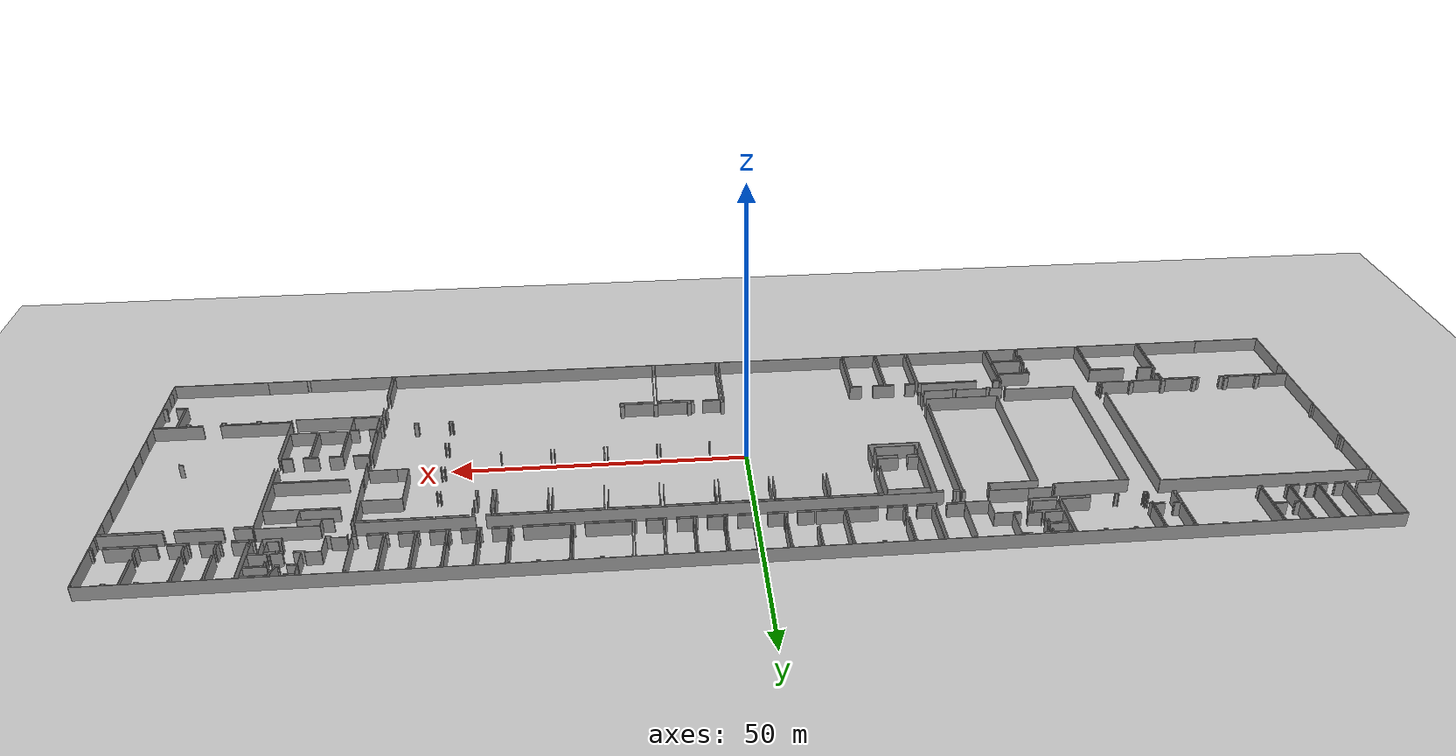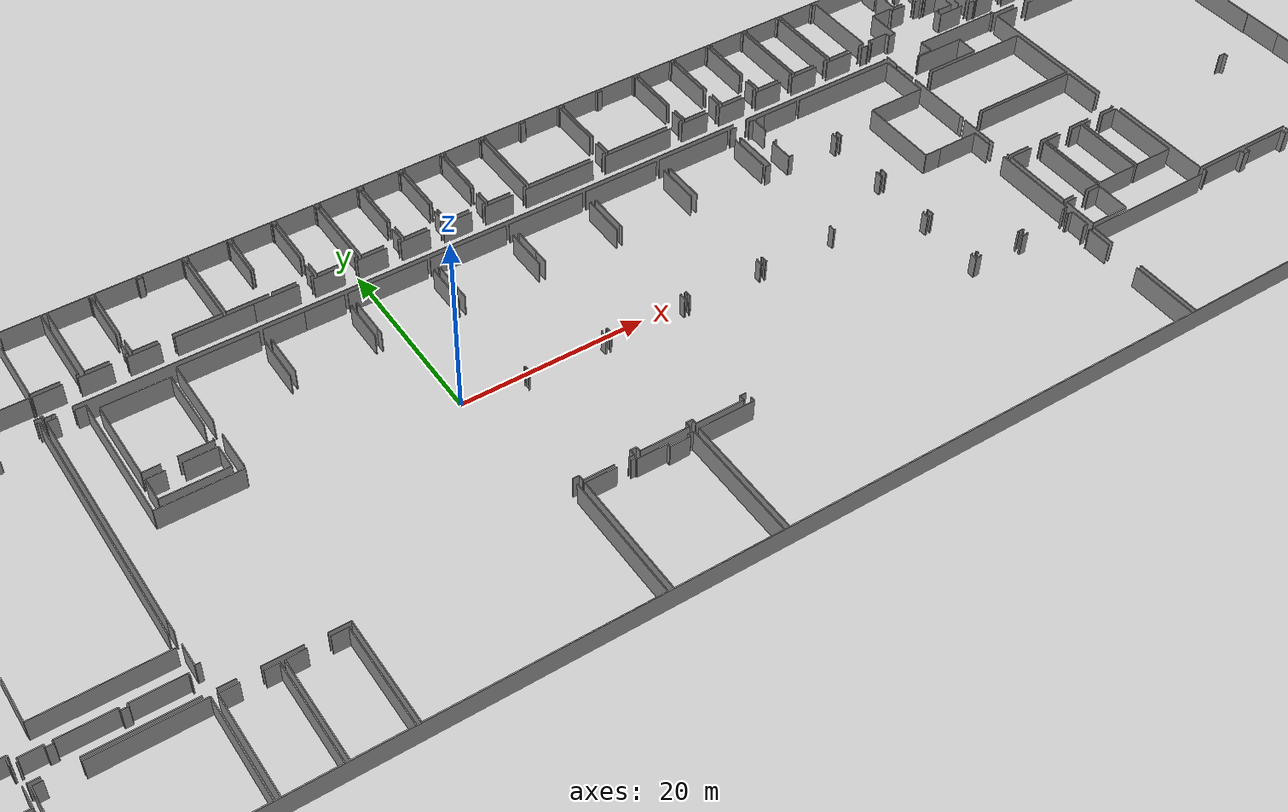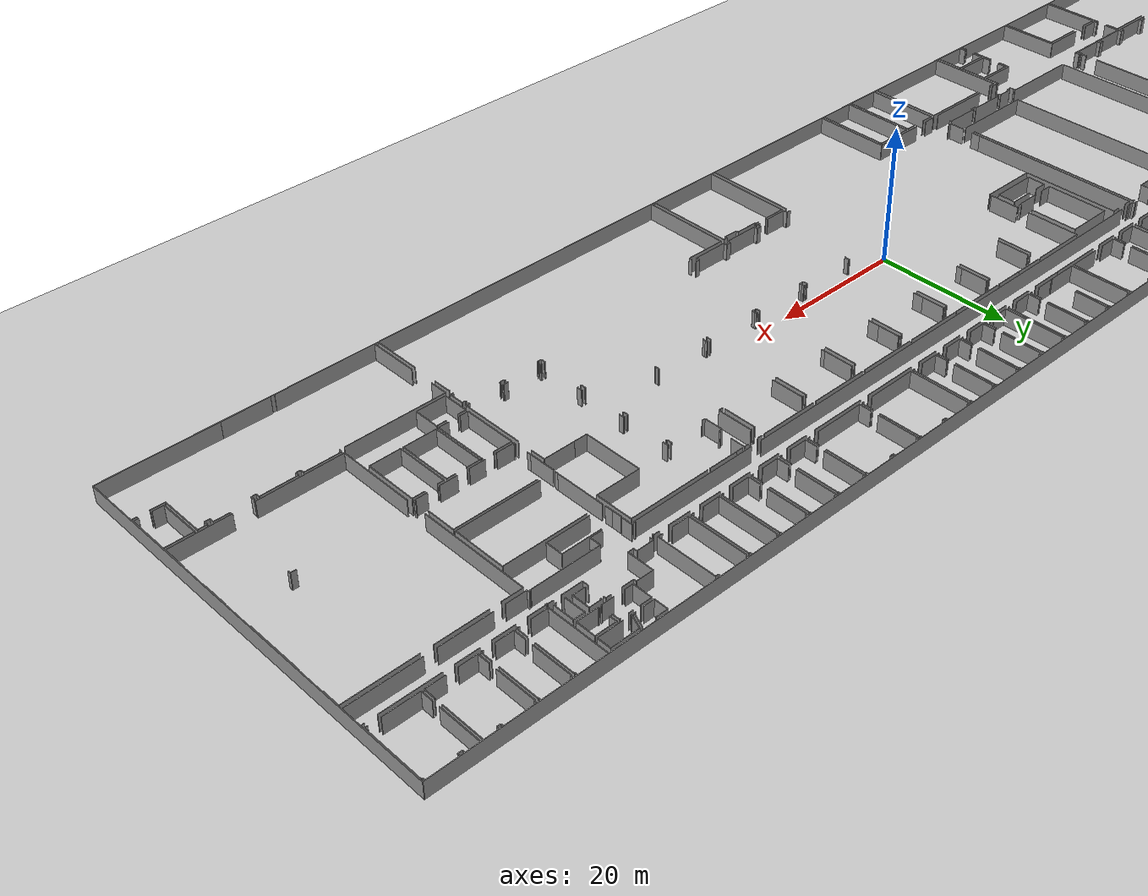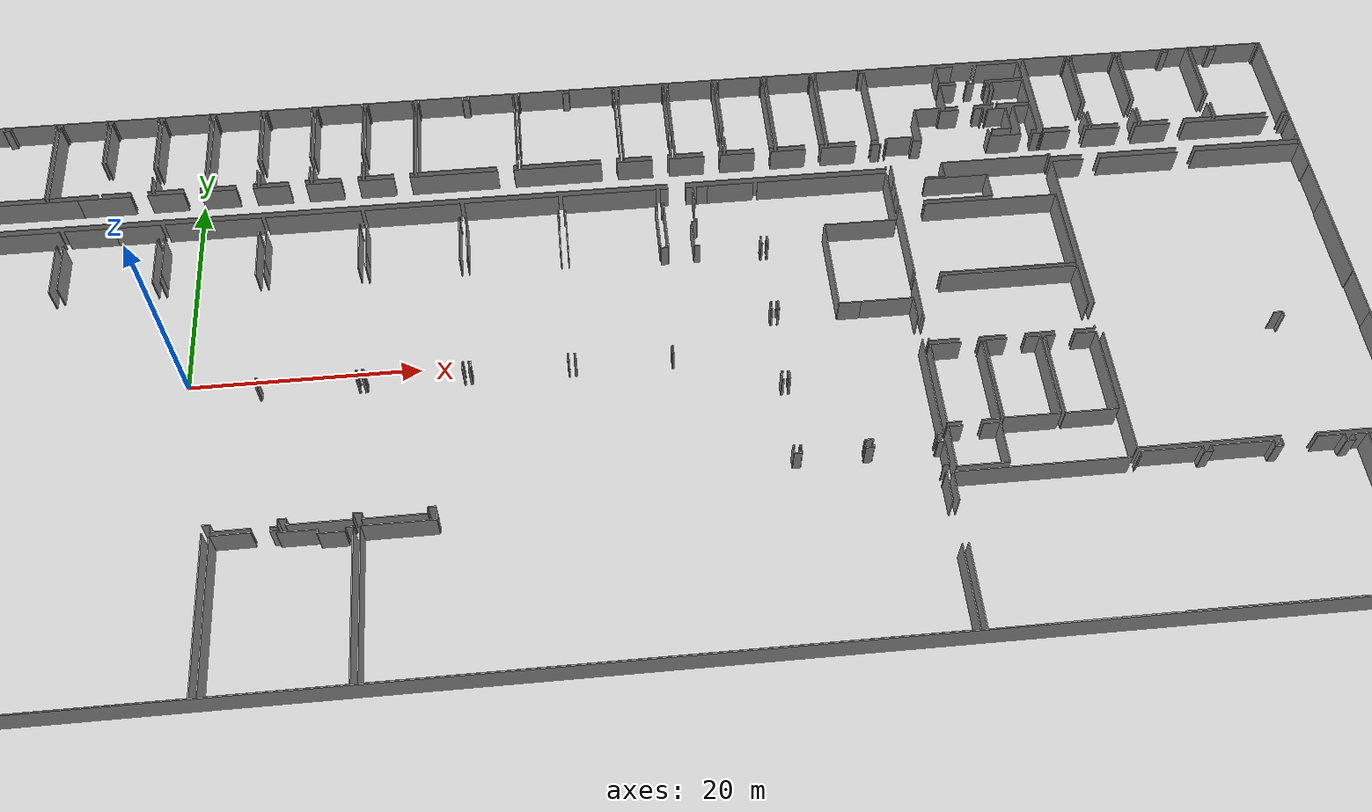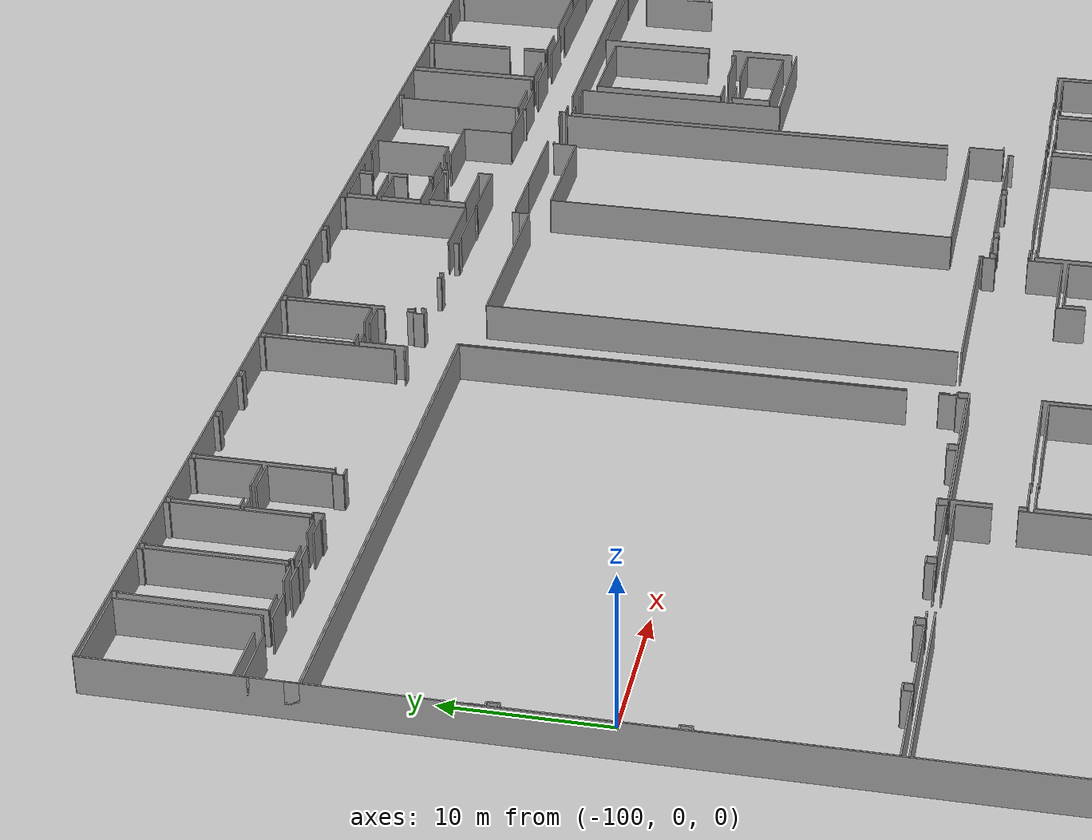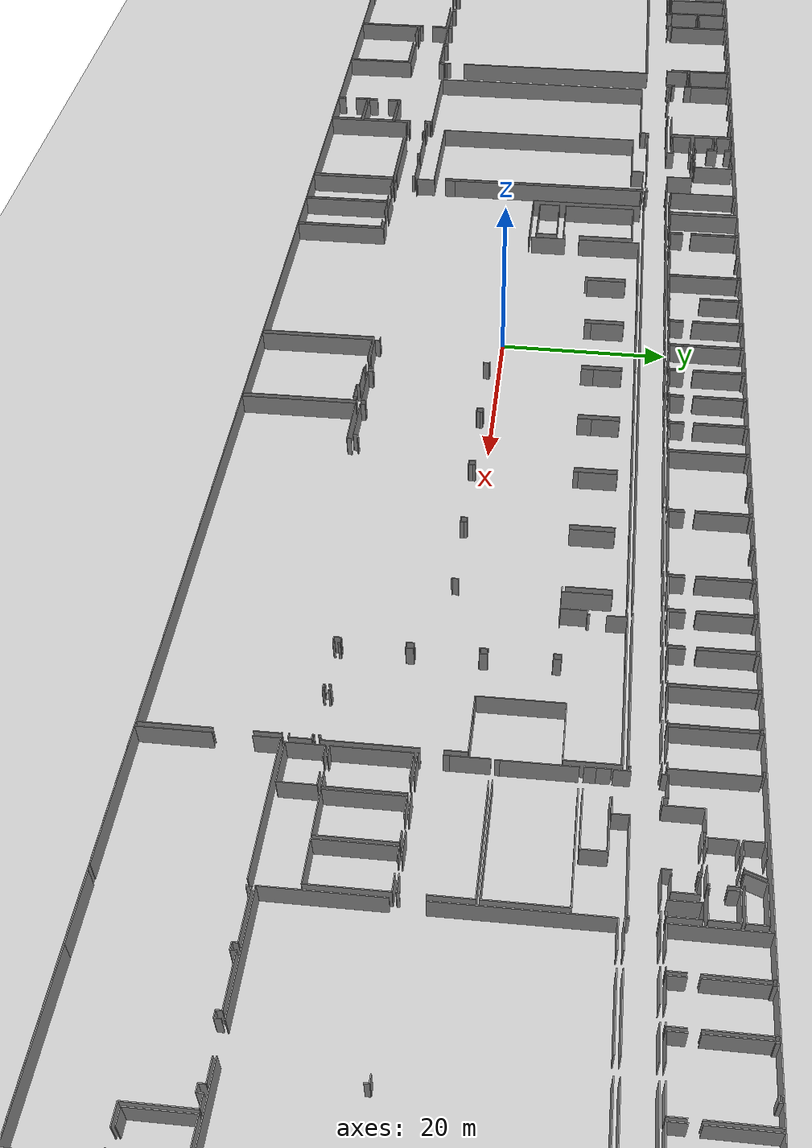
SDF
<sdf version="1.6">
  <world name="default">
    <light name="sun" type="directional">
      <cast_shadows>1</cast_shadows>
      <pose frame="">0 0 10 0 -0 0</pose>
      <diffuse>0.8 0.8 0.8 1</diffuse>
      <specular>0.1 0.1 0.1 1</specular>
      <attenuation>
        <range>1000</range>
        <constant>0.9</constant>
        <linear>0.01</linear>
        <quadratic>0.001</quadratic>
      </attenuation>
      <direction>-0.5 0.5 -1</direction>
    </light>
    <model name="ground_plane">
      <static>1</static>
      <link name="link">
        <collision name="collision">
          <geometry>
            <plane>
              <normal>0 0 1</normal>
              <size>100 100</size>
            </plane>
          </geometry>
          <surface>
            <friction>
              <ode>
                <mu>100</mu>
                <mu2>50</mu2>
              </ode>
              <torsional>
                <ode />
              </torsional>
            </friction>
            <contact>
              <ode />
            </contact>
            <bounce />
          </surface>
          <max_contacts>10</max_contacts>
        </collision>
        <visual name="visual">
          <cast_shadows>0</cast_shadows>
          <geometry>
            <plane>
              <normal>0 0 1</normal>
              <size>100 100</size>
            </plane>
          </geometry>
          <material>
            <script>
              <uri>file://media/materials/scripts/gazebo.material</uri>
              <name>Gazebo/Grey</name>
            </script>
          </material>
        </visual>
        <self_collide>0</self_collide>
        <kinematic>0</kinematic>
        <gravity>1</gravity>
      </link>
    </model>
    <gravity>0 0 -9.8</gravity>
    <magnetic_field>6e-06 2.3e-05 -4.2e-05</magnetic_field>
    <atmosphere type="adiabatic" />
    <physics default="0" name="default_physics" type="ode">
      <max_step_size>0.001</max_step_size>
      <real_time_factor>1</real_time_factor>
      <real_time_update_rate>1000</real_time_update_rate>
    </physics>
    <scene>
      <ambient>0.4 0.4 0.4 1</ambient>
      <background>0.7 0.7 0.7 1</background>
      <shadows>1</shadows>
    </scene>
    <spherical_coordinates>
      <surface_model>EARTH_WGS84</surface_model>
      <latitude_deg>0</latitude_deg>
      <longitude_deg>0</longitude_deg>
      <elevation>0</elevation>
      <heading_deg>0</heading_deg>
    </spherical_coordinates>
  <model name="50010535_PLAN1">
		<static>1</static>
		<link name="Wall_0">
			<collision name="Wall_0_Collision">
				<geometry>
					<box>
						<size>8.72054535174 0.1 2.5</size>
					</box>
				</geometry>
				<pose frame="">4.36027267587 0 1.25 0 0 0</pose>
			</collision>
			<visual name="Wall_0_Visual">
				<pose frame="">4.36027267587 0 1.25 0 0 0</pose>
				<geometry>
					<box>
						<size>8.72054535174 0.1 2.5</size>
					</box>
				</geometry>
				<material>
					<script>
						<uri>file://media/materials/scripts/gazebo.material</uri>
						<name>Gazebo/Grey</name>
					</script>
					<ambient>1 1 1 1</ambient>
				</material>
			</visual>
			<pose frame="">0.0149933609906 -8.9909340991 0 0 0 1.57079632679</pose>
		</link>
		<link name="Wall_1">
			<collision name="Wall_1_Collision">
				<geometry>
					<box>
						<size>5.52492646265 0.1 2.5</size>
					</box>
				</geometry>
				<pose frame="">2.76246323132 0 1.25 0 0 0</pose>
			</collision>
			<visual name="Wall_1_Visual">
				<pose frame="">2.76246323132 0 1.25 0 0 0</pose>
				<geometry>
					<box>
						<size>5.52492646265 0.1 2.5</size>
					</box>
				</geometry>
				<material>
					<script>
						<uri>file://media/materials/scripts/gazebo.material</uri>
						<name>Gazebo/Grey</name>
					</script>
					<ambient>1 1 1 1</ambient>
				</material>
			</visual>
			<pose frame="">0.0149933609906 -0.270388747356 0 0 0 0.0</pose>
		</link>
		<link name="Wall_2">
			<collision name="Wall_2_Collision">
				<geometry>
					<box>
						<size>8.73528458797 0.1 2.5</size>
					</box>
				</geometry>
				<pose frame="">4.36764229398 0 1.25 0 0 0</pose>
			</collision>
			<visual name="Wall_2_Visual">
				<pose frame="">4.36764229398 0 1.25 0 0 0</pose>
				<geometry>
					<box>
						<size>8.73528458797 0.1 2.5</size>
					</box>
				</geometry>
				<material>
					<script>
						<uri>file://media/materials/scripts/gazebo.material</uri>
						<name>Gazebo/Grey</name>
					</script>
					<ambient>1 1 1 1</ambient>
				</material>
			</visual>
			<pose frame="">5.53991982364 -0.270388747356 0 0 0 -1.57079632679</pose>
		</link>
		<link name="Wall_3">
			<collision name="Wall_3_Collision">
				<geometry>
					<box>
						<size>0.215243673882 0.1 2.5</size>
					</box>
				</geometry>
				<pose frame="">0.107621836941 0 1.25 0 0 0</pose>
			</collision>
			<visual name="Wall_3_Visual">
				<pose frame="">0.107621836941 0 1.25 0 0 0</pose>
				<geometry>
					<box>
						<size>0.215243673882 0.1 2.5</size>
					</box>
				</geometry>
				<material>
					<script>
						<uri>file://media/materials/scripts/gazebo.material</uri>
						<name>Gazebo/Grey</name>
					</script>
					<ambient>1 1 1 1</ambient>
				</material>
			</visual>
			<pose frame="">5.53991982364 -9.00567333532 0 0 0 3.14159265359</pose>
		</link>
		<link name="Wall_4">
			<collision name="Wall_4_Collision">
				<geometry>
					<box>
						<size>3.88762855819 0.1 2.5</size>
					</box>
				</geometry>
				<pose frame="">1.94381427909 0 1.25 0 0 0</pose>
			</collision>
			<visual name="Wall_4_Visual">
				<pose frame="">1.94381427909 0 1.25 0 0 0</pose>
				<geometry>
					<box>
						<size>3.88762855819 0.1 2.5</size>
					</box>
				</geometry>
				<material>
					<script>
						<uri>file://media/materials/scripts/gazebo.material</uri>
						<name>Gazebo/Grey</name>
					</script>
					<ambient>1 1 1 1</ambient>
				</material>
			</visual>
			<pose frame="">3.90259397851 -9.00567333532 0 0 0 3.13780132648</pose>
		</link>
		<link name="Wall_5">
			<collision name="Wall_5_Collision">
				<geometry>
					<box>
						<size>8.81152201673 0.1 2.5</size>
					</box>
				</geometry>
				<pose frame="">4.40576100837 0 1.25 0 0 0</pose>
			</collision>
			<visual name="Wall_5_Visual">
				<pose frame="">4.40576100837 0 1.25 0 0 0</pose>
				<geometry>
					<box>
						<size>8.81152201673 0.1 2.5</size>
					</box>
				</geometry>
				<material>
					<script>
						<uri>file://media/materials/scripts/gazebo.material</uri>
						<name>Gazebo/Grey</name>
					</script>
					<ambient>1 1 1 1</ambient>
				</material>
			</visual>
			<pose frame="">6.08400094026 -9.19347153485 0 0 0 1.57079632679</pose>
		</link>
		<link name="Wall_6">
			<collision name="Wall_6_Collision">
				<geometry>
					<box>
						<size>0.106224150747 0.1 2.5</size>
					</box>
				</geometry>
				<pose frame="">0.0531120753734 0 1.25 0 0 0</pose>
			</collision>
			<visual name="Wall_6_Visual">
				<pose frame="">0.0531120753734 0 1.25 0 0 0</pose>
				<geometry>
					<box>
						<size>0.106224150747 0.1 2.5</size>
					</box>
				</geometry>
				<material>
					<script>
						<uri>file://media/materials/scripts/gazebo.material</uri>
						<name>Gazebo/Grey</name>
					</script>
					<ambient>1 1 1 1</ambient>
				</material>
			</visual>
			<pose frame="">6.08400094026 -0.381949518116 0 0 0 0.0</pose>
		</link>
		<link name="Wall_7">
			<collision name="Wall_7_Collision">
				<geometry>
					<box>
						<size>0.375850523815 0.1 2.5</size>
					</box>
				</geometry>
				<pose frame="">0.187925261907 0 1.25 0 0 0</pose>
			</collision>
			<visual name="Wall_7_Visual">
				<pose frame="">0.187925261907 0 1.25 0 0 0</pose>
				<geometry>
					<box>
						<size>0.375850523815 0.1 2.5</size>
					</box>
				</geometry>
				<material>
					<script>
						<uri>file://media/materials/scripts/gazebo.material</uri>
						<name>Gazebo/Grey</name>
					</script>
					<ambient>1 1 1 1</ambient>
				</material>
			</visual>
			<pose frame="">6.19022509101 -0.381949518116 0 0 0 1.57079632679</pose>
		</link>
		<link name="Wall_8">
			<collision name="Wall_8_Collision">
				<geometry>
					<box>
						<size>0.382203642878 0.1 2.5</size>
					</box>
				</geometry>
				<pose frame="">0.191101821439 0 1.25 0 0 0</pose>
			</collision>
			<visual name="Wall_8_Visual">
				<pose frame="">0.191101821439 0 1.25 0 0 0</pose>
				<geometry>
					<box>
						<size>0.382203642878 0.1 2.5</size>
					</box>
				</geometry>
				<material>
					<script>
						<uri>file://media/materials/scripts/gazebo.material</uri>
						<name>Gazebo/Grey</name>
					</script>
					<ambient>1 1 1 1</ambient>
				</material>
			</visual>
			<pose frame="">10.3995476579 -0.00609899430125 0 0 0 -1.57079632679</pose>
		</link>
		<link name="Wall_9">
			<collision name="Wall_9_Collision">
				<geometry>
					<box>
						<size>0.104191152646 0.1 2.5</size>
					</box>
				</geometry>
				<pose frame="">0.0520955763232 0 1.25 0 0 0</pose>
			</collision>
			<visual name="Wall_9_Visual">
				<pose frame="">0.0520955763232 0 1.25 0 0 0</pose>
				<geometry>
					<box>
						<size>0.104191152646 0.1 2.5</size>
					</box>
				</geometry>
				<material>
					<script>
						<uri>file://media/materials/scripts/gazebo.material</uri>
						<name>Gazebo/Grey</name>
					</script>
					<ambient>1 1 1 1</ambient>
				</material>
			</visual>
			<pose frame="">10.3995476579 -0.38830263718 0 0 0 0.0</pose>
		</link>
		<link name="Wall_10">
			<collision name="Wall_10_Collision">
				<geometry>
					<box>
						<size>8.5396085208 0.1 2.5</size>
					</box>
				</geometry>
				<pose frame="">4.2698042604 0 1.25 0 0 0</pose>
			</collision>
			<visual name="Wall_10_Visual">
				<pose frame="">4.2698042604 0 1.25 0 0 0</pose>
				<geometry>
					<box>
						<size>8.5396085208 0.1 2.5</size>
					</box>
				</geometry>
				<material>
					<script>
						<uri>file://media/materials/scripts/gazebo.material</uri>
						<name>Gazebo/Grey</name>
					</script>
					<ambient>1 1 1 1</ambient>
				</material>
			</visual>
			<pose frame="">10.5037388106 -0.38830263718 0 0 0 -1.57079632679</pose>
		</link>
		<link name="Wall_11">
			<collision name="Wall_11_Collision">
				<geometry>
					<box>
						<size>0.142563991792 0.1 2.5</size>
					</box>
				</geometry>
				<pose frame="">0.0712819958959 0 1.25 0 0 0</pose>
			</collision>
			<visual name="Wall_11_Visual">
				<pose frame="">0.0712819958959 0 1.25 0 0 0</pose>
				<geometry>
					<box>
						<size>0.142563991792 0.1 2.5</size>
					</box>
				</geometry>
				<material>
					<script>
						<uri>file://media/materials/scripts/gazebo.material</uri>
						<name>Gazebo/Grey</name>
					</script>
					<ambient>1 1 1 1</ambient>
				</material>
			</visual>
			<pose frame="">10.5037388106 -8.92791115798 0 0 0 3.14159265359</pose>
		</link>
		<link name="Wall_12">
			<collision name="Wall_12_Collision">
				<geometry>
					<box>
						<size>0.251329390164 0.1 2.5</size>
					</box>
				</geometry>
				<pose frame="">0.125664695082 0 1.25 0 0 0</pose>
			</collision>
			<visual name="Wall_12_Visual">
				<pose frame="">0.125664695082 0 1.25 0 0 0</pose>
				<geometry>
					<box>
						<size>0.251329390164 0.1 2.5</size>
					</box>
				</geometry>
				<material>
					<script>
						<uri>file://media/materials/scripts/gazebo.material</uri>
						<name>Gazebo/Grey</name>
					</script>
					<ambient>1 1 1 1</ambient>
				</material>
			</visual>
			<pose frame="">10.3611748188 -8.92791115798 0 0 0 -1.57079632679</pose>
		</link>
		<link name="Wall_13">
			<collision name="Wall_13_Collision">
				<geometry>
					<box>
						<size>1.41979504838 0.1 2.5</size>
					</box>
				</geometry>
				<pose frame="">0.709897524189 0 1.25 0 0 0</pose>
			</collision>
			<visual name="Wall_13_Visual">
				<pose frame="">0.709897524189 0 1.25 0 0 0</pose>
				<geometry>
					<box>
						<size>1.41979504838 0.1 2.5</size>
					</box>
				</geometry>
				<material>
					<script>
						<uri>file://media/materials/scripts/gazebo.material</uri>
						<name>Gazebo/Grey</name>
					</script>
					<ambient>1 1 1 1</ambient>
				</material>
			</visual>
			<pose frame="">10.3611748188 -9.17924054815 0 0 0 3.14159265359</pose>
		</link>
		<link name="Wall_14">
			<collision name="Wall_14_Collision">
				<geometry>
					<box>
						<size>1.54438175043 0.1 2.5</size>
					</box>
				</geometry>
				<pose frame="">0.772190875215 0 1.25 0 0 0</pose>
			</collision>
			<visual name="Wall_14_Visual">
				<pose frame="">0.772190875215 0 1.25 0 0 0</pose>
				<geometry>
					<box>
						<size>1.54438175043 0.1 2.5</size>
					</box>
				</geometry>
				<material>
					<script>
						<uri>file://media/materials/scripts/gazebo.material</uri>
						<name>Gazebo/Grey</name>
					</script>
					<ambient>1 1 1 1</ambient>
				</material>
			</visual>
			<pose frame="">7.62831712229 -9.17924054815 0 0 0 -3.13237784119</pose>
		</link>
		<link name="Wall_15">
			<collision name="Wall_15_Collision">
				<geometry>
					<box>
						<size>8.52512340934 0.1 2.5</size>
					</box>
				</geometry>
				<pose frame="">4.26256170467 0 1.25 0 0 0</pose>
			</collision>
			<visual name="Wall_15_Visual">
				<pose frame="">4.26256170467 0 1.25 0 0 0</pose>
				<geometry>
					<box>
						<size>8.52512340934 0.1 2.5</size>
					</box>
				</geometry>
				<material>
					<script>
						<uri>file://media/materials/scripts/gazebo.material</uri>
						<name>Gazebo/Grey</name>
					</script>
					<ambient>1 1 1 1</ambient>
				</material>
			</visual>
			<pose frame="">10.8676454705 -8.93909264754 0 0 0 1.57079632679</pose>
		</link>
		<link name="Wall_16">
			<collision name="Wall_16_Collision">
				<geometry>
					<box>
						<size>0.135194373678 0.1 2.5</size>
					</box>
				</geometry>
				<pose frame="">0.0675971868389 0 1.25 0 0 0</pose>
			</collision>
			<visual name="Wall_16_Visual">
				<pose frame="">0.0675971868389 0 1.25 0 0 0</pose>
				<geometry>
					<box>
						<size>0.135194373678 0.1 2.5</size>
					</box>
				</geometry>
				<material>
					<script>
						<uri>file://media/materials/scripts/gazebo.material</uri>
						<name>Gazebo/Grey</name>
					</script>
					<ambient>1 1 1 1</ambient>
				</material>
			</visual>
			<pose frame="">10.8676454705 -0.413969238197 0 0 0 0.0</pose>
		</link>
		<link name="Wall_17">
			<collision name="Wall_17_Collision">
				<geometry>
					<box>
						<size>0.375850523815 0.1 2.5</size>
					</box>
				</geometry>
				<pose frame="">0.187925261907 0 1.25 0 0 0</pose>
			</collision>
			<visual name="Wall_17_Visual">
				<pose frame="">0.187925261907 0 1.25 0 0 0</pose>
				<geometry>
					<box>
						<size>0.375850523815 0.1 2.5</size>
					</box>
				</geometry>
				<material>
					<script>
						<uri>file://media/materials/scripts/gazebo.material</uri>
						<name>Gazebo/Grey</name>
					</script>
					<ambient>1 1 1 1</ambient>
				</material>
			</visual>
			<pose frame="">11.0028398442 -0.413969238197 0 0 0 1.57079632679</pose>
		</link>
		<link name="Wall_18">
			<collision name="Wall_18_Collision">
				<geometry>
					<box>
						<size>0.347134425646 0.1 2.5</size>
					</box>
				</geometry>
				<pose frame="">0.173567212823 0 1.25 0 0 0</pose>
			</collision>
			<visual name="Wall_18_Visual">
				<pose frame="">0.173567212823 0 1.25 0 0 0</pose>
				<geometry>
					<box>
						<size>0.347134425646 0.1 2.5</size>
					</box>
				</geometry>
				<material>
					<script>
						<uri>file://media/materials/scripts/gazebo.material</uri>
						<name>Gazebo/Grey</name>
					</script>
					<ambient>1 1 1 1</ambient>
				</material>
			</visual>
			<pose frame="">15.2238521502 -0.0381187143828 0 0 0 -1.57079632679</pose>
		</link>
		<link name="Wall_19">
			<collision name="Wall_19_Collision">
				<geometry>
					<box>
						<size>0.0785245516286 0.1 2.5</size>
					</box>
				</geometry>
				<pose frame="">0.0392622758143 0 1.25 0 0 0</pose>
			</collision>
			<visual name="Wall_19_Visual">
				<pose frame="">0.0392622758143 0 1.25 0 0 0</pose>
				<geometry>
					<box>
						<size>0.0785245516286 0.1 2.5</size>
					</box>
				</geometry>
				<material>
					<script>
						<uri>file://media/materials/scripts/gazebo.material</uri>
						<name>Gazebo/Grey</name>
					</script>
					<ambient>1 1 1 1</ambient>
				</material>
			</visual>
			<pose frame="">15.2238521502 -0.385253140029 0 0 0 0.0</pose>
		</link>
		<link name="Wall_20">
			<collision name="Wall_20_Collision">
				<geometry>
					<box>
						<size>8.54901113702 0.1 2.5</size>
					</box>
				</geometry>
				<pose frame="">4.27450556851 0 1.25 0 0 0</pose>
			</collision>
			<visual name="Wall_20_Visual">
				<pose frame="">4.27450556851 0 1.25 0 0 0</pose>
				<geometry>
					<box>
						<size>8.54901113702 0.1 2.5</size>
					</box>
				</geometry>
				<material>
					<script>
						<uri>file://media/materials/scripts/gazebo.material</uri>
						<name>Gazebo/Grey</name>
					</script>
					<ambient>1 1 1 1</ambient>
				</material>
			</visual>
			<pose frame="">15.3023767018 -0.385253140029 0 0 0 -1.57079632679</pose>
		</link>
		<link name="Wall_21">
			<collision name="Wall_21_Collision">
				<geometry>
					<box>
						<size>0.102920528834 0.1 2.5</size>
					</box>
				</geometry>
				<pose frame="">0.0514602644168 0 1.25 0 0 0</pose>
			</collision>
			<visual name="Wall_21_Visual">
				<pose frame="">0.0514602644168 0 1.25 0 0 0</pose>
				<geometry>
					<box>
						<size>0.102920528834 0.1 2.5</size>
					</box>
				</geometry>
				<material>
					<script>
						<uri>file://media/materials/scripts/gazebo.material</uri>
						<name>Gazebo/Grey</name>
					</script>
					<ambient>1 1 1 1</ambient>
				</material>
			</visual>
			<pose frame="">15.3023767018 -8.93426427705 0 0 0 3.14159265359</pose>
		</link>
		<link name="Wall_22">
			<collision name="Wall_22_Collision">
				<geometry>
					<box>
						<size>0.232778282498 0.1 2.5</size>
					</box>
				</geometry>
				<pose frame="">0.116389141249 0 1.25 0 0 0</pose>
			</collision>
			<visual name="Wall_22_Visual">
				<pose frame="">0.116389141249 0 1.25 0 0 0</pose>
				<geometry>
					<box>
						<size>0.232778282498 0.1 2.5</size>
					</box>
				</geometry>
				<material>
					<script>
						<uri>file://media/materials/scripts/gazebo.material</uri>
						<name>Gazebo/Grey</name>
					</script>
					<ambient>1 1 1 1</ambient>
				</material>
			</visual>
			<pose frame="">15.199456173 -8.93426427705 0 0 0 -1.57079632679</pose>
		</link>
		<link name="Wall_23">
			<collision name="Wall_23_Collision">
				<geometry>
					<box>
						<size>1.4535936418 0.1 2.5</size>
					</box>
				</geometry>
				<pose frame="">0.726796820899 0 1.25 0 0 0</pose>
			</collision>
			<visual name="Wall_23_Visual">
				<pose frame="">0.726796820899 0 1.25 0 0 0</pose>
				<geometry>
					<box>
						<size>1.4535936418 0.1 2.5</size>
					</box>
				</geometry>
				<material>
					<script>
						<uri>file://media/materials/scripts/gazebo.material</uri>
						<name>Gazebo/Grey</name>
					</script>
					<ambient>1 1 1 1</ambient>
				</material>
			</visual>
			<pose frame="">15.199456173 -9.16704255954 0 0 0 3.14159265359</pose>
		</link>
		<link name="Wall_24">
			<collision name="Wall_24_Collision">
				<geometry>
					<box>
						<size>1.3796433359 0.1 2.5</size>
					</box>
				</geometry>
				<pose frame="">0.689821667948 0 1.25 0 0 0</pose>
			</collision>
			<visual name="Wall_24_Visual">
				<pose frame="">0.689821667948 0 1.25 0 0 0</pose>
				<geometry>
					<box>
						<size>1.3796433359 0.1 2.5</size>
					</box>
				</geometry>
				<material>
					<script>
						<uri>file://media/materials/scripts/gazebo.material</uri>
						<name>Gazebo/Grey</name>
					</script>
					<ambient>1 1 1 1</ambient>
				</material>
			</visual>
			<pose frame="">12.4241596412 -9.16704255954 0 0 0 3.14159265359</pose>
		</link>
		<link name="Wall_25">
			<collision name="Wall_25_Collision">
				<geometry>
					<box>
						<size>0.203299810042 0.1 2.5</size>
					</box>
				</geometry>
				<pose frame="">0.101649905021 0 1.25 0 0 0</pose>
			</collision>
			<visual name="Wall_25_Visual">
				<pose frame="">0.101649905021 0 1.25 0 0 0</pose>
				<geometry>
					<box>
						<size>0.203299810042 0.1 2.5</size>
					</box>
				</geometry>
				<material>
					<script>
						<uri>file://media/materials/scripts/gazebo.material</uri>
						<name>Gazebo/Grey</name>
					</script>
					<ambient>1 1 1 1</ambient>
				</material>
			</visual>
			<pose frame="">11.0445163053 -9.16704255954 0 0 0 1.57079632679</pose>
		</link>
		<link name="Wall_26">
			<collision name="Wall_26_Collision">
				<geometry>
					<box>
						<size>0.178580289246 0.1 2.5</size>
					</box>
				</geometry>
				<pose frame="">0.0892901446232 0 1.25 0 0 0</pose>
			</collision>
			<visual name="Wall_26_Visual">
				<pose frame="">0.0892901446232 0 1.25 0 0 0</pose>
				<geometry>
					<box>
						<size>0.178580289246 0.1 2.5</size>
					</box>
				</geometry>
				<material>
					<script>
						<uri>file://media/materials/scripts/gazebo.material</uri>
						<name>Gazebo/Grey</name>
					</script>
					<ambient>1 1 1 1</ambient>
				</material>
			</visual>
			<pose frame="">11.0445163053 -8.9637427495 0 0 0 3.00311679715</pose>
		</link>
		<link name="Wall_27">
			<collision name="Wall_27_Collision">
				<geometry>
					<box>
						<size>4.16891672967 0.1 2.5</size>
					</box>
				</geometry>
				<pose frame="">2.08445836483 0 1.25 0 0 0</pose>
			</collision>
			<visual name="Wall_27_Visual">
				<pose frame="">2.08445836483 0 1.25 0 0 0</pose>
				<geometry>
					<box>
						<size>4.16891672967 0.1 2.5</size>
					</box>
				</geometry>
				<material>
					<script>
						<uri>file://media/materials/scripts/gazebo.material</uri>
						<name>Gazebo/Grey</name>
					</script>
					<ambient>1 1 1 1</ambient>
				</material>
			</visual>
			<pose frame="">15.6749236037 -4.55721936685 0 0 0 1.57079632679</pose>
		</link>
		<link name="Wall_28">
			<collision name="Wall_28_Collision">
				<geometry>
					<box>
						<size>0.115880891724 0.1 2.5</size>
					</box>
				</geometry>
				<pose frame="">0.0579404458619 0 1.25 0 0 0</pose>
			</collision>
			<visual name="Wall_28_Visual">
				<pose frame="">0.0579404458619 0 1.25 0 0 0</pose>
				<geometry>
					<box>
						<size>0.115880891724 0.1 2.5</size>
					</box>
				</geometry>
				<material>
					<script>
						<uri>file://media/materials/scripts/gazebo.material</uri>
						<name>Gazebo/Grey</name>
					</script>
					<ambient>1 1 1 1</ambient>
				</material>
			</visual>
			<pose frame="">15.6749236037 -0.38830263718 0 0 0 0.0</pose>
		</link>
		<link name="Wall_29">
			<collision name="Wall_29_Collision">
				<geometry>
					<box>
						<size>0.357045291386 0.1 2.5</size>
					</box>
				</geometry>
				<pose frame="">0.178522645693 0 1.25 0 0 0</pose>
			</collision>
			<visual name="Wall_29_Visual">
				<pose frame="">0.178522645693 0 1.25 0 0 0</pose>
				<geometry>
					<box>
						<size>0.357045291386 0.1 2.5</size>
					</box>
				</geometry>
				<material>
					<script>
						<uri>file://media/materials/scripts/gazebo.material</uri>
						<name>Gazebo/Grey</name>
					</script>
					<ambient>1 1 1 1</ambient>
				</material>
			</visual>
			<pose frame="">15.7908044955 -0.38830263718 0 0 0 1.57079632679</pose>
		</link>
		<link name="Wall_30">
			<collision name="Wall_30_Collision">
				<geometry>
					<box>
						<size>0.348913298984 0.1 2.5</size>
					</box>
				</geometry>
				<pose frame="">0.174456649492 0 1.25 0 0 0</pose>
			</collision>
			<visual name="Wall_30_Visual">
				<pose frame="">0.174456649492 0 1.25 0 0 0</pose>
				<geometry>
					<box>
						<size>0.348913298984 0.1 2.5</size>
					</box>
				</geometry>
				<material>
					<script>
						<uri>file://media/materials/scripts/gazebo.material</uri>
						<name>Gazebo/Grey</name>
					</script>
					<ambient>1 1 1 1</ambient>
				</material>
			</visual>
			<pose frame="">20.00266831 -0.0312573457939 0 0 0 -1.57079632679</pose>
		</link>
		<link name="Wall_31">
			<collision name="Wall_31_Collision">
				<geometry>
					<box>
						<size>0.116389141249 0.1 2.5</size>
					</box>
				</geometry>
				<pose frame="">0.0581945706244 0 1.25 0 0 0</pose>
			</collision>
			<visual name="Wall_31_Visual">
				<pose frame="">0.0581945706244 0 1.25 0 0 0</pose>
				<geometry>
					<box>
						<size>0.116389141249 0.1 2.5</size>
					</box>
				</geometry>
				<material>
					<script>
						<uri>file://media/materials/scripts/gazebo.material</uri>
						<name>Gazebo/Grey</name>
					</script>
					<ambient>1 1 1 1</ambient>
				</material>
			</visual>
			<pose frame="">20.00266831 -0.380170644778 0 0 0 0.0</pose>
		</link>
		<link name="Wall_32">
			<collision name="Wall_32_Collision">
				<geometry>
					<box>
						<size>4.15061974676 0.1 2.5</size>
					</box>
				</geometry>
				<pose frame="">2.07530987338 0 1.25 0 0 0</pose>
			</collision>
			<visual name="Wall_32_Visual">
				<pose frame="">2.07530987338 0 1.25 0 0 0</pose>
				<geometry>
					<box>
						<size>4.15061974676 0.1 2.5</size>
					</box>
				</geometry>
				<material>
					<script>
						<uri>file://media/materials/scripts/gazebo.material</uri>
						<name>Gazebo/Grey</name>
					</script>
					<ambient>1 1 1 1</ambient>
				</material>
			</visual>
			<pose frame="">20.1190574513 -0.380170644778 0 0 0 -1.57079632679</pose>
		</link>
		<link name="Wall_33">
			<collision name="Wall_33_Collision">
				<geometry>
					<box>
						<size>2.28280274201 0.1 2.5</size>
					</box>
				</geometry>
				<pose frame="">1.141401371 0 1.25 0 0 0</pose>
			</collision>
			<visual name="Wall_33_Visual">
				<pose frame="">1.141401371 0 1.25 0 0 0</pose>
				<geometry>
					<box>
						<size>2.28280274201 0.1 2.5</size>
					</box>
				</geometry>
				<material>
					<script>
						<uri>file://media/materials/scripts/gazebo.material</uri>
						<name>Gazebo/Grey</name>
					</script>
					<ambient>1 1 1 1</ambient>
				</material>
			</visual>
			<pose frame="">20.1190574513 -4.53079039154 0 0 0 3.14159265359</pose>
		</link>
		<link name="Wall_34">
			<collision name="Wall_34_Collision">
				<geometry>
					<box>
						<size>0.848680073145 0.1 2.5</size>
					</box>
				</geometry>
				<pose frame="">0.424340036573 0 1.25 0 0 0</pose>
			</collision>
			<visual name="Wall_34_Visual">
				<pose frame="">0.424340036573 0 1.25 0 0 0</pose>
				<geometry>
					<box>
						<size>0.848680073145 0.1 2.5</size>
					</box>
				</geometry>
				<material>
					<script>
						<uri>file://media/materials/scripts/gazebo.material</uri>
						<name>Gazebo/Grey</name>
					</script>
					<ambient>1 1 1 1</ambient>
				</material>
			</visual>
			<pose frame="">16.5231920611 -4.53079039154 0 0 0 -3.11044634803</pose>
		</link>
		<link name="Wall_35">
			<collision name="Wall_35_Collision">
				<geometry>
					<box>
						<size>8.58331797996 0.1 2.5</size>
					</box>
				</geometry>
				<pose frame="">4.29165898998 0 1.25 0 0 0</pose>
			</collision>
			<visual name="Wall_35_Visual">
				<pose frame="">4.29165898998 0 1.25 0 0 0</pose>
				<geometry>
					<box>
						<size>8.58331797996 0.1 2.5</size>
					</box>
				</geometry>
				<material>
					<script>
						<uri>file://media/materials/scripts/gazebo.material</uri>
						<name>Gazebo/Grey</name>
					</script>
					<ambient>1 1 1 1</ambient>
				</material>
			</visual>
			<pose frame="">20.4870301074 -8.95078238661 0 0 0 1.57079632679</pose>
		</link>
		<link name="Wall_36">
			<collision name="Wall_36_Collision">
				<geometry>
					<box>
						<size>0.0930096630941 0.1 2.5</size>
					</box>
				</geometry>
				<pose frame="">0.046504831547 0 1.25 0 0 0</pose>
			</collision>
			<visual name="Wall_36_Visual">
				<pose frame="">0.046504831547 0 1.25 0 0 0</pose>
				<geometry>
					<box>
						<size>0.0930096630941 0.1 2.5</size>
					</box>
				</geometry>
				<material>
					<script>
						<uri>file://media/materials/scripts/gazebo.material</uri>
						<name>Gazebo/Grey</name>
					</script>
					<ambient>1 1 1 1</ambient>
				</material>
			</visual>
			<pose frame="">20.4870301074 -0.36746440665 0 0 0 0.0</pose>
		</link>
		<link name="Wall_37">
			<collision name="Wall_37_Collision">
				<geometry>
					<box>
						<size>0.346880300884 0.1 2.5</size>
					</box>
				</geometry>
				<pose frame="">0.173440150442 0 1.25 0 0 0</pose>
			</collision>
			<visual name="Wall_37_Visual">
				<pose frame="">0.173440150442 0 1.25 0 0 0</pose>
				<geometry>
					<box>
						<size>0.346880300884 0.1 2.5</size>
					</box>
				</geometry>
				<material>
					<script>
						<uri>file://media/materials/scripts/gazebo.material</uri>
						<name>Gazebo/Grey</name>
					</script>
					<ambient>1 1 1 1</ambient>
				</material>
			</visual>
			<pose frame="">20.5800397705 -0.36746440665 0 0 0 1.57079632679</pose>
		</link>
		<link name="Wall_38">
			<collision name="Wall_38_Collision">
				<geometry>
					<box>
						<size>0.358061790436 0.1 2.5</size>
					</box>
				</geometry>
				<pose frame="">0.179030895218 0 1.25 0 0 0</pose>
			</collision>
			<visual name="Wall_38_Visual">
				<pose frame="">0.179030895218 0 1.25 0 0 0</pose>
				<geometry>
					<box>
						<size>0.358061790436 0.1 2.5</size>
					</box>
				</geometry>
				<material>
					<script>
						<uri>file://media/materials/scripts/gazebo.material</uri>
						<name>Gazebo/Grey</name>
					</script>
					<ambient>1 1 1 1</ambient>
				</material>
			</visual>
			<pose frame="">24.8023227003 -0.0205841057667 0 0 0 -1.57079632679</pose>
		</link>
		<link name="Wall_39">
			<collision name="Wall_39_Collision">
				<geometry>
					<box>
						<size>0.596939067235 0.1 2.5</size>
					</box>
				</geometry>
				<pose frame="">0.298469533618 0 1.25 0 0 0</pose>
			</collision>
			<visual name="Wall_39_Visual">
				<pose frame="">0.298469533618 0 1.25 0 0 0</pose>
				<geometry>
					<box>
						<size>0.596939067235 0.1 2.5</size>
					</box>
				</geometry>
				<material>
					<script>
						<uri>file://media/materials/scripts/gazebo.material</uri>
						<name>Gazebo/Grey</name>
					</script>
					<ambient>1 1 1 1</ambient>
				</material>
			</visual>
			<pose frame="">24.8023227003 -0.378645896203 0 0 0 0.0</pose>
		</link>
		<link name="Wall_40">
			<collision name="Wall_40_Collision">
				<geometry>
					<box>
						<size>0.358061790436 0.1 2.5</size>
					</box>
				</geometry>
				<pose frame="">0.179030895218 0 1.25 0 0 0</pose>
			</collision>
			<visual name="Wall_40_Visual">
				<pose frame="">0.179030895218 0 1.25 0 0 0</pose>
				<geometry>
					<box>
						<size>0.358061790436 0.1 2.5</size>
					</box>
				</geometry>
				<material>
					<script>
						<uri>file://media/materials/scripts/gazebo.material</uri>
						<name>Gazebo/Grey</name>
					</script>
					<ambient>1 1 1 1</ambient>
				</material>
			</visual>
			<pose frame="">25.3992617676 -0.378645896203 0 0 0 1.57079632679</pose>
		</link>
		<link name="Wall_41">
			<collision name="Wall_41_Collision">
				<geometry>
					<box>
						<size>0.358061790436 0.1 2.5</size>
					</box>
				</geometry>
				<pose frame="">0.179030895218 0 1.25 0 0 0</pose>
			</collision>
			<visual name="Wall_41_Visual">
				<pose frame="">0.179030895218 0 1.25 0 0 0</pose>
				<geometry>
					<box>
						<size>0.358061790436 0.1 2.5</size>
					</box>
				</geometry>
				<material>
					<script>
						<uri>file://media/materials/scripts/gazebo.material</uri>
						<name>Gazebo/Grey</name>
					</script>
					<ambient>1 1 1 1</ambient>
				</material>
			</visual>
			<pose frame="">29.6014688411 -0.0205841057667 0 0 0 -1.57079632679</pose>
		</link>
		<link name="Wall_42">
			<collision name="Wall_42_Collision">
				<geometry>
					<box>
						<size>0.615744299664 0.1 2.5</size>
					</box>
				</geometry>
				<pose frame="">0.307872149832 0 1.25 0 0 0</pose>
			</collision>
			<visual name="Wall_42_Visual">
				<pose frame="">0.307872149832 0 1.25 0 0 0</pose>
				<geometry>
					<box>
						<size>0.615744299664 0.1 2.5</size>
					</box>
				</geometry>
				<material>
					<script>
						<uri>file://media/materials/scripts/gazebo.material</uri>
						<name>Gazebo/Grey</name>
					</script>
					<ambient>1 1 1 1</ambient>
				</material>
			</visual>
			<pose frame="">29.6014688411 -0.378645896203 0 0 0 0.0</pose>
		</link>
		<link name="Wall_43">
			<collision name="Wall_43_Collision">
				<geometry>
					<box>
						<size>0.358061790436 0.1 2.5</size>
					</box>
				</geometry>
				<pose frame="">0.179030895218 0 1.25 0 0 0</pose>
			</collision>
			<visual name="Wall_43_Visual">
				<pose frame="">0.179030895218 0 1.25 0 0 0</pose>
				<geometry>
					<box>
						<size>0.358061790436 0.1 2.5</size>
					</box>
				</geometry>
				<material>
					<script>
						<uri>file://media/materials/scripts/gazebo.material</uri>
						<name>Gazebo/Grey</name>
					</script>
					<ambient>1 1 1 1</ambient>
				</material>
			</visual>
			<pose frame="">30.2172131408 -0.378645896203 0 0 0 1.57079632679</pose>
		</link>
		<link name="Wall_44">
			<collision name="Wall_44_Collision">
				<geometry>
					<box>
						<size>0.35348754471 0.1 2.5</size>
					</box>
				</geometry>
				<pose frame="">0.176743772355 0 1.25 0 0 0</pose>
			</collision>
			<visual name="Wall_44_Visual">
				<pose frame="">0.176743772355 0 1.25 0 0 0</pose>
				<geometry>
					<box>
						<size>0.35348754471 0.1 2.5</size>
					</box>
				</geometry>
				<material>
					<script>
						<uri>file://media/materials/scripts/gazebo.material</uri>
						<name>Gazebo/Grey</name>
					</script>
					<ambient>1 1 1 1</ambient>
				</material>
			</visual>
			<pose frame="">34.4092552239 -0.0205841057667 0 0 0 -1.57079632679</pose>
		</link>
		<link name="Wall_45">
			<collision name="Wall_45_Collision">
				<geometry>
					<box>
						<size>0.114610267911 0.1 2.5</size>
					</box>
				</geometry>
				<pose frame="">0.0573051339555 0 1.25 0 0 0</pose>
			</collision>
			<visual name="Wall_45_Visual">
				<pose frame="">0.0573051339555 0 1.25 0 0 0</pose>
				<geometry>
					<box>
						<size>0.114610267911 0.1 2.5</size>
					</box>
				</geometry>
				<material>
					<script>
						<uri>file://media/materials/scripts/gazebo.material</uri>
						<name>Gazebo/Grey</name>
					</script>
					<ambient>1 1 1 1</ambient>
				</material>
			</visual>
			<pose frame="">34.4092552239 -0.374071650477 0 0 0 0.0</pose>
		</link>
		<link name="Wall_46">
			<collision name="Wall_46_Collision">
				<geometry>
					<box>
						<size>8.56807049421 0.1 2.5</size>
					</box>
				</geometry>
				<pose frame="">4.2840352471 0 1.25 0 0 0</pose>
			</collision>
			<visual name="Wall_46_Visual">
				<pose frame="">4.2840352471 0 1.25 0 0 0</pose>
				<geometry>
					<box>
						<size>8.56807049421 0.1 2.5</size>
					</box>
				</geometry>
				<material>
					<script>
						<uri>file://media/materials/scripts/gazebo.material</uri>
						<name>Gazebo/Grey</name>
					</script>
					<ambient>1 1 1 1</ambient>
				</material>
			</visual>
			<pose frame="">34.5238654918 -0.374071650477 0 0 0 -1.57079632679</pose>
		</link>
		<link name="Wall_47">
			<collision name="Wall_47_Collision">
				<geometry>
					<box>
						<size>0.14637586323 0.1 2.5</size>
					</box>
				</geometry>
				<pose frame="">0.073187931615 0 1.25 0 0 0</pose>
			</collision>
			<visual name="Wall_47_Visual">
				<pose frame="">0.073187931615 0 1.25 0 0 0</pose>
				<geometry>
					<box>
						<size>0.14637586323 0.1 2.5</size>
					</box>
				</geometry>
				<material>
					<script>
						<uri>file://media/materials/scripts/gazebo.material</uri>
						<name>Gazebo/Grey</name>
					</script>
					<ambient>1 1 1 1</ambient>
				</material>
			</visual>
			<pose frame="">34.5238654918 -8.94214214469 0 0 0 3.14159265359</pose>
		</link>
		<link name="Wall_48">
			<collision name="Wall_48_Collision">
				<geometry>
					<box>
						<size>0.184696786515 0.1 2.5</size>
					</box>
				</geometry>
				<pose frame="">0.0923483932577 0 1.25 0 0 0</pose>
			</collision>
			<visual name="Wall_48_Visual">
				<pose frame="">0.0923483932577 0 1.25 0 0 0</pose>
				<geometry>
					<box>
						<size>0.184696786515 0.1 2.5</size>
					</box>
				</geometry>
				<material>
					<script>
						<uri>file://media/materials/scripts/gazebo.material</uri>
						<name>Gazebo/Grey</name>
					</script>
					<ambient>1 1 1 1</ambient>
				</material>
			</visual>
			<pose frame="">20.671524685 -8.94214214469 0 0 0 -3.09479489047</pose>
		</link>
		<link name="Wall_49">
			<collision name="Wall_49_Collision">
				<geometry>
					<box>
						<size>5.75236812513 0.1 2.5</size>
					</box>
				</geometry>
				<pose frame="">2.87618406257 0 1.25 0 0 0</pose>
			</collision>
			<visual name="Wall_49_Visual">
				<pose frame="">2.87618406257 0 1.25 0 0 0</pose>
				<geometry>
					<box>
						<size>5.75236812513 0.1 2.5</size>
					</box>
				</geometry>
				<material>
					<script>
						<uri>file://media/materials/scripts/gazebo.material</uri>
						<name>Gazebo/Grey</name>
					</script>
					<ambient>1 1 1 1</ambient>
				</material>
			</visual>
			<pose frame="">34.8895510251 -6.1536311252 0 0 0 1.57079632679</pose>
		</link>
		<link name="Wall_50">
			<collision name="Wall_50_Collision">
				<geometry>
					<box>
						<size>0.0876730430805 0.1 2.5</size>
					</box>
				</geometry>
				<pose frame="">0.0438365215402 0 1.25 0 0 0</pose>
			</collision>
			<visual name="Wall_50_Visual">
				<pose frame="">0.0438365215402 0 1.25 0 0 0</pose>
				<geometry>
					<box>
						<size>0.0876730430805 0.1 2.5</size>
					</box>
				</geometry>
				<material>
					<script>
						<uri>file://media/materials/scripts/gazebo.material</uri>
						<name>Gazebo/Grey</name>
					</script>
					<ambient>1 1 1 1</ambient>
				</material>
			</visual>
			<pose frame="">34.8895510251 -0.40126300007 0 0 0 0.0</pose>
		</link>
		<link name="Wall_51">
			<collision name="Wall_51_Collision">
				<geometry>
					<box>
						<size>0.365939658075 0.1 2.5</size>
					</box>
				</geometry>
				<pose frame="">0.182969829038 0 1.25 0 0 0</pose>
			</collision>
			<visual name="Wall_51_Visual">
				<pose frame="">0.182969829038 0 1.25 0 0 0</pose>
				<geometry>
					<box>
						<size>0.365939658075 0.1 2.5</size>
					</box>
				</geometry>
				<material>
					<script>
						<uri>file://media/materials/scripts/gazebo.material</uri>
						<name>Gazebo/Grey</name>
					</script>
					<ambient>1 1 1 1</ambient>
				</material>
			</visual>
			<pose frame="">34.9772240682 -0.40126300007 0 0 0 1.57079632679</pose>
		</link>
		<link name="Wall_52">
			<collision name="Wall_52_Collision">
				<geometry>
					<box>
						<size>0.349421548509 0.1 2.5</size>
					</box>
				</geometry>
				<pose frame="">0.174710774255 0 1.25 0 0 0</pose>
			</collision>
			<visual name="Wall_52_Visual">
				<pose frame="">0.174710774255 0 1.25 0 0 0</pose>
				<geometry>
					<box>
						<size>0.349421548509 0.1 2.5</size>
					</box>
				</geometry>
				<material>
					<script>
						<uri>file://media/materials/scripts/gazebo.material</uri>
						<name>Gazebo/Grey</name>
					</script>
					<ambient>1 1 1 1</ambient>
				</material>
			</visual>
			<pose frame="">39.2000152475 -0.0353233419948 0 0 0 -1.57079632679</pose>
		</link>
		<link name="Wall_53">
			<collision name="Wall_53_Collision">
				<geometry>
					<box>
						<size>0.109273647897 0.1 2.5</size>
					</box>
				</geometry>
				<pose frame="">0.0546368239487 0 1.25 0 0 0</pose>
			</collision>
			<visual name="Wall_53_Visual">
				<pose frame="">0.0546368239487 0 1.25 0 0 0</pose>
				<geometry>
					<box>
						<size>0.109273647897 0.1 2.5</size>
					</box>
				</geometry>
				<material>
					<script>
						<uri>file://media/materials/scripts/gazebo.material</uri>
						<name>Gazebo/Grey</name>
					</script>
					<ambient>1 1 1 1</ambient>
				</material>
			</visual>
			<pose frame="">39.2000152475 -0.384744890504 0 0 0 0.0</pose>
		</link>
		<link name="Wall_54">
			<collision name="Wall_54_Collision">
				<geometry>
					<box>
						<size>5.75389287371 0.1 2.5</size>
					</box>
				</geometry>
				<pose frame="">2.87694643685 0 1.25 0 0 0</pose>
			</collision>
			<visual name="Wall_54_Visual">
				<pose frame="">2.87694643685 0 1.25 0 0 0</pose>
				<geometry>
					<box>
						<size>5.75389287371 0.1 2.5</size>
					</box>
				</geometry>
				<material>
					<script>
						<uri>file://media/materials/scripts/gazebo.material</uri>
						<name>Gazebo/Grey</name>
					</script>
					<ambient>1 1 1 1</ambient>
				</material>
			</visual>
			<pose frame="">39.3092888954 -0.384744890504 0 0 0 -1.57079632679</pose>
		</link>
		<link name="Wall_55">
			<collision name="Wall_55_Collision">
				<geometry>
					<box>
						<size>1.86044738664 0.1 2.5</size>
					</box>
				</geometry>
				<pose frame="">0.930223693322 0 1.25 0 0 0</pose>
			</collision>
			<visual name="Wall_55_Visual">
				<pose frame="">0.930223693322 0 1.25 0 0 0</pose>
				<geometry>
					<box>
						<size>1.86044738664 0.1 2.5</size>
					</box>
				</geometry>
				<material>
					<script>
						<uri>file://media/materials/scripts/gazebo.material</uri>
						<name>Gazebo/Grey</name>
					</script>
					<ambient>1 1 1 1</ambient>
				</material>
			</visual>
			<pose frame="">39.3092888954 -6.13863776421 0 0 0 3.14159265359</pose>
		</link>
		<link name="Wall_56">
			<collision name="Wall_56_Collision">
				<geometry>
					<box>
						<size>1.03388825601 0.1 2.5</size>
					</box>
				</geometry>
				<pose frame="">0.516944128006 0 1.25 0 0 0</pose>
			</collision>
			<visual name="Wall_56_Visual">
				<pose frame="">0.516944128006 0 1.25 0 0 0</pose>
				<geometry>
					<box>
						<size>1.03388825601 0.1 2.5</size>
					</box>
				</geometry>
				<material>
					<script>
						<uri>file://media/materials/scripts/gazebo.material</uri>
						<name>Gazebo/Grey</name>
					</script>
					<ambient>1 1 1 1</ambient>
				</material>
			</visual>
			<pose frame="">35.9233305591 -6.13863776421 0 0 0 -3.1270902289</pose>
		</link>
		<link name="Wall_57">
			<collision name="Wall_57_Collision">
				<geometry>
					<box>
						<size>5.55465905987 0.1 2.5</size>
					</box>
				</geometry>
				<pose frame="">2.77732952993 0 1.25 0 0 0</pose>
			</collision>
			<visual name="Wall_57_Visual">
				<pose frame="">2.77732952993 0 1.25 0 0 0</pose>
				<geometry>
					<box>
						<size>5.55465905987 0.1 2.5</size>
					</box>
				</geometry>
				<material>
					<script>
						<uri>file://media/materials/scripts/gazebo.material</uri>
						<name>Gazebo/Grey</name>
					</script>
					<ambient>1 1 1 1</ambient>
				</material>
			</visual>
			<pose frame="">39.6798027992 -5.94423232086 0 0 0 1.57079632679</pose>
		</link>
		<link name="Wall_58">
			<collision name="Wall_58_Collision">
				<geometry>
					<box>
						<size>0.109273647897 0.1 2.5</size>
					</box>
				</geometry>
				<pose frame="">0.0546368239487 0 1.25 0 0 0</pose>
			</collision>
			<visual name="Wall_58_Visual">
				<pose frame="">0.0546368239487 0 1.25 0 0 0</pose>
				<geometry>
					<box>
						<size>0.109273647897 0.1 2.5</size>
					</box>
				</geometry>
				<material>
					<script>
						<uri>file://media/materials/scripts/gazebo.material</uri>
						<name>Gazebo/Grey</name>
					</script>
					<ambient>1 1 1 1</ambient>
				</material>
			</visual>
			<pose frame="">39.6798027992 -0.389573260992 0 0 0 0.0</pose>
		</link>
		<link name="Wall_59">
			<collision name="Wall_59_Collision">
				<geometry>
					<box>
						<size>0.37534227429 0.1 2.5</size>
					</box>
				</geometry>
				<pose frame="">0.187671137145 0 1.25 0 0 0</pose>
			</collision>
			<visual name="Wall_59_Visual">
				<pose frame="">0.187671137145 0 1.25 0 0 0</pose>
				<geometry>
					<box>
						<size>0.37534227429 0.1 2.5</size>
					</box>
				</geometry>
				<material>
					<script>
						<uri>file://media/materials/scripts/gazebo.material</uri>
						<name>Gazebo/Grey</name>
					</script>
					<ambient>1 1 1 1</ambient>
				</material>
			</visual>
			<pose frame="">39.7890764471 -0.389573260992 0 0 0 1.57079632679</pose>
		</link>
		<link name="Wall_60">
			<collision name="Wall_60_Collision">
				<geometry>
					<box>
						<size>0.359840663774 0.1 2.5</size>
					</box>
				</geometry>
				<pose frame="">0.179920331887 0 1.25 0 0 0</pose>
			</collision>
			<visual name="Wall_60_Visual">
				<pose frame="">0.179920331887 0 1.25 0 0 0</pose>
				<geometry>
					<box>
						<size>0.359840663774 0.1 2.5</size>
					</box>
				</geometry>
				<material>
					<script>
						<uri>file://media/materials/scripts/gazebo.material</uri>
						<name>Gazebo/Grey</name>
					</script>
					<ambient>1 1 1 1</ambient>
				</material>
			</visual>
			<pose frame="">43.9872175244 -0.0142309867029 0 0 0 -1.57079632679</pose>
		</link>
		<link name="Wall_61">
			<collision name="Wall_61_Collision">
				<geometry>
					<box>
						<size>0.657420760722 0.1 2.5</size>
					</box>
				</geometry>
				<pose frame="">0.328710380361 0 1.25 0 0 0</pose>
			</collision>
			<visual name="Wall_61_Visual">
				<pose frame="">0.328710380361 0 1.25 0 0 0</pose>
				<geometry>
					<box>
						<size>0.657420760722 0.1 2.5</size>
					</box>
				</geometry>
				<material>
					<script>
						<uri>file://media/materials/scripts/gazebo.material</uri>
						<name>Gazebo/Grey</name>
					</script>
					<ambient>1 1 1 1</ambient>
				</material>
			</visual>
			<pose frame="">43.9872175244 -0.374071650477 0 0 0 0.0</pose>
		</link>
		<link name="Wall_62">
			<collision name="Wall_62_Collision">
				<geometry>
					<box>
						<size>0.351962796135 0.1 2.5</size>
					</box>
				</geometry>
				<pose frame="">0.175981398067 0 1.25 0 0 0</pose>
			</collision>
			<visual name="Wall_62_Visual">
				<pose frame="">0.175981398067 0 1.25 0 0 0</pose>
				<geometry>
					<box>
						<size>0.351962796135 0.1 2.5</size>
					</box>
				</geometry>
				<material>
					<script>
						<uri>file://media/materials/scripts/gazebo.material</uri>
						<name>Gazebo/Grey</name>
					</script>
					<ambient>1 1 1 1</ambient>
				</material>
			</visual>
			<pose frame="">44.6446382852 -0.374071650477 0 0 0 1.57079632679</pose>
		</link>
		<link name="Wall_63">
			<collision name="Wall_63_Collision">
				<geometry>
					<box>
						<size>0.377121147627 0.1 2.5</size>
					</box>
				</geometry>
				<pose frame="">0.188560573814 0 1.25 0 0 0</pose>
			</collision>
			<visual name="Wall_63_Visual">
				<pose frame="">0.188560573814 0 1.25 0 0 0</pose>
				<geometry>
					<box>
						<size>0.377121147627 0.1 2.5</size>
					</box>
				</geometry>
				<material>
					<script>
						<uri>file://media/materials/scripts/gazebo.material</uri>
						<name>Gazebo/Grey</name>
					</script>
					<ambient>1 1 1 1</ambient>
				</material>
			</visual>
			<pose frame="">48.8420169882 -0.022108854342 0 0 0 -1.57079632679</pose>
		</link>
		<link name="Wall_64">
			<collision name="Wall_64_Collision">
				<geometry>
					<box>
						<size>0.575592587181 0.1 2.5</size>
					</box>
				</geometry>
				<pose frame="">0.28779629359 0 1.25 0 0 0</pose>
			</collision>
			<visual name="Wall_64_Visual">
				<pose frame="">0.28779629359 0 1.25 0 0 0</pose>
				<geometry>
					<box>
						<size>0.575592587181 0.1 2.5</size>
					</box>
				</geometry>
				<material>
					<script>
						<uri>file://media/materials/scripts/gazebo.material</uri>
						<name>Gazebo/Grey</name>
					</script>
					<ambient>1 1 1 1</ambient>
				</material>
			</visual>
			<pose frame="">48.8420169882 -0.399230001969 0 0 0 0.0</pose>
		</link>
		<link name="Wall_65">
			<collision name="Wall_65_Collision">
				<geometry>
					<box>
						<size>0.373563400952 0.1 2.5</size>
					</box>
				</geometry>
				<pose frame="">0.186781700476 0 1.25 0 0 0</pose>
			</collision>
			<visual name="Wall_65_Visual">
				<pose frame="">0.186781700476 0 1.25 0 0 0</pose>
				<geometry>
					<box>
						<size>0.373563400952 0.1 2.5</size>
					</box>
				</geometry>
				<material>
					<script>
						<uri>file://media/materials/scripts/gazebo.material</uri>
						<name>Gazebo/Grey</name>
					</script>
					<ambient>1 1 1 1</ambient>
				</material>
			</visual>
			<pose frame="">49.4176095754 -0.399230001969 0 0 0 1.57079632679</pose>
		</link>
		<link name="Wall_66">
			<collision name="Wall_66_Collision">
				<geometry>
					<box>
						<size>0.351200421847 0.1 2.5</size>
					</box>
				</geometry>
				<pose frame="">0.175600210924 0 1.25 0 0 0</pose>
			</collision>
			<visual name="Wall_66_Visual">
				<pose frame="">0.175600210924 0 1.25 0 0 0</pose>
				<geometry>
					<box>
						<size>0.351200421847 0.1 2.5</size>
					</box>
				</geometry>
				<material>
					<script>
						<uri>file://media/materials/scripts/gazebo.material</uri>
						<name>Gazebo/Grey</name>
					</script>
					<ambient>1 1 1 1</ambient>
				</material>
			</visual>
			<pose frame="">53.6269321423 -0.0256666010178 0 0 0 -1.57079632679</pose>
		</link>
		<link name="Wall_67">
			<collision name="Wall_67_Collision">
				<geometry>
					<box>
						<size>0.0950426611945 0.1 2.5</size>
					</box>
				</geometry>
				<pose frame="">0.0475213305973 0 1.25 0 0 0</pose>
			</collision>
			<visual name="Wall_67_Visual">
				<pose frame="">0.0475213305973 0 1.25 0 0 0</pose>
				<geometry>
					<box>
						<size>0.0950426611945 0.1 2.5</size>
					</box>
				</geometry>
				<material>
					<script>
						<uri>file://media/materials/scripts/gazebo.material</uri>
						<name>Gazebo/Grey</name>
					</script>
					<ambient>1 1 1 1</ambient>
				</material>
			</visual>
			<pose frame="">53.6269321423 -0.376867022865 0 0 0 0.0</pose>
		</link>
		<link name="Wall_68">
			<collision name="Wall_68_Collision">
				<geometry>
					<box>
						<size>8.54011677033 0.1 2.5</size>
					</box>
				</geometry>
				<pose frame="">4.27005838516 0 1.25 0 0 0</pose>
			</collision>
			<visual name="Wall_68_Visual">
				<pose frame="">4.27005838516 0 1.25 0 0 0</pose>
				<geometry>
					<box>
						<size>8.54011677033 0.1 2.5</size>
					</box>
				</geometry>
				<material>
					<script>
						<uri>file://media/materials/scripts/gazebo.material</uri>
						<name>Gazebo/Grey</name>
					</script>
					<ambient>1 1 1 1</ambient>
				</material>
			</visual>
			<pose frame="">53.7219748035 -0.376867022865 0 0 0 -1.57079632679</pose>
		</link>
		<link name="Wall_69">
			<collision name="Wall_69_Collision">
				<geometry>
					<box>
						<size>4.92570027255 0.1 2.5</size>
					</box>
				</geometry>
				<pose frame="">2.46285013627 0 1.25 0 0 0</pose>
			</collision>
			<visual name="Wall_69_Visual">
				<pose frame="">2.46285013627 0 1.25 0 0 0</pose>
				<geometry>
					<box>
						<size>4.92570027255 0.1 2.5</size>
					</box>
				</geometry>
				<material>
					<script>
						<uri>file://media/materials/scripts/gazebo.material</uri>
						<name>Gazebo/Grey</name>
					</script>
					<ambient>1 1 1 1</ambient>
				</material>
			</visual>
			<pose frame="">53.7219748035 -8.91698379319 0 0 0 3.14159265359</pose>
		</link>
		<link name="Wall_70">
			<collision name="Wall_70_Collision">
				<geometry>
					<box>
						<size>0.166197594709 0.1 2.5</size>
					</box>
				</geometry>
				<pose frame="">0.0830987973546 0 1.25 0 0 0</pose>
			</collision>
			<visual name="Wall_70_Visual">
				<pose frame="">0.0830987973546 0 1.25 0 0 0</pose>
				<geometry>
					<box>
						<size>0.166197594709 0.1 2.5</size>
					</box>
				</geometry>
				<material>
					<script>
						<uri>file://media/materials/scripts/gazebo.material</uri>
						<name>Gazebo/Grey</name>
					</script>
					<ambient>1 1 1 1</ambient>
				</material>
			</visual>
			<pose frame="">39.8531158872 -8.91698379319 0 0 0 3.14159265359</pose>
		</link>
		<link name="Wall_71">
			<collision name="Wall_71_Collision">
				<geometry>
					<box>
						<size>0.466064814521 0.1 2.5</size>
					</box>
				</geometry>
				<pose frame="">0.23303240726 0 1.25 0 0 0</pose>
			</collision>
			<visual name="Wall_71_Visual">
				<pose frame="">0.23303240726 0 1.25 0 0 0</pose>
				<geometry>
					<box>
						<size>0.466064814521 0.1 2.5</size>
					</box>
				</geometry>
				<material>
					<script>
						<uri>file://media/materials/scripts/gazebo.material</uri>
						<name>Gazebo/Grey</name>
					</script>
					<ambient>1 1 1 1</ambient>
				</material>
			</visual>
			<pose frame="">39.6869182925 -8.91698379319 0 0 0 1.57079632679</pose>
		</link>
		<link name="Wall_72">
			<collision name="Wall_72_Collision">
				<geometry>
					<box>
						<size>0.986283870976 0.1 2.5</size>
					</box>
				</geometry>
				<pose frame="">0.493141935488 0 1.25 0 0 0</pose>
			</collision>
			<visual name="Wall_72_Visual">
				<pose frame="">0.493141935488 0 1.25 0 0 0</pose>
				<geometry>
					<box>
						<size>0.986283870976 0.1 2.5</size>
					</box>
				</geometry>
				<material>
					<script>
						<uri>file://media/materials/scripts/gazebo.material</uri>
						<name>Gazebo/Grey</name>
					</script>
					<ambient>1 1 1 1</ambient>
				</material>
			</visual>
			<pose frame="">39.6869182925 -6.93049052432 0 0 0 1.57801083703</pose>
		</link>
		<link name="Wall_73">
			<collision name="Wall_73_Collision">
				<geometry>
					<box>
						<size>0.842931837386 0.1 2.5</size>
					</box>
				</geometry>
				<pose frame="">0.421465918693 0 1.25 0 0 0</pose>
			</collision>
			<visual name="Wall_73_Visual">
				<pose frame="">0.421465918693 0 1.25 0 0 0</pose>
				<geometry>
					<box>
						<size>0.842931837386 0.1 2.5</size>
					</box>
				</geometry>
				<material>
					<script>
						<uri>file://media/materials/scripts/gazebo.material</uri>
						<name>Gazebo/Grey</name>
					</script>
					<ambient>1 1 1 1</ambient>
				</material>
			</visual>
			<pose frame="">0.0 -12.6818421504 0 0 0 1.57079632679</pose>
		</link>
		<link name="Wall_74">
			<collision name="Wall_74_Collision">
				<geometry>
					<box>
						<size>0.332903438943 0.1 2.5</size>
					</box>
				</geometry>
				<pose frame="">0.166451719472 0 1.25 0 0 0</pose>
			</collision>
			<visual name="Wall_74_Visual">
				<pose frame="">0.166451719472 0 1.25 0 0 0</pose>
				<geometry>
					<box>
						<size>0.332903438943 0.1 2.5</size>
					</box>
				</geometry>
				<material>
					<script>
						<uri>file://media/materials/scripts/gazebo.material</uri>
						<name>Gazebo/Grey</name>
					</script>
					<ambient>1 1 1 1</ambient>
				</material>
			</visual>
			<pose frame="">0.0 -9.90146312332 0 0 0 1.57079632679</pose>
		</link>
		<link name="Wall_75">
			<collision name="Wall_75_Collision">
				<geometry>
					<box>
						<size>3.89014186515 0.1 2.5</size>
					</box>
				</geometry>
				<pose frame="">1.94507093257 0 1.25 0 0 0</pose>
			</collision>
			<visual name="Wall_75_Visual">
				<pose frame="">1.94507093257 0 1.25 0 0 0</pose>
				<geometry>
					<box>
						<size>3.89014186515 0.1 2.5</size>
					</box>
				</geometry>
				<material>
					<script>
						<uri>file://media/materials/scripts/gazebo.material</uri>
						<name>Gazebo/Grey</name>
					</script>
					<ambient>1 1 1 1</ambient>
				</material>
			</visual>
			<pose frame="">0.0 -9.56855968438 0 0 0 0.0</pose>
		</link>
		<link name="Wall_76">
			<collision name="Wall_76_Collision">
				<geometry>
					<box>
						<size>2.23858503332 0.1 2.5</size>
					</box>
				</geometry>
				<pose frame="">1.11929251666 0 1.25 0 0 0</pose>
			</collision>
			<visual name="Wall_76_Visual">
				<pose frame="">1.11929251666 0 1.25 0 0 0</pose>
				<geometry>
					<box>
						<size>2.23858503332 0.1 2.5</size>
					</box>
				</geometry>
				<material>
					<script>
						<uri>file://media/materials/scripts/gazebo.material</uri>
						<name>Gazebo/Grey</name>
					</script>
					<ambient>1 1 1 1</ambient>
				</material>
			</visual>
			<pose frame="">5.4187023119 -9.56855968438 0 0 0 0.0</pose>
		</link>
		<link name="Wall_77">
			<collision name="Wall_77_Collision">
				<geometry>
					<box>
						<size>1.3585509806 0.1 2.5</size>
					</box>
				</geometry>
				<pose frame="">0.679275490302 0 1.25 0 0 0</pose>
			</collision>
			<visual name="Wall_77_Visual">
				<pose frame="">0.679275490302 0 1.25 0 0 0</pose>
				<geometry>
					<box>
						<size>1.3585509806 0.1 2.5</size>
					</box>
				</geometry>
				<material>
					<script>
						<uri>file://media/materials/scripts/gazebo.material</uri>
						<name>Gazebo/Grey</name>
					</script>
					<ambient>1 1 1 1</ambient>
				</material>
			</visual>
			<pose frame="">8.97238299143 -9.56855968438 0 0 0 0.0</pose>
		</link>
		<link name="Wall_78">
			<collision name="Wall_78_Collision">
				<geometry>
					<box>
						<size>0.0449800829717 0.1 2.5</size>
					</box>
				</geometry>
				<pose frame="">0.0224900414859 0 1.25 0 0 0</pose>
			</collision>
			<visual name="Wall_78_Visual">
				<pose frame="">0.0224900414859 0 1.25 0 0 0</pose>
				<geometry>
					<box>
						<size>0.0449800829717 0.1 2.5</size>
					</box>
				</geometry>
				<material>
					<script>
						<uri>file://media/materials/scripts/gazebo.material</uri>
						<name>Gazebo/Grey</name>
					</script>
					<ambient>1 1 1 1</ambient>
				</material>
			</visual>
			<pose frame="">10.330933972 -9.56855968438 0 0 0 -1.57079632679</pose>
		</link>
		<link name="Wall_79">
			<collision name="Wall_79_Collision">
				<geometry>
					<box>
						<size>0.702909093219 0.1 2.5</size>
					</box>
				</geometry>
				<pose frame="">0.35145454661 0 1.25 0 0 0</pose>
			</collision>
			<visual name="Wall_79_Visual">
				<pose frame="">0.35145454661 0 1.25 0 0 0</pose>
				<geometry>
					<box>
						<size>0.702909093219 0.1 2.5</size>
					</box>
				</geometry>
				<material>
					<script>
						<uri>file://media/materials/scripts/gazebo.material</uri>
						<name>Gazebo/Grey</name>
					</script>
					<ambient>1 1 1 1</ambient>
				</material>
			</visual>
			<pose frame="">10.330933972 -9.61353976735 0 0 0 0.0</pose>
		</link>
		<link name="Wall_80">
			<collision name="Wall_80_Collision">
				<geometry>
					<box>
						<size>0.0853859202175 0.1 2.5</size>
					</box>
				</geometry>
				<pose frame="">0.0426929601088 0 1.25 0 0 0</pose>
			</collision>
			<visual name="Wall_80_Visual">
				<pose frame="">0.0426929601088 0 1.25 0 0 0</pose>
				<geometry>
					<box>
						<size>0.0853859202175 0.1 2.5</size>
					</box>
				</geometry>
				<material>
					<script>
						<uri>file://media/materials/scripts/gazebo.material</uri>
						<name>Gazebo/Grey</name>
					</script>
					<ambient>1 1 1 1</ambient>
				</material>
			</visual>
			<pose frame="">11.0338430653 -9.61353976735 0 0 0 1.57079632679</pose>
		</link>
		<link name="Wall_81">
			<collision name="Wall_81_Collision">
				<geometry>
					<box>
						<size>1.42004917314 0.1 2.5</size>
					</box>
				</geometry>
				<pose frame="">0.710024586571 0 1.25 0 0 0</pose>
			</collision>
			<visual name="Wall_81_Visual">
				<pose frame="">0.710024586571 0 1.25 0 0 0</pose>
				<geometry>
					<box>
						<size>1.42004917314 0.1 2.5</size>
					</box>
				</geometry>
				<material>
					<script>
						<uri>file://media/materials/scripts/gazebo.material</uri>
						<name>Gazebo/Grey</name>
					</script>
					<ambient>1 1 1 1</ambient>
				</material>
			</visual>
			<pose frame="">11.0338430653 -9.52815384713 0 0 0 0.0</pose>
		</link>
		<link name="Wall_82">
			<collision name="Wall_82_Collision">
				<geometry>
					<box>
						<size>1.38930007687 0.1 2.5</size>
					</box>
				</geometry>
				<pose frame="">0.694650038436 0 1.25 0 0 0</pose>
			</collision>
			<visual name="Wall_82_Visual">
				<pose frame="">0.694650038436 0 1.25 0 0 0</pose>
				<geometry>
					<box>
						<size>1.38930007687 0.1 2.5</size>
					</box>
				</geometry>
				<material>
					<script>
						<uri>file://media/materials/scripts/gazebo.material</uri>
						<name>Gazebo/Grey</name>
					</script>
					<ambient>1 1 1 1</ambient>
				</material>
			</visual>
			<pose frame="">13.7562816465 -9.52815384713 0 0 0 0.0</pose>
		</link>
		<link name="Wall_83">
			<collision name="Wall_83_Collision">
				<geometry>
					<box>
						<size>0.0838611716422 0.1 2.5</size>
					</box>
				</geometry>
				<pose frame="">0.0419305858211 0 1.25 0 0 0</pose>
			</collision>
			<visual name="Wall_83_Visual">
				<pose frame="">0.0419305858211 0 1.25 0 0 0</pose>
				<geometry>
					<box>
						<size>0.0838611716422 0.1 2.5</size>
					</box>
				</geometry>
				<material>
					<script>
						<uri>file://media/materials/scripts/gazebo.material</uri>
						<name>Gazebo/Grey</name>
					</script>
					<ambient>1 1 1 1</ambient>
				</material>
			</visual>
			<pose frame="">15.1455817233 -9.52815384713 0 0 0 -1.57079632679</pose>
		</link>
		<link name="Wall_84">
			<collision name="Wall_84_Collision">
				<geometry>
					<box>
						<size>0.714344707534 0.1 2.5</size>
					</box>
				</geometry>
				<pose frame="">0.357172353767 0 1.25 0 0 0</pose>
			</collision>
			<visual name="Wall_84_Visual">
				<pose frame="">0.357172353767 0 1.25 0 0 0</pose>
				<geometry>
					<box>
						<size>0.714344707534 0.1 2.5</size>
					</box>
				</geometry>
				<material>
					<script>
						<uri>file://media/materials/scripts/gazebo.material</uri>
						<name>Gazebo/Grey</name>
					</script>
					<ambient>1 1 1 1</ambient>
				</material>
			</visual>
			<pose frame="">15.1455817233 -9.61201501877 0 0 0 0.0</pose>
		</link>
		<link name="Wall_85">
			<collision name="Wall_85_Collision">
				<geometry>
					<box>
						<size>0.682324987453 0.1 2.5</size>
					</box>
				</geometry>
				<pose frame="">0.341162493726 0 1.25 0 0 0</pose>
			</collision>
			<visual name="Wall_85_Visual">
				<pose frame="">0.341162493726 0 1.25 0 0 0</pose>
				<geometry>
					<box>
						<size>0.682324987453 0.1 2.5</size>
					</box>
				</geometry>
				<material>
					<script>
						<uri>file://media/materials/scripts/gazebo.material</uri>
						<name>Gazebo/Grey</name>
					</script>
					<ambient>1 1 1 1</ambient>
				</material>
			</visual>
			<pose frame="">15.8599264309 -9.61201501877 0 0 0 1.57079632679</pose>
		</link>
		<link name="Wall_86">
			<collision name="Wall_86_Collision">
				<geometry>
					<box>
						<size>0.199742063366 0.1 2.5</size>
					</box>
				</geometry>
				<pose frame="">0.099871031683 0 1.25 0 0 0</pose>
			</collision>
			<visual name="Wall_86_Visual">
				<pose frame="">0.099871031683 0 1.25 0 0 0</pose>
				<geometry>
					<box>
						<size>0.199742063366 0.1 2.5</size>
					</box>
				</geometry>
				<material>
					<script>
						<uri>file://media/materials/scripts/gazebo.material</uri>
						<name>Gazebo/Grey</name>
					</script>
					<ambient>1 1 1 1</ambient>
				</material>
			</visual>
			<pose frame="">15.8599264309 -8.92969003132 0 0 0 3.14159265359</pose>
		</link>
		<link name="Wall_87">
			<collision name="Wall_87_Collision">
				<geometry>
					<box>
						<size>4.05913483225 0.1 2.5</size>
					</box>
				</geometry>
				<pose frame="">2.02956741612 0 1.25 0 0 0</pose>
			</collision>
			<visual name="Wall_87_Visual">
				<pose frame="">2.02956741612 0 1.25 0 0 0</pose>
				<geometry>
					<box>
						<size>4.05913483225 0.1 2.5</size>
					</box>
				</geometry>
				<material>
					<script>
						<uri>file://media/materials/scripts/gazebo.material</uri>
						<name>Gazebo/Grey</name>
					</script>
					<ambient>1 1 1 1</ambient>
				</material>
			</visual>
			<pose frame="">15.6601843675 -8.92969003132 0 0 0 1.57079632679</pose>
		</link>
		<link name="Wall_88">
			<collision name="Wall_88_Collision">
				<geometry>
					<box>
						<size>0.905954778499 0.1 2.5</size>
					</box>
				</geometry>
				<pose frame="">0.452977389249 0 1.25 0 0 0</pose>
			</collision>
			<visual name="Wall_88_Visual">
				<pose frame="">0.452977389249 0 1.25 0 0 0</pose>
				<geometry>
					<box>
						<size>0.905954778499 0.1 2.5</size>
					</box>
				</geometry>
				<material>
					<script>
						<uri>file://media/materials/scripts/gazebo.material</uri>
						<name>Gazebo/Grey</name>
					</script>
					<ambient>1 1 1 1</ambient>
				</material>
			</visual>
			<pose frame="">15.6601843675 -4.87055519907 0 0 0 0.0</pose>
		</link>
		<link name="Wall_89">
			<collision name="Wall_89_Collision">
				<geometry>
					<box>
						<size>2.26425163434 0.1 2.5</size>
					</box>
				</geometry>
				<pose frame="">1.13212581717 0 1.25 0 0 0</pose>
			</collision>
			<visual name="Wall_89_Visual">
				<pose frame="">1.13212581717 0 1.25 0 0 0</pose>
				<geometry>
					<box>
						<size>2.26425163434 0.1 2.5</size>
					</box>
				</geometry>
				<material>
					<script>
						<uri>file://media/materials/scripts/gazebo.material</uri>
						<name>Gazebo/Grey</name>
					</script>
					<ambient>1 1 1 1</ambient>
				</material>
			</visual>
			<pose frame="">17.8360005845 -4.87055519907 0 0 0 0.0</pose>
		</link>
		<link name="Wall_90">
			<collision name="Wall_90_Collision">
				<geometry>
					<box>
						<size>4.06853744846 0.1 2.5</size>
					</box>
				</geometry>
				<pose frame="">2.03426872423 0 1.25 0 0 0</pose>
			</collision>
			<visual name="Wall_90_Visual">
				<pose frame="">2.03426872423 0 1.25 0 0 0</pose>
				<geometry>
					<box>
						<size>4.06853744846 0.1 2.5</size>
					</box>
				</geometry>
				<material>
					<script>
						<uri>file://media/materials/scripts/gazebo.material</uri>
						<name>Gazebo/Grey</name>
					</script>
					<ambient>1 1 1 1</ambient>
				</material>
			</visual>
			<pose frame="">20.1002522188 -4.87055519907 0 0 0 -1.57079632679</pose>
		</link>
		<link name="Wall_91">
			<collision name="Wall_91_Collision">
				<geometry>
					<box>
						<size>0.127316506039 0.1 2.5</size>
					</box>
				</geometry>
				<pose frame="">0.0636582530193 0 1.25 0 0 0</pose>
			</collision>
			<visual name="Wall_91_Visual">
				<pose frame="">0.0636582530193 0 1.25 0 0 0</pose>
				<geometry>
					<box>
						<size>0.127316506039 0.1 2.5</size>
					</box>
				</geometry>
				<material>
					<script>
						<uri>file://media/materials/scripts/gazebo.material</uri>
						<name>Gazebo/Grey</name>
					</script>
					<ambient>1 1 1 1</ambient>
				</material>
			</visual>
			<pose frame="">20.1002522188 -8.93909264754 0 0 0 3.14159265359</pose>
		</link>
		<link name="Wall_92">
			<collision name="Wall_92_Collision">
				<geometry>
					<box>
						<size>0.660216133111 0.1 2.5</size>
					</box>
				</geometry>
				<pose frame="">0.330108066555 0 1.25 0 0 0</pose>
			</collision>
			<visual name="Wall_92_Visual">
				<pose frame="">0.330108066555 0 1.25 0 0 0</pose>
				<geometry>
					<box>
						<size>0.660216133111 0.1 2.5</size>
					</box>
				</geometry>
				<material>
					<script>
						<uri>file://media/materials/scripts/gazebo.material</uri>
						<name>Gazebo/Grey</name>
					</script>
					<ambient>1 1 1 1</ambient>
				</material>
			</visual>
			<pose frame="">19.9729357128 -8.93909264754 0 0 0 -1.57079632679</pose>
		</link>
		<link name="Wall_93">
			<collision name="Wall_93_Collision">
				<geometry>
					<box>
						<size>0.707737463708 0.1 2.5</size>
					</box>
				</geometry>
				<pose frame="">0.353868731854 0 1.25 0 0 0</pose>
			</collision>
			<visual name="Wall_93_Visual">
				<pose frame="">0.353868731854 0 1.25 0 0 0</pose>
				<geometry>
					<box>
						<size>0.707737463708 0.1 2.5</size>
					</box>
				</geometry>
				<material>
					<script>
						<uri>file://media/materials/scripts/gazebo.material</uri>
						<name>Gazebo/Grey</name>
					</script>
					<ambient>1 1 1 1</ambient>
				</material>
			</visual>
			<pose frame="">19.9729357128 -9.59930878065 0 0 0 0.0</pose>
		</link>
		<link name="Wall_94">
			<collision name="Wall_94_Collision">
				<geometry>
					<box>
						<size>0.698334847493 0.1 2.5</size>
					</box>
				</geometry>
				<pose frame="">0.349167423747 0 1.25 0 0 0</pose>
			</collision>
			<visual name="Wall_94_Visual">
				<pose frame="">0.349167423747 0 1.25 0 0 0</pose>
				<geometry>
					<box>
						<size>0.698334847493 0.1 2.5</size>
					</box>
				</geometry>
				<material>
					<script>
						<uri>file://media/materials/scripts/gazebo.material</uri>
						<name>Gazebo/Grey</name>
					</script>
					<ambient>1 1 1 1</ambient>
				</material>
			</visual>
			<pose frame="">34.3693576361 -9.59930878065 0 0 0 0.0</pose>
		</link>
		<link name="Wall_95">
			<collision name="Wall_95_Collision">
				<geometry>
					<box>
						<size>3.1087082203 0.1 2.5</size>
					</box>
				</geometry>
				<pose frame="">1.55435411015 0 1.25 0 0 0</pose>
			</collision>
			<visual name="Wall_95_Visual">
				<pose frame="">1.55435411015 0 1.25 0 0 0</pose>
				<geometry>
					<box>
						<size>3.1087082203 0.1 2.5</size>
					</box>
				</geometry>
				<material>
					<script>
						<uri>file://media/materials/scripts/gazebo.material</uri>
						<name>Gazebo/Grey</name>
					</script>
					<ambient>1 1 1 1</ambient>
				</material>
			</visual>
			<pose frame="">35.0676924836 -9.59930878065 0 0 0 1.57079632679</pose>
		</link>
		<link name="Wall_96">
			<collision name="Wall_96_Collision">
				<geometry>
					<box>
						<size>0.928571882366 0.1 2.5</size>
					</box>
				</geometry>
				<pose frame="">0.464285941183 0 1.25 0 0 0</pose>
			</collision>
			<visual name="Wall_96_Visual">
				<pose frame="">0.464285941183 0 1.25 0 0 0</pose>
				<geometry>
					<box>
						<size>0.928571882366 0.1 2.5</size>
					</box>
				</geometry>
				<material>
					<script>
						<uri>file://media/materials/scripts/gazebo.material</uri>
						<name>Gazebo/Grey</name>
					</script>
					<ambient>1 1 1 1</ambient>
				</material>
			</visual>
			<pose frame="">35.0676924836 -6.49060056035 0 0 0 0.0</pose>
		</link>
		<link name="Wall_97">
			<collision name="Wall_97_Collision">
				<geometry>
					<box>
						<size>1.82842766656 0.1 2.5</size>
					</box>
				</geometry>
				<pose frame="">0.914213833281 0 1.25 0 0 0</pose>
			</collision>
			<visual name="Wall_97_Visual">
				<pose frame="">0.914213833281 0 1.25 0 0 0</pose>
				<geometry>
					<box>
						<size>1.82842766656 0.1 2.5</size>
					</box>
				</geometry>
				<material>
					<script>
						<uri>file://media/materials/scripts/gazebo.material</uri>
						<name>Gazebo/Grey</name>
					</script>
					<ambient>1 1 1 1</ambient>
				</material>
			</visual>
			<pose frame="">37.4770493574 -6.49060056035 0 0 0 0.0</pose>
		</link>
		<link name="Wall_98">
			<collision name="Wall_98_Collision">
				<geometry>
					<box>
						<size>0.479279302173 0.1 2.5</size>
					</box>
				</geometry>
				<pose frame="">0.239639651087 0 1.25 0 0 0</pose>
			</collision>
			<visual name="Wall_98_Visual">
				<pose frame="">0.239639651087 0 1.25 0 0 0</pose>
				<geometry>
					<box>
						<size>0.479279302173 0.1 2.5</size>
					</box>
				</geometry>
				<material>
					<script>
						<uri>file://media/materials/scripts/gazebo.material</uri>
						<name>Gazebo/Grey</name>
					</script>
					<ambient>1 1 1 1</ambient>
				</material>
			</visual>
			<pose frame="">39.3054770239 -6.49060056035 0 0 0 -1.57079632679</pose>
		</link>
		<link name="Wall_99">
			<collision name="Wall_99_Collision">
				<geometry>
					<box>
						<size>0.45005495448 0.1 2.5</size>
					</box>
				</geometry>
				<pose frame="">0.22502747724 0 1.25 0 0 0</pose>
			</collision>
			<visual name="Wall_99_Visual">
				<pose frame="">0.22502747724 0 1.25 0 0 0</pose>
				<geometry>
					<box>
						<size>0.45005495448 0.1 2.5</size>
					</box>
				</geometry>
				<material>
					<script>
						<uri>file://media/materials/scripts/gazebo.material</uri>
						<name>Gazebo/Grey</name>
					</script>
					<ambient>1 1 1 1</ambient>
				</material>
			</visual>
			<pose frame="">39.3054770239 -8.50530167786 0 0 0 -1.57079632679</pose>
		</link>
		<link name="Wall_100">
			<collision name="Wall_100_Collision">
				<geometry>
					<box>
						<size>0.101395780258 0.1 2.5</size>
					</box>
				</geometry>
				<pose frame="">0.0506978901292 0 1.25 0 0 0</pose>
			</collision>
			<visual name="Wall_100_Visual">
				<pose frame="">0.0506978901292 0 1.25 0 0 0</pose>
				<geometry>
					<box>
						<size>0.101395780258 0.1 2.5</size>
					</box>
				</geometry>
				<material>
					<script>
						<uri>file://media/materials/scripts/gazebo.material</uri>
						<name>Gazebo/Grey</name>
					</script>
					<ambient>1 1 1 1</ambient>
				</material>
			</visual>
			<pose frame="">39.3054770239 -8.95535663234 0 0 0 3.14159265359</pose>
		</link>
		<link name="Wall_101">
			<collision name="Wall_101_Collision">
				<geometry>
					<box>
						<size>0.6691104998 0.1 2.5</size>
					</box>
				</geometry>
				<pose frame="">0.3345552499 0 1.25 0 0 0</pose>
			</collision>
			<visual name="Wall_101_Visual">
				<pose frame="">0.3345552499 0 1.25 0 0 0</pose>
				<geometry>
					<box>
						<size>0.6691104998 0.1 2.5</size>
					</box>
				</geometry>
				<material>
					<script>
						<uri>file://media/materials/scripts/gazebo.material</uri>
						<name>Gazebo/Grey</name>
					</script>
					<ambient>1 1 1 1</ambient>
				</material>
			</visual>
			<pose frame="">39.2040812437 -8.95535663234 0 0 0 -1.57079632679</pose>
		</link>
		<link name="Wall_102">
			<collision name="Wall_102_Collision">
				<geometry>
					<box>
						<size>0.685628609366 0.1 2.5</size>
					</box>
				</geometry>
				<pose frame="">0.342814304683 0 1.25 0 0 0</pose>
			</collision>
			<visual name="Wall_102_Visual">
				<pose frame="">0.342814304683 0 1.25 0 0 0</pose>
				<geometry>
					<box>
						<size>0.685628609366 0.1 2.5</size>
					</box>
				</geometry>
				<material>
					<script>
						<uri>file://media/materials/scripts/gazebo.material</uri>
						<name>Gazebo/Grey</name>
					</script>
					<ambient>1 1 1 1</ambient>
				</material>
			</visual>
			<pose frame="">39.2040812437 -9.62446713214 0 0 0 0.0</pose>
		</link>
		<link name="Wall_103">
			<collision name="Wall_103_Collision">
				<geometry>
					<box>
						<size>0.30571208935 0.1 2.5</size>
					</box>
				</geometry>
				<pose frame="">0.152856044675 0 1.25 0 0 0</pose>
			</collision>
			<visual name="Wall_103_Visual">
				<pose frame="">0.152856044675 0 1.25 0 0 0</pose>
				<geometry>
					<box>
						<size>0.30571208935 0.1 2.5</size>
					</box>
				</geometry>
				<material>
					<script>
						<uri>file://media/materials/scripts/gazebo.material</uri>
						<name>Gazebo/Grey</name>
					</script>
					<ambient>1 1 1 1</ambient>
				</material>
			</visual>
			<pose frame="">39.8897098531 -9.62446713214 0 0 0 1.57079632679</pose>
		</link>
		<link name="Wall_104">
			<collision name="Wall_104_Collision">
				<geometry>
					<box>
						<size>0.289956354072 0.1 2.5</size>
					</box>
				</geometry>
				<pose frame="">0.144978177036 0 1.25 0 0 0</pose>
			</collision>
			<visual name="Wall_104_Visual">
				<pose frame="">0.144978177036 0 1.25 0 0 0</pose>
				<geometry>
					<box>
						<size>0.289956354072 0.1 2.5</size>
					</box>
				</geometry>
				<material>
					<script>
						<uri>file://media/materials/scripts/gazebo.material</uri>
						<name>Gazebo/Grey</name>
					</script>
					<ambient>1 1 1 1</ambient>
				</material>
			</visual>
			<pose frame="">43.9925541445 -9.31875504279 0 0 0 -1.57079632679</pose>
		</link>
		<link name="Wall_105">
			<collision name="Wall_105_Collision">
				<geometry>
					<box>
						<size>0.669618749325 0.1 2.5</size>
					</box>
				</geometry>
				<pose frame="">0.334809374662 0 1.25 0 0 0</pose>
			</collision>
			<visual name="Wall_105_Visual">
				<pose frame="">0.334809374662 0 1.25 0 0 0</pose>
				<geometry>
					<box>
						<size>0.669618749325 0.1 2.5</size>
					</box>
				</geometry>
				<material>
					<script>
						<uri>file://media/materials/scripts/gazebo.material</uri>
						<name>Gazebo/Grey</name>
					</script>
					<ambient>1 1 1 1</ambient>
				</material>
			</visual>
			<pose frame="">43.9925541445 -9.60871139686 0 0 0 0.0</pose>
		</link>
		<link name="Wall_106">
			<collision name="Wall_106_Collision">
				<geometry>
					<box>
						<size>0.289702229309 0.1 2.5</size>
					</box>
				</geometry>
				<pose frame="">0.144851114655 0 1.25 0 0 0</pose>
			</collision>
			<visual name="Wall_106_Visual">
				<pose frame="">0.144851114655 0 1.25 0 0 0</pose>
				<geometry>
					<box>
						<size>0.289702229309 0.1 2.5</size>
					</box>
				</geometry>
				<material>
					<script>
						<uri>file://media/materials/scripts/gazebo.material</uri>
						<name>Gazebo/Grey</name>
					</script>
					<ambient>1 1 1 1</ambient>
				</material>
			</visual>
			<pose frame="">44.6621728938 -9.60871139686 0 0 0 1.57079632679</pose>
		</link>
		<link name="Wall_107">
			<collision name="Wall_107_Collision">
				<geometry>
					<box>
						<size>0.293514100748 0.1 2.5</size>
					</box>
				</geometry>
				<pose frame="">0.146757050374 0 1.25 0 0 0</pose>
			</collision>
			<visual name="Wall_107_Visual">
				<pose frame="">0.146757050374 0 1.25 0 0 0</pose>
				<geometry>
					<box>
						<size>0.293514100748 0.1 2.5</size>
					</box>
				</geometry>
				<material>
					<script>
						<uri>file://media/materials/scripts/gazebo.material</uri>
						<name>Gazebo/Grey</name>
					</script>
					<ambient>1 1 1 1</ambient>
				</material>
			</visual>
			<pose frame="">48.7545980699 -9.31900916755 0 0 0 -1.57079632679</pose>
		</link>
		<link name="Wall_108">
			<collision name="Wall_108_Collision">
				<geometry>
					<box>
						<size>0.734420563776 0.1 2.5</size>
					</box>
				</geometry>
				<pose frame="">0.367210281888 0 1.25 0 0 0</pose>
			</collision>
			<visual name="Wall_108_Visual">
				<pose frame="">0.367210281888 0 1.25 0 0 0</pose>
				<geometry>
					<box>
						<size>0.734420563776 0.1 2.5</size>
					</box>
				</geometry>
				<material>
					<script>
						<uri>file://media/materials/scripts/gazebo.material</uri>
						<name>Gazebo/Grey</name>
					</script>
					<ambient>1 1 1 1</ambient>
				</material>
			</visual>
			<pose frame="">48.7545980699 -9.6125232683 0 0 0 0.0</pose>
		</link>
		<link name="Wall_109">
			<collision name="Wall_109_Collision">
				<geometry>
					<box>
						<size>0.0688678106516 0.1 2.5</size>
					</box>
				</geometry>
				<pose frame="">0.0344339053258 0 1.25 0 0 0</pose>
			</collision>
			<visual name="Wall_109_Visual">
				<pose frame="">0.0344339053258 0 1.25 0 0 0</pose>
				<geometry>
					<box>
						<size>0.0688678106516 0.1 2.5</size>
					</box>
				</geometry>
				<material>
					<script>
						<uri>file://media/materials/scripts/gazebo.material</uri>
						<name>Gazebo/Grey</name>
					</script>
					<ambient>1 1 1 1</ambient>
				</material>
			</visual>
			<pose frame="">49.4890186337 -9.6125232683 0 0 0 1.57079632679</pose>
		</link>
		<link name="Wall_110">
			<collision name="Wall_110_Collision">
				<geometry>
					<box>
						<size>4.26523001468 0.1 2.5</size>
					</box>
				</geometry>
				<pose frame="">2.13261500734 0 1.25 0 0 0</pose>
			</collision>
			<visual name="Wall_110_Visual">
				<pose frame="">2.13261500734 0 1.25 0 0 0</pose>
				<geometry>
					<box>
						<size>4.26523001468 0.1 2.5</size>
					</box>
				</geometry>
				<material>
					<script>
						<uri>file://media/materials/scripts/gazebo.material</uri>
						<name>Gazebo/Grey</name>
					</script>
					<ambient>1 1 1 1</ambient>
				</material>
			</visual>
			<pose frame="">49.4890186337 -9.54365545765 0 0 0 0.0</pose>
		</link>
		<link name="Wall_111">
			<collision name="Wall_111_Collision">
				<geometry>
					<box>
						<size>0.175854335686 0.1 2.5</size>
					</box>
				</geometry>
				<pose frame="">0.087927167843 0 1.25 0 0 0</pose>
			</collision>
			<visual name="Wall_111_Visual">
				<pose frame="">0.087927167843 0 1.25 0 0 0</pose>
				<geometry>
					<box>
						<size>0.175854335686 0.1 2.5</size>
					</box>
				</geometry>
				<material>
					<script>
						<uri>file://media/materials/scripts/gazebo.material</uri>
						<name>Gazebo/Grey</name>
					</script>
					<ambient>1 1 1 1</ambient>
				</material>
			</visual>
			<pose frame="">53.7542486484 -9.54365545765 0 0 0 -1.57079632679</pose>
		</link>
		<link name="Wall_112">
			<collision name="Wall_112_Collision">
				<geometry>
					<box>
						<size>0.461236444032 0.1 2.5</size>
					</box>
				</geometry>
				<pose frame="">0.230618222016 0 1.25 0 0 0</pose>
			</collision>
			<visual name="Wall_112_Visual">
				<pose frame="">0.230618222016 0 1.25 0 0 0</pose>
				<geometry>
					<box>
						<size>0.461236444032 0.1 2.5</size>
					</box>
				</geometry>
				<material>
					<script>
						<uri>file://media/materials/scripts/gazebo.material</uri>
						<name>Gazebo/Grey</name>
					</script>
					<ambient>1 1 1 1</ambient>
				</material>
			</visual>
			<pose frame="">53.7542486484 -12.2015463492 0 0 0 -1.57079632679</pose>
		</link>
		<link name="Wall_113">
			<collision name="Wall_113_Collision">
				<geometry>
					<box>
						<size>0.711295210384 0.1 2.5</size>
					</box>
				</geometry>
				<pose frame="">0.355647605192 0 1.25 0 0 0</pose>
			</collision>
			<visual name="Wall_113_Visual">
				<pose frame="">0.355647605192 0 1.25 0 0 0</pose>
				<geometry>
					<box>
						<size>0.711295210384 0.1 2.5</size>
					</box>
				</geometry>
				<material>
					<script>
						<uri>file://media/materials/scripts/gazebo.material</uri>
						<name>Gazebo/Grey</name>
					</script>
					<ambient>1 1 1 1</ambient>
				</material>
			</visual>
			<pose frame="">53.7542486484 -12.6627827932 0 0 0 -1.57079632679</pose>
		</link>
		<link name="Wall_114">
			<collision name="Wall_114_Collision">
				<geometry>
					<box>
						<size>12.7087793752 0.1 2.5</size>
					</box>
				</geometry>
				<pose frame="">6.35438968762 0 1.25 0 0 0</pose>
			</collision>
			<visual name="Wall_114_Visual">
				<pose frame="">6.35438968762 0 1.25 0 0 0</pose>
				<geometry>
					<box>
						<size>12.7087793752 0.1 2.5</size>
					</box>
				</geometry>
				<material>
					<script>
						<uri>file://media/materials/scripts/gazebo.material</uri>
						<name>Gazebo/Grey</name>
					</script>
					<ambient>1 1 1 1</ambient>
				</material>
			</visual>
			<pose frame="">53.7542486484 -13.3740780036 0 0 0 3.14159265359</pose>
		</link>
		<link name="Wall_115">
			<collision name="Wall_115_Collision">
				<geometry>
					<box>
						<size>30.5673970636 0.1 2.5</size>
					</box>
				</geometry>
				<pose frame="">15.2836985318 0 1.25 0 0 0</pose>
			</collision>
			<visual name="Wall_115_Visual">
				<pose frame="">15.2836985318 0 1.25 0 0 0</pose>
				<geometry>
					<box>
						<size>30.5673970636 0.1 2.5</size>
					</box>
				</geometry>
				<material>
					<script>
						<uri>file://media/materials/scripts/gazebo.material</uri>
						<name>Gazebo/Grey</name>
					</script>
					<ambient>1 1 1 1</ambient>
				</material>
			</visual>
			<pose frame="">41.0454692731 -13.3740780036 0 0 0 -1.57079632679</pose>
		</link>
		<link name="Wall_116">
			<collision name="Wall_116_Collision">
				<geometry>
					<box>
						<size>0.695285350343 0.1 2.5</size>
					</box>
				</geometry>
				<pose frame="">0.347642675171 0 1.25 0 0 0</pose>
			</collision>
			<visual name="Wall_116_Visual">
				<pose frame="">0.347642675171 0 1.25 0 0 0</pose>
				<geometry>
					<box>
						<size>0.695285350343 0.1 2.5</size>
					</box>
				</geometry>
				<material>
					<script>
						<uri>file://media/materials/scripts/gazebo.material</uri>
						<name>Gazebo/Grey</name>
					</script>
					<ambient>1 1 1 1</ambient>
				</material>
			</visual>
			<pose frame="">35.9784756326 -43.9414750672 0 0 0 1.57079632679</pose>
		</link>
		<link name="Wall_117">
			<collision name="Wall_117_Collision">
				<geometry>
					<box>
						<size>28.5745506757 0.1 2.5</size>
					</box>
				</geometry>
				<pose frame="">14.2872753378 0 1.25 0 0 0</pose>
			</collision>
			<visual name="Wall_117_Visual">
				<pose frame="">14.2872753378 0 1.25 0 0 0</pose>
				<geometry>
					<box>
						<size>28.5745506757 0.1 2.5</size>
					</box>
				</geometry>
				<material>
					<script>
						<uri>file://media/materials/scripts/gazebo.material</uri>
						<name>Gazebo/Grey</name>
					</script>
					<ambient>1 1 1 1</ambient>
				</material>
			</visual>
			<pose frame="">35.9784756326 -41.2518185803 0 0 0 1.57079632679</pose>
		</link>
		<link name="Wall_118">
			<collision name="Wall_118_Collision">
				<geometry>
					<box>
						<size>35.9784759234 0.1 2.5</size>
					</box>
				</geometry>
				<pose frame="">17.9892379617 0 1.25 0 0 0</pose>
			</collision>
			<visual name="Wall_118_Visual">
				<pose frame="">17.9892379617 0 1.25 0 0 0</pose>
				<geometry>
					<box>
						<size>35.9784759234 0.1 2.5</size>
					</box>
				</geometry>
				<material>
					<script>
						<uri>file://media/materials/scripts/gazebo.material</uri>
						<name>Gazebo/Grey</name>
					</script>
					<ambient>1 1 1 1</ambient>
				</material>
			</visual>
			<pose frame="">35.9784756326 -12.6772679047 0 0 0 -3.14146551519</pose>
		</link>
		<link name="Wall_119">
			<collision name="Wall_119_Collision">
				<geometry>
					<box>
						<size>10.9456617726 0.1 2.5</size>
					</box>
				</geometry>
				<pose frame="">5.47283088632 0 1.25 0 0 0</pose>
			</collision>
			<visual name="Wall_119_Visual">
				<pose frame="">5.47283088632 0 1.25 0 0 0</pose>
				<geometry>
					<box>
						<size>10.9456617726 0.1 2.5</size>
					</box>
				</geometry>
				<material>
					<script>
						<uri>file://media/materials/scripts/gazebo.material</uri>
						<name>Gazebo/Grey</name>
					</script>
					<ambient>1 1 1 1</ambient>
				</material>
			</visual>
			<pose frame="">0.0152474857531 -44.9716968546 0 0 0 1.57079632679</pose>
		</link>
		<link name="Wall_120">
			<collision name="Wall_120_Collision">
				<geometry>
					<box>
						<size>0.356282917098 0.1 2.5</size>
					</box>
				</geometry>
				<pose frame="">0.178141458549 0 1.25 0 0 0</pose>
			</collision>
			<visual name="Wall_120_Visual">
				<pose frame="">0.178141458549 0 1.25 0 0 0</pose>
				<geometry>
					<box>
						<size>0.356282917098 0.1 2.5</size>
					</box>
				</geometry>
				<material>
					<script>
						<uri>file://media/materials/scripts/gazebo.material</uri>
						<name>Gazebo/Grey</name>
					</script>
					<ambient>1 1 1 1</ambient>
				</material>
			</visual>
			<pose frame="">0.0152474857531 -34.0260350819 0 0 0 0.0</pose>
		</link>
		<link name="Wall_121">
			<collision name="Wall_121_Collision">
				<geometry>
					<box>
						<size>0.706466839895 0.1 2.5</size>
					</box>
				</geometry>
				<pose frame="">0.353233419948 0 1.25 0 0 0</pose>
			</collision>
			<visual name="Wall_121_Visual">
				<pose frame="">0.353233419948 0 1.25 0 0 0</pose>
				<geometry>
					<box>
						<size>0.706466839895 0.1 2.5</size>
					</box>
				</geometry>
				<material>
					<script>
						<uri>file://media/materials/scripts/gazebo.material</uri>
						<name>Gazebo/Grey</name>
					</script>
					<ambient>1 1 1 1</ambient>
				</material>
			</visual>
			<pose frame="">0.371530402851 -34.0260350819 0 0 0 1.57079632679</pose>
		</link>
		<link name="Wall_122">
			<collision name="Wall_122_Collision">
				<geometry>
					<box>
						<size>0.355012293285 0.1 2.5</size>
					</box>
				</geometry>
				<pose frame="">0.177506146643 0 1.25 0 0 0</pose>
			</collision>
			<visual name="Wall_122_Visual">
				<pose frame="">0.177506146643 0 1.25 0 0 0</pose>
				<geometry>
					<box>
						<size>0.355012293285 0.1 2.5</size>
					</box>
				</geometry>
				<material>
					<script>
						<uri>file://media/materials/scripts/gazebo.material</uri>
						<name>Gazebo/Grey</name>
					</script>
					<ambient>1 1 1 1</ambient>
				</material>
			</visual>
			<pose frame="">0.371530402851 -33.319568242 0 0 0 3.14159265359</pose>
		</link>
		<link name="Wall_123">
			<collision name="Wall_123_Collision">
				<geometry>
					<box>
						<size>9.69358906755 0.1 2.5</size>
					</box>
				</geometry>
				<pose frame="">4.84679453378 0 1.25 0 0 0</pose>
			</collision>
			<visual name="Wall_123_Visual">
				<pose frame="">4.84679453378 0 1.25 0 0 0</pose>
				<geometry>
					<box>
						<size>9.69358906755 0.1 2.5</size>
					</box>
				</geometry>
				<material>
					<script>
						<uri>file://media/materials/scripts/gazebo.material</uri>
						<name>Gazebo/Grey</name>
					</script>
					<ambient>1 1 1 1</ambient>
				</material>
			</visual>
			<pose frame="">0.0165181095659 -33.319568242 0 0 0 1.57079632679</pose>
		</link>
		<link name="Wall_124">
			<collision name="Wall_124_Collision">
				<geometry>
					<box>
						<size>0.350946297085 0.1 2.5</size>
					</box>
				</geometry>
				<pose frame="">0.175473148542 0 1.25 0 0 0</pose>
			</collision>
			<visual name="Wall_124_Visual">
				<pose frame="">0.175473148542 0 1.25 0 0 0</pose>
				<geometry>
					<box>
						<size>0.350946297085 0.1 2.5</size>
					</box>
				</geometry>
				<material>
					<script>
						<uri>file://media/materials/scripts/gazebo.material</uri>
						<name>Gazebo/Grey</name>
					</script>
					<ambient>1 1 1 1</ambient>
				</material>
			</visual>
			<pose frame="">0.0165181095659 -23.6259791745 0 0 0 0.0</pose>
		</link>
		<link name="Wall_125">
			<collision name="Wall_125_Collision">
				<geometry>
					<box>
						<size>0.726034446612 0.1 2.5</size>
					</box>
				</geometry>
				<pose frame="">0.363017223306 0 1.25 0 0 0</pose>
			</collision>
			<visual name="Wall_125_Visual">
				<pose frame="">0.363017223306 0 1.25 0 0 0</pose>
				<geometry>
					<box>
						<size>0.726034446612 0.1 2.5</size>
					</box>
				</geometry>
				<material>
					<script>
						<uri>file://media/materials/scripts/gazebo.material</uri>
						<name>Gazebo/Grey</name>
					</script>
					<ambient>1 1 1 1</ambient>
				</material>
			</visual>
			<pose frame="">0.36746440665 -23.6259791745 0 0 0 1.57079632679</pose>
		</link>
		<link name="Wall_126">
			<collision name="Wall_126_Collision">
				<geometry>
					<box>
						<size>0.340273057057 0.1 2.5</size>
					</box>
				</geometry>
				<pose frame="">0.170136528529 0 1.25 0 0 0</pose>
			</collision>
			<visual name="Wall_126_Visual">
				<pose frame="">0.170136528529 0 1.25 0 0 0</pose>
				<geometry>
					<box>
						<size>0.340273057057 0.1 2.5</size>
					</box>
				</geometry>
				<material>
					<script>
						<uri>file://media/materials/scripts/gazebo.material</uri>
						<name>Gazebo/Grey</name>
					</script>
					<ambient>1 1 1 1</ambient>
				</material>
			</visual>
			<pose frame="">0.36746440665 -22.8999447279 0 0 0 3.14159265359</pose>
		</link>
		<link name="Wall_127">
			<collision name="Wall_127_Collision">
				<geometry>
					<box>
						<size>1.00912943209 0.1 2.5</size>
					</box>
				</geometry>
				<pose frame="">0.504564716047 0 1.25 0 0 0</pose>
			</collision>
			<visual name="Wall_127_Visual">
				<pose frame="">0.504564716047 0 1.25 0 0 0</pose>
				<geometry>
					<box>
						<size>1.00912943209 0.1 2.5</size>
					</box>
				</geometry>
				<material>
					<script>
						<uri>file://media/materials/scripts/gazebo.material</uri>
						<name>Gazebo/Grey</name>
					</script>
					<ambient>1 1 1 1</ambient>
				</material>
			</visual>
			<pose frame="">0.0271913495931 -22.8999447279 0 0 0 1.57079632679</pose>
		</link>
		<link name="Wall_128">
			<collision name="Wall_128_Collision">
				<geometry>
					<box>
						<size>1.09222822945 0.1 2.5</size>
					</box>
				</geometry>
				<pose frame="">0.546114114725 0 1.25 0 0 0</pose>
			</collision>
			<visual name="Wall_128_Visual">
				<pose frame="">0.546114114725 0 1.25 0 0 0</pose>
				<geometry>
					<box>
						<size>1.09222822945 0.1 2.5</size>
					</box>
				</geometry>
				<material>
					<script>
						<uri>file://media/materials/scripts/gazebo.material</uri>
						<name>Gazebo/Grey</name>
					</script>
					<ambient>1 1 1 1</ambient>
				</material>
			</visual>
			<pose frame="">0.0271913495931 -13.8820734039 0 0 0 1.57079632679</pose>
		</link>
		<link name="Wall_129">
			<collision name="Wall_129_Collision">
				<geometry>
					<box>
						<size>35.8077037922 0.1 2.5</size>
					</box>
				</geometry>
				<pose frame="">17.9038518961 0 1.25 0 0 0</pose>
			</collision>
			<visual name="Wall_129_Visual">
				<pose frame="">17.9038518961 0 1.25 0 0 0</pose>
				<geometry>
					<box>
						<size>35.8077037922 0.1 2.5</size>
					</box>
				</geometry>
				<material>
					<script>
						<uri>file://media/materials/scripts/gazebo.material</uri>
						<name>Gazebo/Grey</name>
					</script>
					<ambient>1 1 1 1</ambient>
				</material>
			</visual>
			<pose frame="">0.0271913495931 -12.7898451745 0 0 0 0.0</pose>
		</link>
		<link name="Wall_130">
			<collision name="Wall_130_Collision">
				<geometry>
					<box>
						<size>28.5072076136 0.1 2.5</size>
					</box>
				</geometry>
				<pose frame="">14.2536038068 0 1.25 0 0 0</pose>
			</collision>
			<visual name="Wall_130_Visual">
				<pose frame="">14.2536038068 0 1.25 0 0 0</pose>
				<geometry>
					<box>
						<size>28.5072076136 0.1 2.5</size>
					</box>
				</geometry>
				<material>
					<script>
						<uri>file://media/materials/scripts/gazebo.material</uri>
						<name>Gazebo/Grey</name>
					</script>
					<ambient>1 1 1 1</ambient>
				</material>
			</visual>
			<pose frame="">35.8348951418 -12.7898451745 0 0 0 -1.57079632679</pose>
		</link>
		<link name="Wall_131">
			<collision name="Wall_131_Collision">
				<geometry>
					<box>
						<size>1.1074757152 0.1 2.5</size>
					</box>
				</geometry>
				<pose frame="">0.553737857601 0 1.25 0 0 0</pose>
			</collision>
			<visual name="Wall_131_Visual">
				<pose frame="">0.553737857601 0 1.25 0 0 0</pose>
				<geometry>
					<box>
						<size>1.1074757152 0.1 2.5</size>
					</box>
				</geometry>
				<material>
					<script>
						<uri>file://media/materials/scripts/gazebo.material</uri>
						<name>Gazebo/Grey</name>
					</script>
					<ambient>1 1 1 1</ambient>
				</material>
			</visual>
			<pose frame="">35.8348951418 -43.2817671836 0 0 0 -1.57079632679</pose>
		</link>
		<link name="Wall_132">
			<collision name="Wall_132_Collision">
				<geometry>
					<box>
						<size>0.251075265402 0.1 2.5</size>
					</box>
				</geometry>
				<pose frame="">0.125537632701 0 1.25 0 0 0</pose>
			</collision>
			<visual name="Wall_132_Visual">
				<pose frame="">0.125537632701 0 1.25 0 0 0</pose>
				<geometry>
					<box>
						<size>0.251075265402 0.1 2.5</size>
					</box>
				</geometry>
				<material>
					<script>
						<uri>file://media/materials/scripts/gazebo.material</uri>
						<name>Gazebo/Grey</name>
					</script>
					<ambient>1 1 1 1</ambient>
				</material>
			</visual>
			<pose frame="">35.8348951418 -44.3892428988 0 0 0 3.14159265359</pose>
		</link>
		<link name="Wall_133">
			<collision name="Wall_133_Collision">
				<geometry>
					<box>
						<size>0.613711301563 0.1 2.5</size>
					</box>
				</geometry>
				<pose frame="">0.306855650782 0 1.25 0 0 0</pose>
			</collision>
			<visual name="Wall_133_Visual">
				<pose frame="">0.306855650782 0 1.25 0 0 0</pose>
				<geometry>
					<box>
						<size>0.613711301563 0.1 2.5</size>
					</box>
				</geometry>
				<material>
					<script>
						<uri>file://media/materials/scripts/gazebo.material</uri>
						<name>Gazebo/Grey</name>
					</script>
					<ambient>1 1 1 1</ambient>
				</material>
			</visual>
			<pose frame="">35.5838198764 -44.3892428988 0 0 0 -1.57079632679</pose>
		</link>
		<link name="Wall_134">
			<collision name="Wall_134_Collision">
				<geometry>
					<box>
						<size>5.31806890593 0.1 2.5</size>
					</box>
				</geometry>
				<pose frame="">2.65903445296 0 1.25 0 0 0</pose>
			</collision>
			<visual name="Wall_134_Visual">
				<pose frame="">2.65903445296 0 1.25 0 0 0</pose>
				<geometry>
					<box>
						<size>5.31806890593 0.1 2.5</size>
					</box>
				</geometry>
				<material>
					<script>
						<uri>file://media/materials/scripts/gazebo.material</uri>
						<name>Gazebo/Grey</name>
					</script>
					<ambient>1 1 1 1</ambient>
				</material>
			</visual>
			<pose frame="">35.5838198764 -45.0029542004 0 0 0 3.14159265359</pose>
		</link>
		<link name="Wall_135">
			<collision name="Wall_135_Collision">
				<geometry>
					<box>
						<size>0.606849932975 0.1 2.5</size>
					</box>
				</geometry>
				<pose frame="">0.303424966487 0 1.25 0 0 0</pose>
			</collision>
			<visual name="Wall_135_Visual">
				<pose frame="">0.303424966487 0 1.25 0 0 0</pose>
				<geometry>
					<box>
						<size>0.606849932975 0.1 2.5</size>
					</box>
				</geometry>
				<material>
					<script>
						<uri>file://media/materials/scripts/gazebo.material</uri>
						<name>Gazebo/Grey</name>
					</script>
					<ambient>1 1 1 1</ambient>
				</material>
			</visual>
			<pose frame="">30.2657509704 -45.0029542004 0 0 0 1.57079632679</pose>
		</link>
		<link name="Wall_136">
			<collision name="Wall_136_Collision">
				<geometry>
					<box>
						<size>0.693506477005 0.1 2.5</size>
					</box>
				</geometry>
				<pose frame="">0.346753238502 0 1.25 0 0 0</pose>
			</collision>
			<visual name="Wall_136_Visual">
				<pose frame="">0.346753238502 0 1.25 0 0 0</pose>
				<geometry>
					<box>
						<size>0.693506477005 0.1 2.5</size>
					</box>
				</geometry>
				<material>
					<script>
						<uri>file://media/materials/scripts/gazebo.material</uri>
						<name>Gazebo/Grey</name>
					</script>
					<ambient>1 1 1 1</ambient>
				</material>
			</visual>
			<pose frame="">30.2657509704 -44.3961042674 0 0 0 3.14159265359</pose>
		</link>
		<link name="Wall_137">
			<collision name="Wall_137_Collision">
				<geometry>
					<box>
						<size>0.608120556787 0.1 2.5</size>
					</box>
				</geometry>
				<pose frame="">0.304060278394 0 1.25 0 0 0</pose>
			</collision>
			<visual name="Wall_137_Visual">
				<pose frame="">0.304060278394 0 1.25 0 0 0</pose>
				<geometry>
					<box>
						<size>0.608120556787 0.1 2.5</size>
					</box>
				</geometry>
				<material>
					<script>
						<uri>file://media/materials/scripts/gazebo.material</uri>
						<name>Gazebo/Grey</name>
					</script>
					<ambient>1 1 1 1</ambient>
				</material>
			</visual>
			<pose frame="">29.5722444934 -44.3961042674 0 0 0 -1.57079632679</pose>
		</link>
		<link name="Wall_138">
			<collision name="Wall_138_Collision">
				<geometry>
					<box>
						<size>5.29951779826 0.1 2.5</size>
					</box>
				</geometry>
				<pose frame="">2.64975889913 0 1.25 0 0 0</pose>
			</collision>
			<visual name="Wall_138_Visual">
				<pose frame="">2.64975889913 0 1.25 0 0 0</pose>
				<geometry>
					<box>
						<size>5.29951779826 0.1 2.5</size>
					</box>
				</geometry>
				<material>
					<script>
						<uri>file://media/materials/scripts/gazebo.material</uri>
						<name>Gazebo/Grey</name>
					</script>
					<ambient>1 1 1 1</ambient>
				</material>
			</visual>
			<pose frame="">29.5722444934 -45.0042248242 0 0 0 3.14159265359</pose>
		</link>
		<link name="Wall_139">
			<collision name="Wall_139_Collision">
				<geometry>
					<box>
						<size>0.604562810112 0.1 2.5</size>
					</box>
				</geometry>
				<pose frame="">0.302281405056 0 1.25 0 0 0</pose>
			</collision>
			<visual name="Wall_139_Visual">
				<pose frame="">0.302281405056 0 1.25 0 0 0</pose>
				<geometry>
					<box>
						<size>0.604562810112 0.1 2.5</size>
					</box>
				</geometry>
				<material>
					<script>
						<uri>file://media/materials/scripts/gazebo.material</uri>
						<name>Gazebo/Grey</name>
					</script>
					<ambient>1 1 1 1</ambient>
				</material>
			</visual>
			<pose frame="">24.2727266952 -45.0042248242 0 0 0 1.57079632679</pose>
		</link>
		<link name="Wall_140">
			<collision name="Wall_140_Collision">
				<geometry>
					<box>
						<size>0.705704465607 0.1 2.5</size>
					</box>
				</geometry>
				<pose frame="">0.352852232804 0 1.25 0 0 0</pose>
			</collision>
			<visual name="Wall_140_Visual">
				<pose frame="">0.352852232804 0 1.25 0 0 0</pose>
				<geometry>
					<box>
						<size>0.705704465607 0.1 2.5</size>
					</box>
				</geometry>
				<material>
					<script>
						<uri>file://media/materials/scripts/gazebo.material</uri>
						<name>Gazebo/Grey</name>
					</script>
					<ambient>1 1 1 1</ambient>
				</material>
			</visual>
			<pose frame="">24.2727266952 -44.3996620141 0 0 0 3.14159265359</pose>
		</link>
		<link name="Wall_141">
			<collision name="Wall_141_Collision">
				<geometry>
					<box>
						<size>0.555770855702 0.1 2.5</size>
					</box>
				</geometry>
				<pose frame="">0.277885427851 0 1.25 0 0 0</pose>
			</collision>
			<visual name="Wall_141_Visual">
				<pose frame="">0.277885427851 0 1.25 0 0 0</pose>
				<geometry>
					<box>
						<size>0.555770855702 0.1 2.5</size>
					</box>
				</geometry>
				<material>
					<script>
						<uri>file://media/materials/scripts/gazebo.material</uri>
						<name>Gazebo/Grey</name>
					</script>
					<ambient>1 1 1 1</ambient>
				</material>
			</visual>
			<pose frame="">23.5670222296 -44.3996620141 0 0 0 -1.57079632679</pose>
		</link>
		<link name="Wall_142">
			<collision name="Wall_142_Collision">
				<geometry>
					<box>
						<size>5.30561679256 0.1 2.5</size>
					</box>
				</geometry>
				<pose frame="">2.65280839628 0 1.25 0 0 0</pose>
			</collision>
			<visual name="Wall_142_Visual">
				<pose frame="">2.65280839628 0 1.25 0 0 0</pose>
				<geometry>
					<box>
						<size>5.30561679256 0.1 2.5</size>
					</box>
				</geometry>
				<material>
					<script>
						<uri>file://media/materials/scripts/gazebo.material</uri>
						<name>Gazebo/Grey</name>
					</script>
					<ambient>1 1 1 1</ambient>
				</material>
			</visual>
			<pose frame="">23.5670222296 -44.9554328698 0 0 0 3.14159265359</pose>
		</link>
		<link name="Wall_143">
			<collision name="Wall_143_Collision">
				<geometry>
					<box>
						<size>0.578133834806 0.1 2.5</size>
					</box>
				</geometry>
				<pose frame="">0.289066917403 0 1.25 0 0 0</pose>
			</collision>
			<visual name="Wall_143_Visual">
				<pose frame="">0.289066917403 0 1.25 0 0 0</pose>
				<geometry>
					<box>
						<size>0.578133834806 0.1 2.5</size>
					</box>
				</geometry>
				<material>
					<script>
						<uri>file://media/materials/scripts/gazebo.material</uri>
						<name>Gazebo/Grey</name>
					</script>
					<ambient>1 1 1 1</ambient>
				</material>
			</visual>
			<pose frame="">18.261405437 -44.9554328698 0 0 0 1.57079632679</pose>
		</link>
		<link name="Wall_144">
			<collision name="Wall_144_Collision">
				<geometry>
					<box>
						<size>0.682579112215 0.1 2.5</size>
					</box>
				</geometry>
				<pose frame="">0.341289556108 0 1.25 0 0 0</pose>
			</collision>
			<visual name="Wall_144_Visual">
				<pose frame="">0.341289556108 0 1.25 0 0 0</pose>
				<geometry>
					<box>
						<size>0.682579112215 0.1 2.5</size>
					</box>
				</geometry>
				<material>
					<script>
						<uri>file://media/materials/scripts/gazebo.material</uri>
						<name>Gazebo/Grey</name>
					</script>
					<ambient>1 1 1 1</ambient>
				</material>
			</visual>
			<pose frame="">18.261405437 -44.377299035 0 0 0 3.14159265359</pose>
		</link>
		<link name="Wall_145">
			<collision name="Wall_145_Collision">
				<geometry>
					<box>
						<size>0.585249328158 0.1 2.5</size>
					</box>
				</geometry>
				<pose frame="">0.292624664079 0 1.25 0 0 0</pose>
			</collision>
			<visual name="Wall_145_Visual">
				<pose frame="">0.292624664079 0 1.25 0 0 0</pose>
				<geometry>
					<box>
						<size>0.585249328158 0.1 2.5</size>
					</box>
				</geometry>
				<material>
					<script>
						<uri>file://media/materials/scripts/gazebo.material</uri>
						<name>Gazebo/Grey</name>
					</script>
					<ambient>1 1 1 1</ambient>
				</material>
			</visual>
			<pose frame="">17.5788263248 -44.377299035 0 0 0 -1.57079632679</pose>
		</link>
		<link name="Wall_146">
			<collision name="Wall_146_Collision">
				<geometry>
					<box>
						<size>0.750430423817 0.1 2.5</size>
					</box>
				</geometry>
				<pose frame="">0.375215211908 0 1.25 0 0 0</pose>
			</collision>
			<visual name="Wall_146_Visual">
				<pose frame="">0.375215211908 0 1.25 0 0 0</pose>
				<geometry>
					<box>
						<size>0.750430423817 0.1 2.5</size>
					</box>
				</geometry>
				<material>
					<script>
						<uri>file://media/materials/scripts/gazebo.material</uri>
						<name>Gazebo/Grey</name>
					</script>
					<ambient>1 1 1 1</ambient>
				</material>
			</visual>
			<pose frame="">17.5788263248 -44.9625483631 0 0 0 3.14159265359</pose>
		</link>
		<link name="Wall_147">
			<collision name="Wall_147_Collision">
				<geometry>
					<box>
						<size>0.6691104998 0.1 2.5</size>
					</box>
				</geometry>
				<pose frame="">0.3345552499 0 1.25 0 0 0</pose>
			</collision>
			<visual name="Wall_147_Visual">
				<pose frame="">0.3345552499 0 1.25 0 0 0</pose>
				<geometry>
					<box>
						<size>0.6691104998 0.1 2.5</size>
					</box>
				</geometry>
				<material>
					<script>
						<uri>file://media/materials/scripts/gazebo.material</uri>
						<name>Gazebo/Grey</name>
					</script>
					<ambient>1 1 1 1</ambient>
				</material>
			</visual>
			<pose frame="">12.9400329092 -44.9625483631 0 0 0 3.14159265359</pose>
		</link>
		<link name="Wall_148">
			<collision name="Wall_148_Collision">
				<geometry>
					<box>
						<size>0.565681721441 0.1 2.5</size>
					</box>
				</geometry>
				<pose frame="">0.282840860721 0 1.25 0 0 0</pose>
			</collision>
			<visual name="Wall_148_Visual">
				<pose frame="">0.282840860721 0 1.25 0 0 0</pose>
				<geometry>
					<box>
						<size>0.565681721441 0.1 2.5</size>
					</box>
				</geometry>
				<material>
					<script>
						<uri>file://media/materials/scripts/gazebo.material</uri>
						<name>Gazebo/Grey</name>
					</script>
					<ambient>1 1 1 1</ambient>
				</material>
			</visual>
			<pose frame="">12.2709224094 -44.9625483631 0 0 0 1.57079632679</pose>
		</link>
		<link name="Wall_149">
			<collision name="Wall_149_Collision">
				<geometry>
					<box>
						<size>0.698080722731 0.1 2.5</size>
					</box>
				</geometry>
				<pose frame="">0.349040361365 0 1.25 0 0 0</pose>
			</collision>
			<visual name="Wall_149_Visual">
				<pose frame="">0.349040361365 0 1.25 0 0 0</pose>
				<geometry>
					<box>
						<size>0.698080722731 0.1 2.5</size>
					</box>
				</geometry>
				<material>
					<script>
						<uri>file://media/materials/scripts/gazebo.material</uri>
						<name>Gazebo/Grey</name>
					</script>
					<ambient>1 1 1 1</ambient>
				</material>
			</visual>
			<pose frame="">12.2709224094 -44.3968666417 0 0 0 3.14159265359</pose>
		</link>
		<link name="Wall_150">
			<collision name="Wall_150_Collision">
				<geometry>
					<box>
						<size>0.565935846204 0.1 2.5</size>
					</box>
				</geometry>
				<pose frame="">0.282967923102 0 1.25 0 0 0</pose>
			</collision>
			<visual name="Wall_150_Visual">
				<pose frame="">0.282967923102 0 1.25 0 0 0</pose>
				<geometry>
					<box>
						<size>0.565935846204 0.1 2.5</size>
					</box>
				</geometry>
				<material>
					<script>
						<uri>file://media/materials/scripts/gazebo.material</uri>
						<name>Gazebo/Grey</name>
					</script>
					<ambient>1 1 1 1</ambient>
				</material>
			</visual>
			<pose frame="">11.5728416866 -44.3968666417 0 0 0 -1.57079632679</pose>
		</link>
		<link name="Wall_151">
			<collision name="Wall_151_Collision">
				<geometry>
					<box>
						<size>5.33636588883 0.1 2.5</size>
					</box>
				</geometry>
				<pose frame="">2.66818294442 0 1.25 0 0 0</pose>
			</collision>
			<visual name="Wall_151_Visual">
				<pose frame="">2.66818294442 0 1.25 0 0 0</pose>
				<geometry>
					<box>
						<size>5.33636588883 0.1 2.5</size>
					</box>
				</geometry>
				<material>
					<script>
						<uri>file://media/materials/scripts/gazebo.material</uri>
						<name>Gazebo/Grey</name>
					</script>
					<ambient>1 1 1 1</ambient>
				</material>
			</visual>
			<pose frame="">11.5728416866 -44.9628024879 0 0 0 3.14159265359</pose>
		</link>
		<link name="Wall_152">
			<collision name="Wall_152_Collision">
				<geometry>
					<box>
						<size>0.565935846204 0.1 2.5</size>
					</box>
				</geometry>
				<pose frame="">0.282967923102 0 1.25 0 0 0</pose>
			</collision>
			<visual name="Wall_152_Visual">
				<pose frame="">0.282967923102 0 1.25 0 0 0</pose>
				<geometry>
					<box>
						<size>0.565935846204 0.1 2.5</size>
					</box>
				</geometry>
				<material>
					<script>
						<uri>file://media/materials/scripts/gazebo.material</uri>
						<name>Gazebo/Grey</name>
					</script>
					<ambient>1 1 1 1</ambient>
				</material>
			</visual>
			<pose frame="">6.23647579779 -44.9628024879 0 0 0 1.57079632679</pose>
		</link>
		<link name="Wall_153">
			<collision name="Wall_153_Collision">
				<geometry>
					<box>
						<size>0.6691104998 0.1 2.5</size>
					</box>
				</geometry>
				<pose frame="">0.3345552499 0 1.25 0 0 0</pose>
			</collision>
			<visual name="Wall_153_Visual">
				<pose frame="">0.3345552499 0 1.25 0 0 0</pose>
				<geometry>
					<box>
						<size>0.6691104998 0.1 2.5</size>
					</box>
				</geometry>
				<material>
					<script>
						<uri>file://media/materials/scripts/gazebo.material</uri>
						<name>Gazebo/Grey</name>
					</script>
					<ambient>1 1 1 1</ambient>
				</material>
			</visual>
			<pose frame="">6.23647579779 -44.3968666417 0 0 0 3.14159265359</pose>
		</link>
		<link name="Wall_154">
			<collision name="Wall_154_Collision">
				<geometry>
					<box>
						<size>0.58651995197 0.1 2.5</size>
					</box>
				</geometry>
				<pose frame="">0.293259975985 0 1.25 0 0 0</pose>
			</collision>
			<visual name="Wall_154_Visual">
				<pose frame="">0.293259975985 0 1.25 0 0 0</pose>
				<geometry>
					<box>
						<size>0.58651995197 0.1 2.5</size>
					</box>
				</geometry>
				<material>
					<script>
						<uri>file://media/materials/scripts/gazebo.material</uri>
						<name>Gazebo/Grey</name>
					</script>
					<ambient>1 1 1 1</ambient>
				</material>
			</visual>
			<pose frame="">5.56736529799 -44.3968666417 0 0 0 -1.57079632679</pose>
		</link>
		<link name="Wall_155">
			<collision name="Wall_155_Collision">
				<geometry>
					<box>
						<size>5.55213011834 0.1 2.5</size>
					</box>
				</geometry>
				<pose frame="">2.77606505917 0 1.25 0 0 0</pose>
			</collision>
			<visual name="Wall_155_Visual">
				<pose frame="">2.77606505917 0 1.25 0 0 0</pose>
				<geometry>
					<box>
						<size>5.55213011834 0.1 2.5</size>
					</box>
				</geometry>
				<material>
					<script>
						<uri>file://media/materials/scripts/gazebo.material</uri>
						<name>Gazebo/Grey</name>
					</script>
					<ambient>1 1 1 1</ambient>
				</material>
			</visual>
			<pose frame="">5.56736529799 -44.9833865936 0 0 0 3.13948720082</pose>
		</link>
		<link name="Wall_156">
			<collision name="Wall_156_Collision">
				<geometry>
					<box>
						<size>10.1334790315 0.1 2.5</size>
					</box>
				</geometry>
				<pose frame="">5.06673951577 0 1.25 0 0 0</pose>
			</collision>
			<visual name="Wall_156_Visual">
				<pose frame="">5.06673951577 0 1.25 0 0 0</pose>
				<geometry>
					<box>
						<size>10.1334790315 0.1 2.5</size>
					</box>
				</geometry>
				<material>
					<script>
						<uri>file://media/materials/scripts/gazebo.material</uri>
						<name>Gazebo/Grey</name>
					</script>
					<ambient>1 1 1 1</ambient>
				</material>
			</visual>
			<pose frame="">0.00914849145188 -58.979562016 0 0 0 1.57079632679</pose>
		</link>
		<link name="Wall_157">
			<collision name="Wall_157_Collision">
				<geometry>
					<box>
						<size>1.42970591412 0.1 2.5</size>
					</box>
				</geometry>
				<pose frame="">0.714852957059 0 1.25 0 0 0</pose>
			</collision>
			<visual name="Wall_157_Visual">
				<pose frame="">0.714852957059 0 1.25 0 0 0</pose>
				<geometry>
					<box>
						<size>1.42970591412 0.1 2.5</size>
					</box>
				</geometry>
				<material>
					<script>
						<uri>file://media/materials/scripts/gazebo.material</uri>
						<name>Gazebo/Grey</name>
					</script>
					<ambient>1 1 1 1</ambient>
				</material>
			</visual>
			<pose frame="">0.00914849145188 -46.8613685889 0 0 0 1.57079632679</pose>
		</link>
		<link name="Wall_158">
			<collision name="Wall_158_Collision">
				<geometry>
					<box>
						<size>12.9651912606 0.1 2.5</size>
					</box>
				</geometry>
				<pose frame="">6.48259563032 0 1.25 0 0 0</pose>
			</collision>
			<visual name="Wall_158_Visual">
				<pose frame="">6.48259563032 0 1.25 0 0 0</pose>
				<geometry>
					<box>
						<size>12.9651912606 0.1 2.5</size>
					</box>
				</geometry>
				<material>
					<script>
						<uri>file://media/materials/scripts/gazebo.material</uri>
						<name>Gazebo/Grey</name>
					</script>
					<ambient>1 1 1 1</ambient>
				</material>
			</visual>
			<pose frame="">0.00914849145188 -45.4316626748 0 0 0 0.0</pose>
		</link>
		<link name="Wall_159">
			<collision name="Wall_159_Collision">
				<geometry>
					<box>
						<size>6.93455652052 0.1 2.5</size>
					</box>
				</geometry>
				<pose frame="">3.46727826026 0 1.25 0 0 0</pose>
			</collision>
			<visual name="Wall_159_Visual">
				<pose frame="">3.46727826026 0 1.25 0 0 0</pose>
				<geometry>
					<box>
						<size>6.93455652052 0.1 2.5</size>
					</box>
				</geometry>
				<material>
					<script>
						<uri>file://media/materials/scripts/gazebo.material</uri>
						<name>Gazebo/Grey</name>
					</script>
					<ambient>1 1 1 1</ambient>
				</material>
			</visual>
			<pose frame="">16.8959930878 -45.4316626748 0 0 0 0.0</pose>
		</link>
		<link name="Wall_160">
			<collision name="Wall_160_Collision">
				<geometry>
					<box>
						<size>2.17581621697 0.1 2.5</size>
					</box>
				</geometry>
				<pose frame="">1.08790810849 0 1.25 0 0 0</pose>
			</collision>
			<visual name="Wall_160_Visual">
				<pose frame="">1.08790810849 0 1.25 0 0 0</pose>
				<geometry>
					<box>
						<size>2.17581621697 0.1 2.5</size>
					</box>
				</geometry>
				<material>
					<script>
						<uri>file://media/materials/scripts/gazebo.material</uri>
						<name>Gazebo/Grey</name>
					</script>
					<ambient>1 1 1 1</ambient>
				</material>
			</visual>
			<pose frame="">23.8305496083 -45.4316626748 0 0 0 -1.57079632679</pose>
		</link>
		<link name="Wall_161">
			<collision name="Wall_161_Collision">
				<geometry>
					<box>
						<size>9.8201431993 0.1 2.5</size>
					</box>
				</geometry>
				<pose frame="">4.91007159965 0 1.25 0 0 0</pose>
			</collision>
			<visual name="Wall_161_Visual">
				<pose frame="">4.91007159965 0 1.25 0 0 0</pose>
				<geometry>
					<box>
						<size>9.8201431993 0.1 2.5</size>
					</box>
				</geometry>
				<material>
					<script>
						<uri>file://media/materials/scripts/gazebo.material</uri>
						<name>Gazebo/Grey</name>
					</script>
					<ambient>1 1 1 1</ambient>
				</material>
			</visual>
			<pose frame="">23.8305496083 -49.1528115728 0 0 0 -1.57079632679</pose>
		</link>
		<link name="Wall_162">
			<collision name="Wall_162_Collision">
				<geometry>
					<box>
						<size>0.225662789146 0.1 2.5</size>
					</box>
				</geometry>
				<pose frame="">0.112831394573 0 1.25 0 0 0</pose>
			</collision>
			<visual name="Wall_162_Visual">
				<pose frame="">0.112831394573 0 1.25 0 0 0</pose>
				<geometry>
					<box>
						<size>0.225662789146 0.1 2.5</size>
					</box>
				</geometry>
				<material>
					<script>
						<uri>file://media/materials/scripts/gazebo.material</uri>
						<name>Gazebo/Grey</name>
					</script>
					<ambient>1 1 1 1</ambient>
				</material>
			</visual>
			<pose frame="">23.8305496083 -58.9729547721 0 0 0 3.14159265359</pose>
		</link>
		<link name="Wall_163">
			<collision name="Wall_163_Collision">
				<geometry>
					<box>
						<size>12.2178121205 0.1 2.5</size>
					</box>
				</geometry>
				<pose frame="">6.10890606027 0 1.25 0 0 0</pose>
			</collision>
			<visual name="Wall_163_Visual">
				<pose frame="">6.10890606027 0 1.25 0 0 0</pose>
				<geometry>
					<box>
						<size>12.2178121205 0.1 2.5</size>
					</box>
				</geometry>
				<material>
					<script>
						<uri>file://media/materials/scripts/gazebo.material</uri>
						<name>Gazebo/Grey</name>
					</script>
					<ambient>1 1 1 1</ambient>
				</material>
			</visual>
			<pose frame="">12.2269588254 -58.9729547721 0 0 0 -3.14105186576</pose>
		</link>
		<link name="Wall_164">
			<collision name="Wall_164_Collision">
				<geometry>
					<box>
						<size>8.94214214469 0.1 2.5</size>
					</box>
				</geometry>
				<pose frame="">4.47107107234 0 1.25 0 0 0</pose>
			</collision>
			<visual name="Wall_164_Visual">
				<pose frame="">4.47107107234 0 1.25 0 0 0</pose>
				<geometry>
					<box>
						<size>8.94214214469 0.1 2.5</size>
					</box>
				</geometry>
				<material>
					<script>
						<uri>file://media/materials/scripts/gazebo.material</uri>
						<name>Gazebo/Grey</name>
					</script>
					<ambient>1 1 1 1</ambient>
				</material>
			</visual>
			<pose frame="">24.2572250847 -58.9732088969 0 0 0 1.57079632679</pose>
		</link>
		<link name="Wall_165">
			<collision name="Wall_165_Collision">
				<geometry>
					<box>
						<size>2.68686111446 0.1 2.5</size>
					</box>
				</geometry>
				<pose frame="">1.34343055723 0 1.25 0 0 0</pose>
			</collision>
			<visual name="Wall_165_Visual">
				<pose frame="">1.34343055723 0 1.25 0 0 0</pose>
				<geometry>
					<box>
						<size>2.68686111446 0.1 2.5</size>
					</box>
				</geometry>
				<material>
					<script>
						<uri>file://media/materials/scripts/gazebo.material</uri>
						<name>Gazebo/Grey</name>
					</script>
					<ambient>1 1 1 1</ambient>
				</material>
			</visual>
			<pose frame="">24.2572250847 -50.0310667522 0 0 0 0.0</pose>
		</link>
		<link name="Wall_166">
			<collision name="Wall_166_Collision">
				<geometry>
					<box>
						<size>6.15236050139 0.1 2.5</size>
					</box>
				</geometry>
				<pose frame="">3.07618025069 0 1.25 0 0 0</pose>
			</collision>
			<visual name="Wall_166_Visual">
				<pose frame="">3.07618025069 0 1.25 0 0 0</pose>
				<geometry>
					<box>
						<size>6.15236050139 0.1 2.5</size>
					</box>
				</geometry>
				<material>
					<script>
						<uri>file://media/materials/scripts/gazebo.material</uri>
						<name>Gazebo/Grey</name>
					</script>
					<ambient>1 1 1 1</ambient>
				</material>
			</visual>
			<pose frame="">29.6718614004 -50.0310667522 0 0 0 0.0</pose>
		</link>
		<link name="Wall_167">
			<collision name="Wall_167_Collision">
				<geometry>
					<box>
						<size>8.9657757476 0.1 2.5</size>
					</box>
				</geometry>
				<pose frame="">4.4828878738 0 1.25 0 0 0</pose>
			</collision>
			<visual name="Wall_167_Visual">
				<pose frame="">4.4828878738 0 1.25 0 0 0</pose>
				<geometry>
					<box>
						<size>8.9657757476 0.1 2.5</size>
					</box>
				</geometry>
				<material>
					<script>
						<uri>file://media/materials/scripts/gazebo.material</uri>
						<name>Gazebo/Grey</name>
					</script>
					<ambient>1 1 1 1</ambient>
				</material>
			</visual>
			<pose frame="">35.8242219017 -50.0310667522 0 0 0 -1.57079632679</pose>
		</link>
		<link name="Wall_168">
			<collision name="Wall_168_Collision">
				<geometry>
					<box>
						<size>11.5670209611 0.1 2.5</size>
					</box>
				</geometry>
				<pose frame="">5.78351048053 0 1.25 0 0 0</pose>
			</collision>
			<visual name="Wall_168_Visual">
				<pose frame="">5.78351048053 0 1.25 0 0 0</pose>
				<geometry>
					<box>
						<size>11.5670209611 0.1 2.5</size>
					</box>
				</geometry>
				<material>
					<script>
						<uri>file://media/materials/scripts/gazebo.material</uri>
						<name>Gazebo/Grey</name>
					</script>
					<ambient>1 1 1 1</ambient>
				</material>
			</visual>
			<pose frame="">35.8242219017 -58.9968424998 0 0 0 3.13954946378</pose>
		</link>
		<link name="Wall_169">
			<collision name="Wall_169_Collision">
				<geometry>
					<box>
						<size>5.48299587683 0.1 2.5</size>
					</box>
				</geometry>
				<pose frame="">2.74149793841 0 1.25 0 0 0</pose>
			</collision>
			<visual name="Wall_169_Visual">
				<pose frame="">2.74149793841 0 1.25 0 0 0</pose>
				<geometry>
					<box>
						<size>5.48299587683 0.1 2.5</size>
					</box>
				</geometry>
				<material>
					<script>
						<uri>file://media/materials/scripts/gazebo.material</uri>
						<name>Gazebo/Grey</name>
					</script>
					<ambient>1 1 1 1</ambient>
				</material>
			</visual>
			<pose frame="">48.2394871762 -50.0249677579 0 0 0 0.0</pose>
		</link>
		<link name="Wall_170">
			<collision name="Wall_170_Collision">
				<geometry>
					<box>
						<size>4.27819037757 0.1 2.5</size>
					</box>
				</geometry>
				<pose frame="">2.13909518878 0 1.25 0 0 0</pose>
			</collision>
			<visual name="Wall_170_Visual">
				<pose frame="">2.13909518878 0 1.25 0 0 0</pose>
				<geometry>
					<box>
						<size>4.27819037757 0.1 2.5</size>
					</box>
				</geometry>
				<material>
					<script>
						<uri>file://media/materials/scripts/gazebo.material</uri>
						<name>Gazebo/Grey</name>
					</script>
					<ambient>1 1 1 1</ambient>
				</material>
			</visual>
			<pose frame="">53.7224830531 -50.0249677579 0 0 0 -1.57079632679</pose>
		</link>
		<link name="Wall_171">
			<collision name="Wall_171_Collision">
				<geometry>
					<box>
						<size>5.4662236425 0.1 2.5</size>
					</box>
				</geometry>
				<pose frame="">2.73311182125 0 1.25 0 0 0</pose>
			</collision>
			<visual name="Wall_171_Visual">
				<pose frame="">2.73311182125 0 1.25 0 0 0</pose>
				<geometry>
					<box>
						<size>5.4662236425 0.1 2.5</size>
					</box>
				</geometry>
				<material>
					<script>
						<uri>file://media/materials/scripts/gazebo.material</uri>
						<name>Gazebo/Grey</name>
					</script>
					<ambient>1 1 1 1</ambient>
				</material>
			</visual>
			<pose frame="">53.7224830531 -54.3031581355 0 0 0 3.14159265359</pose>
		</link>
		<link name="Wall_172">
			<collision name="Wall_172_Collision">
				<geometry>
					<box>
						<size>1.26249182036 0.1 2.5</size>
					</box>
				</geometry>
				<pose frame="">0.63124591018 0 1.25 0 0 0</pose>
			</collision>
			<visual name="Wall_172_Visual">
				<pose frame="">0.63124591018 0 1.25 0 0 0</pose>
				<geometry>
					<box>
						<size>1.26249182036 0.1 2.5</size>
					</box>
				</geometry>
				<material>
					<script>
						<uri>file://media/materials/scripts/gazebo.material</uri>
						<name>Gazebo/Grey</name>
					</script>
					<ambient>1 1 1 1</ambient>
				</material>
			</visual>
			<pose frame="">48.2562594106 -54.3031581355 0 0 0 1.57079632679</pose>
		</link>
		<link name="Wall_173">
			<collision name="Wall_173_Collision">
				<geometry>
					<box>
						<size>1.45445272504 0.1 2.5</size>
					</box>
				</geometry>
				<pose frame="">0.727226362519 0 1.25 0 0 0</pose>
			</collision>
			<visual name="Wall_173_Visual">
				<pose frame="">0.727226362519 0 1.25 0 0 0</pose>
				<geometry>
					<box>
						<size>1.45445272504 0.1 2.5</size>
					</box>
				</geometry>
				<material>
					<script>
						<uri>file://media/materials/scripts/gazebo.material</uri>
						<name>Gazebo/Grey</name>
					</script>
					<ambient>1 1 1 1</ambient>
				</material>
			</visual>
			<pose frame="">48.2562594106 -51.479323774 0 0 0 1.58232822865</pose>
		</link>
		<link name="Wall_174">
			<collision name="Wall_174_Collision">
				<geometry>
					<box>
						<size>1.05970025984 0.1 2.5</size>
					</box>
				</geometry>
				<pose frame="">0.529850129921 0 1.25 0 0 0</pose>
			</collision>
			<visual name="Wall_174_Visual">
				<pose frame="">0.529850129921 0 1.25 0 0 0</pose>
				<geometry>
					<box>
						<size>1.05970025984 0.1 2.5</size>
					</box>
				</geometry>
				<material>
					<script>
						<uri>file://media/materials/scripts/gazebo.material</uri>
						<name>Gazebo/Grey</name>
					</script>
					<ambient>1 1 1 1</ambient>
				</material>
			</visual>
			<pose frame="">48.245077921 -58.9838821369 0 0 0 1.57079632679</pose>
		</link>
		<link name="Wall_175">
			<collision name="Wall_175_Collision">
				<geometry>
					<box>
						<size>1.67493630998 0.1 2.5</size>
					</box>
				</geometry>
				<pose frame="">0.837468154991 0 1.25 0 0 0</pose>
			</collision>
			<visual name="Wall_175_Visual">
				<pose frame="">0.837468154991 0 1.25 0 0 0</pose>
				<geometry>
					<box>
						<size>1.67493630998 0.1 2.5</size>
					</box>
				</geometry>
				<material>
					<script>
						<uri>file://media/materials/scripts/gazebo.material</uri>
						<name>Gazebo/Grey</name>
					</script>
					<ambient>1 1 1 1</ambient>
				</material>
			</visual>
			<pose frame="">48.245077921 -56.3943508065 0 0 0 1.57079632679</pose>
		</link>
		<link name="Wall_176">
			<collision name="Wall_176_Collision">
				<geometry>
					<box>
						<size>5.46063289772 0.1 2.5</size>
					</box>
				</geometry>
				<pose frame="">2.73031644886 0 1.25 0 0 0</pose>
			</collision>
			<visual name="Wall_176_Visual">
				<pose frame="">2.73031644886 0 1.25 0 0 0</pose>
				<geometry>
					<box>
						<size>5.46063289772 0.1 2.5</size>
					</box>
				</geometry>
				<material>
					<script>
						<uri>file://media/materials/scripts/gazebo.material</uri>
						<name>Gazebo/Grey</name>
					</script>
					<ambient>1 1 1 1</ambient>
				</material>
			</visual>
			<pose frame="">48.245077921 -54.7194144965 0 0 0 0.0</pose>
		</link>
		<link name="Wall_177">
			<collision name="Wall_177_Collision">
				<geometry>
					<box>
						<size>4.26090989371 0.1 2.5</size>
					</box>
				</geometry>
				<pose frame="">2.13045494686 0 1.25 0 0 0</pose>
			</collision>
			<visual name="Wall_177_Visual">
				<pose frame="">2.13045494686 0 1.25 0 0 0</pose>
				<geometry>
					<box>
						<size>4.26090989371 0.1 2.5</size>
					</box>
				</geometry>
				<material>
					<script>
						<uri>file://media/materials/scripts/gazebo.material</uri>
						<name>Gazebo/Grey</name>
					</script>
					<ambient>1 1 1 1</ambient>
				</material>
			</visual>
			<pose frame="">53.7057108187 -54.7194144965 0 0 0 -1.57079632679</pose>
		</link>
		<link name="Wall_178">
			<collision name="Wall_178_Collision">
				<geometry>
					<box>
						<size>5.4606340567 0.1 2.5</size>
					</box>
				</geometry>
				<pose frame="">2.73031702835 0 1.25 0 0 0</pose>
			</collision>
			<visual name="Wall_178_Visual">
				<pose frame="">2.73031702835 0 1.25 0 0 0</pose>
				<geometry>
					<box>
						<size>5.4606340567 0.1 2.5</size>
					</box>
				</geometry>
				<material>
					<script>
						<uri>file://media/materials/scripts/gazebo.material</uri>
						<name>Gazebo/Grey</name>
					</script>
					<ambient>1 1 1 1</ambient>
				</material>
			</visual>
			<pose frame="">53.7057108187 -58.9803243903 0 0 0 -3.14094112725</pose>
		</link>
		<link name="Wall_179">
			<collision name="Wall_179_Collision">
				<geometry>
					<box>
						<size>9.41964257352 0.1 2.5</size>
					</box>
				</geometry>
				<pose frame="">4.70982128676 0 1.25 0 0 0</pose>
			</collision>
			<visual name="Wall_179_Visual">
				<pose frame="">4.70982128676 0 1.25 0 0 0</pose>
				<geometry>
					<box>
						<size>9.41964257352 0.1 2.5</size>
					</box>
				</geometry>
				<material>
					<script>
						<uri>file://media/materials/scripts/gazebo.material</uri>
						<name>Gazebo/Grey</name>
					</script>
					<ambient>1 1 1 1</ambient>
				</material>
			</visual>
			<pose frame="">36.2412406371 -59.0103111122 0 0 0 1.57079632679</pose>
		</link>
		<link name="Wall_180">
			<collision name="Wall_180_Collision">
				<geometry>
					<box>
						<size>6.60978507398 0.1 2.5</size>
					</box>
				</geometry>
				<pose frame="">3.30489253699 0 1.25 0 0 0</pose>
			</collision>
			<visual name="Wall_180_Visual">
				<pose frame="">3.30489253699 0 1.25 0 0 0</pose>
				<geometry>
					<box>
						<size>6.60978507398 0.1 2.5</size>
					</box>
				</geometry>
				<material>
					<script>
						<uri>file://media/materials/scripts/gazebo.material</uri>
						<name>Gazebo/Grey</name>
					</script>
					<ambient>1 1 1 1</ambient>
				</material>
			</visual>
			<pose frame="">36.2412406371 -49.5906685387 0 0 0 3.14159265359</pose>
		</link>
		<link name="Wall_181">
			<collision name="Wall_181_Collision">
				<geometry>
					<box>
						<size>2.63679853624 0.1 2.5</size>
					</box>
				</geometry>
				<pose frame="">1.31839926812 0 1.25 0 0 0</pose>
			</collision>
			<visual name="Wall_181_Visual">
				<pose frame="">1.31839926812 0 1.25 0 0 0</pose>
				<geometry>
					<box>
						<size>2.63679853624 0.1 2.5</size>
					</box>
				</geometry>
				<material>
					<script>
						<uri>file://media/materials/scripts/gazebo.material</uri>
						<name>Gazebo/Grey</name>
					</script>
					<ambient>1 1 1 1</ambient>
				</material>
			</visual>
			<pose frame="">26.9074922333 -49.5906685387 0 0 0 3.14159265359</pose>
		</link>
		<link name="Wall_182">
			<collision name="Wall_182_Collision">
				<geometry>
					<box>
						<size>0.477500428836 0.1 2.5</size>
					</box>
				</geometry>
				<pose frame="">0.238750214418 0 1.25 0 0 0</pose>
			</collision>
			<visual name="Wall_182_Visual">
				<pose frame="">0.238750214418 0 1.25 0 0 0</pose>
				<geometry>
					<box>
						<size>0.477500428836 0.1 2.5</size>
					</box>
				</geometry>
				<material>
					<script>
						<uri>file://media/materials/scripts/gazebo.material</uri>
						<name>Gazebo/Grey</name>
					</script>
					<ambient>1 1 1 1</ambient>
				</material>
			</visual>
			<pose frame="">24.2706936971 -49.5906685387 0 0 0 1.57079632679</pose>
		</link>
		<link name="Wall_183">
			<collision name="Wall_183_Collision">
				<geometry>
					<box>
						<size>2.45840295293 0.1 2.5</size>
					</box>
				</geometry>
				<pose frame="">1.22920147646 0 1.25 0 0 0</pose>
			</collision>
			<visual name="Wall_183_Visual">
				<pose frame="">1.22920147646 0 1.25 0 0 0</pose>
				<geometry>
					<box>
						<size>2.45840295293 0.1 2.5</size>
					</box>
				</geometry>
				<material>
					<script>
						<uri>file://media/materials/scripts/gazebo.material</uri>
						<name>Gazebo/Grey</name>
					</script>
					<ambient>1 1 1 1</ambient>
				</material>
			</visual>
			<pose frame="">24.2706936971 -47.5846076631 0 0 0 1.57079632679</pose>
		</link>
		<link name="Wall_184">
			<collision name="Wall_184_Collision">
				<geometry>
					<box>
						<size>11.9733423124 0.1 2.5</size>
					</box>
				</geometry>
				<pose frame="">5.9866711562 0 1.25 0 0 0</pose>
			</collision>
			<visual name="Wall_184_Visual">
				<pose frame="">5.9866711562 0 1.25 0 0 0</pose>
				<geometry>
					<box>
						<size>11.9733423124 0.1 2.5</size>
					</box>
				</geometry>
				<material>
					<script>
						<uri>file://media/materials/scripts/gazebo.material</uri>
						<name>Gazebo/Grey</name>
					</script>
					<ambient>1 1 1 1</ambient>
				</material>
			</visual>
			<pose frame="">24.2706936971 -45.1262047102 0 0 0 0.0</pose>
		</link>
		<link name="Wall_185">
			<collision name="Wall_185_Collision">
				<geometry>
					<box>
						<size>0.738232435214 0.1 2.5</size>
					</box>
				</geometry>
				<pose frame="">0.369116217607 0 1.25 0 0 0</pose>
			</collision>
			<visual name="Wall_185_Visual">
				<pose frame="">0.369116217607 0 1.25 0 0 0</pose>
				<geometry>
					<box>
						<size>0.738232435214 0.1 2.5</size>
					</box>
				</geometry>
				<material>
					<script>
						<uri>file://media/materials/scripts/gazebo.material</uri>
						<name>Gazebo/Grey</name>
					</script>
					<ambient>1 1 1 1</ambient>
				</material>
			</visual>
			<pose frame="">36.2440360095 -45.1262047102 0 0 0 1.57079632679</pose>
		</link>
		<link name="Wall_186">
			<collision name="Wall_186_Collision">
				<geometry>
					<box>
						<size>0.262256754954 0.1 2.5</size>
					</box>
				</geometry>
				<pose frame="">0.131128377477 0 1.25 0 0 0</pose>
			</collision>
			<visual name="Wall_186_Visual">
				<pose frame="">0.131128377477 0 1.25 0 0 0</pose>
				<geometry>
					<box>
						<size>0.262256754954 0.1 2.5</size>
					</box>
				</geometry>
				<material>
					<script>
						<uri>file://media/materials/scripts/gazebo.material</uri>
						<name>Gazebo/Grey</name>
					</script>
					<ambient>1 1 1 1</ambient>
				</material>
			</visual>
			<pose frame="">36.2440360095 -44.387972275 0 0 0 3.14159265359</pose>
		</link>
		<link name="Wall_187">
			<collision name="Wall_187_Collision">
				<geometry>
					<box>
						<size>0.220326169133 0.1 2.5</size>
					</box>
				</geometry>
				<pose frame="">0.110163084566 0 1.25 0 0 0</pose>
			</collision>
			<visual name="Wall_187_Visual">
				<pose frame="">0.110163084566 0 1.25 0 0 0</pose>
				<geometry>
					<box>
						<size>0.220326169133 0.1 2.5</size>
					</box>
				</geometry>
				<material>
					<script>
						<uri>file://media/materials/scripts/gazebo.material</uri>
						<name>Gazebo/Grey</name>
					</script>
					<ambient>1 1 1 1</ambient>
				</material>
			</visual>
			<pose frame="">35.9817792545 -44.387972275 0 0 0 1.57079632679</pose>
		</link>
		<link name="Wall_188">
			<collision name="Wall_188_Collision">
				<geometry>
					<box>
						<size>12.6892117685 0.1 2.5</size>
					</box>
				</geometry>
				<pose frame="">6.34460588426 0 1.25 0 0 0</pose>
			</collision>
			<visual name="Wall_188_Visual">
				<pose frame="">6.34460588426 0 1.25 0 0 0</pose>
				<geometry>
					<box>
						<size>12.6892117685 0.1 2.5</size>
					</box>
				</geometry>
				<material>
					<script>
						<uri>file://media/materials/scripts/gazebo.material</uri>
						<name>Gazebo/Grey</name>
					</script>
					<ambient>1 1 1 1</ambient>
				</material>
			</visual>
			<pose frame="">41.0523306417 -44.1676461059 0 0 0 0.0</pose>
		</link>
		<link name="Wall_189">
			<collision name="Wall_189_Collision">
				<geometry>
					<box>
						<size>0.219817919608 0.1 2.5</size>
					</box>
				</geometry>
				<pose frame="">0.109908959804 0 1.25 0 0 0</pose>
			</collision>
			<visual name="Wall_189_Visual">
				<pose frame="">0.109908959804 0 1.25 0 0 0</pose>
				<geometry>
					<box>
						<size>0.219817919608 0.1 2.5</size>
					</box>
				</geometry>
				<material>
					<script>
						<uri>file://media/materials/scripts/gazebo.material</uri>
						<name>Gazebo/Grey</name>
					</script>
					<ambient>1 1 1 1</ambient>
				</material>
			</visual>
			<pose frame="">53.7415424102 -44.1676461059 0 0 0 -1.57079632679</pose>
		</link>
		<link name="Wall_190">
			<collision name="Wall_190_Collision">
				<geometry>
					<box>
						<size>0.181953329987 0.1 2.5</size>
					</box>
				</geometry>
				<pose frame="">0.0909766649937 0 1.25 0 0 0</pose>
			</collision>
			<visual name="Wall_190_Visual">
				<pose frame="">0.0909766649937 0 1.25 0 0 0</pose>
				<geometry>
					<box>
						<size>0.181953329987 0.1 2.5</size>
					</box>
				</geometry>
				<material>
					<script>
						<uri>file://media/materials/scripts/gazebo.material</uri>
						<name>Gazebo/Grey</name>
					</script>
					<ambient>1 1 1 1</ambient>
				</material>
			</visual>
			<pose frame="">53.7415424102 -44.3874640255 0 0 0 3.14159265359</pose>
		</link>
		<link name="Wall_191">
			<collision name="Wall_191_Collision">
				<geometry>
					<box>
						<size>0.804304873478 0.1 2.5</size>
					</box>
				</geometry>
				<pose frame="">0.402152436739 0 1.25 0 0 0</pose>
			</collision>
			<visual name="Wall_191_Visual">
				<pose frame="">0.402152436739 0 1.25 0 0 0</pose>
				<geometry>
					<box>
						<size>0.804304873478 0.1 2.5</size>
					</box>
				</geometry>
				<material>
					<script>
						<uri>file://media/materials/scripts/gazebo.material</uri>
						<name>Gazebo/Grey</name>
					</script>
					<ambient>1 1 1 1</ambient>
				</material>
			</visual>
			<pose frame="">53.5595890803 -44.3874640255 0 0 0 -1.57079632679</pose>
		</link>
		<link name="Wall_192">
			<collision name="Wall_192_Collision">
				<geometry>
					<box>
						<size>0.147646487043 0.1 2.5</size>
					</box>
				</geometry>
				<pose frame="">0.0738232435214 0 1.25 0 0 0</pose>
			</collision>
			<visual name="Wall_192_Visual">
				<pose frame="">0.0738232435214 0 1.25 0 0 0</pose>
				<geometry>
					<box>
						<size>0.147646487043 0.1 2.5</size>
					</box>
				</geometry>
				<material>
					<script>
						<uri>file://media/materials/scripts/gazebo.material</uri>
						<name>Gazebo/Grey</name>
					</script>
					<ambient>1 1 1 1</ambient>
				</material>
			</visual>
			<pose frame="">53.5595890803 -45.1917688989 0 0 0 0.0</pose>
		</link>
		<link name="Wall_193">
			<collision name="Wall_193_Collision">
				<geometry>
					<box>
						<size>2.28254861724 0.1 2.5</size>
					</box>
				</geometry>
				<pose frame="">1.14127430862 0 1.25 0 0 0</pose>
			</collision>
			<visual name="Wall_193_Visual">
				<pose frame="">1.14127430862 0 1.25 0 0 0</pose>
				<geometry>
					<box>
						<size>2.28254861724 0.1 2.5</size>
					</box>
				</geometry>
				<material>
					<script>
						<uri>file://media/materials/scripts/gazebo.material</uri>
						<name>Gazebo/Grey</name>
					</script>
					<ambient>1 1 1 1</ambient>
				</material>
			</visual>
			<pose frame="">53.7072355673 -47.343951513 0 0 0 -1.57079632679</pose>
		</link>
		<link name="Wall_194">
			<collision name="Wall_194_Collision">
				<geometry>
					<box>
						<size>5.87663513402 0.1 2.5</size>
					</box>
				</geometry>
				<pose frame="">2.93831756701 0 1.25 0 0 0</pose>
			</collision>
			<visual name="Wall_194_Visual">
				<pose frame="">2.93831756701 0 1.25 0 0 0</pose>
				<geometry>
					<box>
						<size>5.87663513402 0.1 2.5</size>
					</box>
				</geometry>
				<material>
					<script>
						<uri>file://media/materials/scripts/gazebo.material</uri>
						<name>Gazebo/Grey</name>
					</script>
					<ambient>1 1 1 1</ambient>
				</material>
			</visual>
			<pose frame="">53.7072355673 -49.6265001302 0 0 0 3.14159265359</pose>
		</link>
		<link name="Wall_195">
			<collision name="Wall_195_Collision">
				<geometry>
					<box>
						<size>1.91787958298 0.1 2.5</size>
					</box>
				</geometry>
				<pose frame="">0.958939791491 0 1.25 0 0 0</pose>
			</collision>
			<visual name="Wall_195_Visual">
				<pose frame="">0.958939791491 0 1.25 0 0 0</pose>
				<geometry>
					<box>
						<size>1.91787958298 0.1 2.5</size>
					</box>
				</geometry>
				<material>
					<script>
						<uri>file://media/materials/scripts/gazebo.material</uri>
						<name>Gazebo/Grey</name>
					</script>
					<ambient>1 1 1 1</ambient>
				</material>
			</visual>
			<pose frame="">47.8306004333 -49.6265001302 0 0 0 -1.57079632679</pose>
		</link>
		<link name="Wall_196">
			<collision name="Wall_196_Collision">
				<geometry>
					<box>
						<size>3.35190561806 0.1 2.5</size>
					</box>
				</geometry>
				<pose frame="">1.67595280903 0 1.25 0 0 0</pose>
			</collision>
			<visual name="Wall_196_Visual">
				<pose frame="">1.67595280903 0 1.25 0 0 0</pose>
				<geometry>
					<box>
						<size>3.35190561806 0.1 2.5</size>
					</box>
				</geometry>
				<material>
					<script>
						<uri>file://media/materials/scripts/gazebo.material</uri>
						<name>Gazebo/Grey</name>
					</script>
					<ambient>1 1 1 1</ambient>
				</material>
			</visual>
			<pose frame="">47.8306004333 -53.0866628971 0 0 0 -1.57079632679</pose>
		</link>
		<link name="Wall_197">
			<collision name="Wall_197_Collision">
				<geometry>
					<box>
						<size>1.02717229024 0.1 2.5</size>
					</box>
				</geometry>
				<pose frame="">0.513586145118 0 1.25 0 0 0</pose>
			</collision>
			<visual name="Wall_197_Visual">
				<pose frame="">0.513586145118 0 1.25 0 0 0</pose>
				<geometry>
					<box>
						<size>1.02717229024 0.1 2.5</size>
					</box>
				</geometry>
				<material>
					<script>
						<uri>file://media/materials/scripts/gazebo.material</uri>
						<name>Gazebo/Grey</name>
					</script>
					<ambient>1 1 1 1</ambient>
				</material>
			</visual>
			<pose frame="">47.8306004333 -57.9602675934 0 0 0 -1.57079632679</pose>
		</link>
		<link name="Wall_198">
			<collision name="Wall_198_Collision">
				<geometry>
					<box>
						<size>11.589382364 0.1 2.5</size>
					</box>
				</geometry>
				<pose frame="">5.79469118199 0 1.25 0 0 0</pose>
			</collision>
			<visual name="Wall_198_Visual">
				<pose frame="">5.79469118199 0 1.25 0 0 0</pose>
				<geometry>
					<box>
						<size>11.589382364 0.1 2.5</size>
					</box>
				</geometry>
				<material>
					<script>
						<uri>file://media/materials/scripts/gazebo.material</uri>
						<name>Gazebo/Grey</name>
					</script>
					<ambient>1 1 1 1</ambient>
				</material>
			</visual>
			<pose frame="">47.8306004333 -58.9874398836 0 0 0 -3.13961918833</pose>
		</link>
		<link name="Wall_199">
			<collision name="Wall_199_Collision">
				<geometry>
					<box>
						<size>2.06018945001 0.1 2.5</size>
					</box>
				</geometry>
				<pose frame="">1.03009472501 0 1.25 0 0 0</pose>
			</collision>
			<visual name="Wall_199_Visual">
				<pose frame="">1.03009472501 0 1.25 0 0 0</pose>
				<geometry>
					<box>
						<size>2.06018945001 0.1 2.5</size>
					</box>
				</geometry>
				<material>
					<script>
						<uri>file://media/materials/scripts/gazebo.material</uri>
						<name>Gazebo/Grey</name>
					</script>
					<ambient>1 1 1 1</ambient>
				</material>
			</visual>
			<pose frame="">54.2624981735 -2.46526432152 0 0 0 1.57079632679</pose>
		</link>
		<link name="Wall_200">
			<collision name="Wall_200_Collision">
				<geometry>
					<box>
						<size>3.04416053061 0.1 2.5</size>
					</box>
				</geometry>
				<pose frame="">1.52208026531 0 1.25 0 0 0</pose>
			</collision>
			<visual name="Wall_200_Visual">
				<pose frame="">1.52208026531 0 1.25 0 0 0</pose>
				<geometry>
					<box>
						<size>3.04416053061 0.1 2.5</size>
					</box>
				</geometry>
				<material>
					<script>
						<uri>file://media/materials/scripts/gazebo.material</uri>
						<name>Gazebo/Grey</name>
					</script>
					<ambient>1 1 1 1</ambient>
				</material>
			</visual>
			<pose frame="">54.2624981735 -0.405074871508 0 0 0 0.0</pose>
		</link>
		<link name="Wall_201">
			<collision name="Wall_201_Collision">
				<geometry>
					<box>
						<size>0.9120537728 0.1 2.5</size>
					</box>
				</geometry>
				<pose frame="">0.4560268864 0 1.25 0 0 0</pose>
			</collision>
			<visual name="Wall_201_Visual">
				<pose frame="">0.4560268864 0 1.25 0 0 0</pose>
				<geometry>
					<box>
						<size>0.9120537728 0.1 2.5</size>
					</box>
				</geometry>
				<material>
					<script>
						<uri>file://media/materials/scripts/gazebo.material</uri>
						<name>Gazebo/Grey</name>
					</script>
					<ambient>1 1 1 1</ambient>
				</material>
			</visual>
			<pose frame="">57.3066587041 -0.405074871508 0 0 0 -1.57079632679</pose>
		</link>
		<link name="Wall_202">
			<collision name="Wall_202_Collision">
				<geometry>
					<box>
						<size>3.04417750192 0.1 2.5</size>
					</box>
				</geometry>
				<pose frame="">1.52208875096 0 1.25 0 0 0</pose>
			</collision>
			<visual name="Wall_202_Visual">
				<pose frame="">1.52208875096 0 1.25 0 0 0</pose>
				<geometry>
					<box>
						<size>3.04417750192 0.1 2.5</size>
					</box>
				</geometry>
				<material>
					<script>
						<uri>file://media/materials/scripts/gazebo.material</uri>
						<name>Gazebo/Grey</name>
					</script>
					<ambient>1 1 1 1</ambient>
				</material>
			</visual>
			<pose frame="">57.3066587041 -2.45509933102 0 0 0 -3.13825348911</pose>
		</link>
		<link name="Wall_203">
			<collision name="Wall_203_Collision">
				<geometry>
					<box>
						<size>2.7158313374 0.1 2.5</size>
					</box>
				</geometry>
				<pose frame="">1.3579156687 0 1.25 0 0 0</pose>
			</collision>
			<visual name="Wall_203_Visual">
				<pose frame="">1.3579156687 0 1.25 0 0 0</pose>
				<geometry>
					<box>
						<size>2.7158313374 0.1 2.5</size>
					</box>
				</geometry>
				<material>
					<script>
						<uri>file://media/materials/scripts/gazebo.material</uri>
						<name>Gazebo/Grey</name>
					</script>
					<ambient>1 1 1 1</ambient>
				</material>
			</visual>
			<pose frame="">54.2691054173 -5.58820352852 0 0 0 1.57079632679</pose>
		</link>
		<link name="Wall_204">
			<collision name="Wall_204_Collision">
				<geometry>
					<box>
						<size>3.00909131338 0.1 2.5</size>
					</box>
				</geometry>
				<pose frame="">1.50454565669 0 1.25 0 0 0</pose>
			</collision>
			<visual name="Wall_204_Visual">
				<pose frame="">1.50454565669 0 1.25 0 0 0</pose>
				<geometry>
					<box>
						<size>3.00909131338 0.1 2.5</size>
					</box>
				</geometry>
				<material>
					<script>
						<uri>file://media/materials/scripts/gazebo.material</uri>
						<name>Gazebo/Grey</name>
					</script>
					<ambient>1 1 1 1</ambient>
				</material>
			</visual>
			<pose frame="">54.2691054173 -2.87237219113 0 0 0 0.0</pose>
		</link>
		<link name="Wall_205">
			<collision name="Wall_205_Collision">
				<geometry>
					<box>
						<size>0.986258203465 0.1 2.5</size>
					</box>
				</geometry>
				<pose frame="">0.493129101732 0 1.25 0 0 0</pose>
			</collision>
			<visual name="Wall_205_Visual">
				<pose frame="">0.493129101732 0 1.25 0 0 0</pose>
				<geometry>
					<box>
						<size>0.986258203465 0.1 2.5</size>
					</box>
				</geometry>
				<material>
					<script>
						<uri>file://media/materials/scripts/gazebo.material</uri>
						<name>Gazebo/Grey</name>
					</script>
					<ambient>1 1 1 1</ambient>
				</material>
			</visual>
			<pose frame="">57.2781967307 -2.87237219113 0 0 0 -1.57079632679</pose>
		</link>
		<link name="Wall_206">
			<collision name="Wall_206_Collision">
				<geometry>
					<box>
						<size>0.131128377477 0.1 2.5</size>
					</box>
				</geometry>
				<pose frame="">0.0655641887385 0 1.25 0 0 0</pose>
			</collision>
			<visual name="Wall_206_Visual">
				<pose frame="">0.0655641887385 0 1.25 0 0 0</pose>
				<geometry>
					<box>
						<size>0.131128377477 0.1 2.5</size>
					</box>
				</geometry>
				<material>
					<script>
						<uri>file://media/materials/scripts/gazebo.material</uri>
						<name>Gazebo/Grey</name>
					</script>
					<ambient>1 1 1 1</ambient>
				</material>
			</visual>
			<pose frame="">57.2781967307 -5.45402565389 0 0 0 -1.57079632679</pose>
		</link>
		<link name="Wall_207">
			<collision name="Wall_207_Collision">
				<geometry>
					<box>
						<size>3.0090928586 0.1 2.5</size>
					</box>
				</geometry>
				<pose frame="">1.5045464293 0 1.25 0 0 0</pose>
			</collision>
			<visual name="Wall_207_Visual">
				<pose frame="">1.5045464293 0 1.25 0 0 0</pose>
				<geometry>
					<box>
						<size>3.0090928586 0.1 2.5</size>
					</box>
				</geometry>
				<material>
					<script>
						<uri>file://media/materials/scripts/gazebo.material</uri>
						<name>Gazebo/Grey</name>
					</script>
					<ambient>1 1 1 1</ambient>
				</material>
			</visual>
			<pose frame="">57.2781967307 -5.58515403137 0 0 0 -3.14057922602</pose>
		</link>
		<link name="Wall_208">
			<collision name="Wall_208_Collision">
				<geometry>
					<box>
						<size>0.948647738607 0.1 2.5</size>
					</box>
				</geometry>
				<pose frame="">0.474323869304 0 1.25 0 0 0</pose>
			</collision>
			<visual name="Wall_208_Visual">
				<pose frame="">0.474323869304 0 1.25 0 0 0</pose>
				<geometry>
					<box>
						<size>0.948647738607 0.1 2.5</size>
					</box>
				</geometry>
				<material>
					<script>
						<uri>file://media/materials/scripts/gazebo.material</uri>
						<name>Gazebo/Grey</name>
					</script>
					<ambient>1 1 1 1</ambient>
				</material>
			</visual>
			<pose frame="">57.7429909214 -0.397451128632 0 0 0 0.0</pose>
		</link>
		<link name="Wall_209">
			<collision name="Wall_209_Collision">
				<geometry>
					<box>
						<size>1.6945039167 0.1 2.5</size>
					</box>
				</geometry>
				<pose frame="">0.847251958349 0 1.25 0 0 0</pose>
			</collision>
			<visual name="Wall_209_Visual">
				<pose frame="">0.847251958349 0 1.25 0 0 0</pose>
				<geometry>
					<box>
						<size>1.6945039167 0.1 2.5</size>
					</box>
				</geometry>
				<material>
					<script>
						<uri>file://media/materials/scripts/gazebo.material</uri>
						<name>Gazebo/Grey</name>
					</script>
					<ambient>1 1 1 1</ambient>
				</material>
			</visual>
			<pose frame="">60.6890592937 -0.397451128632 0 0 0 0.0</pose>
		</link>
		<link name="Wall_210">
			<collision name="Wall_210_Collision">
				<geometry>
					<box>
						<size>5.19278539799 0.1 2.5</size>
					</box>
				</geometry>
				<pose frame="">2.596392699 0 1.25 0 0 0</pose>
			</collision>
			<visual name="Wall_210_Visual">
				<pose frame="">2.596392699 0 1.25 0 0 0</pose>
				<geometry>
					<box>
						<size>5.19278539799 0.1 2.5</size>
					</box>
				</geometry>
				<material>
					<script>
						<uri>file://media/materials/scripts/gazebo.material</uri>
						<name>Gazebo/Grey</name>
					</script>
					<ambient>1 1 1 1</ambient>
				</material>
			</visual>
			<pose frame="">62.3835632104 -0.397451128632 0 0 0 -1.57079632679</pose>
		</link>
		<link name="Wall_211">
			<collision name="Wall_211_Collision">
				<geometry>
					<box>
						<size>1.31407914716 0.1 2.5</size>
					</box>
				</geometry>
				<pose frame="">0.657039573579 0 1.25 0 0 0</pose>
			</collision>
			<visual name="Wall_211_Visual">
				<pose frame="">0.657039573579 0 1.25 0 0 0</pose>
				<geometry>
					<box>
						<size>1.31407914716 0.1 2.5</size>
					</box>
				</geometry>
				<material>
					<script>
						<uri>file://media/materials/scripts/gazebo.material</uri>
						<name>Gazebo/Grey</name>
					</script>
					<ambient>1 1 1 1</ambient>
				</material>
			</visual>
			<pose frame="">62.3835632104 -5.59023652662 0 0 0 3.14159265359</pose>
		</link>
		<link name="Wall_212">
			<collision name="Wall_212_Collision">
				<geometry>
					<box>
						<size>2.25764439051 0.1 2.5</size>
					</box>
				</geometry>
				<pose frame="">1.12882219526 0 1.25 0 0 0</pose>
			</collision>
			<visual name="Wall_212_Visual">
				<pose frame="">1.12882219526 0 1.25 0 0 0</pose>
				<geometry>
					<box>
						<size>2.25764439051 0.1 2.5</size>
					</box>
				</geometry>
				<material>
					<script>
						<uri>file://media/materials/scripts/gazebo.material</uri>
						<name>Gazebo/Grey</name>
					</script>
					<ambient>1 1 1 1</ambient>
				</material>
			</visual>
			<pose frame="">60.0039389338 -5.59023652662 0 0 0 3.14159265359</pose>
		</link>
		<link name="Wall_213">
			<collision name="Wall_213_Collision">
				<geometry>
					<box>
						<size>0.24192677395 0.1 2.5</size>
					</box>
				</geometry>
				<pose frame="">0.120963386975 0 1.25 0 0 0</pose>
			</collision>
			<visual name="Wall_213_Visual">
				<pose frame="">0.120963386975 0 1.25 0 0 0</pose>
				<geometry>
					<box>
						<size>0.24192677395 0.1 2.5</size>
					</box>
				</geometry>
				<material>
					<script>
						<uri>file://media/materials/scripts/gazebo.material</uri>
						<name>Gazebo/Grey</name>
					</script>
					<ambient>1 1 1 1</ambient>
				</material>
			</visual>
			<pose frame="">57.7462945433 -5.59023652662 0 0 0 1.57079632679</pose>
		</link>
		<link name="Wall_214">
			<collision name="Wall_214_Collision">
				<geometry>
					<box>
						<size>1.39107895021 0.1 2.5</size>
					</box>
				</geometry>
				<pose frame="">0.695539475105 0 1.25 0 0 0</pose>
			</collision>
			<visual name="Wall_214_Visual">
				<pose frame="">0.695539475105 0 1.25 0 0 0</pose>
				<geometry>
					<box>
						<size>1.39107895021 0.1 2.5</size>
					</box>
				</geometry>
				<material>
					<script>
						<uri>file://media/materials/scripts/gazebo.material</uri>
						<name>Gazebo/Grey</name>
					</script>
					<ambient>1 1 1 1</ambient>
				</material>
			</visual>
			<pose frame="">57.7462945433 -3.79154145728 0 0 0 1.57079632679</pose>
		</link>
		<link name="Wall_215">
			<collision name="Wall_215_Collision">
				<geometry>
					<box>
						<size>0.888172189174 0.1 2.5</size>
					</box>
				</geometry>
				<pose frame="">0.444086094587 0 1.25 0 0 0</pose>
			</collision>
			<visual name="Wall_215_Visual">
				<pose frame="">0.444086094587 0 1.25 0 0 0</pose>
				<geometry>
					<box>
						<size>0.888172189174 0.1 2.5</size>
					</box>
				</geometry>
				<material>
					<script>
						<uri>file://media/materials/scripts/gazebo.material</uri>
						<name>Gazebo/Grey</name>
					</script>
					<ambient>1 1 1 1</ambient>
				</material>
			</visual>
			<pose frame="">57.7462945433 -1.28561717375 0 0 0 1.57451590907</pose>
		</link>
		<link name="Wall_216">
			<collision name="Wall_216_Collision">
				<geometry>
					<box>
						<size>2.52244239309 0.1 2.5</size>
					</box>
				</geometry>
				<pose frame="">1.26122119655 0 1.25 0 0 0</pose>
			</collision>
			<visual name="Wall_216_Visual">
				<pose frame="">1.26122119655 0 1.25 0 0 0</pose>
				<geometry>
					<box>
						<size>2.52244239309 0.1 2.5</size>
					</box>
				</geometry>
				<material>
					<script>
						<uri>file://media/materials/scripts/gazebo.material</uri>
						<name>Gazebo/Grey</name>
					</script>
					<ambient>1 1 1 1</ambient>
				</material>
			</visual>
			<pose frame="">54.4487716244 -8.71165098505 0 0 0 1.57079632679</pose>
		</link>
		<link name="Wall_217">
			<collision name="Wall_217_Collision">
				<geometry>
					<box>
						<size>3.99153764541 0.1 2.5</size>
					</box>
				</geometry>
				<pose frame="">1.9957688227 0 1.25 0 0 0</pose>
			</collision>
			<visual name="Wall_217_Visual">
				<pose frame="">1.9957688227 0 1.25 0 0 0</pose>
				<geometry>
					<box>
						<size>3.99153764541 0.1 2.5</size>
					</box>
				</geometry>
				<material>
					<script>
						<uri>file://media/materials/scripts/gazebo.material</uri>
						<name>Gazebo/Grey</name>
					</script>
					<ambient>1 1 1 1</ambient>
				</material>
			</visual>
			<pose frame="">54.4487716244 -6.18920859196 0 0 0 0.0</pose>
		</link>
		<link name="Wall_218">
			<collision name="Wall_218_Collision">
				<geometry>
					<box>
						<size>0.207365806243 0.1 2.5</size>
					</box>
				</geometry>
				<pose frame="">0.103682903121 0 1.25 0 0 0</pose>
			</collision>
			<visual name="Wall_218_Visual">
				<pose frame="">0.103682903121 0 1.25 0 0 0</pose>
				<geometry>
					<box>
						<size>0.207365806243 0.1 2.5</size>
					</box>
				</geometry>
				<material>
					<script>
						<uri>file://media/materials/scripts/gazebo.material</uri>
						<name>Gazebo/Grey</name>
					</script>
					<ambient>1 1 1 1</ambient>
				</material>
			</visual>
			<pose frame="">58.4403092698 -6.18920859196 0 0 0 -1.57079632679</pose>
		</link>
		<link name="Wall_219">
			<collision name="Wall_219_Collision">
				<geometry>
					<box>
						<size>0.0764915535282 0.1 2.5</size>
					</box>
				</geometry>
				<pose frame="">0.0382457767641 0 1.25 0 0 0</pose>
			</collision>
			<visual name="Wall_219_Visual">
				<pose frame="">0.0382457767641 0 1.25 0 0 0</pose>
				<geometry>
					<box>
						<size>0.0764915535282 0.1 2.5</size>
					</box>
				</geometry>
				<material>
					<script>
						<uri>file://media/materials/scripts/gazebo.material</uri>
						<name>Gazebo/Grey</name>
					</script>
					<ambient>1 1 1 1</ambient>
				</material>
			</visual>
			<pose frame="">58.4403092698 -8.62753568865 0 0 0 -1.57079632679</pose>
		</link>
		<link name="Wall_220">
			<collision name="Wall_220_Collision">
				<geometry>
					<box>
						<size>3.99154492599 0.1 2.5</size>
					</box>
				</geometry>
				<pose frame="">1.99577246299 0 1.25 0 0 0</pose>
			</collision>
			<visual name="Wall_220_Visual">
				<pose frame="">1.99577246299 0 1.25 0 0 0</pose>
				<geometry>
					<box>
						<size>3.99154492599 0.1 2.5</size>
					</box>
				</geometry>
				<material>
					<script>
						<uri>file://media/materials/scripts/gazebo.material</uri>
						<name>Gazebo/Grey</name>
					</script>
					<ambient>1 1 1 1</ambient>
				</material>
			</visual>
			<pose frame="">58.4403092698 -8.70402724217 0 0 0 -3.13968267947</pose>
		</link>
		<link name="Wall_221">
			<collision name="Wall_221_Collision">
				<geometry>
					<box>
						<size>27.5908337198 0.1 2.5</size>
					</box>
				</geometry>
				<pose frame="">13.7954168599 0 1.25 0 0 0</pose>
			</collision>
			<visual name="Wall_221_Visual">
				<pose frame="">13.7954168599 0 1.25 0 0 0</pose>
				<geometry>
					<box>
						<size>27.5908337198 0.1 2.5</size>
					</box>
				</geometry>
				<material>
					<script>
						<uri>file://media/materials/scripts/gazebo.material</uri>
						<name>Gazebo/Grey</name>
					</script>
					<ambient>1 1 1 1</ambient>
				</material>
			</visual>
			<pose frame="">55.9219328729 -42.024866108 0 0 0 1.57079632679</pose>
		</link>
		<link name="Wall_222">
			<collision name="Wall_222_Collision">
				<geometry>
					<box>
						<size>8.40898839285 0.1 2.5</size>
					</box>
				</geometry>
				<pose frame="">4.20449419643 0 1.25 0 0 0</pose>
			</collision>
			<visual name="Wall_222_Visual">
				<pose frame="">4.20449419643 0 1.25 0 0 0</pose>
				<geometry>
					<box>
						<size>8.40898839285 0.1 2.5</size>
					</box>
				</geometry>
				<material>
					<script>
						<uri>file://media/materials/scripts/gazebo.material</uri>
						<name>Gazebo/Grey</name>
					</script>
					<ambient>1 1 1 1</ambient>
				</material>
			</visual>
			<pose frame="">55.9219328729 -14.4340323882 0 0 0 0.0</pose>
		</link>
		<link name="Wall_223">
			<collision name="Wall_223_Collision">
				<geometry>
					<box>
						<size>1.60530612504 0.1 2.5</size>
					</box>
				</geometry>
				<pose frame="">0.802653062521 0 1.25 0 0 0</pose>
			</collision>
			<visual name="Wall_223_Visual">
				<pose frame="">0.802653062521 0 1.25 0 0 0</pose>
				<geometry>
					<box>
						<size>1.60530612504 0.1 2.5</size>
					</box>
				</geometry>
				<material>
					<script>
						<uri>file://media/materials/scripts/gazebo.material</uri>
						<name>Gazebo/Grey</name>
					</script>
					<ambient>1 1 1 1</ambient>
				</material>
			</visual>
			<pose frame="">64.3309212658 -14.4340323882 0 0 0 1.57079632679</pose>
		</link>
		<link name="Wall_224">
			<collision name="Wall_224_Collision">
				<geometry>
					<box>
						<size>0.271659371168 0.1 2.5</size>
					</box>
				</geometry>
				<pose frame="">0.135829685584 0 1.25 0 0 0</pose>
			</collision>
			<visual name="Wall_224_Visual">
				<pose frame="">0.135829685584 0 1.25 0 0 0</pose>
				<geometry>
					<box>
						<size>0.271659371168 0.1 2.5</size>
					</box>
				</geometry>
				<material>
					<script>
						<uri>file://media/materials/scripts/gazebo.material</uri>
						<name>Gazebo/Grey</name>
					</script>
					<ambient>1 1 1 1</ambient>
				</material>
			</visual>
			<pose frame="">64.3309212658 -12.8287262632 0 0 0 0.0</pose>
		</link>
		<link name="Wall_225">
			<collision name="Wall_225_Collision">
				<geometry>
					<box>
						<size>0.276233616894 0.1 2.5</size>
					</box>
				</geometry>
				<pose frame="">0.138116808447 0 1.25 0 0 0</pose>
			</collision>
			<visual name="Wall_225_Visual">
				<pose frame="">0.138116808447 0 1.25 0 0 0</pose>
				<geometry>
					<box>
						<size>0.276233616894 0.1 2.5</size>
					</box>
				</geometry>
				<material>
					<script>
						<uri>file://media/materials/scripts/gazebo.material</uri>
						<name>Gazebo/Grey</name>
					</script>
					<ambient>1 1 1 1</ambient>
				</material>
			</visual>
			<pose frame="">68.5725176776 -12.8287262632 0 0 0 0.0</pose>
		</link>
		<link name="Wall_226">
			<collision name="Wall_226_Collision">
				<geometry>
					<box>
						<size>27.6581767819 0.1 2.5</size>
					</box>
				</geometry>
				<pose frame="">13.8290883909 0 1.25 0 0 0</pose>
			</collision>
			<visual name="Wall_226_Visual">
				<pose frame="">13.8290883909 0 1.25 0 0 0</pose>
				<geometry>
					<box>
						<size>27.6581767819 0.1 2.5</size>
					</box>
				</geometry>
				<material>
					<script>
						<uri>file://media/materials/scripts/gazebo.material</uri>
						<name>Gazebo/Grey</name>
					</script>
					<ambient>1 1 1 1</ambient>
				</material>
			</visual>
			<pose frame="">68.8487512944 -12.8287262632 0 0 0 -1.57079632679</pose>
		</link>
		<link name="Wall_227">
			<collision name="Wall_227_Collision">
				<geometry>
					<box>
						<size>12.9268241766 0.1 2.5</size>
					</box>
				</geometry>
				<pose frame="">6.46341208831 0 1.25 0 0 0</pose>
			</collision>
			<visual name="Wall_227_Visual">
				<pose frame="">6.46341208831 0 1.25 0 0 0</pose>
				<geometry>
					<box>
						<size>12.9268241766 0.1 2.5</size>
					</box>
				</geometry>
				<material>
					<script>
						<uri>file://media/materials/scripts/gazebo.material</uri>
						<name>Gazebo/Grey</name>
					</script>
					<ambient>1 1 1 1</ambient>
				</material>
			</visual>
			<pose frame="">68.8487512944 -42.0126681194 0 0 0 -3.14064903509</pose>
		</link>
		<link name="Wall_228">
			<collision name="Wall_228_Collision">
				<geometry>
					<box>
						<size>3.8599010184 0.1 2.5</size>
					</box>
				</geometry>
				<pose frame="">1.9299505092 0 1.25 0 0 0</pose>
			</collision>
			<visual name="Wall_228_Visual">
				<pose frame="">1.9299505092 0 1.25 0 0 0</pose>
				<geometry>
					<box>
						<size>3.8599010184 0.1 2.5</size>
					</box>
				</geometry>
				<material>
					<script>
						<uri>file://media/materials/scripts/gazebo.material</uri>
						<name>Gazebo/Grey</name>
					</script>
					<ambient>1 1 1 1</ambient>
				</material>
			</visual>
			<pose frame="">58.0603927498 -12.32911698 0 0 0 3.14159265359</pose>
		</link>
		<link name="Wall_229">
			<collision name="Wall_229_Collision">
				<geometry>
					<box>
						<size>0.087418918318 0.1 2.5</size>
					</box>
				</geometry>
				<pose frame="">0.043709459159 0 1.25 0 0 0</pose>
			</collision>
			<visual name="Wall_229_Visual">
				<pose frame="">0.043709459159 0 1.25 0 0 0</pose>
				<geometry>
					<box>
						<size>0.087418918318 0.1 2.5</size>
					</box>
				</geometry>
				<material>
					<script>
						<uri>file://media/materials/scripts/gazebo.material</uri>
						<name>Gazebo/Grey</name>
					</script>
					<ambient>1 1 1 1</ambient>
				</material>
			</visual>
			<pose frame="">54.2004917314 -9.64886310934 0 0 0 1.57079632679</pose>
		</link>
		<link name="Wall_230">
			<collision name="Wall_230_Collision">
				<geometry>
					<box>
						<size>4.68504412241 0.1 2.5</size>
					</box>
				</geometry>
				<pose frame="">2.34252206121 0 1.25 0 0 0</pose>
			</collision>
			<visual name="Wall_230_Visual">
				<pose frame="">2.34252206121 0 1.25 0 0 0</pose>
				<geometry>
					<box>
						<size>4.68504412241 0.1 2.5</size>
					</box>
				</geometry>
				<material>
					<script>
						<uri>file://media/materials/scripts/gazebo.material</uri>
						<name>Gazebo/Grey</name>
					</script>
					<ambient>1 1 1 1</ambient>
				</material>
			</visual>
			<pose frame="">54.2004917314 -9.56144419103 0 0 0 0.0</pose>
		</link>
		<link name="Wall_231">
			<collision name="Wall_231_Collision">
				<geometry>
					<box>
						<size>0.977617961538 0.1 2.5</size>
					</box>
				</geometry>
				<pose frame="">0.488808980769 0 1.25 0 0 0</pose>
			</collision>
			<visual name="Wall_231_Visual">
				<pose frame="">0.488808980769 0 1.25 0 0 0</pose>
				<geometry>
					<box>
						<size>0.977617961538 0.1 2.5</size>
					</box>
				</geometry>
				<material>
					<script>
						<uri>file://media/materials/scripts/gazebo.material</uri>
						<name>Gazebo/Grey</name>
					</script>
					<ambient>1 1 1 1</ambient>
				</material>
			</visual>
			<pose frame="">58.8855358538 -9.56144419103 0 0 0 1.57079632679</pose>
		</link>
		<link name="Wall_232">
			<collision name="Wall_232_Collision">
				<geometry>
					<box>
						<size>0.374834024764 0.1 2.5</size>
					</box>
				</geometry>
				<pose frame="">0.187417012382 0 1.25 0 0 0</pose>
			</collision>
			<visual name="Wall_232_Visual">
				<pose frame="">0.187417012382 0 1.25 0 0 0</pose>
				<geometry>
					<box>
						<size>0.374834024764 0.1 2.5</size>
					</box>
				</geometry>
				<material>
					<script>
						<uri>file://media/materials/scripts/gazebo.material</uri>
						<name>Gazebo/Grey</name>
					</script>
					<ambient>1 1 1 1</ambient>
				</material>
			</visual>
			<pose frame="">58.8855358538 -6.4108053849 0 0 0 1.57079632679</pose>
		</link>
		<link name="Wall_233">
			<collision name="Wall_233_Collision">
				<geometry>
					<box>
						<size>1.13365056575 0.1 2.5</size>
					</box>
				</geometry>
				<pose frame="">0.566825282873 0 1.25 0 0 0</pose>
			</collision>
			<visual name="Wall_233_Visual">
				<pose frame="">0.566825282873 0 1.25 0 0 0</pose>
				<geometry>
					<box>
						<size>1.13365056575 0.1 2.5</size>
					</box>
				</geometry>
				<material>
					<script>
						<uri>file://media/materials/scripts/gazebo.material</uri>
						<name>Gazebo/Grey</name>
					</script>
					<ambient>1 1 1 1</ambient>
				</material>
			</visual>
			<pose frame="">58.8855358538 -6.03597136014 0 0 0 0.0</pose>
		</link>
		<link name="Wall_234">
			<collision name="Wall_234_Collision">
				<geometry>
					<box>
						<size>4.17450747444 0.1 2.5</size>
					</box>
				</geometry>
				<pose frame="">2.08725373722 0 1.25 0 0 0</pose>
			</collision>
			<visual name="Wall_234_Visual">
				<pose frame="">2.08725373722 0 1.25 0 0 0</pose>
				<geometry>
					<box>
						<size>4.17450747444 0.1 2.5</size>
					</box>
				</geometry>
				<material>
					<script>
						<uri>file://media/materials/scripts/gazebo.material</uri>
						<name>Gazebo/Grey</name>
					</script>
					<ambient>1 1 1 1</ambient>
				</material>
			</visual>
			<pose frame="">61.1475003653 -6.03597136014 0 0 0 0.0</pose>
		</link>
		<link name="Wall_235">
			<collision name="Wall_235_Collision">
				<geometry>
					<box>
						<size>3.45508027166 0.1 2.5</size>
					</box>
				</geometry>
				<pose frame="">1.72754013583 0 1.25 0 0 0</pose>
			</collision>
			<visual name="Wall_235_Visual">
				<pose frame="">1.72754013583 0 1.25 0 0 0</pose>
				<geometry>
					<box>
						<size>3.45508027166 0.1 2.5</size>
					</box>
				</geometry>
				<material>
					<script>
						<uri>file://media/materials/scripts/gazebo.material</uri>
						<name>Gazebo/Grey</name>
					</script>
					<ambient>1 1 1 1</ambient>
				</material>
			</visual>
			<pose frame="">65.3220078397 -6.03597136014 0 0 0 -1.57079632679</pose>
		</link>
		<link name="Wall_236">
			<collision name="Wall_236_Collision">
				<geometry>
					<box>
						<size>3.85253140029 0.1 2.5</size>
					</box>
				</geometry>
				<pose frame="">1.92626570015 0 1.25 0 0 0</pose>
			</collision>
			<visual name="Wall_236_Visual">
				<pose frame="">1.92626570015 0 1.25 0 0 0</pose>
				<geometry>
					<box>
						<size>3.85253140029 0.1 2.5</size>
					</box>
				</geometry>
				<material>
					<script>
						<uri>file://media/materials/scripts/gazebo.material</uri>
						<name>Gazebo/Grey</name>
					</script>
					<ambient>1 1 1 1</ambient>
				</material>
			</visual>
			<pose frame="">65.3220078397 -9.4910516318 0 0 0 0.0</pose>
		</link>
		<link name="Wall_237">
			<collision name="Wall_237_Collision">
				<geometry>
					<box>
						<size>0.247263393963 0.1 2.5</size>
					</box>
				</geometry>
				<pose frame="">0.123631696982 0 1.25 0 0 0</pose>
			</collision>
			<visual name="Wall_237_Visual">
				<pose frame="">0.123631696982 0 1.25 0 0 0</pose>
				<geometry>
					<box>
						<size>0.247263393963 0.1 2.5</size>
					</box>
				</geometry>
				<material>
					<script>
						<uri>file://media/materials/scripts/gazebo.material</uri>
						<name>Gazebo/Grey</name>
					</script>
					<ambient>1 1 1 1</ambient>
				</material>
			</visual>
			<pose frame="">69.17453924 -9.4910516318 0 0 0 -1.57079632679</pose>
		</link>
		<link name="Wall_238">
			<collision name="Wall_238_Collision">
				<geometry>
					<box>
						<size>0.161115099458 0.1 2.5</size>
					</box>
				</geometry>
				<pose frame="">0.080557549729 0 1.25 0 0 0</pose>
			</collision>
			<visual name="Wall_238_Visual">
				<pose frame="">0.080557549729 0 1.25 0 0 0</pose>
				<geometry>
					<box>
						<size>0.161115099458 0.1 2.5</size>
					</box>
				</geometry>
				<material>
					<script>
						<uri>file://media/materials/scripts/gazebo.material</uri>
						<name>Gazebo/Grey</name>
					</script>
					<ambient>1 1 1 1</ambient>
				</material>
			</visual>
			<pose frame="">69.17453924 -12.1812163682 0 0 0 -1.57079632679</pose>
		</link>
		<link name="Wall_239">
			<collision name="Wall_239_Collision">
				<geometry>
					<box>
						<size>0.674701244576 0.1 2.5</size>
					</box>
				</geometry>
				<pose frame="">0.337350622288 0 1.25 0 0 0</pose>
			</collision>
			<visual name="Wall_239_Visual">
				<pose frame="">0.337350622288 0 1.25 0 0 0</pose>
				<geometry>
					<box>
						<size>0.674701244576 0.1 2.5</size>
					</box>
				</geometry>
				<material>
					<script>
						<uri>file://media/materials/scripts/gazebo.material</uri>
						<name>Gazebo/Grey</name>
					</script>
					<ambient>1 1 1 1</ambient>
				</material>
			</visual>
			<pose frame="">69.17453924 -12.3423314676 0 0 0 3.14159265359</pose>
		</link>
		<link name="Wall_240">
			<collision name="Wall_240_Collision">
				<geometry>
					<box>
						<size>6.52695377845 0.1 2.5</size>
					</box>
				</geometry>
				<pose frame="">3.26347688922 0 1.25 0 0 0</pose>
			</collision>
			<visual name="Wall_240_Visual">
				<pose frame="">3.26347688922 0 1.25 0 0 0</pose>
				<geometry>
					<box>
						<size>6.52695377845 0.1 2.5</size>
					</box>
				</geometry>
				<material>
					<script>
						<uri>file://media/materials/scripts/gazebo.material</uri>
						<name>Gazebo/Grey</name>
					</script>
					<ambient>1 1 1 1</ambient>
				</material>
			</visual>
			<pose frame="">64.5873331512 -12.3423314676 0 0 0 3.1395680496</pose>
		</link>
		<link name="Wall_241">
			<collision name="Wall_241_Collision">
				<geometry>
					<box>
						<size>11.2028360324 0.1 2.5</size>
					</box>
				</geometry>
				<pose frame="">5.60141801618 0 1.25 0 0 0</pose>
			</collision>
			<visual name="Wall_241_Visual">
				<pose frame="">5.60141801618 0 1.25 0 0 0</pose>
				<geometry>
					<box>
						<size>11.2028360324 0.1 2.5</size>
					</box>
				</geometry>
				<material>
					<script>
						<uri>file://media/materials/scripts/gazebo.material</uri>
						<name>Gazebo/Grey</name>
					</script>
					<ambient>1 1 1 1</ambient>
				</material>
			</visual>
			<pose frame="">54.2624981735 -58.9887105074 0 0 0 1.57079632679</pose>
		</link>
		<link name="Wall_242">
			<collision name="Wall_242_Collision">
				<geometry>
					<box>
						<size>0.974060214862 0.1 2.5</size>
					</box>
				</geometry>
				<pose frame="">0.487030107431 0 1.25 0 0 0</pose>
			</collision>
			<visual name="Wall_242_Visual">
				<pose frame="">0.487030107431 0 1.25 0 0 0</pose>
				<geometry>
					<box>
						<size>0.974060214862 0.1 2.5</size>
					</box>
				</geometry>
				<material>
					<script>
						<uri>file://media/materials/scripts/gazebo.material</uri>
						<name>Gazebo/Grey</name>
					</script>
					<ambient>1 1 1 1</ambient>
				</material>
			</visual>
			<pose frame="">54.2624981735 -47.7858744751 0 0 0 0.0</pose>
		</link>
		<link name="Wall_243">
			<collision name="Wall_243_Collision">
				<geometry>
					<box>
						<size>10.806147278 0.1 2.5</size>
					</box>
				</geometry>
				<pose frame="">5.403073639 0 1.25 0 0 0</pose>
			</collision>
			<visual name="Wall_243_Visual">
				<pose frame="">5.403073639 0 1.25 0 0 0</pose>
				<geometry>
					<box>
						<size>10.806147278 0.1 2.5</size>
					</box>
				</geometry>
				<material>
					<script>
						<uri>file://media/materials/scripts/gazebo.material</uri>
						<name>Gazebo/Grey</name>
					</script>
					<ambient>1 1 1 1</ambient>
				</material>
			</visual>
			<pose frame="">58.3648342154 -47.7858744751 0 0 0 0.0</pose>
		</link>
		<link name="Wall_244">
			<collision name="Wall_244_Collision">
				<geometry>
					<box>
						<size>11.1883509209 0.1 2.5</size>
					</box>
				</geometry>
				<pose frame="">5.59417546044 0 1.25 0 0 0</pose>
			</collision>
			<visual name="Wall_244_Visual">
				<pose frame="">5.59417546044 0 1.25 0 0 0</pose>
				<geometry>
					<box>
						<size>11.1883509209 0.1 2.5</size>
					</box>
				</geometry>
				<material>
					<script>
						<uri>file://media/materials/scripts/gazebo.material</uri>
						<name>Gazebo/Grey</name>
					</script>
					<ambient>1 1 1 1</ambient>
				</material>
			</visual>
			<pose frame="">69.1709814934 -47.7858744751 0 0 0 -1.57079632679</pose>
		</link>
		<link name="Wall_245">
			<collision name="Wall_245_Collision">
				<geometry>
					<box>
						<size>14.9084903568 0.1 2.5</size>
					</box>
				</geometry>
				<pose frame="">7.45424517838 0 1.25 0 0 0</pose>
			</collision>
			<visual name="Wall_245_Visual">
				<pose frame="">7.45424517838 0 1.25 0 0 0</pose>
				<geometry>
					<box>
						<size>14.9084903568 0.1 2.5</size>
					</box>
				</geometry>
				<material>
					<script>
						<uri>file://media/materials/scripts/gazebo.material</uri>
						<name>Gazebo/Grey</name>
					</script>
					<ambient>1 1 1 1</ambient>
				</material>
			</visual>
			<pose frame="">69.1709814934 -58.974225396 0 0 0 -3.14062105195</pose>
		</link>
		<link name="Wall_246">
			<collision name="Wall_246_Collision">
				<geometry>
					<box>
						<size>2.20986893515 0.1 2.5</size>
					</box>
				</geometry>
				<pose frame="">1.10493446758 0 1.25 0 0 0</pose>
			</collision>
			<visual name="Wall_246_Visual">
				<pose frame="">1.10493446758 0 1.25 0 0 0</pose>
				<geometry>
					<box>
						<size>2.20986893515 0.1 2.5</size>
					</box>
				</geometry>
				<material>
					<script>
						<uri>file://media/materials/scripts/gazebo.material</uri>
						<name>Gazebo/Grey</name>
					</script>
					<ambient>1 1 1 1</ambient>
				</material>
			</visual>
			<pose frame="">54.2541120563 -44.7996543903 0 0 0 0.0</pose>
		</link>
		<link name="Wall_247">
			<collision name="Wall_247_Collision">
				<geometry>
					<box>
						<size>0.332395189418 0.1 2.5</size>
					</box>
				</geometry>
				<pose frame="">0.166197594709 0 1.25 0 0 0</pose>
			</collision>
			<visual name="Wall_247_Visual">
				<pose frame="">0.166197594709 0 1.25 0 0 0</pose>
				<geometry>
					<box>
						<size>0.332395189418 0.1 2.5</size>
					</box>
				</geometry>
				<material>
					<script>
						<uri>file://media/materials/scripts/gazebo.material</uri>
						<name>Gazebo/Grey</name>
					</script>
					<ambient>1 1 1 1</ambient>
				</material>
			</visual>
			<pose frame="">56.4639809915 -44.7996543903 0 0 0 -1.57079632679</pose>
		</link>
		<link name="Wall_248">
			<collision name="Wall_248_Collision">
				<geometry>
					<box>
						<size>0.714344707534 0.1 2.5</size>
					</box>
				</geometry>
				<pose frame="">0.357172353767 0 1.25 0 0 0</pose>
			</collision>
			<visual name="Wall_248_Visual">
				<pose frame="">0.357172353767 0 1.25 0 0 0</pose>
				<geometry>
					<box>
						<size>0.714344707534 0.1 2.5</size>
					</box>
				</geometry>
				<material>
					<script>
						<uri>file://media/materials/scripts/gazebo.material</uri>
						<name>Gazebo/Grey</name>
					</script>
					<ambient>1 1 1 1</ambient>
				</material>
			</visual>
			<pose frame="">56.4639809915 -45.1320495797 0 0 0 0.0</pose>
		</link>
		<link name="Wall_249">
			<collision name="Wall_249_Collision">
				<geometry>
					<box>
						<size>0.332395189418 0.1 2.5</size>
					</box>
				</geometry>
				<pose frame="">0.166197594709 0 1.25 0 0 0</pose>
			</collision>
			<visual name="Wall_249_Visual">
				<pose frame="">0.166197594709 0 1.25 0 0 0</pose>
				<geometry>
					<box>
						<size>0.332395189418 0.1 2.5</size>
					</box>
				</geometry>
				<material>
					<script>
						<uri>file://media/materials/scripts/gazebo.material</uri>
						<name>Gazebo/Grey</name>
					</script>
					<ambient>1 1 1 1</ambient>
				</material>
			</visual>
			<pose frame="">57.178325699 -45.1320495797 0 0 0 1.57079632679</pose>
		</link>
		<link name="Wall_250">
			<collision name="Wall_250_Collision">
				<geometry>
					<box>
						<size>5.50205523402 0.1 2.5</size>
					</box>
				</geometry>
				<pose frame="">2.75102761701 0 1.25 0 0 0</pose>
			</collision>
			<visual name="Wall_250_Visual">
				<pose frame="">2.75102761701 0 1.25 0 0 0</pose>
				<geometry>
					<box>
						<size>5.50205523402 0.1 2.5</size>
					</box>
				</geometry>
				<material>
					<script>
						<uri>file://media/materials/scripts/gazebo.material</uri>
						<name>Gazebo/Grey</name>
					</script>
					<ambient>1 1 1 1</ambient>
				</material>
			</visual>
			<pose frame="">57.178325699 -44.7996543903 0 0 0 0.0</pose>
		</link>
		<link name="Wall_251">
			<collision name="Wall_251_Collision">
				<geometry>
					<box>
						<size>0.336715310382 0.1 2.5</size>
					</box>
				</geometry>
				<pose frame="">0.168357655191 0 1.25 0 0 0</pose>
			</collision>
			<visual name="Wall_251_Visual">
				<pose frame="">0.168357655191 0 1.25 0 0 0</pose>
				<geometry>
					<box>
						<size>0.336715310382 0.1 2.5</size>
					</box>
				</geometry>
				<material>
					<script>
						<uri>file://media/materials/scripts/gazebo.material</uri>
						<name>Gazebo/Grey</name>
					</script>
					<ambient>1 1 1 1</ambient>
				</material>
			</visual>
			<pose frame="">62.680380933 -44.7996543903 0 0 0 -1.57079632679</pose>
		</link>
		<link name="Wall_252">
			<collision name="Wall_252_Collision">
				<geometry>
					<box>
						<size>0.706212715132 0.1 2.5</size>
					</box>
				</geometry>
				<pose frame="">0.353106357566 0 1.25 0 0 0</pose>
			</collision>
			<visual name="Wall_252_Visual">
				<pose frame="">0.353106357566 0 1.25 0 0 0</pose>
				<geometry>
					<box>
						<size>0.706212715132 0.1 2.5</size>
					</box>
				</geometry>
				<material>
					<script>
						<uri>file://media/materials/scripts/gazebo.material</uri>
						<name>Gazebo/Grey</name>
					</script>
					<ambient>1 1 1 1</ambient>
				</material>
			</visual>
			<pose frame="">62.680380933 -45.1363697007 0 0 0 0.0</pose>
		</link>
		<link name="Wall_253">
			<collision name="Wall_253_Collision">
				<geometry>
					<box>
						<size>0.318164202715 0.1 2.5</size>
					</box>
				</geometry>
				<pose frame="">0.159082101358 0 1.25 0 0 0</pose>
			</collision>
			<visual name="Wall_253_Visual">
				<pose frame="">0.159082101358 0 1.25 0 0 0</pose>
				<geometry>
					<box>
						<size>0.318164202715 0.1 2.5</size>
					</box>
				</geometry>
				<material>
					<script>
						<uri>file://media/materials/scripts/gazebo.material</uri>
						<name>Gazebo/Grey</name>
					</script>
					<ambient>1 1 1 1</ambient>
				</material>
			</visual>
			<pose frame="">63.3865936482 -45.1363697007 0 0 0 1.57079632679</pose>
		</link>
		<link name="Wall_254">
			<collision name="Wall_254_Collision">
				<geometry>
					<box>
						<size>5.26521095532 0.1 2.5</size>
					</box>
				</geometry>
				<pose frame="">2.63260547766 0 1.25 0 0 0</pose>
			</collision>
			<visual name="Wall_254_Visual">
				<pose frame="">2.63260547766 0 1.25 0 0 0</pose>
				<geometry>
					<box>
						<size>5.26521095532 0.1 2.5</size>
					</box>
				</geometry>
				<material>
					<script>
						<uri>file://media/materials/scripts/gazebo.material</uri>
						<name>Gazebo/Grey</name>
					</script>
					<ambient>1 1 1 1</ambient>
				</material>
			</visual>
			<pose frame="">63.3865936482 -44.818205498 0 0 0 0.0</pose>
		</link>
		<link name="Wall_255">
			<collision name="Wall_255_Collision">
				<geometry>
					<box>
						<size>0.357045291386 0.1 2.5</size>
					</box>
				</geometry>
				<pose frame="">0.178522645693 0 1.25 0 0 0</pose>
			</collision>
			<visual name="Wall_255_Visual">
				<pose frame="">0.178522645693 0 1.25 0 0 0</pose>
				<geometry>
					<box>
						<size>0.357045291386 0.1 2.5</size>
					</box>
				</geometry>
				<material>
					<script>
						<uri>file://media/materials/scripts/gazebo.material</uri>
						<name>Gazebo/Grey</name>
					</script>
					<ambient>1 1 1 1</ambient>
				</material>
			</visual>
			<pose frame="">68.6518046035 -44.818205498 0 0 0 -1.57079632679</pose>
		</link>
		<link name="Wall_256">
			<collision name="Wall_256_Collision">
				<geometry>
					<box>
						<size>10.3123828644 0.1 2.5</size>
					</box>
				</geometry>
				<pose frame="">5.15619143218 0 1.25 0 0 0</pose>
			</collision>
			<visual name="Wall_256_Visual">
				<pose frame="">5.15619143218 0 1.25 0 0 0</pose>
				<geometry>
					<box>
						<size>10.3123828644 0.1 2.5</size>
					</box>
				</geometry>
				<material>
					<script>
						<uri>file://media/materials/scripts/gazebo.material</uri>
						<name>Gazebo/Grey</name>
					</script>
					<ambient>1 1 1 1</ambient>
				</material>
			</visual>
			<pose frame="">68.6518046035 -47.3800372293 0 0 0 3.14159265359</pose>
		</link>
		<link name="Wall_257">
			<collision name="Wall_257_Collision">
				<geometry>
					<box>
						<size>1.10417209329 0.1 2.5</size>
					</box>
				</geometry>
				<pose frame="">0.552086046645 0 1.25 0 0 0</pose>
			</collision>
			<visual name="Wall_257_Visual">
				<pose frame="">0.552086046645 0 1.25 0 0 0</pose>
				<geometry>
					<box>
						<size>1.10417209329 0.1 2.5</size>
					</box>
				</geometry>
				<material>
					<script>
						<uri>file://media/materials/scripts/gazebo.material</uri>
						<name>Gazebo/Grey</name>
					</script>
					<ambient>1 1 1 1</ambient>
				</material>
			</visual>
			<pose frame="">55.1763308196 -47.3800372293 0 0 0 3.14159265359</pose>
		</link>
		<link name="Wall_258">
			<collision name="Wall_258_Collision">
				<geometry>
					<box>
						<size>0.0721714325648 0.1 2.5</size>
					</box>
				</geometry>
				<pose frame="">0.0360857162824 0 1.25 0 0 0</pose>
			</collision>
			<visual name="Wall_258_Visual">
				<pose frame="">0.0360857162824 0 1.25 0 0 0</pose>
				<geometry>
					<box>
						<size>0.0721714325648 0.1 2.5</size>
					</box>
				</geometry>
				<material>
					<script>
						<uri>file://media/materials/scripts/gazebo.material</uri>
						<name>Gazebo/Grey</name>
					</script>
					<ambient>1 1 1 1</ambient>
				</material>
			</visual>
			<pose frame="">54.0721587263 -47.3800372293 0 0 0 1.57079632679</pose>
		</link>
		<link name="Wall_259">
			<collision name="Wall_259_Collision">
				<geometry>
					<box>
						<size>0.172042464248 0.1 2.5</size>
					</box>
				</geometry>
				<pose frame="">0.0860212321239 0 1.25 0 0 0</pose>
			</collision>
			<visual name="Wall_259_Visual">
				<pose frame="">0.0860212321239 0 1.25 0 0 0</pose>
				<geometry>
					<box>
						<size>0.172042464248 0.1 2.5</size>
					</box>
				</geometry>
				<material>
					<script>
						<uri>file://media/materials/scripts/gazebo.material</uri>
						<name>Gazebo/Grey</name>
					</script>
					<ambient>1 1 1 1</ambient>
				</material>
			</visual>
			<pose frame="">54.0721587263 -45.1727095417 0 0 0 0.0</pose>
		</link>
		<link name="Wall_260">
			<collision name="Wall_260_Collision">
				<geometry>
					<box>
						<size>0.373186777989 0.1 2.5</size>
					</box>
				</geometry>
				<pose frame="">0.186593388994 0 1.25 0 0 0</pose>
			</collision>
			<visual name="Wall_260_Visual">
				<pose frame="">0.186593388994 0 1.25 0 0 0</pose>
				<geometry>
					<box>
						<size>0.373186777989 0.1 2.5</size>
					</box>
				</geometry>
				<material>
					<script>
						<uri>file://media/materials/scripts/gazebo.material</uri>
						<name>Gazebo/Grey</name>
					</script>
					<ambient>1 1 1 1</ambient>
				</material>
			</visual>
			<pose frame="">54.2442011906 -45.1727095417 0 0 0 1.54423581686</pose>
		</link>
		<link name="Wall_261">
			<collision name="Wall_261_Collision">
				<geometry>
					<box>
						<size>11.1609054465 0.1 2.5</size>
					</box>
				</geometry>
				<pose frame="">5.58045272326 0 1.25 0 0 0</pose>
			</collision>
			<visual name="Wall_261_Visual">
				<pose frame="">5.58045272326 0 1.25 0 0 0</pose>
				<geometry>
					<box>
						<size>11.1609054465 0.1 2.5</size>
					</box>
				</geometry>
				<material>
					<script>
						<uri>file://media/materials/scripts/gazebo.material</uri>
						<name>Gazebo/Grey</name>
					</script>
					<ambient>1 1 1 1</ambient>
				</material>
			</visual>
			<pose frame="">69.7641086892 -58.9887105074 0 0 0 1.57079632679</pose>
		</link>
		<link name="Wall_262">
			<collision name="Wall_262_Collision">
				<geometry>
					<box>
						<size>1.91711720869 0.1 2.5</size>
					</box>
				</geometry>
				<pose frame="">0.958558604347 0 1.25 0 0 0</pose>
			</collision>
			<visual name="Wall_262_Visual">
				<pose frame="">0.958558604347 0 1.25 0 0 0</pose>
				<geometry>
					<box>
						<size>1.91711720869 0.1 2.5</size>
					</box>
				</geometry>
				<material>
					<script>
						<uri>file://media/materials/scripts/gazebo.material</uri>
						<name>Gazebo/Grey</name>
					</script>
					<ambient>1 1 1 1</ambient>
				</material>
			</visual>
			<pose frame="">69.7641086892 -47.8278050609 0 0 0 0.0</pose>
		</link>
		<link name="Wall_263">
			<collision name="Wall_263_Collision">
				<geometry>
					<box>
						<size>1.43758378176 0.1 2.5</size>
					</box>
				</geometry>
				<pose frame="">0.718791890879 0 1.25 0 0 0</pose>
			</collision>
			<visual name="Wall_263_Visual">
				<pose frame="">0.718791890879 0 1.25 0 0 0</pose>
				<geometry>
					<box>
						<size>1.43758378176 0.1 2.5</size>
					</box>
				</geometry>
				<material>
					<script>
						<uri>file://media/materials/scripts/gazebo.material</uri>
						<name>Gazebo/Grey</name>
					</script>
					<ambient>1 1 1 1</ambient>
				</material>
			</visual>
			<pose frame="">73.7759763156 -47.8278050609 0 0 0 0.0</pose>
		</link>
		<link name="Wall_264">
			<collision name="Wall_264_Collision">
				<geometry>
					<box>
						<size>11.1464203351 0.1 2.5</size>
					</box>
				</geometry>
				<pose frame="">5.57321016753 0 1.25 0 0 0</pose>
			</collision>
			<visual name="Wall_264_Visual">
				<pose frame="">5.57321016753 0 1.25 0 0 0</pose>
				<geometry>
					<box>
						<size>11.1464203351 0.1 2.5</size>
					</box>
				</geometry>
				<material>
					<script>
						<uri>file://media/materials/scripts/gazebo.material</uri>
						<name>Gazebo/Grey</name>
					</script>
					<ambient>1 1 1 1</ambient>
				</material>
			</visual>
			<pose frame="">75.2135600973 -47.8278050609 0 0 0 -1.57079632679</pose>
		</link>
		<link name="Wall_265">
			<collision name="Wall_265_Collision">
				<geometry>
					<box>
						<size>5.44947065947 0.1 2.5</size>
					</box>
				</geometry>
				<pose frame="">2.72473532974 0 1.25 0 0 0</pose>
			</collision>
			<visual name="Wall_265_Visual">
				<pose frame="">2.72473532974 0 1.25 0 0 0</pose>
				<geometry>
					<box>
						<size>5.44947065947 0.1 2.5</size>
					</box>
				</geometry>
				<material>
					<script>
						<uri>file://media/materials/scripts/gazebo.material</uri>
						<name>Gazebo/Grey</name>
					</script>
					<ambient>1 1 1 1</ambient>
				</material>
			</visual>
			<pose frame="">75.2135600973 -58.974225396 0 0 0 -3.13893457367</pose>
		</link>
		<link name="Wall_266">
			<collision name="Wall_266_Collision">
				<geometry>
					<box>
						<size>11.1865720475 0.1 2.5</size>
					</box>
				</geometry>
				<pose frame="">5.59328602377 0 1.25 0 0 0</pose>
			</collision>
			<visual name="Wall_266_Visual">
				<pose frame="">5.59328602377 0 1.25 0 0 0</pose>
				<geometry>
					<box>
						<size>11.1865720475 0.1 2.5</size>
					</box>
				</geometry>
				<material>
					<script>
						<uri>file://media/materials/scripts/gazebo.material</uri>
						<name>Gazebo/Grey</name>
					</script>
					<ambient>1 1 1 1</ambient>
				</material>
			</visual>
			<pose frame="">75.6608196794 -58.9767666436 0 0 0 1.57079632679</pose>
		</link>
		<link name="Wall_267">
			<collision name="Wall_267_Collision">
				<geometry>
					<box>
						<size>2.02003773753 0.1 2.5</size>
					</box>
				</geometry>
				<pose frame="">1.01001886876 0 1.25 0 0 0</pose>
			</collision>
			<visual name="Wall_267_Visual">
				<pose frame="">1.01001886876 0 1.25 0 0 0</pose>
				<geometry>
					<box>
						<size>2.02003773753 0.1 2.5</size>
					</box>
				</geometry>
				<material>
					<script>
						<uri>file://media/materials/scripts/gazebo.material</uri>
						<name>Gazebo/Grey</name>
					</script>
					<ambient>1 1 1 1</ambient>
				</material>
			</visual>
			<pose frame="">75.6608196794 -47.790194596 0 0 0 0.0</pose>
		</link>
		<link name="Wall_268">
			<collision name="Wall_268_Collision">
				<geometry>
					<box>
						<size>1.66451719472 0.1 2.5</size>
					</box>
				</geometry>
				<pose frame="">0.832258597358 0 1.25 0 0 0</pose>
			</collision>
			<visual name="Wall_268_Visual">
				<pose frame="">0.832258597358 0 1.25 0 0 0</pose>
				<geometry>
					<box>
						<size>1.66451719472 0.1 2.5</size>
					</box>
				</geometry>
				<material>
					<script>
						<uri>file://media/materials/scripts/gazebo.material</uri>
						<name>Gazebo/Grey</name>
					</script>
					<ambient>1 1 1 1</ambient>
				</material>
			</visual>
			<pose frame="">79.8101688024 -47.790194596 0 0 0 0.0</pose>
		</link>
		<link name="Wall_269">
			<collision name="Wall_269_Collision">
				<geometry>
					<box>
						<size>11.1840307999 0.1 2.5</size>
					</box>
				</geometry>
				<pose frame="">5.59201539996 0 1.25 0 0 0</pose>
			</collision>
			<visual name="Wall_269_Visual">
				<pose frame="">5.59201539996 0 1.25 0 0 0</pose>
				<geometry>
					<box>
						<size>11.1840307999 0.1 2.5</size>
					</box>
				</geometry>
				<material>
					<script>
						<uri>file://media/materials/scripts/gazebo.material</uri>
						<name>Gazebo/Grey</name>
					</script>
					<ambient>1 1 1 1</ambient>
				</material>
			</visual>
			<pose frame="">81.4746859971 -47.790194596 0 0 0 -1.57079632679</pose>
		</link>
		<link name="Wall_270">
			<collision name="Wall_270_Collision">
				<geometry>
					<box>
						<size>5.81386687306 0.1 2.5</size>
					</box>
				</geometry>
				<pose frame="">2.90693343653 0 1.25 0 0 0</pose>
			</collision>
			<visual name="Wall_270_Visual">
				<pose frame="">2.90693343653 0 1.25 0 0 0</pose>
				<geometry>
					<box>
						<size>5.81386687306 0.1 2.5</size>
					</box>
				</geometry>
				<material>
					<script>
						<uri>file://media/materials/scripts/gazebo.material</uri>
						<name>Gazebo/Grey</name>
					</script>
					<ambient>1 1 1 1</ambient>
				</material>
			</visual>
			<pose frame="">81.4746859971 -58.974225396 0 0 0 -3.14115555247</pose>
		</link>
		<link name="Wall_271">
			<collision name="Wall_271_Collision">
				<geometry>
					<box>
						<size>11.6007954105 0.1 2.5</size>
					</box>
				</geometry>
				<pose frame="">5.80039770525 0 1.25 0 0 0</pose>
			</collision>
			<visual name="Wall_271_Visual">
				<pose frame="">5.80039770525 0 1.25 0 0 0</pose>
				<geometry>
					<box>
						<size>11.6007954105 0.1 2.5</size>
					</box>
				</geometry>
				<material>
					<script>
						<uri>file://media/materials/scripts/gazebo.material</uri>
						<name>Gazebo/Grey</name>
					</script>
					<ambient>1 1 1 1</ambient>
				</material>
			</visual>
			<pose frame="">81.9463415564 -58.974225396 0 0 0 1.57079632679</pose>
		</link>
		<link name="Wall_272">
			<collision name="Wall_272_Collision">
				<geometry>
					<box>
						<size>2.18369408461 0.1 2.5</size>
					</box>
				</geometry>
				<pose frame="">1.09184704231 0 1.25 0 0 0</pose>
			</collision>
			<visual name="Wall_272_Visual">
				<pose frame="">1.09184704231 0 1.25 0 0 0</pose>
				<geometry>
					<box>
						<size>2.18369408461 0.1 2.5</size>
					</box>
				</geometry>
				<material>
					<script>
						<uri>file://media/materials/scripts/gazebo.material</uri>
						<name>Gazebo/Grey</name>
					</script>
					<ambient>1 1 1 1</ambient>
				</material>
			</visual>
			<pose frame="">81.9463415564 -47.3734299855 0 0 0 3.14159265359</pose>
		</link>
		<link name="Wall_273">
			<collision name="Wall_273_Collision">
				<geometry>
					<box>
						<size>3.91402959283 0.1 2.5</size>
					</box>
				</geometry>
				<pose frame="">1.95701479641 0 1.25 0 0 0</pose>
			</collision>
			<visual name="Wall_273_Visual">
				<pose frame="">1.95701479641 0 1.25 0 0 0</pose>
				<geometry>
					<box>
						<size>3.91402959283 0.1 2.5</size>
					</box>
				</geometry>
				<material>
					<script>
						<uri>file://media/materials/scripts/gazebo.material</uri>
						<name>Gazebo/Grey</name>
					</script>
					<ambient>1 1 1 1</ambient>
				</material>
			</visual>
			<pose frame="">77.6394350807 -47.3734299855 0 0 0 3.14159265359</pose>
		</link>
		<link name="Wall_274">
			<collision name="Wall_274_Collision">
				<geometry>
					<box>
						<size>1.73973812443 0.1 2.5</size>
					</box>
				</geometry>
				<pose frame="">0.869869062216 0 1.25 0 0 0</pose>
			</collision>
			<visual name="Wall_274_Visual">
				<pose frame="">0.869869062216 0 1.25 0 0 0</pose>
				<geometry>
					<box>
						<size>1.73973812443 0.1 2.5</size>
					</box>
				</geometry>
				<material>
					<script>
						<uri>file://media/materials/scripts/gazebo.material</uri>
						<name>Gazebo/Grey</name>
					</script>
					<ambient>1 1 1 1</ambient>
				</material>
			</visual>
			<pose frame="">71.6377705635 -47.3734299855 0 0 0 3.14159265359</pose>
		</link>
		<link name="Wall_275">
			<collision name="Wall_275_Collision">
				<geometry>
					<box>
						<size>13.8780074077 0.1 2.5</size>
					</box>
				</geometry>
				<pose frame="">6.93900370387 0 1.25 0 0 0</pose>
			</collision>
			<visual name="Wall_275_Visual">
				<pose frame="">6.93900370387 0 1.25 0 0 0</pose>
				<geometry>
					<box>
						<size>13.8780074077 0.1 2.5</size>
					</box>
				</geometry>
				<material>
					<script>
						<uri>file://media/materials/scripts/gazebo.material</uri>
						<name>Gazebo/Grey</name>
					</script>
					<ambient>1 1 1 1</ambient>
				</material>
			</visual>
			<pose frame="">105.270674638 -45.1188350921 0 0 0 -1.57079632679</pose>
		</link>
		<link name="Wall_276">
			<collision name="Wall_276_Collision">
				<geometry>
					<box>
						<size>23.324344047 0.1 2.5</size>
					</box>
				</geometry>
				<pose frame="">11.6621720235 0 1.25 0 0 0</pose>
			</collision>
			<visual name="Wall_276_Visual">
				<pose frame="">11.6621720235 0 1.25 0 0 0</pose>
				<geometry>
					<box>
						<size>23.324344047 0.1 2.5</size>
					</box>
				</geometry>
				<material>
					<script>
						<uri>file://media/materials/scripts/gazebo.material</uri>
						<name>Gazebo/Grey</name>
					</script>
					<ambient>1 1 1 1</ambient>
				</material>
			</visual>
			<pose frame="">105.270674638 -58.9968424998 0 0 0 3.14062297541</pose>
		</link>
		<link name="Wall_277">
			<collision name="Wall_277_Collision">
				<geometry>
					<box>
						<size>13.6213413976 0.1 2.5</size>
					</box>
				</geometry>
				<pose frame="">6.81067069878 0 1.25 0 0 0</pose>
			</collision>
			<visual name="Wall_277_Visual">
				<pose frame="">6.81067069878 0 1.25 0 0 0</pose>
				<geometry>
					<box>
						<size>13.6213413976 0.1 2.5</size>
					</box>
				</geometry>
				<material>
					<script>
						<uri>file://media/materials/scripts/gazebo.material</uri>
						<name>Gazebo/Grey</name>
					</script>
					<ambient>1 1 1 1</ambient>
				</material>
			</visual>
			<pose frame="">105.885148314 -58.9943012522 0 0 0 1.57079632679</pose>
		</link>
		<link name="Wall_278">
			<collision name="Wall_278_Collision">
				<geometry>
					<box>
						<size>3.33106738753 0.1 2.5</size>
					</box>
				</geometry>
				<pose frame="">1.66553369377 0 1.25 0 0 0</pose>
			</collision>
			<visual name="Wall_278_Visual">
				<pose frame="">1.66553369377 0 1.25 0 0 0</pose>
				<geometry>
					<box>
						<size>3.33106738753 0.1 2.5</size>
					</box>
				</geometry>
				<material>
					<script>
						<uri>file://media/materials/scripts/gazebo.material</uri>
						<name>Gazebo/Grey</name>
					</script>
					<ambient>1 1 1 1</ambient>
				</material>
			</visual>
			<pose frame="">105.885148314 -45.3729598546 0 0 0 0.0</pose>
		</link>
		<link name="Wall_279">
			<collision name="Wall_279_Collision">
				<geometry>
					<box>
						<size>0.528071256583 0.1 2.5</size>
					</box>
				</geometry>
				<pose frame="">0.264035628292 0 1.25 0 0 0</pose>
			</collision>
			<visual name="Wall_279_Visual">
				<pose frame="">0.264035628292 0 1.25 0 0 0</pose>
				<geometry>
					<box>
						<size>0.528071256583 0.1 2.5</size>
					</box>
				</geometry>
				<material>
					<script>
						<uri>file://media/materials/scripts/gazebo.material</uri>
						<name>Gazebo/Grey</name>
					</script>
					<ambient>1 1 1 1</ambient>
				</material>
			</visual>
			<pose frame="">110.695984193 -45.3729598546 0 0 0 0.0</pose>
		</link>
		<link name="Wall_280">
			<collision name="Wall_280_Collision">
				<geometry>
					<box>
						<size>0.185765201426 0.1 2.5</size>
					</box>
				</geometry>
				<pose frame="">0.0928826007128 0 1.25 0 0 0</pose>
			</collision>
			<visual name="Wall_280_Visual">
				<pose frame="">0.0928826007128 0 1.25 0 0 0</pose>
				<geometry>
					<box>
						<size>0.185765201426 0.1 2.5</size>
					</box>
				</geometry>
				<material>
					<script>
						<uri>file://media/materials/scripts/gazebo.material</uri>
						<name>Gazebo/Grey</name>
					</script>
					<ambient>1 1 1 1</ambient>
				</material>
			</visual>
			<pose frame="">111.22405545 -45.3729598546 0 0 0 -1.57079632679</pose>
		</link>
		<link name="Wall_281">
			<collision name="Wall_281_Collision">
				<geometry>
					<box>
						<size>3.25508408353 0.1 2.5</size>
					</box>
				</geometry>
				<pose frame="">1.62754204177 0 1.25 0 0 0</pose>
			</collision>
			<visual name="Wall_281_Visual">
				<pose frame="">1.62754204177 0 1.25 0 0 0</pose>
				<geometry>
					<box>
						<size>3.25508408353 0.1 2.5</size>
					</box>
				</geometry>
				<material>
					<script>
						<uri>file://media/materials/scripts/gazebo.material</uri>
						<name>Gazebo/Grey</name>
					</script>
					<ambient>1 1 1 1</ambient>
				</material>
			</visual>
			<pose frame="">111.22405545 -45.5587250561 0 0 0 0.0</pose>
		</link>
		<link name="Wall_282">
			<collision name="Wall_282_Collision">
				<geometry>
					<box>
						<size>0.381187143828 0.1 2.5</size>
					</box>
				</geometry>
				<pose frame="">0.190593571914 0 1.25 0 0 0</pose>
			</collision>
			<visual name="Wall_282_Visual">
				<pose frame="">0.190593571914 0 1.25 0 0 0</pose>
				<geometry>
					<box>
						<size>0.381187143828 0.1 2.5</size>
					</box>
				</geometry>
				<material>
					<script>
						<uri>file://media/materials/scripts/gazebo.material</uri>
						<name>Gazebo/Grey</name>
					</script>
					<ambient>1 1 1 1</ambient>
				</material>
			</visual>
			<pose frame="">114.479139534 -45.5587250561 0 0 0 -1.57079632679</pose>
		</link>
		<link name="Wall_283">
			<collision name="Wall_283_Collision">
				<geometry>
					<box>
						<size>2.20224519228 0.1 2.5</size>
					</box>
				</geometry>
				<pose frame="">1.10112259614 0 1.25 0 0 0</pose>
			</collision>
			<visual name="Wall_283_Visual">
				<pose frame="">1.10112259614 0 1.25 0 0 0</pose>
				<geometry>
					<box>
						<size>2.20224519228 0.1 2.5</size>
					</box>
				</geometry>
				<material>
					<script>
						<uri>file://media/materials/scripts/gazebo.material</uri>
						<name>Gazebo/Grey</name>
					</script>
					<ambient>1 1 1 1</ambient>
				</material>
			</visual>
			<pose frame="">114.479139534 -45.9399121999 0 0 0 0.0</pose>
		</link>
		<link name="Wall_284">
			<collision name="Wall_284_Collision">
				<geometry>
					<box>
						<size>0.365685533313 0.1 2.5</size>
					</box>
				</geometry>
				<pose frame="">0.182842766656 0 1.25 0 0 0</pose>
			</collision>
			<visual name="Wall_284_Visual">
				<pose frame="">0.182842766656 0 1.25 0 0 0</pose>
				<geometry>
					<box>
						<size>0.365685533313 0.1 2.5</size>
					</box>
				</geometry>
				<material>
					<script>
						<uri>file://media/materials/scripts/gazebo.material</uri>
						<name>Gazebo/Grey</name>
					</script>
					<ambient>1 1 1 1</ambient>
				</material>
			</visual>
			<pose frame="">116.681384726 -45.9399121999 0 0 0 1.57079632679</pose>
		</link>
		<link name="Wall_285">
			<collision name="Wall_285_Collision">
				<geometry>
					<box>
						<size>0.60634168345 0.1 2.5</size>
					</box>
				</geometry>
				<pose frame="">0.303170841725 0 1.25 0 0 0</pose>
			</collision>
			<visual name="Wall_285_Visual">
				<pose frame="">0.303170841725 0 1.25 0 0 0</pose>
				<geometry>
					<box>
						<size>0.60634168345 0.1 2.5</size>
					</box>
				</geometry>
				<material>
					<script>
						<uri>file://media/materials/scripts/gazebo.material</uri>
						<name>Gazebo/Grey</name>
					</script>
					<ambient>1 1 1 1</ambient>
				</material>
			</visual>
			<pose frame="">116.681384726 -45.5742266666 0 0 0 0.0</pose>
		</link>
		<link name="Wall_286">
			<collision name="Wall_286_Collision">
				<geometry>
					<box>
						<size>13.407876597 0.1 2.5</size>
					</box>
				</geometry>
				<pose frame="">6.70393829851 0 1.25 0 0 0</pose>
			</collision>
			<visual name="Wall_286_Visual">
				<pose frame="">6.70393829851 0 1.25 0 0 0</pose>
				<geometry>
					<box>
						<size>13.407876597 0.1 2.5</size>
					</box>
				</geometry>
				<material>
					<script>
						<uri>file://media/materials/scripts/gazebo.material</uri>
						<name>Gazebo/Grey</name>
					</script>
					<ambient>1 1 1 1</ambient>
				</material>
			</visual>
			<pose frame="">117.287726409 -45.5742266666 0 0 0 -1.57079632679</pose>
		</link>
		<link name="Wall_287">
			<collision name="Wall_287_Collision">
				<geometry>
					<box>
						<size>11.4025846202 0.1 2.5</size>
					</box>
				</geometry>
				<pose frame="">5.70129231008 0 1.25 0 0 0</pose>
			</collision>
			<visual name="Wall_287_Visual">
				<pose frame="">5.70129231008 0 1.25 0 0 0</pose>
				<geometry>
					<box>
						<size>11.4025846202 0.1 2.5</size>
					</box>
				</geometry>
				<material>
					<script>
						<uri>file://media/materials/scripts/gazebo.material</uri>
						<name>Gazebo/Grey</name>
					</script>
					<ambient>1 1 1 1</ambient>
				</material>
			</visual>
			<pose frame="">117.287726409 -58.9821032636 0 0 0 -3.14052289692</pose>
		</link>
		<link name="Wall_288">
			<collision name="Wall_288_Collision">
				<geometry>
					<box>
						<size>13.4223617085 0.1 2.5</size>
					</box>
				</geometry>
				<pose frame="">6.71118085424 0 1.25 0 0 0</pose>
			</collision>
			<visual name="Wall_288_Visual">
				<pose frame="">6.71118085424 0 1.25 0 0 0</pose>
				<geometry>
					<box>
						<size>13.4223617085 0.1 2.5</size>
					</box>
				</geometry>
				<material>
					<script>
						<uri>file://media/materials/scripts/gazebo.material</uri>
						<name>Gazebo/Grey</name>
					</script>
					<ambient>1 1 1 1</ambient>
				</material>
			</visual>
			<pose frame="">117.87043449 -58.9780372674 0 0 0 1.57079632679</pose>
		</link>
		<link name="Wall_289">
			<collision name="Wall_289_Collision">
				<geometry>
					<box>
						<size>6.11576653558 0.1 2.5</size>
					</box>
				</geometry>
				<pose frame="">3.05788326779 0 1.25 0 0 0</pose>
			</collision>
			<visual name="Wall_289_Visual">
				<pose frame="">3.05788326779 0 1.25 0 0 0</pose>
				<geometry>
					<box>
						<size>6.11576653558 0.1 2.5</size>
					</box>
				</geometry>
				<material>
					<script>
						<uri>file://media/materials/scripts/gazebo.material</uri>
						<name>Gazebo/Grey</name>
					</script>
					<ambient>1 1 1 1</ambient>
				</material>
			</visual>
			<pose frame="">117.87043449 -45.5556755589 0 0 0 0.0</pose>
		</link>
		<link name="Wall_290">
			<collision name="Wall_290_Collision">
				<geometry>
					<box>
						<size>0.514094394643 0.1 2.5</size>
					</box>
				</geometry>
				<pose frame="">0.257047197322 0 1.25 0 0 0</pose>
			</collision>
			<visual name="Wall_290_Visual">
				<pose frame="">0.257047197322 0 1.25 0 0 0</pose>
				<geometry>
					<box>
						<size>0.514094394643 0.1 2.5</size>
					</box>
				</geometry>
				<material>
					<script>
						<uri>file://media/materials/scripts/gazebo.material</uri>
						<name>Gazebo/Grey</name>
					</script>
					<ambient>1 1 1 1</ambient>
				</material>
			</visual>
			<pose frame="">123.986201025 -45.5556755589 0 0 0 1.57079632679</pose>
		</link>
		<link name="Wall_291">
			<collision name="Wall_291_Collision">
				<geometry>
					<box>
						<size>0.109273647897 0.1 2.5</size>
					</box>
				</geometry>
				<pose frame="">0.0546368239487 0 1.25 0 0 0</pose>
			</collision>
			<visual name="Wall_291_Visual">
				<pose frame="">0.0546368239487 0 1.25 0 0 0</pose>
				<geometry>
					<box>
						<size>0.109273647897 0.1 2.5</size>
					</box>
				</geometry>
				<material>
					<script>
						<uri>file://media/materials/scripts/gazebo.material</uri>
						<name>Gazebo/Grey</name>
					</script>
					<ambient>1 1 1 1</ambient>
				</material>
			</visual>
			<pose frame="">165.311207537 -45.0415811643 0 0 0 0.0</pose>
		</link>
		<link name="Wall_292">
			<collision name="Wall_292_Collision">
				<geometry>
					<box>
						<size>2.71735608597 0.1 2.5</size>
					</box>
				</geometry>
				<pose frame="">1.35867804299 0 1.25 0 0 0</pose>
			</collision>
			<visual name="Wall_292_Visual">
				<pose frame="">1.35867804299 0 1.25 0 0 0</pose>
				<geometry>
					<box>
						<size>2.71735608597 0.1 2.5</size>
					</box>
				</geometry>
				<material>
					<script>
						<uri>file://media/materials/scripts/gazebo.material</uri>
						<name>Gazebo/Grey</name>
					</script>
					<ambient>1 1 1 1</ambient>
				</material>
			</visual>
			<pose frame="">165.420481185 -45.0415811643 0 0 0 -1.57079632679</pose>
		</link>
		<link name="Wall_293">
			<collision name="Wall_293_Collision">
				<geometry>
					<box>
						<size>7.39198109312 0.1 2.5</size>
					</box>
				</geometry>
				<pose frame="">3.69599054656 0 1.25 0 0 0</pose>
			</collision>
			<visual name="Wall_293_Visual">
				<pose frame="">3.69599054656 0 1.25 0 0 0</pose>
				<geometry>
					<box>
						<size>7.39198109312 0.1 2.5</size>
					</box>
				</geometry>
				<material>
					<script>
						<uri>file://media/materials/scripts/gazebo.material</uri>
						<name>Gazebo/Grey</name>
					</script>
					<ambient>1 1 1 1</ambient>
				</material>
			</visual>
			<pose frame="">165.420481185 -51.5913927943 0 0 0 -1.57079632679</pose>
		</link>
		<link name="Wall_294">
			<collision name="Wall_294_Collision">
				<geometry>
					<box>
						<size>47.5500469949 0.1 2.5</size>
					</box>
				</geometry>
				<pose frame="">23.7750234974 0 1.25 0 0 0</pose>
			</collision>
			<visual name="Wall_294_Visual">
				<pose frame="">23.7750234974 0 1.25 0 0 0</pose>
				<geometry>
					<box>
						<size>47.5500469949 0.1 2.5</size>
					</box>
				</geometry>
				<material>
					<script>
						<uri>file://media/materials/scripts/gazebo.material</uri>
						<name>Gazebo/Grey</name>
					</script>
					<ambient>1 1 1 1</ambient>
				</material>
			</visual>
			<pose frame="">165.420481185 -58.9833738874 0 0 0 3.14148042194</pose>
		</link>
		<link name="Wall_295">
			<collision name="Wall_295_Collision">
				<geometry>
					<box>
						<size>2.69651785544 0.1 2.5</size>
					</box>
				</geometry>
				<pose frame="">1.34825892772 0 1.25 0 0 0</pose>
			</collision>
			<visual name="Wall_295_Visual">
				<pose frame="">1.34825892772 0 1.25 0 0 0</pose>
				<geometry>
					<box>
						<size>2.69651785544 0.1 2.5</size>
					</box>
				</geometry>
				<material>
					<script>
						<uri>file://media/materials/scripts/gazebo.material</uri>
						<name>Gazebo/Grey</name>
					</script>
					<ambient>1 1 1 1</ambient>
				</material>
			</visual>
			<pose frame="">74.0288304543 -26.8571755303 0 0 0 1.57079632679</pose>
		</link>
		<link name="Wall_296">
			<collision name="Wall_296_Collision">
				<geometry>
					<box>
						<size>1.89297535625 0.1 2.5</size>
					</box>
				</geometry>
				<pose frame="">0.946487678126 0 1.25 0 0 0</pose>
			</collision>
			<visual name="Wall_296_Visual">
				<pose frame="">0.946487678126 0 1.25 0 0 0</pose>
				<geometry>
					<box>
						<size>1.89297535625 0.1 2.5</size>
					</box>
				</geometry>
				<material>
					<script>
						<uri>file://media/materials/scripts/gazebo.material</uri>
						<name>Gazebo/Grey</name>
					</script>
					<ambient>1 1 1 1</ambient>
				</material>
			</visual>
			<pose frame="">74.0288304543 -24.1606576749 0 0 0 0.0</pose>
		</link>
		<link name="Wall_297">
			<collision name="Wall_297_Collision">
				<geometry>
					<box>
						<size>3.48709999174 0.1 2.5</size>
					</box>
				</geometry>
				<pose frame="">1.74354999587 0 1.25 0 0 0</pose>
			</collision>
			<visual name="Wall_297_Visual">
				<pose frame="">1.74354999587 0 1.25 0 0 0</pose>
				<geometry>
					<box>
						<size>3.48709999174 0.1 2.5</size>
					</box>
				</geometry>
				<material>
					<script>
						<uri>file://media/materials/scripts/gazebo.material</uri>
						<name>Gazebo/Grey</name>
					</script>
					<ambient>1 1 1 1</ambient>
				</material>
			</visual>
			<pose frame="">77.5408346728 -24.1606576749 0 0 0 0.0</pose>
		</link>
		<link name="Wall_298">
			<collision name="Wall_298_Collision">
				<geometry>
					<box>
						<size>2.71811846026 0.1 2.5</size>
					</box>
				</geometry>
				<pose frame="">1.35905923013 0 1.25 0 0 0</pose>
			</collision>
			<visual name="Wall_298_Visual">
				<pose frame="">1.35905923013 0 1.25 0 0 0</pose>
				<geometry>
					<box>
						<size>2.71811846026 0.1 2.5</size>
					</box>
				</geometry>
				<material>
					<script>
						<uri>file://media/materials/scripts/gazebo.material</uri>
						<name>Gazebo/Grey</name>
					</script>
					<ambient>1 1 1 1</ambient>
				</material>
			</visual>
			<pose frame="">81.0279346645 -24.1606576749 0 0 0 -1.57079632679</pose>
		</link>
		<link name="Wall_299">
			<collision name="Wall_299_Collision">
				<geometry>
					<box>
						<size>6.99913754198 0.1 2.5</size>
					</box>
				</geometry>
				<pose frame="">3.49956877099 0 1.25 0 0 0</pose>
			</collision>
			<visual name="Wall_299_Visual">
				<pose frame="">3.49956877099 0 1.25 0 0 0</pose>
				<geometry>
					<box>
						<size>6.99913754198 0.1 2.5</size>
					</box>
				</geometry>
				<material>
					<script>
						<uri>file://media/materials/scripts/gazebo.material</uri>
						<name>Gazebo/Grey</name>
					</script>
					<ambient>1 1 1 1</ambient>
				</material>
			</visual>
			<pose frame="">81.0279346645 -26.8787761351 0 0 0 3.13850646776</pose>
		</link>
		<link name="Wall_300">
			<collision name="Wall_300_Collision">
				<geometry>
					<box>
						<size>9.22625362922 0.1 2.5</size>
					</box>
				</geometry>
				<pose frame="">4.61312681461 0 1.25 0 0 0</pose>
			</collision>
			<visual name="Wall_300_Visual">
				<pose frame="">4.61312681461 0 1.25 0 0 0</pose>
				<geometry>
					<box>
						<size>9.22625362922 0.1 2.5</size>
					</box>
				</geometry>
				<material>
					<script>
						<uri>file://media/materials/scripts/gazebo.material</uri>
						<name>Gazebo/Grey</name>
					</script>
					<ambient>1 1 1 1</ambient>
				</material>
			</visual>
			<pose frame="">74.0311175772 -23.2877391155 0 0 0 1.57079632679</pose>
		</link>
		<link name="Wall_301">
			<collision name="Wall_301_Collision">
				<geometry>
					<box>
						<size>7.00647382833 0.1 2.5</size>
					</box>
				</geometry>
				<pose frame="">3.50323691416 0 1.25 0 0 0</pose>
			</collision>
			<visual name="Wall_301_Visual">
				<pose frame="">3.50323691416 0 1.25 0 0 0</pose>
				<geometry>
					<box>
						<size>7.00647382833 0.1 2.5</size>
					</box>
				</geometry>
				<material>
					<script>
						<uri>file://media/materials/scripts/gazebo.material</uri>
						<name>Gazebo/Grey</name>
					</script>
					<ambient>1 1 1 1</ambient>
				</material>
			</visual>
			<pose frame="">74.0311175772 -14.0614854863 0 0 0 0.0</pose>
		</link>
		<link name="Wall_302">
			<collision name="Wall_302_Collision">
				<geometry>
					<box>
						<size>7.10354948762 0.1 2.5</size>
					</box>
				</geometry>
				<pose frame="">3.55177474381 0 1.25 0 0 0</pose>
			</collision>
			<visual name="Wall_302_Visual">
				<pose frame="">3.55177474381 0 1.25 0 0 0</pose>
				<geometry>
					<box>
						<size>7.10354948762 0.1 2.5</size>
					</box>
				</geometry>
				<material>
					<script>
						<uri>file://media/materials/scripts/gazebo.material</uri>
						<name>Gazebo/Grey</name>
					</script>
					<ambient>1 1 1 1</ambient>
				</material>
			</visual>
			<pose frame="">81.0375914055 -14.0614854863 0 0 0 -1.57079632679</pose>
		</link>
		<link name="Wall_303">
			<collision name="Wall_303_Collision">
				<geometry>
					<box>
						<size>0.30571208935 0.1 2.5</size>
					</box>
				</geometry>
				<pose frame="">0.152856044675 0 1.25 0 0 0</pose>
			</collision>
			<visual name="Wall_303_Visual">
				<pose frame="">0.152856044675 0 1.25 0 0 0</pose>
				<geometry>
					<box>
						<size>0.30571208935 0.1 2.5</size>
					</box>
				</geometry>
				<material>
					<script>
						<uri>file://media/materials/scripts/gazebo.material</uri>
						<name>Gazebo/Grey</name>
					</script>
					<ambient>1 1 1 1</ambient>
				</material>
			</visual>
			<pose frame="">81.0375914055 -22.9660171661 0 0 0 -1.57079632679</pose>
		</link>
		<link name="Wall_304">
			<collision name="Wall_304_Collision">
				<geometry>
					<box>
						<size>3.54529456237 0.1 2.5</size>
					</box>
				</geometry>
				<pose frame="">1.77264728118 0 1.25 0 0 0</pose>
			</collision>
			<visual name="Wall_304_Visual">
				<pose frame="">1.77264728118 0 1.25 0 0 0</pose>
				<geometry>
					<box>
						<size>3.54529456237 0.1 2.5</size>
					</box>
				</geometry>
				<material>
					<script>
						<uri>file://media/materials/scripts/gazebo.material</uri>
						<name>Gazebo/Grey</name>
					</script>
					<ambient>1 1 1 1</ambient>
				</material>
			</visual>
			<pose frame="">81.0375914055 -23.2717292555 0 0 0 3.14159265359</pose>
		</link>
		<link name="Wall_305">
			<collision name="Wall_305_Collision">
				<geometry>
					<box>
						<size>1.84730227595 0.1 2.5</size>
					</box>
				</geometry>
				<pose frame="">0.923651137976 0 1.25 0 0 0</pose>
			</collision>
			<visual name="Wall_305_Visual">
				<pose frame="">0.923651137976 0 1.25 0 0 0</pose>
				<geometry>
					<box>
						<size>1.84730227595 0.1 2.5</size>
					</box>
				</geometry>
				<material>
					<script>
						<uri>file://media/materials/scripts/gazebo.material</uri>
						<name>Gazebo/Grey</name>
					</script>
					<ambient>1 1 1 1</ambient>
				</material>
			</visual>
			<pose frame="">75.8783504762 -23.2717292555 0 0 0 -3.13292592878</pose>
		</link>
		<link name="Wall_306">
			<collision name="Wall_306_Collision">
				<geometry>
					<box>
						<size>4.47386644473 0.1 2.5</size>
					</box>
				</geometry>
				<pose frame="">2.23693322237 0 1.25 0 0 0</pose>
			</collision>
			<visual name="Wall_306_Visual">
				<pose frame="">2.23693322237 0 1.25 0 0 0</pose>
				<geometry>
					<box>
						<size>4.47386644473 0.1 2.5</size>
					</box>
				</geometry>
				<material>
					<script>
						<uri>file://media/materials/scripts/gazebo.material</uri>
						<name>Gazebo/Grey</name>
					</script>
					<ambient>1 1 1 1</ambient>
				</material>
			</visual>
			<pose frame="">81.9496451783 -27.4180288813 0 0 0 1.57079632679</pose>
		</link>
		<link name="Wall_307">
			<collision name="Wall_307_Collision">
				<geometry>
					<box>
						<size>7.97036905269 0.1 2.5</size>
					</box>
				</geometry>
				<pose frame="">3.98518452634 0 1.25 0 0 0</pose>
			</collision>
			<visual name="Wall_307_Visual">
				<pose frame="">3.98518452634 0 1.25 0 0 0</pose>
				<geometry>
					<box>
						<size>7.97036905269 0.1 2.5</size>
					</box>
				</geometry>
				<material>
					<script>
						<uri>file://media/materials/scripts/gazebo.material</uri>
						<name>Gazebo/Grey</name>
					</script>
					<ambient>1 1 1 1</ambient>
				</material>
			</visual>
			<pose frame="">81.9496451783 -21.1195466414 0 0 0 1.57079632679</pose>
		</link>
		<link name="Wall_308">
			<collision name="Wall_308_Collision">
				<geometry>
					<box>
						<size>8.41025901666 0.1 2.5</size>
					</box>
				</geometry>
				<pose frame="">4.20512950833 0 1.25 0 0 0</pose>
			</collision>
			<visual name="Wall_308_Visual">
				<pose frame="">4.20512950833 0 1.25 0 0 0</pose>
				<geometry>
					<box>
						<size>8.41025901666 0.1 2.5</size>
					</box>
				</geometry>
				<material>
					<script>
						<uri>file://media/materials/scripts/gazebo.material</uri>
						<name>Gazebo/Grey</name>
					</script>
					<ambient>1 1 1 1</ambient>
				</material>
			</visual>
			<pose frame="">81.9496451783 -13.1491775887 0 0 0 0.0</pose>
		</link>
		<link name="Wall_309">
			<collision name="Wall_309_Collision">
				<geometry>
					<box>
						<size>0.109273647897 0.1 2.5</size>
					</box>
				</geometry>
				<pose frame="">0.0546368239487 0 1.25 0 0 0</pose>
			</collision>
			<visual name="Wall_309_Visual">
				<pose frame="">0.0546368239487 0 1.25 0 0 0</pose>
				<geometry>
					<box>
						<size>0.109273647897 0.1 2.5</size>
					</box>
				</geometry>
				<material>
					<script>
						<uri>file://media/materials/scripts/gazebo.material</uri>
						<name>Gazebo/Grey</name>
					</script>
					<ambient>1 1 1 1</ambient>
				</material>
			</visual>
			<pose frame="">90.359904195 -14.7384738537 0 0 0 3.14159265359</pose>
		</link>
		<link name="Wall_310">
			<collision name="Wall_310_Collision">
				<geometry>
					<box>
						<size>5.17957091034 0.1 2.5</size>
					</box>
				</geometry>
				<pose frame="">2.58978545517 0 1.25 0 0 0</pose>
			</collision>
			<visual name="Wall_310_Visual">
				<pose frame="">2.58978545517 0 1.25 0 0 0</pose>
				<geometry>
					<box>
						<size>5.17957091034 0.1 2.5</size>
					</box>
				</geometry>
				<material>
					<script>
						<uri>file://media/materials/scripts/gazebo.material</uri>
						<name>Gazebo/Grey</name>
					</script>
					<ambient>1 1 1 1</ambient>
				</material>
			</visual>
			<pose frame="">90.2506305471 -14.7384738537 0 0 0 -1.57079632679</pose>
		</link>
		<link name="Wall_311">
			<collision name="Wall_311_Collision">
				<geometry>
					<box>
						<size>4.2779362528 0.1 2.5</size>
					</box>
				</geometry>
				<pose frame="">2.1389681264 0 1.25 0 0 0</pose>
			</collision>
			<visual name="Wall_311_Visual">
				<pose frame="">2.1389681264 0 1.25 0 0 0</pose>
				<geometry>
					<box>
						<size>4.2779362528 0.1 2.5</size>
					</box>
				</geometry>
				<material>
					<script>
						<uri>file://media/materials/scripts/gazebo.material</uri>
						<name>Gazebo/Grey</name>
					</script>
					<ambient>1 1 1 1</ambient>
				</material>
			</visual>
			<pose frame="">95.118136249 -13.1235109877 0 0 0 0.0</pose>
		</link>
		<link name="Wall_312">
			<collision name="Wall_312_Collision">
				<geometry>
					<box>
						<size>0.18220745475 0.1 2.5</size>
					</box>
				</geometry>
				<pose frame="">0.091103727375 0 1.25 0 0 0</pose>
			</collision>
			<visual name="Wall_312_Visual">
				<pose frame="">0.091103727375 0 1.25 0 0 0</pose>
				<geometry>
					<box>
						<size>0.18220745475 0.1 2.5</size>
					</box>
				</geometry>
				<material>
					<script>
						<uri>file://media/materials/scripts/gazebo.material</uri>
						<name>Gazebo/Grey</name>
					</script>
					<ambient>1 1 1 1</ambient>
				</material>
			</visual>
			<pose frame="">99.3960725018 -14.7636322052 0 0 0 3.14159265359</pose>
		</link>
		<link name="Wall_313">
			<collision name="Wall_313_Collision">
				<geometry>
					<box>
						<size>4.83955197804 0.1 2.5</size>
					</box>
				</geometry>
				<pose frame="">2.41977598902 0 1.25 0 0 0</pose>
			</collision>
			<visual name="Wall_313_Visual">
				<pose frame="">2.41977598902 0 1.25 0 0 0</pose>
				<geometry>
					<box>
						<size>4.83955197804 0.1 2.5</size>
					</box>
				</geometry>
				<material>
					<script>
						<uri>file://media/materials/scripts/gazebo.material</uri>
						<name>Gazebo/Grey</name>
					</script>
					<ambient>1 1 1 1</ambient>
				</material>
			</visual>
			<pose frame="">99.213865047 -14.7636322052 0 0 0 -1.57079632679</pose>
		</link>
		<link name="Wall_314">
			<collision name="Wall_314_Collision">
				<geometry>
					<box>
						<size>4.84895459426 0.1 2.5</size>
					</box>
				</geometry>
				<pose frame="">2.42447729713 0 1.25 0 0 0</pose>
			</collision>
			<visual name="Wall_314_Visual">
				<pose frame="">2.42447729713 0 1.25 0 0 0</pose>
				<geometry>
					<box>
						<size>4.84895459426 0.1 2.5</size>
					</box>
				</geometry>
				<material>
					<script>
						<uri>file://media/materials/scripts/gazebo.material</uri>
						<name>Gazebo/Grey</name>
					</script>
					<ambient>1 1 1 1</ambient>
				</material>
			</visual>
			<pose frame="">90.9103384307 -19.6031841833 0 0 0 1.57079632679</pose>
		</link>
		<link name="Wall_315">
			<collision name="Wall_315_Collision">
				<geometry>
					<box>
						<size>0.131890751765 0.1 2.5</size>
					</box>
				</geometry>
				<pose frame="">0.0659453758823 0 1.25 0 0 0</pose>
			</collision>
			<visual name="Wall_315_Visual">
				<pose frame="">0.0659453758823 0 1.25 0 0 0</pose>
				<geometry>
					<box>
						<size>0.131890751765 0.1 2.5</size>
					</box>
				</geometry>
				<material>
					<script>
						<uri>file://media/materials/scripts/gazebo.material</uri>
						<name>Gazebo/Grey</name>
					</script>
					<ambient>1 1 1 1</ambient>
				</material>
			</visual>
			<pose frame="">90.9103384307 -14.754229589 0 0 0 3.14159265359</pose>
		</link>
		<link name="Wall_316">
			<collision name="Wall_316_Collision">
				<geometry>
					<box>
						<size>4.33969768478 0.1 2.5</size>
					</box>
				</geometry>
				<pose frame="">2.16984884239 0 1.25 0 0 0</pose>
			</collision>
			<visual name="Wall_316_Visual">
				<pose frame="">2.16984884239 0 1.25 0 0 0</pose>
				<geometry>
					<box>
						<size>4.33969768478 0.1 2.5</size>
					</box>
				</geometry>
				<material>
					<script>
						<uri>file://media/materials/scripts/gazebo.material</uri>
						<name>Gazebo/Grey</name>
					</script>
					<ambient>1 1 1 1</ambient>
				</material>
			</visual>
			<pose frame="">90.7784476789 -13.114616621 0 0 0 -0.00204953744762</pose>
		</link>
		<link name="Wall_317">
			<collision name="Wall_317_Collision">
				<geometry>
					<box>
						<size>4.0085640045 0.1 2.5</size>
					</box>
				</geometry>
				<pose frame="">2.00428200225 0 1.25 0 0 0</pose>
			</collision>
			<visual name="Wall_317_Visual">
				<pose frame="">2.00428200225 0 1.25 0 0 0</pose>
				<geometry>
					<box>
						<size>4.0085640045 0.1 2.5</size>
					</box>
				</geometry>
				<material>
					<script>
						<uri>file://media/materials/scripts/gazebo.material</uri>
						<name>Gazebo/Grey</name>
					</script>
					<ambient>1 1 1 1</ambient>
				</material>
			</visual>
			<pose frame="">99.8974606583 -18.7592358468 0 0 0 1.57079632679</pose>
		</link>
		<link name="Wall_318">
			<collision name="Wall_318_Collision">
				<geometry>
					<box>
						<size>0.148917110856 0.1 2.5</size>
					</box>
				</geometry>
				<pose frame="">0.0744585554278 0 1.25 0 0 0</pose>
			</collision>
			<visual name="Wall_318_Visual">
				<pose frame="">0.0744585554278 0 1.25 0 0 0</pose>
				<geometry>
					<box>
						<size>0.148917110856 0.1 2.5</size>
					</box>
				</geometry>
				<material>
					<script>
						<uri>file://media/materials/scripts/gazebo.material</uri>
						<name>Gazebo/Grey</name>
					</script>
					<ambient>1 1 1 1</ambient>
				</material>
			</visual>
			<pose frame="">99.8974606583 -14.7506718423 0 0 0 3.14159265359</pose>
		</link>
		<link name="Wall_319">
			<collision name="Wall_319_Collision">
				<geometry>
					<box>
						<size>8.66184253159 0.1 2.5</size>
					</box>
				</geometry>
				<pose frame="">4.3309212658 0 1.25 0 0 0</pose>
			</collision>
			<visual name="Wall_319_Visual">
				<pose frame="">4.3309212658 0 1.25 0 0 0</pose>
				<geometry>
					<box>
						<size>8.66184253159 0.1 2.5</size>
					</box>
				</geometry>
				<material>
					<script>
						<uri>file://media/materials/scripts/gazebo.material</uri>
						<name>Gazebo/Grey</name>
					</script>
					<ambient>1 1 1 1</ambient>
				</material>
			</visual>
			<pose frame="">99.7485435475 -13.1283393582 0 0 0 0.0</pose>
		</link>
		<link name="Wall_320">
			<collision name="Wall_320_Collision">
				<geometry>
					<box>
						<size>0.16823059281 0.1 2.5</size>
					</box>
				</geometry>
				<pose frame="">0.0841152964048 0 1.25 0 0 0</pose>
			</collision>
			<visual name="Wall_320_Visual">
				<pose frame="">0.0841152964048 0 1.25 0 0 0</pose>
				<geometry>
					<box>
						<size>0.16823059281 0.1 2.5</size>
					</box>
				</geometry>
				<material>
					<script>
						<uri>file://media/materials/scripts/gazebo.material</uri>
						<name>Gazebo/Grey</name>
					</script>
					<ambient>1 1 1 1</ambient>
				</material>
			</visual>
			<pose frame="">108.410386079 -14.7562625871 0 0 0 3.14159265359</pose>
		</link>
		<link name="Wall_321">
			<collision name="Wall_321_Collision">
				<geometry>
					<box>
						<size>4.83955197804 0.1 2.5</size>
					</box>
				</geometry>
				<pose frame="">2.41977598902 0 1.25 0 0 0</pose>
			</collision>
			<visual name="Wall_321_Visual">
				<pose frame="">2.41977598902 0 1.25 0 0 0</pose>
				<geometry>
					<box>
						<size>4.83955197804 0.1 2.5</size>
					</box>
				</geometry>
				<material>
					<script>
						<uri>file://media/materials/scripts/gazebo.material</uri>
						<name>Gazebo/Grey</name>
					</script>
					<ambient>1 1 1 1</ambient>
				</material>
			</visual>
			<pose frame="">108.242155486 -14.7562625871 0 0 0 -1.57079632679</pose>
		</link>
		<link name="Wall_322">
			<collision name="Wall_322_Collision">
				<geometry>
					<box>
						<size>0.836592651839 0.1 2.5</size>
					</box>
				</geometry>
				<pose frame="">0.418296325919 0 1.25 0 0 0</pose>
			</collision>
			<visual name="Wall_322_Visual">
				<pose frame="">0.418296325919 0 1.25 0 0 0</pose>
				<geometry>
					<box>
						<size>0.836592651839 0.1 2.5</size>
					</box>
				</geometry>
				<material>
					<script>
						<uri>file://media/materials/scripts/gazebo.material</uri>
						<name>Gazebo/Grey</name>
					</script>
					<ambient>1 1 1 1</ambient>
				</material>
			</visual>
			<pose frame="">99.8926322878 -19.5958145652 0 0 0 1.56502482344</pose>
		</link>
		<link name="Wall_323">
			<collision name="Wall_323_Collision">
				<geometry>
					<box>
						<size>3.33513338373 0.1 2.5</size>
					</box>
				</geometry>
				<pose frame="">1.66756669187 0 1.25 0 0 0</pose>
			</collision>
			<visual name="Wall_323_Visual">
				<pose frame="">1.66756669187 0 1.25 0 0 0</pose>
				<geometry>
					<box>
						<size>3.33513338373 0.1 2.5</size>
					</box>
				</geometry>
				<material>
					<script>
						<uri>file://media/materials/scripts/gazebo.material</uri>
						<name>Gazebo/Grey</name>
					</script>
					<ambient>1 1 1 1</ambient>
				</material>
			</visual>
			<pose frame="">108.931595967 -18.0926665947 0 0 0 1.57079632679</pose>
		</link>
		<link name="Wall_324">
			<collision name="Wall_324_Collision">
				<geometry>
					<box>
						<size>0.161623348983 0.1 2.5</size>
					</box>
				</geometry>
				<pose frame="">0.0808116744916 0 1.25 0 0 0</pose>
			</collision>
			<visual name="Wall_324_Visual">
				<pose frame="">0.0808116744916 0 1.25 0 0 0</pose>
				<geometry>
					<box>
						<size>0.161623348983 0.1 2.5</size>
					</box>
				</geometry>
				<material>
					<script>
						<uri>file://media/materials/scripts/gazebo.material</uri>
						<name>Gazebo/Grey</name>
					</script>
					<ambient>1 1 1 1</ambient>
				</material>
			</visual>
			<pose frame="">108.931595967 -14.7575332109 0 0 0 3.14159265359</pose>
		</link>
		<link name="Wall_325">
			<collision name="Wall_325_Collision">
				<geometry>
					<box>
						<size>8.62778981341 0.1 2.5</size>
					</box>
				</geometry>
				<pose frame="">4.3138949067 0 1.25 0 0 0</pose>
			</collision>
			<visual name="Wall_325_Visual">
				<pose frame="">4.3138949067 0 1.25 0 0 0</pose>
				<geometry>
					<box>
						<size>8.62778981341 0.1 2.5</size>
					</box>
				</geometry>
				<material>
					<script>
						<uri>file://media/materials/scripts/gazebo.material</uri>
						<name>Gazebo/Grey</name>
					</script>
					<ambient>1 1 1 1</ambient>
				</material>
			</visual>
			<pose frame="">108.769972618 -13.1230027382 0 0 0 0.0</pose>
		</link>
		<link name="Wall_326">
			<collision name="Wall_326_Collision">
				<geometry>
					<box>
						<size>0.129857753664 0.1 2.5</size>
					</box>
				</geometry>
				<pose frame="">0.0649288768321 0 1.25 0 0 0</pose>
			</collision>
			<visual name="Wall_326_Visual">
				<pose frame="">0.0649288768321 0 1.25 0 0 0</pose>
				<geometry>
					<box>
						<size>0.129857753664 0.1 2.5</size>
					</box>
				</geometry>
				<material>
					<script>
						<uri>file://media/materials/scripts/gazebo.material</uri>
						<name>Gazebo/Grey</name>
					</script>
					<ambient>1 1 1 1</ambient>
				</material>
			</visual>
			<pose frame="">117.397762431 -14.7524507157 0 0 0 3.14159265359</pose>
		</link>
		<link name="Wall_327">
			<collision name="Wall_327_Collision">
				<geometry>
					<box>
						<size>4.83624835613 0.1 2.5</size>
					</box>
				</geometry>
				<pose frame="">2.41812417807 0 1.25 0 0 0</pose>
			</collision>
			<visual name="Wall_327_Visual">
				<pose frame="">2.41812417807 0 1.25 0 0 0</pose>
				<geometry>
					<box>
						<size>4.83624835613 0.1 2.5</size>
					</box>
				</geometry>
				<material>
					<script>
						<uri>file://media/materials/scripts/gazebo.material</uri>
						<name>Gazebo/Grey</name>
					</script>
					<ambient>1 1 1 1</ambient>
				</material>
			</visual>
			<pose frame="">117.267904678 -14.7524507157 0 0 0 -1.57079632679</pose>
		</link>
		<link name="Wall_328">
			<collision name="Wall_328_Collision">
				<geometry>
					<box>
						<size>1.49603670752 0.1 2.5</size>
					</box>
				</geometry>
				<pose frame="">0.748018353758 0 1.25 0 0 0</pose>
			</collision>
			<visual name="Wall_328_Visual">
				<pose frame="">0.748018353758 0 1.25 0 0 0</pose>
				<geometry>
					<box>
						<size>1.49603670752 0.1 2.5</size>
					</box>
				</geometry>
				<material>
					<script>
						<uri>file://media/materials/scripts/gazebo.material</uri>
						<name>Gazebo/Grey</name>
					</script>
					<ambient>1 1 1 1</ambient>
				</material>
			</visual>
			<pose frame="">108.92803822 -19.5886990718 0 0 0 1.56841820999</pose>
		</link>
		<link name="Wall_329">
			<collision name="Wall_329_Collision">
				<geometry>
					<box>
						<size>3.18570802335 0.1 2.5</size>
					</box>
				</geometry>
				<pose frame="">1.59285401168 0 1.25 0 0 0</pose>
			</collision>
			<visual name="Wall_329_Visual">
				<pose frame="">1.59285401168 0 1.25 0 0 0</pose>
				<geometry>
					<box>
						<size>3.18570802335 0.1 2.5</size>
					</box>
				</geometry>
				<material>
					<script>
						<uri>file://media/materials/scripts/gazebo.material</uri>
						<name>Gazebo/Grey</name>
					</script>
					<ambient>1 1 1 1</ambient>
				</material>
			</visual>
			<pose frame="">117.943622421 -17.961792342 0 0 0 1.57079632679</pose>
		</link>
		<link name="Wall_330">
			<collision name="Wall_330_Collision">
				<geometry>
					<box>
						<size>0.190339447152 0.1 2.5</size>
					</box>
				</geometry>
				<pose frame="">0.0951697235758 0 1.25 0 0 0</pose>
			</collision>
			<visual name="Wall_330_Visual">
				<pose frame="">0.0951697235758 0 1.25 0 0 0</pose>
				<geometry>
					<box>
						<size>0.190339447152 0.1 2.5</size>
					</box>
				</geometry>
				<material>
					<script>
						<uri>file://media/materials/scripts/gazebo.material</uri>
						<name>Gazebo/Grey</name>
					</script>
					<ambient>1 1 1 1</ambient>
				</material>
			</visual>
			<pose frame="">117.943622421 -14.7760843186 0 0 0 3.14159265359</pose>
		</link>
		<link name="Wall_331">
			<collision name="Wall_331_Collision">
				<geometry>
					<box>
						<size>8.66387552969 0.1 2.5</size>
					</box>
				</geometry>
				<pose frame="">4.33193776485 0 1.25 0 0 0</pose>
			</collision>
			<visual name="Wall_331_Visual">
				<pose frame="">4.33193776485 0 1.25 0 0 0</pose>
				<geometry>
					<box>
						<size>8.66387552969 0.1 2.5</size>
					</box>
				</geometry>
				<material>
					<script>
						<uri>file://media/materials/scripts/gazebo.material</uri>
						<name>Gazebo/Grey</name>
					</script>
					<ambient>1 1 1 1</ambient>
				</material>
			</visual>
			<pose frame="">117.753282974 -13.1283393582 0 0 0 0.0</pose>
		</link>
		<link name="Wall_332">
			<collision name="Wall_332_Collision">
				<geometry>
					<box>
						<size>0.141547492742 0.1 2.5</size>
					</box>
				</geometry>
				<pose frame="">0.0707737463708 0 1.25 0 0 0</pose>
			</collision>
			<visual name="Wall_332_Visual">
				<pose frame="">0.0707737463708 0 1.25 0 0 0</pose>
				<geometry>
					<box>
						<size>0.141547492742 0.1 2.5</size>
					</box>
				</geometry>
				<material>
					<script>
						<uri>file://media/materials/scripts/gazebo.material</uri>
						<name>Gazebo/Grey</name>
					</script>
					<ambient>1 1 1 1</ambient>
				</material>
			</visual>
			<pose frame="">126.417158504 -14.7552460881 0 0 0 3.14159265359</pose>
		</link>
		<link name="Wall_333">
			<collision name="Wall_333_Collision">
				<geometry>
					<box>
						<size>4.85047934283 0.1 2.5</size>
					</box>
				</geometry>
				<pose frame="">2.42523967142 0 1.25 0 0 0</pose>
			</collision>
			<visual name="Wall_333_Visual">
				<pose frame="">2.42523967142 0 1.25 0 0 0</pose>
				<geometry>
					<box>
						<size>4.85047934283 0.1 2.5</size>
					</box>
				</geometry>
				<material>
					<script>
						<uri>file://media/materials/scripts/gazebo.material</uri>
						<name>Gazebo/Grey</name>
					</script>
					<ambient>1 1 1 1</ambient>
				</material>
			</visual>
			<pose frame="">126.275611011 -14.7552460881 0 0 0 -1.57079632679</pose>
		</link>
		<link name="Wall_334">
			<collision name="Wall_334_Collision">
				<geometry>
					<box>
						<size>1.64393357999 0.1 2.5</size>
					</box>
				</geometry>
				<pose frame="">0.821966789997 0 1.25 0 0 0</pose>
			</collision>
			<visual name="Wall_334_Visual">
				<pose frame="">0.821966789997 0 1.25 0 0 0</pose>
				<geometry>
					<box>
						<size>1.64393357999 0.1 2.5</size>
					</box>
				</geometry>
				<material>
					<script>
						<uri>file://media/materials/scripts/gazebo.material</uri>
						<name>Gazebo/Grey</name>
					</script>
					<ambient>1 1 1 1</ambient>
				</material>
			</visual>
			<pose frame="">117.942351798 -19.6057254309 0 0 0 1.57002340996</pose>
		</link>
		<link name="Wall_335">
			<collision name="Wall_335_Collision">
				<geometry>
					<box>
						<size>4.30258635477 0.1 2.5</size>
					</box>
				</geometry>
				<pose frame="">2.15129317739 0 1.25 0 0 0</pose>
			</collision>
			<visual name="Wall_335_Visual">
				<pose frame="">2.15129317739 0 1.25 0 0 0</pose>
				<geometry>
					<box>
						<size>4.30258635477 0.1 2.5</size>
					</box>
				</geometry>
				<material>
					<script>
						<uri>file://media/materials/scripts/gazebo.material</uri>
						<name>Gazebo/Grey</name>
					</script>
					<ambient>1 1 1 1</ambient>
				</material>
			</visual>
			<pose frame="">126.952091129 -19.06088194 0 0 0 1.57079632679</pose>
		</link>
		<link name="Wall_336">
			<collision name="Wall_336_Collision">
				<geometry>
					<box>
						<size>0.158065602307 0.1 2.5</size>
					</box>
				</geometry>
				<pose frame="">0.0790328011537 0 1.25 0 0 0</pose>
			</collision>
			<visual name="Wall_336_Visual">
				<pose frame="">0.0790328011537 0 1.25 0 0 0</pose>
				<geometry>
					<box>
						<size>0.158065602307 0.1 2.5</size>
					</box>
				</geometry>
				<material>
					<script>
						<uri>file://media/materials/scripts/gazebo.material</uri>
						<name>Gazebo/Grey</name>
					</script>
					<ambient>1 1 1 1</ambient>
				</material>
			</visual>
			<pose frame="">126.952091129 -14.7582955852 0 0 0 3.14159265359</pose>
		</link>
		<link name="Wall_337">
			<collision name="Wall_337_Collision">
				<geometry>
					<box>
						<size>8.6033938362 0.1 2.5</size>
					</box>
				</geometry>
				<pose frame="">4.3016969181 0 1.25 0 0 0</pose>
			</collision>
			<visual name="Wall_337_Visual">
				<pose frame="">4.3016969181 0 1.25 0 0 0</pose>
				<geometry>
					<box>
						<size>8.6033938362 0.1 2.5</size>
					</box>
				</geometry>
				<material>
					<script>
						<uri>file://media/materials/scripts/gazebo.material</uri>
						<name>Gazebo/Grey</name>
					</script>
					<ambient>1 1 1 1</ambient>
				</material>
			</visual>
			<pose frame="">126.794025527 -13.1214779896 0 0 0 0.0</pose>
		</link>
		<link name="Wall_338">
			<collision name="Wall_338_Collision">
				<geometry>
					<box>
						<size>0.124012884125 0.1 2.5</size>
					</box>
				</geometry>
				<pose frame="">0.0620064420627 0 1.25 0 0 0</pose>
			</collision>
			<visual name="Wall_338_Visual">
				<pose frame="">0.0620064420627 0 1.25 0 0 0</pose>
				<geometry>
					<box>
						<size>0.124012884125 0.1 2.5</size>
					</box>
				</geometry>
				<material>
					<script>
						<uri>file://media/materials/scripts/gazebo.material</uri>
						<name>Gazebo/Grey</name>
					</script>
					<ambient>1 1 1 1</ambient>
				</material>
			</visual>
			<pose frame="">135.397419363 -14.7501635928 0 0 0 3.14159265359</pose>
		</link>
		<link name="Wall_339">
			<collision name="Wall_339_Collision">
				<geometry>
					<box>
						<size>4.8690304505 0.1 2.5</size>
					</box>
				</geometry>
				<pose frame="">2.43451522525 0 1.25 0 0 0</pose>
			</collision>
			<visual name="Wall_339_Visual">
				<pose frame="">2.43451522525 0 1.25 0 0 0</pose>
				<geometry>
					<box>
						<size>4.8690304505 0.1 2.5</size>
					</box>
				</geometry>
				<material>
					<script>
						<uri>file://media/materials/scripts/gazebo.material</uri>
						<name>Gazebo/Grey</name>
					</script>
					<ambient>1 1 1 1</ambient>
				</material>
			</visual>
			<pose frame="">135.273406479 -14.7501635928 0 0 0 -1.57079632679</pose>
		</link>
		<link name="Wall_340">
			<collision name="Wall_340_Collision">
				<geometry>
					<box>
						<size>0.558357443729 0.1 2.5</size>
					</box>
				</geometry>
				<pose frame="">0.279178721864 0 1.25 0 0 0</pose>
			</collision>
			<visual name="Wall_340_Visual">
				<pose frame="">0.279178721864 0 1.25 0 0 0</pose>
				<geometry>
					<box>
						<size>0.558357443729 0.1 2.5</size>
					</box>
				</geometry>
				<material>
					<script>
						<uri>file://media/materials/scripts/gazebo.material</uri>
						<name>Gazebo/Grey</name>
					</script>
					<ambient>1 1 1 1</ambient>
				</material>
			</visual>
			<pose frame="">126.944975636 -19.6191940433 0 0 0 1.55805236495</pose>
		</link>
		<link name="Wall_341">
			<collision name="Wall_341_Collision">
				<geometry>
					<box>
						<size>4.84844634473 0.1 2.5</size>
					</box>
				</geometry>
				<pose frame="">2.42422317237 0 1.25 0 0 0</pose>
			</collision>
			<visual name="Wall_341_Visual">
				<pose frame="">2.42422317237 0 1.25 0 0 0</pose>
				<geometry>
					<box>
						<size>4.84844634473 0.1 2.5</size>
					</box>
				</geometry>
				<material>
					<script>
						<uri>file://media/materials/scripts/gazebo.material</uri>
						<name>Gazebo/Grey</name>
					</script>
					<ambient>1 1 1 1</ambient>
				</material>
			</visual>
			<pose frame="">135.948615973 -19.6128409243 0 0 0 1.57079632679</pose>
		</link>
		<link name="Wall_342">
			<collision name="Wall_342_Collision">
				<geometry>
					<box>
						<size>0.148917110856 0.1 2.5</size>
					</box>
				</geometry>
				<pose frame="">0.0744585554278 0 1.25 0 0 0</pose>
			</collision>
			<visual name="Wall_342_Visual">
				<pose frame="">0.0744585554278 0 1.25 0 0 0</pose>
				<geometry>
					<box>
						<size>0.148917110856 0.1 2.5</size>
					</box>
				</geometry>
				<material>
					<script>
						<uri>file://media/materials/scripts/gazebo.material</uri>
						<name>Gazebo/Grey</name>
					</script>
					<ambient>1 1 1 1</ambient>
				</material>
			</visual>
			<pose frame="">135.948615973 -14.7643945795 0 0 0 3.14159265359</pose>
		</link>
		<link name="Wall_343">
			<collision name="Wall_343_Collision">
				<geometry>
					<box>
						<size>8.61025520479 0.1 2.5</size>
					</box>
				</geometry>
				<pose frame="">4.3051276024 0 1.25 0 0 0</pose>
			</collision>
			<visual name="Wall_343_Visual">
				<pose frame="">4.3051276024 0 1.25 0 0 0</pose>
				<geometry>
					<box>
						<size>8.61025520479 0.1 2.5</size>
					</box>
				</geometry>
				<material>
					<script>
						<uri>file://media/materials/scripts/gazebo.material</uri>
						<name>Gazebo/Grey</name>
					</script>
					<ambient>1 1 1 1</ambient>
				</material>
			</visual>
			<pose frame="">135.799698862 -13.1247816115 0 0 0 0.0</pose>
		</link>
		<link name="Wall_344">
			<collision name="Wall_344_Collision">
				<geometry>
					<box>
						<size>0.160606849933 0.1 2.5</size>
					</box>
				</geometry>
				<pose frame="">0.0803034249665 0 1.25 0 0 0</pose>
			</collision>
			<visual name="Wall_344_Visual">
				<pose frame="">0.0803034249665 0 1.25 0 0 0</pose>
				<geometry>
					<box>
						<size>0.160606849933 0.1 2.5</size>
					</box>
				</geometry>
				<material>
					<script>
						<uri>file://media/materials/scripts/gazebo.material</uri>
						<name>Gazebo/Grey</name>
					</script>
					<ambient>1 1 1 1</ambient>
				</material>
			</visual>
			<pose frame="">144.409954067 -14.7562625871 0 0 0 3.14159265359</pose>
		</link>
		<link name="Wall_345">
			<collision name="Wall_345_Collision">
				<geometry>
					<box>
						<size>4.84310972472 0.1 2.5</size>
					</box>
				</geometry>
				<pose frame="">2.42155486236 0 1.25 0 0 0</pose>
			</collision>
			<visual name="Wall_345_Visual">
				<pose frame="">2.42155486236 0 1.25 0 0 0</pose>
				<geometry>
					<box>
						<size>4.84310972472 0.1 2.5</size>
					</box>
				</geometry>
				<material>
					<script>
						<uri>file://media/materials/scripts/gazebo.material</uri>
						<name>Gazebo/Grey</name>
					</script>
					<ambient>1 1 1 1</ambient>
				</material>
			</visual>
			<pose frame="">144.249347217 -14.7562625871 0 0 0 -1.57079632679</pose>
		</link>
		<link name="Wall_346">
			<collision name="Wall_346_Collision">
				<geometry>
					<box>
						<size>0.108257148847 0.1 2.5</size>
					</box>
				</geometry>
				<pose frame="">0.0541285744236 0 1.25 0 0 0</pose>
			</collision>
			<visual name="Wall_346_Visual">
				<pose frame="">0.0541285744236 0 1.25 0 0 0</pose>
				<geometry>
					<box>
						<size>0.108257148847 0.1 2.5</size>
					</box>
				</geometry>
				<material>
					<script>
						<uri>file://media/materials/scripts/gazebo.material</uri>
						<name>Gazebo/Grey</name>
					</script>
					<ambient>1 1 1 1</ambient>
				</material>
			</visual>
			<pose frame="">108.912790735 -30.7074198078 0 0 0 1.57079632679</pose>
		</link>
		<link name="Wall_347">
			<collision name="Wall_347_Collision">
				<geometry>
					<box>
						<size>0.159082101358 0.1 2.5</size>
					</box>
				</geometry>
				<pose frame="">0.0795410506788 0 1.25 0 0 0</pose>
			</collision>
			<visual name="Wall_347_Visual">
				<pose frame="">0.0795410506788 0 1.25 0 0 0</pose>
				<geometry>
					<box>
						<size>0.159082101358 0.1 2.5</size>
					</box>
				</geometry>
				<material>
					<script>
						<uri>file://media/materials/scripts/gazebo.material</uri>
						<name>Gazebo/Grey</name>
					</script>
					<ambient>1 1 1 1</ambient>
				</material>
			</visual>
			<pose frame="">108.912790735 -30.5991626589 0 0 0 3.14159265359</pose>
		</link>
		<link name="Wall_348">
			<collision name="Wall_348_Collision">
				<geometry>
					<box>
						<size>0.137989746066 0.1 2.5</size>
					</box>
				</geometry>
				<pose frame="">0.0689948730329 0 1.25 0 0 0</pose>
			</collision>
			<visual name="Wall_348_Visual">
				<pose frame="">0.0689948730329 0 1.25 0 0 0</pose>
				<geometry>
					<box>
						<size>0.137989746066 0.1 2.5</size>
					</box>
				</geometry>
				<material>
					<script>
						<uri>file://media/materials/scripts/gazebo.material</uri>
						<name>Gazebo/Grey</name>
					</script>
					<ambient>1 1 1 1</ambient>
				</material>
			</visual>
			<pose frame="">117.400303679 -30.586202296 0 0 0 3.14159265359</pose>
		</link>
		<link name="Wall_349">
			<collision name="Wall_349_Collision">
				<geometry>
					<box>
						<size>0.743060805703 0.1 2.5</size>
					</box>
				</geometry>
				<pose frame="">0.371530402851 0 1.25 0 0 0</pose>
			</collision>
			<visual name="Wall_349_Visual">
				<pose frame="">0.371530402851 0 1.25 0 0 0</pose>
				<geometry>
					<box>
						<size>0.743060805703 0.1 2.5</size>
					</box>
				</geometry>
				<material>
					<script>
						<uri>file://media/materials/scripts/gazebo.material</uri>
						<name>Gazebo/Grey</name>
					</script>
					<ambient>1 1 1 1</ambient>
				</material>
			</visual>
			<pose frame="">117.262313933 -30.586202296 0 0 0 -1.57079632679</pose>
		</link>
		<link name="Wall_350">
			<collision name="Wall_350_Collision">
				<geometry>
					<box>
						<size>0.146121738467 0.1 2.5</size>
					</box>
				</geometry>
				<pose frame="">0.0730608692337 0 1.25 0 0 0</pose>
			</collision>
			<visual name="Wall_350_Visual">
				<pose frame="">0.0730608692337 0 1.25 0 0 0</pose>
				<geometry>
					<box>
						<size>0.146121738467 0.1 2.5</size>
					</box>
				</geometry>
				<material>
					<script>
						<uri>file://media/materials/scripts/gazebo.material</uri>
						<name>Gazebo/Grey</name>
					</script>
					<ambient>1 1 1 1</ambient>
				</material>
			</visual>
			<pose frame="">117.262313933 -31.3292631017 0 0 0 0.0</pose>
		</link>
		<link name="Wall_351">
			<collision name="Wall_351_Collision">
				<geometry>
					<box>
						<size>0.150695984193 0.1 2.5</size>
					</box>
				</geometry>
				<pose frame="">0.0753479920967 0 1.25 0 0 0</pose>
			</collision>
			<visual name="Wall_351_Visual">
				<pose frame="">0.0753479920967 0 1.25 0 0 0</pose>
				<geometry>
					<box>
						<size>0.150695984193 0.1 2.5</size>
					</box>
				</geometry>
				<material>
					<script>
						<uri>file://media/materials/scripts/gazebo.material</uri>
						<name>Gazebo/Grey</name>
					</script>
					<ambient>1 1 1 1</ambient>
				</material>
			</visual>
			<pose frame="">108.760315877 -31.3292631017 0 0 0 0.0</pose>
		</link>
		<link name="Wall_352">
			<collision name="Wall_352_Collision">
				<geometry>
					<box>
						<size>0.621845838323 0.1 2.5</size>
					</box>
				</geometry>
				<pose frame="">0.310922919162 0 1.25 0 0 0</pose>
			</collision>
			<visual name="Wall_352_Visual">
				<pose frame="">0.310922919162 0 1.25 0 0 0</pose>
				<geometry>
					<box>
						<size>0.621845838323 0.1 2.5</size>
					</box>
				</geometry>
				<material>
					<script>
						<uri>file://media/materials/scripts/gazebo.material</uri>
						<name>Gazebo/Grey</name>
					</script>
					<ambient>1 1 1 1</ambient>
				</material>
			</visual>
			<pose frame="">108.911011861 -31.3292631017 0 0 0 1.56793568891</pose>
		</link>
		<link name="Wall_353">
			<collision name="Wall_353_Collision">
				<geometry>
					<box>
						<size>0.322230198916 0.1 2.5</size>
					</box>
				</geometry>
				<pose frame="">0.161115099458 0 1.25 0 0 0</pose>
			</collision>
			<visual name="Wall_353_Visual">
				<pose frame="">0.161115099458 0 1.25 0 0 0</pose>
				<geometry>
					<box>
						<size>0.322230198916 0.1 2.5</size>
					</box>
				</geometry>
				<material>
					<script>
						<uri>file://media/materials/scripts/gazebo.material</uri>
						<name>Gazebo/Grey</name>
					</script>
					<ambient>1 1 1 1</ambient>
				</material>
			</visual>
			<pose frame="">117.943114172 -30.9135149902 0 0 0 1.57079632679</pose>
		</link>
		<link name="Wall_354">
			<collision name="Wall_354_Collision">
				<geometry>
					<box>
						<size>0.191101821439 0.1 2.5</size>
					</box>
				</geometry>
				<pose frame="">0.0955509107196 0 1.25 0 0 0</pose>
			</collision>
			<visual name="Wall_354_Visual">
				<pose frame="">0.0955509107196 0 1.25 0 0 0</pose>
				<geometry>
					<box>
						<size>0.191101821439 0.1 2.5</size>
					</box>
				</geometry>
				<material>
					<script>
						<uri>file://media/materials/scripts/gazebo.material</uri>
						<name>Gazebo/Grey</name>
					</script>
					<ambient>1 1 1 1</ambient>
				</material>
			</visual>
			<pose frame="">117.943114172 -30.5912847913 0 0 0 3.14159265359</pose>
		</link>
		<link name="Wall_355">
			<collision name="Wall_355_Collision">
				<geometry>
					<box>
						<size>0.125029383176 0.1 2.5</size>
					</box>
				</geometry>
				<pose frame="">0.0625146915878 0 1.25 0 0 0</pose>
			</collision>
			<visual name="Wall_355_Visual">
				<pose frame="">0.0625146915878 0 1.25 0 0 0</pose>
				<geometry>
					<box>
						<size>0.125029383176 0.1 2.5</size>
					</box>
				</geometry>
				<material>
					<script>
						<uri>file://media/materials/scripts/gazebo.material</uri>
						<name>Gazebo/Grey</name>
					</script>
					<ambient>1 1 1 1</ambient>
				</material>
			</visual>
			<pose frame="">126.406993513 -30.5895059179 0 0 0 3.14159265359</pose>
		</link>
		<link name="Wall_356">
			<collision name="Wall_356_Collision">
				<geometry>
					<box>
						<size>0.739503059027 0.1 2.5</size>
					</box>
				</geometry>
				<pose frame="">0.369751529513 0 1.25 0 0 0</pose>
			</collision>
			<visual name="Wall_356_Visual">
				<pose frame="">0.369751529513 0 1.25 0 0 0</pose>
				<geometry>
					<box>
						<size>0.739503059027 0.1 2.5</size>
					</box>
				</geometry>
				<material>
					<script>
						<uri>file://media/materials/scripts/gazebo.material</uri>
						<name>Gazebo/Grey</name>
					</script>
					<ambient>1 1 1 1</ambient>
				</material>
			</visual>
			<pose frame="">126.28196413 -30.5895059179 0 0 0 -1.57079632679</pose>
		</link>
		<link name="Wall_357">
			<collision name="Wall_357_Collision">
				<geometry>
					<box>
						<size>0.140276868929 0.1 2.5</size>
					</box>
				</geometry>
				<pose frame="">0.0701384344644 0 1.25 0 0 0</pose>
			</collision>
			<visual name="Wall_357_Visual">
				<pose frame="">0.0701384344644 0 1.25 0 0 0</pose>
				<geometry>
					<box>
						<size>0.140276868929 0.1 2.5</size>
					</box>
				</geometry>
				<material>
					<script>
						<uri>file://media/materials/scripts/gazebo.material</uri>
						<name>Gazebo/Grey</name>
					</script>
					<ambient>1 1 1 1</ambient>
				</material>
			</visual>
			<pose frame="">126.28196413 -31.329008977 0 0 0 0.0</pose>
		</link>
		<link name="Wall_358">
			<collision name="Wall_358_Collision">
				<geometry>
					<box>
						<size>0.1811909557 0.1 2.5</size>
					</box>
				</geometry>
				<pose frame="">0.0905954778499 0 1.25 0 0 0</pose>
			</collision>
			<visual name="Wall_358_Visual">
				<pose frame="">0.0905954778499 0 1.25 0 0 0</pose>
				<geometry>
					<box>
						<size>0.1811909557 0.1 2.5</size>
					</box>
				</geometry>
				<material>
					<script>
						<uri>file://media/materials/scripts/gazebo.material</uri>
						<name>Gazebo/Grey</name>
					</script>
					<ambient>1 1 1 1</ambient>
				</material>
			</visual>
			<pose frame="">117.744642732 -31.3221476084 0 0 0 0.0</pose>
		</link>
		<link name="Wall_359">
			<collision name="Wall_359_Collision">
				<geometry>
					<box>
						<size>0.408997838339 0.1 2.5</size>
					</box>
				</geometry>
				<pose frame="">0.20449891917 0 1.25 0 0 0</pose>
			</collision>
			<visual name="Wall_359_Visual">
				<pose frame="">0.20449891917 0 1.25 0 0 0</pose>
				<geometry>
					<box>
						<size>0.408997838339 0.1 2.5</size>
					</box>
				</geometry>
				<material>
					<script>
						<uri>file://media/materials/scripts/gazebo.material</uri>
						<name>Gazebo/Grey</name>
					</script>
					<ambient>1 1 1 1</ambient>
				</material>
			</visual>
			<pose frame="">117.925833688 -31.3221476084 0 0 0 1.52853295109</pose>
		</link>
		<link name="Wall_360">
			<collision name="Wall_360_Collision">
				<geometry>
					<box>
						<size>0.266068626392 0.1 2.5</size>
					</box>
				</geometry>
				<pose frame="">0.133034313196 0 1.25 0 0 0</pose>
			</collision>
			<visual name="Wall_360_Visual">
				<pose frame="">0.133034313196 0 1.25 0 0 0</pose>
				<geometry>
					<box>
						<size>0.266068626392 0.1 2.5</size>
					</box>
				</geometry>
				<material>
					<script>
						<uri>file://media/materials/scripts/gazebo.material</uri>
						<name>Gazebo/Grey</name>
					</script>
					<ambient>1 1 1 1</ambient>
				</material>
			</visual>
			<pose frame="">126.966322116 -30.8593864158 0 0 0 1.57079632679</pose>
		</link>
		<link name="Wall_361">
			<collision name="Wall_361_Collision">
				<geometry>
					<box>
						<size>0.199487938603 0.1 2.5</size>
					</box>
				</geometry>
				<pose frame="">0.0997439693017 0 1.25 0 0 0</pose>
			</collision>
			<visual name="Wall_361_Visual">
				<pose frame="">0.0997439693017 0 1.25 0 0 0</pose>
				<geometry>
					<box>
						<size>0.199487938603 0.1 2.5</size>
					</box>
				</geometry>
				<material>
					<script>
						<uri>file://media/materials/scripts/gazebo.material</uri>
						<name>Gazebo/Grey</name>
					</script>
					<ambient>1 1 1 1</ambient>
				</material>
			</visual>
			<pose frame="">126.966322116 -30.5933177894 0 0 0 3.14159265359</pose>
		</link>
		<link name="Wall_362">
			<collision name="Wall_362_Collision">
				<geometry>
					<box>
						<size>0.11156077076 0.1 2.5</size>
					</box>
				</geometry>
				<pose frame="">0.0557803853802 0 1.25 0 0 0</pose>
			</collision>
			<visual name="Wall_362_Visual">
				<pose frame="">0.0557803853802 0 1.25 0 0 0</pose>
				<geometry>
					<box>
						<size>0.11156077076 0.1 2.5</size>
					</box>
				</geometry>
				<material>
					<script>
						<uri>file://media/materials/scripts/gazebo.material</uri>
						<name>Gazebo/Grey</name>
					</script>
					<ambient>1 1 1 1</ambient>
				</material>
			</visual>
			<pose frame="">135.388016747 -30.5930636646 0 0 0 3.14159265359</pose>
		</link>
		<link name="Wall_363">
			<collision name="Wall_363_Collision">
				<geometry>
					<box>
						<size>0.728575694237 0.1 2.5</size>
					</box>
				</geometry>
				<pose frame="">0.364287847119 0 1.25 0 0 0</pose>
			</collision>
			<visual name="Wall_363_Visual">
				<pose frame="">0.364287847119 0 1.25 0 0 0</pose>
				<geometry>
					<box>
						<size>0.728575694237 0.1 2.5</size>
					</box>
				</geometry>
				<material>
					<script>
						<uri>file://media/materials/scripts/gazebo.material</uri>
						<name>Gazebo/Grey</name>
					</script>
					<ambient>1 1 1 1</ambient>
				</material>
			</visual>
			<pose frame="">135.276455976 -30.5930636646 0 0 0 -1.57079632679</pose>
		</link>
		<link name="Wall_364">
			<collision name="Wall_364_Collision">
				<geometry>
					<box>
						<size>0.100633405971 0.1 2.5</size>
					</box>
				</geometry>
				<pose frame="">0.0503167029853 0 1.25 0 0 0</pose>
			</collision>
			<visual name="Wall_364_Visual">
				<pose frame="">0.0503167029853 0 1.25 0 0 0</pose>
				<geometry>
					<box>
						<size>0.100633405971 0.1 2.5</size>
					</box>
				</geometry>
				<material>
					<script>
						<uri>file://media/materials/scripts/gazebo.material</uri>
						<name>Gazebo/Grey</name>
					</script>
					<ambient>1 1 1 1</ambient>
				</material>
			</visual>
			<pose frame="">135.276455976 -31.3216393588 0 0 0 0.0</pose>
		</link>
		<link name="Wall_365">
			<collision name="Wall_365_Collision">
				<geometry>
					<box>
						<size>0.165943469947 0.1 2.5</size>
					</box>
				</geometry>
				<pose frame="">0.0829717349733 0 1.25 0 0 0</pose>
			</collision>
			<visual name="Wall_365_Visual">
				<pose frame="">0.0829717349733 0 1.25 0 0 0</pose>
				<geometry>
					<box>
						<size>0.165943469947 0.1 2.5</size>
					</box>
				</geometry>
				<material>
					<script>
						<uri>file://media/materials/scripts/gazebo.material</uri>
						<name>Gazebo/Grey</name>
					</script>
					<ambient>1 1 1 1</ambient>
				</material>
			</visual>
			<pose frame="">126.781065164 -31.324688856 0 0 0 0.0</pose>
		</link>
		<link name="Wall_366">
			<collision name="Wall_366_Collision">
				<geometry>
					<box>
						<size>0.46570309369 0.1 2.5</size>
					</box>
				</geometry>
				<pose frame="">0.232851546845 0 1.25 0 0 0</pose>
			</collision>
			<visual name="Wall_366_Visual">
				<pose frame="">0.232851546845 0 1.25 0 0 0</pose>
				<geometry>
					<box>
						<size>0.46570309369 0.1 2.5</size>
					</box>
				</geometry>
				<material>
					<script>
						<uri>file://media/materials/scripts/gazebo.material</uri>
						<name>Gazebo/Grey</name>
					</script>
					<ambient>1 1 1 1</ambient>
				</material>
			</visual>
			<pose frame="">126.947008634 -31.324688856 0 0 0 1.52931276632</pose>
		</link>
		<link name="Wall_367">
			<collision name="Wall_367_Collision">
				<geometry>
					<box>
						<size>0.321213699866 0.1 2.5</size>
					</box>
				</geometry>
				<pose frame="">0.160606849933 0 1.25 0 0 0</pose>
			</collision>
			<visual name="Wall_367_Visual">
				<pose frame="">0.160606849933 0 1.25 0 0 0</pose>
				<geometry>
					<box>
						<size>0.321213699866 0.1 2.5</size>
					</box>
				</geometry>
				<material>
					<script>
						<uri>file://media/materials/scripts/gazebo.material</uri>
						<name>Gazebo/Grey</name>
					</script>
					<ambient>1 1 1 1</ambient>
				</material>
			</visual>
			<pose frame="">135.947091224 -30.9262212283 0 0 0 1.57079632679</pose>
		</link>
		<link name="Wall_368">
			<collision name="Wall_368_Collision">
				<geometry>
					<box>
						<size>0.139514494641 0.1 2.5</size>
					</box>
				</geometry>
				<pose frame="">0.0697572473206 0 1.25 0 0 0</pose>
			</collision>
			<visual name="Wall_368_Visual">
				<pose frame="">0.0697572473206 0 1.25 0 0 0</pose>
				<geometry>
					<box>
						<size>0.139514494641 0.1 2.5</size>
					</box>
				</geometry>
				<material>
					<script>
						<uri>file://media/materials/scripts/gazebo.material</uri>
						<name>Gazebo/Grey</name>
					</script>
					<ambient>1 1 1 1</ambient>
				</material>
			</visual>
			<pose frame="">135.947091224 -30.6050075284 0 0 0 3.14159265359</pose>
		</link>
		<link name="Wall_369">
			<collision name="Wall_369_Collision">
				<geometry>
					<box>
						<size>0.149425360381 0.1 2.5</size>
					</box>
				</geometry>
				<pose frame="">0.0747126801903 0 1.25 0 0 0</pose>
			</collision>
			<visual name="Wall_369_Visual">
				<pose frame="">0.0747126801903 0 1.25 0 0 0</pose>
				<geometry>
					<box>
						<size>0.149425360381 0.1 2.5</size>
					</box>
				</geometry>
				<material>
					<script>
						<uri>file://media/materials/scripts/gazebo.material</uri>
						<name>Gazebo/Grey</name>
					</script>
					<ambient>1 1 1 1</ambient>
				</material>
			</visual>
			<pose frame="">144.397501954 -30.6105982732 0 0 0 3.14159265359</pose>
		</link>
		<link name="Wall_370">
			<collision name="Wall_370_Collision">
				<geometry>
					<box>
						<size>0.706212715132 0.1 2.5</size>
					</box>
				</geometry>
				<pose frame="">0.353106357566 0 1.25 0 0 0</pose>
			</collision>
			<visual name="Wall_370_Visual">
				<pose frame="">0.353106357566 0 1.25 0 0 0</pose>
				<geometry>
					<box>
						<size>0.706212715132 0.1 2.5</size>
					</box>
				</geometry>
				<material>
					<script>
						<uri>file://media/materials/scripts/gazebo.material</uri>
						<name>Gazebo/Grey</name>
					</script>
					<ambient>1 1 1 1</ambient>
				</material>
			</visual>
			<pose frame="">144.248076593 -30.6105982732 0 0 0 -1.57079632679</pose>
		</link>
		<link name="Wall_371">
			<collision name="Wall_371_Collision">
				<geometry>
					<box>
						<size>0.157811477545 0.1 2.5</size>
					</box>
				</geometry>
				<pose frame="">0.0789057387724 0 1.25 0 0 0</pose>
			</collision>
			<visual name="Wall_371_Visual">
				<pose frame="">0.0789057387724 0 1.25 0 0 0</pose>
				<geometry>
					<box>
						<size>0.157811477545 0.1 2.5</size>
					</box>
				</geometry>
				<material>
					<script>
						<uri>file://media/materials/scripts/gazebo.material</uri>
						<name>Gazebo/Grey</name>
					</script>
					<ambient>1 1 1 1</ambient>
				</material>
			</visual>
			<pose frame="">144.248076593 -31.3168109884 0 0 0 0.0</pose>
		</link>
		<link name="Wall_372">
			<collision name="Wall_372_Collision">
				<geometry>
					<box>
						<size>0.157049103257 0.1 2.5</size>
					</box>
				</geometry>
				<pose frame="">0.0785245516286 0 1.25 0 0 0</pose>
			</collision>
			<visual name="Wall_372_Visual">
				<pose frame="">0.0785245516286 0 1.25 0 0 0</pose>
				<geometry>
					<box>
						<size>0.157049103257 0.1 2.5</size>
					</box>
				</geometry>
				<material>
					<script>
						<uri>file://media/materials/scripts/gazebo.material</uri>
						<name>Gazebo/Grey</name>
					</script>
					<ambient>1 1 1 1</ambient>
				</material>
			</visual>
			<pose frame="">135.797919989 -31.334345597 0 0 0 0.0</pose>
		</link>
		<link name="Wall_373">
			<collision name="Wall_373_Collision">
				<geometry>
					<box>
						<size>0.408200393302 0.1 2.5</size>
					</box>
				</geometry>
				<pose frame="">0.204100196651 0 1.25 0 0 0</pose>
			</collision>
			<visual name="Wall_373_Visual">
				<pose frame="">0.204100196651 0 1.25 0 0 0</pose>
				<geometry>
					<box>
						<size>0.408200393302 0.1 2.5</size>
					</box>
				</geometry>
				<material>
					<script>
						<uri>file://media/materials/scripts/gazebo.material</uri>
						<name>Gazebo/Grey</name>
					</script>
					<ambient>1 1 1 1</ambient>
				</material>
			</visual>
			<pose frame="">135.954969092 -31.334345597 0 0 0 1.5900965452</pose>
		</link>
		<link name="Wall_374">
			<collision name="Wall_374_Collision">
				<geometry>
					<box>
						<size>4.24515415843 0.1 2.5</size>
					</box>
				</geometry>
				<pose frame="">2.12257707922 0 1.25 0 0 0</pose>
			</collision>
			<visual name="Wall_374_Visual">
				<pose frame="">2.12257707922 0 1.25 0 0 0</pose>
				<geometry>
					<box>
						<size>4.24515415843 0.1 2.5</size>
					</box>
				</geometry>
				<material>
					<script>
						<uri>file://media/materials/scripts/gazebo.material</uri>
						<name>Gazebo/Grey</name>
					</script>
					<ambient>1 1 1 1</ambient>
				</material>
			</visual>
			<pose frame="">149.176572238 -13.133930103 0 0 0 0.0</pose>
		</link>
		<link name="Wall_375">
			<collision name="Wall_375_Collision">
				<geometry>
					<box>
						<size>0.141547492742 0.1 2.5</size>
					</box>
				</geometry>
				<pose frame="">0.0707737463708 0 1.25 0 0 0</pose>
			</collision>
			<visual name="Wall_375_Visual">
				<pose frame="">0.0707737463708 0 1.25 0 0 0</pose>
				<geometry>
					<box>
						<size>0.141547492742 0.1 2.5</size>
					</box>
				</geometry>
				<material>
					<script>
						<uri>file://media/materials/scripts/gazebo.material</uri>
						<name>Gazebo/Grey</name>
					</script>
					<ambient>1 1 1 1</ambient>
				</material>
			</visual>
			<pose frame="">153.421726397 -19.4598578172 0 0 0 3.14159265359</pose>
		</link>
		<link name="Wall_376">
			<collision name="Wall_376_Collision">
				<geometry>
					<box>
						<size>0.778892397222 0.1 2.5</size>
					</box>
				</geometry>
				<pose frame="">0.389446198611 0 1.25 0 0 0</pose>
			</collision>
			<visual name="Wall_376_Visual">
				<pose frame="">0.389446198611 0 1.25 0 0 0</pose>
				<geometry>
					<box>
						<size>0.778892397222 0.1 2.5</size>
					</box>
				</geometry>
				<material>
					<script>
						<uri>file://media/materials/scripts/gazebo.material</uri>
						<name>Gazebo/Grey</name>
					</script>
					<ambient>1 1 1 1</ambient>
				</material>
			</visual>
			<pose frame="">153.280178904 -19.4598578172 0 0 0 -1.57079632679</pose>
		</link>
		<link name="Wall_377">
			<collision name="Wall_377_Collision">
				<geometry>
					<box>
						<size>0.147138237518 0.1 2.5</size>
					</box>
				</geometry>
				<pose frame="">0.0735691187589 0 1.25 0 0 0</pose>
			</collision>
			<visual name="Wall_377_Visual">
				<pose frame="">0.0735691187589 0 1.25 0 0 0</pose>
				<geometry>
					<box>
						<size>0.147138237518 0.1 2.5</size>
					</box>
				</geometry>
				<material>
					<script>
						<uri>file://media/materials/scripts/gazebo.material</uri>
						<name>Gazebo/Grey</name>
					</script>
					<ambient>1 1 1 1</ambient>
				</material>
			</visual>
			<pose frame="">153.280178904 -20.2387502144 0 0 0 0.0</pose>
		</link>
		<link name="Wall_378">
			<collision name="Wall_378_Collision">
				<geometry>
					<box>
						<size>1.0358205125 0.1 2.5</size>
					</box>
				</geometry>
				<pose frame="">0.517910256249 0 1.25 0 0 0</pose>
			</collision>
			<visual name="Wall_378_Visual">
				<pose frame="">0.517910256249 0 1.25 0 0 0</pose>
				<geometry>
					<box>
						<size>1.0358205125 0.1 2.5</size>
					</box>
				</geometry>
				<material>
					<script>
						<uri>file://media/materials/scripts/gazebo.material</uri>
						<name>Gazebo/Grey</name>
					</script>
					<ambient>1 1 1 1</ambient>
				</material>
			</visual>
			<pose frame="">148.140759706 -13.1379960992 0 0 0 0.00392539691363</pose>
		</link>
		<link name="Wall_379">
			<collision name="Wall_379_Collision">
				<geometry>
					<box>
						<size>4.61465156318 0.1 2.5</size>
					</box>
				</geometry>
				<pose frame="">2.30732578159 0 1.25 0 0 0</pose>
			</collision>
			<visual name="Wall_379_Visual">
				<pose frame="">2.30732578159 0 1.25 0 0 0</pose>
				<geometry>
					<box>
						<size>4.61465156318 0.1 2.5</size>
					</box>
				</geometry>
				<material>
					<script>
						<uri>file://media/materials/scripts/gazebo.material</uri>
						<name>Gazebo/Grey</name>
					</script>
					<ambient>1 1 1 1</ambient>
				</material>
			</visual>
			<pose frame="">161.19311576 -27.4449661061 0 0 0 0.0</pose>
		</link>
		<link name="Wall_380">
			<collision name="Wall_380_Collision">
				<geometry>
					<box>
						<size>2.27314600103 0.1 2.5</size>
					</box>
				</geometry>
				<pose frame="">1.13657300051 0 1.25 0 0 0</pose>
			</collision>
			<visual name="Wall_380_Visual">
				<pose frame="">1.13657300051 0 1.25 0 0 0</pose>
				<geometry>
					<box>
						<size>2.27314600103 0.1 2.5</size>
					</box>
				</geometry>
				<material>
					<script>
						<uri>file://media/materials/scripts/gazebo.material</uri>
						<name>Gazebo/Grey</name>
					</script>
					<ambient>1 1 1 1</ambient>
				</material>
			</visual>
			<pose frame="">165.807767323 -27.4449661061 0 0 0 -1.57079632679</pose>
		</link>
		<link name="Wall_381">
			<collision name="Wall_381_Collision">
				<geometry>
					<box>
						<size>9.42599569259 0.1 2.5</size>
					</box>
				</geometry>
				<pose frame="">4.71299784629 0 1.25 0 0 0</pose>
			</collision>
			<visual name="Wall_381_Visual">
				<pose frame="">4.71299784629 0 1.25 0 0 0</pose>
				<geometry>
					<box>
						<size>9.42599569259 0.1 2.5</size>
					</box>
				</geometry>
				<material>
					<script>
						<uri>file://media/materials/scripts/gazebo.material</uri>
						<name>Gazebo/Grey</name>
					</script>
					<ambient>1 1 1 1</ambient>
				</material>
			</visual>
			<pose frame="">165.807767323 -31.9254397947 0 0 0 -1.57079632679</pose>
		</link>
		<link name="Wall_382">
			<collision name="Wall_382_Collision">
				<geometry>
					<box>
						<size>0.529850129921 0.1 2.5</size>
					</box>
				</geometry>
				<pose frame="">0.264925064961 0 1.25 0 0 0</pose>
			</collision>
			<visual name="Wall_382_Visual">
				<pose frame="">0.264925064961 0 1.25 0 0 0</pose>
				<geometry>
					<box>
						<size>0.529850129921 0.1 2.5</size>
					</box>
				</geometry>
				<material>
					<script>
						<uri>file://media/materials/scripts/gazebo.material</uri>
						<name>Gazebo/Grey</name>
					</script>
					<ambient>1 1 1 1</ambient>
				</material>
			</visual>
			<pose frame="">165.807767323 -41.3514354873 0 0 0 3.14159265359</pose>
		</link>
		<link name="Wall_383">
			<collision name="Wall_383_Collision">
				<geometry>
					<box>
						<size>0.232778282498 0.1 2.5</size>
					</box>
				</geometry>
				<pose frame="">0.116389141249 0 1.25 0 0 0</pose>
			</collision>
			<visual name="Wall_383_Visual">
				<pose frame="">0.116389141249 0 1.25 0 0 0</pose>
				<geometry>
					<box>
						<size>0.232778282498 0.1 2.5</size>
					</box>
				</geometry>
				<material>
					<script>
						<uri>file://media/materials/scripts/gazebo.material</uri>
						<name>Gazebo/Grey</name>
					</script>
					<ambient>1 1 1 1</ambient>
				</material>
			</visual>
			<pose frame="">165.277917193 -41.3514354873 0 0 0 -1.57079632679</pose>
		</link>
		<link name="Wall_384">
			<collision name="Wall_384_Collision">
				<geometry>
					<box>
						<size>0.182715704275 0.1 2.5</size>
					</box>
				</geometry>
				<pose frame="">0.0913578521375 0 1.25 0 0 0</pose>
			</collision>
			<visual name="Wall_384_Visual">
				<pose frame="">0.0913578521375 0 1.25 0 0 0</pose>
				<geometry>
					<box>
						<size>0.182715704275 0.1 2.5</size>
					</box>
				</geometry>
				<material>
					<script>
						<uri>file://media/materials/scripts/gazebo.material</uri>
						<name>Gazebo/Grey</name>
					</script>
					<ambient>1 1 1 1</ambient>
				</material>
			</visual>
			<pose frame="">159.944346677 -41.5842137698 0 0 0 1.57079632679</pose>
		</link>
		<link name="Wall_385">
			<collision name="Wall_385_Collision">
				<geometry>
					<box>
						<size>0.677750741727 0.1 2.5</size>
					</box>
				</geometry>
				<pose frame="">0.338875370863 0 1.25 0 0 0</pose>
			</collision>
			<visual name="Wall_385_Visual">
				<pose frame="">0.338875370863 0 1.25 0 0 0</pose>
				<geometry>
					<box>
						<size>0.677750741727 0.1 2.5</size>
					</box>
				</geometry>
				<material>
					<script>
						<uri>file://media/materials/scripts/gazebo.material</uri>
						<name>Gazebo/Grey</name>
					</script>
					<ambient>1 1 1 1</ambient>
				</material>
			</visual>
			<pose frame="">159.944346677 -41.4014980655 0 0 0 3.14159265359</pose>
		</link>
		<link name="Wall_386">
			<collision name="Wall_386_Collision">
				<geometry>
					<box>
						<size>0.215497798644 0.1 2.5</size>
					</box>
				</geometry>
				<pose frame="">0.107748899322 0 1.25 0 0 0</pose>
			</collision>
			<visual name="Wall_386_Visual">
				<pose frame="">0.107748899322 0 1.25 0 0 0</pose>
				<geometry>
					<box>
						<size>0.215497798644 0.1 2.5</size>
					</box>
				</geometry>
				<material>
					<script>
						<uri>file://media/materials/scripts/gazebo.material</uri>
						<name>Gazebo/Grey</name>
					</script>
					<ambient>1 1 1 1</ambient>
				</material>
			</visual>
			<pose frame="">159.266595935 -41.4014980655 0 0 0 -1.57079632679</pose>
		</link>
		<link name="Wall_387">
			<collision name="Wall_387_Collision">
				<geometry>
					<box>
						<size>0.212702426256 0.1 2.5</size>
					</box>
				</geometry>
				<pose frame="">0.106351213128 0 1.25 0 0 0</pose>
			</collision>
			<visual name="Wall_387_Visual">
				<pose frame="">0.106351213128 0 1.25 0 0 0</pose>
				<geometry>
					<box>
						<size>0.212702426256 0.1 2.5</size>
					</box>
				</geometry>
				<material>
					<script>
						<uri>file://media/materials/scripts/gazebo.material</uri>
						<name>Gazebo/Grey</name>
					</script>
					<ambient>1 1 1 1</ambient>
				</material>
			</visual>
			<pose frame="">153.97953025 -41.6169958641 0 0 0 1.57079632679</pose>
		</link>
		<link name="Wall_388">
			<collision name="Wall_388_Collision">
				<geometry>
					<box>
						<size>0.176616709974 0.1 2.5</size>
					</box>
				</geometry>
				<pose frame="">0.0883083549869 0 1.25 0 0 0</pose>
			</collision>
			<visual name="Wall_388_Visual">
				<pose frame="">0.0883083549869 0 1.25 0 0 0</pose>
				<geometry>
					<box>
						<size>0.176616709974 0.1 2.5</size>
					</box>
				</geometry>
				<material>
					<script>
						<uri>file://media/materials/scripts/gazebo.material</uri>
						<name>Gazebo/Grey</name>
					</script>
					<ambient>1 1 1 1</ambient>
				</material>
			</visual>
			<pose frame="">153.97953025 -41.4042934379 0 0 0 3.14159265359</pose>
		</link>
		<link name="Wall_389">
			<collision name="Wall_389_Collision">
				<geometry>
					<box>
						<size>0.146629987993 0.1 2.5</size>
					</box>
				</geometry>
				<pose frame="">0.0733149939963 0 1.25 0 0 0</pose>
			</collision>
			<visual name="Wall_389_Visual">
				<pose frame="">0.0733149939963 0 1.25 0 0 0</pose>
				<geometry>
					<box>
						<size>0.146629987993 0.1 2.5</size>
					</box>
				</geometry>
				<material>
					<script>
						<uri>file://media/materials/scripts/gazebo.material</uri>
						<name>Gazebo/Grey</name>
					</script>
					<ambient>1 1 1 1</ambient>
				</material>
			</visual>
			<pose frame="">153.80291354 -34.8499075621 0 0 0 0.0</pose>
		</link>
		<link name="Wall_390">
			<collision name="Wall_390_Collision">
				<geometry>
					<box>
						<size>0.770506280058 0.1 2.5</size>
					</box>
				</geometry>
				<pose frame="">0.385253140029 0 1.25 0 0 0</pose>
			</collision>
			<visual name="Wall_390_Visual">
				<pose frame="">0.385253140029 0 1.25 0 0 0</pose>
				<geometry>
					<box>
						<size>0.770506280058 0.1 2.5</size>
					</box>
				</geometry>
				<material>
					<script>
						<uri>file://media/materials/scripts/gazebo.material</uri>
						<name>Gazebo/Grey</name>
					</script>
					<ambient>1 1 1 1</ambient>
				</material>
			</visual>
			<pose frame="">153.949543528 -34.8499075621 0 0 0 1.57079632679</pose>
		</link>
		<link name="Wall_391">
			<collision name="Wall_391_Collision">
				<geometry>
					<box>
						<size>0.141293367979 0.1 2.5</size>
					</box>
				</geometry>
				<pose frame="">0.0706466839895 0 1.25 0 0 0</pose>
			</collision>
			<visual name="Wall_391_Visual">
				<pose frame="">0.0706466839895 0 1.25 0 0 0</pose>
				<geometry>
					<box>
						<size>0.141293367979 0.1 2.5</size>
					</box>
				</geometry>
				<material>
					<script>
						<uri>file://media/materials/scripts/gazebo.material</uri>
						<name>Gazebo/Grey</name>
					</script>
					<ambient>1 1 1 1</ambient>
				</material>
			</visual>
			<pose frame="">153.949543528 -34.0794012821 0 0 0 3.14159265359</pose>
		</link>
		<link name="Wall_392">
			<collision name="Wall_392_Collision">
				<geometry>
					<box>
						<size>0.143834615605 0.1 2.5</size>
					</box>
				</geometry>
				<pose frame="">0.0719173078023 0 1.25 0 0 0</pose>
			</collision>
			<visual name="Wall_392_Visual">
				<pose frame="">0.0719173078023 0 1.25 0 0 0</pose>
				<geometry>
					<box>
						<size>0.143834615605 0.1 2.5</size>
					</box>
				</geometry>
				<material>
					<script>
						<uri>file://media/materials/scripts/gazebo.material</uri>
						<name>Gazebo/Grey</name>
					</script>
					<ambient>1 1 1 1</ambient>
				</material>
			</visual>
			<pose frame="">153.80825016 -27.5438206387 0 0 0 0.0</pose>
		</link>
		<link name="Wall_393">
			<collision name="Wall_393_Collision">
				<geometry>
					<box>
						<size>0.797443504889 0.1 2.5</size>
					</box>
				</geometry>
				<pose frame="">0.398721752444 0 1.25 0 0 0</pose>
			</collision>
			<visual name="Wall_393_Visual">
				<pose frame="">0.398721752444 0 1.25 0 0 0</pose>
				<geometry>
					<box>
						<size>0.797443504889 0.1 2.5</size>
					</box>
				</geometry>
				<material>
					<script>
						<uri>file://media/materials/scripts/gazebo.material</uri>
						<name>Gazebo/Grey</name>
					</script>
					<ambient>1 1 1 1</ambient>
				</material>
			</visual>
			<pose frame="">153.952084776 -27.5438206387 0 0 0 1.57079632679</pose>
		</link>
		<link name="Wall_394">
			<collision name="Wall_394_Collision">
				<geometry>
					<box>
						<size>0.182969829038 0.1 2.5</size>
					</box>
				</geometry>
				<pose frame="">0.0914849145188 0 1.25 0 0 0</pose>
			</collision>
			<visual name="Wall_394_Visual">
				<pose frame="">0.0914849145188 0 1.25 0 0 0</pose>
				<geometry>
					<box>
						<size>0.182969829038 0.1 2.5</size>
					</box>
				</geometry>
				<material>
					<script>
						<uri>file://media/materials/scripts/gazebo.material</uri>
						<name>Gazebo/Grey</name>
					</script>
					<ambient>1 1 1 1</ambient>
				</material>
			</visual>
			<pose frame="">153.952084776 -26.7463771339 0 0 0 3.14159265359</pose>
		</link>
		<link name="Wall_395">
			<collision name="Wall_395_Collision">
				<geometry>
					<box>
						<size>0.141547492742 0.1 2.5</size>
					</box>
				</geometry>
				<pose frame="">0.0707737463708 0 1.25 0 0 0</pose>
			</collision>
			<visual name="Wall_395_Visual">
				<pose frame="">0.0707737463708 0 1.25 0 0 0</pose>
				<geometry>
					<box>
						<size>0.141547492742 0.1 2.5</size>
					</box>
				</geometry>
				<material>
					<script>
						<uri>file://media/materials/scripts/gazebo.material</uri>
						<name>Gazebo/Grey</name>
					</script>
					<ambient>1 1 1 1</ambient>
				</material>
			</visual>
			<pose frame="">153.769114947 -20.2522188268 0 0 0 0.0</pose>
		</link>
		<link name="Wall_396">
			<collision name="Wall_396_Collision">
				<geometry>
					<box>
						<size>0.768473281958 0.1 2.5</size>
					</box>
				</geometry>
				<pose frame="">0.384236640979 0 1.25 0 0 0</pose>
			</collision>
			<visual name="Wall_396_Visual">
				<pose frame="">0.384236640979 0 1.25 0 0 0</pose>
				<geometry>
					<box>
						<size>0.768473281958 0.1 2.5</size>
					</box>
				</geometry>
				<material>
					<script>
						<uri>file://media/materials/scripts/gazebo.material</uri>
						<name>Gazebo/Grey</name>
					</script>
					<ambient>1 1 1 1</ambient>
				</material>
			</visual>
			<pose frame="">153.91066244 -20.2522188268 0 0 0 1.57079632679</pose>
		</link>
		<link name="Wall_397">
			<collision name="Wall_397_Collision">
				<geometry>
					<box>
						<size>0.106224150747 0.1 2.5</size>
					</box>
				</geometry>
				<pose frame="">0.0531120753734 0 1.25 0 0 0</pose>
			</collision>
			<visual name="Wall_397_Visual">
				<pose frame="">0.0531120753734 0 1.25 0 0 0</pose>
				<geometry>
					<box>
						<size>0.106224150747 0.1 2.5</size>
					</box>
				</geometry>
				<material>
					<script>
						<uri>file://media/materials/scripts/gazebo.material</uri>
						<name>Gazebo/Grey</name>
					</script>
					<ambient>1 1 1 1</ambient>
				</material>
			</visual>
			<pose frame="">153.91066244 -19.4837455449 0 0 0 3.14159265359</pose>
		</link>
		<link name="Wall_398">
			<collision name="Wall_398_Collision">
				<geometry>
					<box>
						<size>12.0162893973 0.1 2.5</size>
					</box>
				</geometry>
				<pose frame="">6.00814469864 0 1.25 0 0 0</pose>
			</collision>
			<visual name="Wall_398_Visual">
				<pose frame="">6.00814469864 0 1.25 0 0 0</pose>
				<geometry>
					<box>
						<size>12.0162893973 0.1 2.5</size>
					</box>
				</geometry>
				<material>
					<script>
						<uri>file://media/materials/scripts/gazebo.material</uri>
						<name>Gazebo/Grey</name>
					</script>
					<ambient>1 1 1 1</ambient>
				</material>
			</visual>
			<pose frame="">153.804438289 -13.1301182315 0 0 0 0.0</pose>
		</link>
		<link name="Wall_399">
			<collision name="Wall_399_Collision">
				<geometry>
					<box>
						<size>5.53966569887 0.1 2.5</size>
					</box>
				</geometry>
				<pose frame="">2.76983284944 0 1.25 0 0 0</pose>
			</collision>
			<visual name="Wall_399_Visual">
				<pose frame="">2.76983284944 0 1.25 0 0 0</pose>
				<geometry>
					<box>
						<size>5.53966569887 0.1 2.5</size>
					</box>
				</geometry>
				<material>
					<script>
						<uri>file://media/materials/scripts/gazebo.material</uri>
						<name>Gazebo/Grey</name>
					</script>
					<ambient>1 1 1 1</ambient>
				</material>
			</visual>
			<pose frame="">165.820727686 -13.1301182315 0 0 0 -1.57079632679</pose>
		</link>
		<link name="Wall_400">
			<collision name="Wall_400_Collision">
				<geometry>
					<box>
						<size>6.58310197391 0.1 2.5</size>
					</box>
				</geometry>
				<pose frame="">3.29155098696 0 1.25 0 0 0</pose>
			</collision>
			<visual name="Wall_400_Visual">
				<pose frame="">3.29155098696 0 1.25 0 0 0</pose>
				<geometry>
					<box>
						<size>6.58310197391 0.1 2.5</size>
					</box>
				</geometry>
				<material>
					<script>
						<uri>file://media/materials/scripts/gazebo.material</uri>
						<name>Gazebo/Grey</name>
					</script>
					<ambient>1 1 1 1</ambient>
				</material>
			</visual>
			<pose frame="">165.820727686 -18.6697839304 0 0 0 3.14159265359</pose>
		</link>
		<link name="Wall_401">
			<collision name="Wall_401_Collision">
				<geometry>
					<box>
						<size>8.76959143091 0.1 2.5</size>
					</box>
				</geometry>
				<pose frame="">4.38479571546 0 1.25 0 0 0</pose>
			</collision>
			<visual name="Wall_401_Visual">
				<pose frame="">4.38479571546 0 1.25 0 0 0</pose>
				<geometry>
					<box>
						<size>8.76959143091 0.1 2.5</size>
					</box>
				</geometry>
				<material>
					<script>
						<uri>file://media/materials/scripts/gazebo.material</uri>
						<name>Gazebo/Grey</name>
					</script>
					<ambient>1 1 1 1</ambient>
				</material>
			</visual>
			<pose frame="">159.237625712 -18.6697839304 0 0 0 -1.57079632679</pose>
		</link>
		<link name="Wall_402">
			<collision name="Wall_402_Collision">
				<geometry>
					<box>
						<size>1.95549803979 0.1 2.5</size>
					</box>
				</geometry>
				<pose frame="">0.977749019895 0 1.25 0 0 0</pose>
			</collision>
			<visual name="Wall_402_Visual">
				<pose frame="">0.977749019895 0 1.25 0 0 0</pose>
				<geometry>
					<box>
						<size>1.95549803979 0.1 2.5</size>
					</box>
				</geometry>
				<material>
					<script>
						<uri>file://media/materials/scripts/gazebo.material</uri>
						<name>Gazebo/Grey</name>
					</script>
					<ambient>1 1 1 1</ambient>
				</material>
			</visual>
			<pose frame="">159.237625712 -27.4393753613 0 0 0 -0.00285899156056</pose>
		</link>
		<link name="Wall_403">
			<collision name="Wall_403_Collision">
				<geometry>
					<box>
						<size>25.9148809108 0.1 2.5</size>
					</box>
				</geometry>
				<pose frame="">12.9574404554 0 1.25 0 0 0</pose>
			</collision>
			<visual name="Wall_403_Visual">
				<pose frame="">12.9574404554 0 1.25 0 0 0</pose>
				<geometry>
					<box>
						<size>25.9148809108 0.1 2.5</size>
					</box>
				</geometry>
				<material>
					<script>
						<uri>file://media/materials/scripts/gazebo.material</uri>
						<name>Gazebo/Grey</name>
					</script>
					<ambient>1 1 1 1</ambient>
				</material>
			</visual>
			<pose frame="">69.3524265738 -39.0279727832 0 0 0 1.57079632679</pose>
		</link>
		<link name="Wall_404">
			<collision name="Wall_404_Collision">
				<geometry>
					<box>
						<size>1.07189824845 0.1 2.5</size>
					</box>
				</geometry>
				<pose frame="">0.535949124223 0 1.25 0 0 0</pose>
			</collision>
			<visual name="Wall_404_Visual">
				<pose frame="">0.535949124223 0 1.25 0 0 0</pose>
				<geometry>
					<box>
						<size>1.07189824845 0.1 2.5</size>
					</box>
				</geometry>
				<material>
					<script>
						<uri>file://media/materials/scripts/gazebo.material</uri>
						<name>Gazebo/Grey</name>
					</script>
					<ambient>1 1 1 1</ambient>
				</material>
			</visual>
			<pose frame="">69.3524265738 -13.1130918725 0 0 0 0.0</pose>
		</link>
		<link name="Wall_405">
			<collision name="Wall_405_Collision">
				<geometry>
					<box>
						<size>1.09807309899 0.1 2.5</size>
					</box>
				</geometry>
				<pose frame="">0.549036549494 0 1.25 0 0 0</pose>
			</collision>
			<visual name="Wall_405_Visual">
				<pose frame="">0.549036549494 0 1.25 0 0 0</pose>
				<geometry>
					<box>
						<size>1.09807309899 0.1 2.5</size>
					</box>
				</geometry>
				<material>
					<script>
						<uri>file://media/materials/scripts/gazebo.material</uri>
						<name>Gazebo/Grey</name>
					</script>
					<ambient>1 1 1 1</ambient>
				</material>
			</visual>
			<pose frame="">72.043861934 -13.1130918725 0 0 0 0.0</pose>
		</link>
		<link name="Wall_406">
			<collision name="Wall_406_Collision">
				<geometry>
					<box>
						<size>14.668589544 0.1 2.5</size>
					</box>
				</geometry>
				<pose frame="">7.33429477202 0 1.25 0 0 0</pose>
			</collision>
			<visual name="Wall_406_Visual">
				<pose frame="">7.33429477202 0 1.25 0 0 0</pose>
				<geometry>
					<box>
						<size>14.668589544 0.1 2.5</size>
					</box>
				</geometry>
				<material>
					<script>
						<uri>file://media/materials/scripts/gazebo.material</uri>
						<name>Gazebo/Grey</name>
					</script>
					<ambient>1 1 1 1</ambient>
				</material>
			</visual>
			<pose frame="">73.141935033 -13.1130918725 0 0 0 -1.57079632679</pose>
		</link>
		<link name="Wall_407">
			<collision name="Wall_407_Collision">
				<geometry>
					<box>
						<size>8.74900732515 0.1 2.5</size>
					</box>
				</geometry>
				<pose frame="">4.37450366257 0 1.25 0 0 0</pose>
			</collision>
			<visual name="Wall_407_Visual">
				<pose frame="">4.37450366257 0 1.25 0 0 0</pose>
				<geometry>
					<box>
						<size>8.74900732515 0.1 2.5</size>
					</box>
				</geometry>
				<material>
					<script>
						<uri>file://media/materials/scripts/gazebo.material</uri>
						<name>Gazebo/Grey</name>
					</script>
					<ambient>1 1 1 1</ambient>
				</material>
			</visual>
			<pose frame="">73.141935033 -27.7816814165 0 0 0 0.0</pose>
		</link>
		<link name="Wall_408">
			<collision name="Wall_408_Collision">
				<geometry>
					<box>
						<size>0.0620064420627 0.1 2.5</size>
					</box>
				</geometry>
				<pose frame="">0.0310032210314 0 1.25 0 0 0</pose>
			</collision>
			<visual name="Wall_408_Visual">
				<pose frame="">0.0310032210314 0 1.25 0 0 0</pose>
				<geometry>
					<box>
						<size>0.0620064420627 0.1 2.5</size>
					</box>
				</geometry>
				<material>
					<script>
						<uri>file://media/materials/scripts/gazebo.material</uri>
						<name>Gazebo/Grey</name>
					</script>
					<ambient>1 1 1 1</ambient>
				</material>
			</visual>
			<pose frame="">81.8909423582 -27.7816814165 0 0 0 1.57079632679</pose>
		</link>
		<link name="Wall_409">
			<collision name="Wall_409_Collision">
				<geometry>
					<box>
						<size>0.671651747425 0.1 2.5</size>
					</box>
				</geometry>
				<pose frame="">0.335825873713 0 1.25 0 0 0</pose>
			</collision>
			<visual name="Wall_409_Visual">
				<pose frame="">0.335825873713 0 1.25 0 0 0</pose>
				<geometry>
					<box>
						<size>0.671651747425 0.1 2.5</size>
					</box>
				</geometry>
				<material>
					<script>
						<uri>file://media/materials/scripts/gazebo.material</uri>
						<name>Gazebo/Grey</name>
					</script>
					<ambient>1 1 1 1</ambient>
				</material>
			</visual>
			<pose frame="">144.280604563 -19.9205860117 0 0 0 0.0</pose>
		</link>
		<link name="Wall_410">
			<collision name="Wall_410_Collision">
				<geometry>
					<box>
						<size>5.16610229792 0.1 2.5</size>
					</box>
				</geometry>
				<pose frame="">2.58305114896 0 1.25 0 0 0</pose>
			</collision>
			<visual name="Wall_410_Visual">
				<pose frame="">2.58305114896 0 1.25 0 0 0</pose>
				<geometry>
					<box>
						<size>5.16610229792 0.1 2.5</size>
					</box>
				</geometry>
				<material>
					<script>
						<uri>file://media/materials/scripts/gazebo.material</uri>
						<name>Gazebo/Grey</name>
					</script>
					<ambient>1 1 1 1</ambient>
				</material>
			</visual>
			<pose frame="">144.95225631 -19.9205860117 0 0 0 1.57079632679</pose>
		</link>
		<link name="Wall_411">
			<collision name="Wall_411_Collision">
				<geometry>
					<box>
						<size>0.172804838535 0.1 2.5</size>
					</box>
				</geometry>
				<pose frame="">0.0864024192677 0 1.25 0 0 0</pose>
			</collision>
			<visual name="Wall_411_Visual">
				<pose frame="">0.0864024192677 0 1.25 0 0 0</pose>
				<geometry>
					<box>
						<size>0.172804838535 0.1 2.5</size>
					</box>
				</geometry>
				<material>
					<script>
						<uri>file://media/materials/scripts/gazebo.material</uri>
						<name>Gazebo/Grey</name>
					</script>
					<ambient>1 1 1 1</ambient>
				</material>
			</visual>
			<pose frame="">144.95225631 -14.7544837138 0 0 0 3.14159265359</pose>
		</link>
		<link name="Wall_412">
			<collision name="Wall_412_Collision">
				<geometry>
					<box>
						<size>0.761357788606 0.1 2.5</size>
					</box>
				</geometry>
				<pose frame="">0.380678894303 0 1.25 0 0 0</pose>
			</collision>
			<visual name="Wall_412_Visual">
				<pose frame="">0.380678894303 0 1.25 0 0 0</pose>
				<geometry>
					<box>
						<size>0.761357788606 0.1 2.5</size>
					</box>
				</geometry>
				<material>
					<script>
						<uri>file://media/materials/scripts/gazebo.material</uri>
						<name>Gazebo/Grey</name>
					</script>
					<ambient>1 1 1 1</ambient>
				</material>
			</visual>
			<pose frame="">144.779451472 -13.1346924773 0 0 0 0.0</pose>
		</link>
		<link name="Wall_413">
			<collision name="Wall_413_Collision">
				<geometry>
					<box>
						<size>0.57152659098 0.1 2.5</size>
					</box>
				</geometry>
				<pose frame="">0.28576329549 0 1.25 0 0 0</pose>
			</collision>
			<visual name="Wall_413_Visual">
				<pose frame="">0.28576329549 0 1.25 0 0 0</pose>
				<geometry>
					<box>
						<size>0.57152659098 0.1 2.5</size>
					</box>
				</geometry>
				<material>
					<script>
						<uri>file://media/materials/scripts/gazebo.material</uri>
						<name>Gazebo/Grey</name>
					</script>
					<ambient>1 1 1 1</ambient>
				</material>
			</visual>
			<pose frame="">147.205326455 -13.1346924773 0 0 0 0.0</pose>
		</link>
		<link name="Wall_414">
			<collision name="Wall_414_Collision">
				<geometry>
					<box>
						<size>2.0873807996 0.1 2.5</size>
					</box>
				</geometry>
				<pose frame="">1.0436903998 0 1.25 0 0 0</pose>
			</collision>
			<visual name="Wall_414_Visual">
				<pose frame="">1.0436903998 0 1.25 0 0 0</pose>
				<geometry>
					<box>
						<size>2.0873807996 0.1 2.5</size>
					</box>
				</geometry>
				<material>
					<script>
						<uri>file://media/materials/scripts/gazebo.material</uri>
						<name>Gazebo/Grey</name>
					</script>
					<ambient>1 1 1 1</ambient>
				</material>
			</visual>
			<pose frame="">147.776853046 -13.1346924773 0 0 0 -1.57079632679</pose>
		</link>
		<link name="Wall_415">
			<collision name="Wall_415_Collision">
				<geometry>
					<box>
						<size>0.247009269201 0.1 2.5</size>
					</box>
				</geometry>
				<pose frame="">0.1235046346 0 1.25 0 0 0</pose>
			</collision>
			<visual name="Wall_415_Visual">
				<pose frame="">0.1235046346 0 1.25 0 0 0</pose>
				<geometry>
					<box>
						<size>0.247009269201 0.1 2.5</size>
					</box>
				</geometry>
				<material>
					<script>
						<uri>file://media/materials/scripts/gazebo.material</uri>
						<name>Gazebo/Grey</name>
					</script>
					<ambient>1 1 1 1</ambient>
				</material>
			</visual>
			<pose frame="">147.776853046 -16.9186101917 0 0 0 -1.57079632679</pose>
		</link>
		<link name="Wall_416">
			<collision name="Wall_416_Collision">
				<geometry>
					<box>
						<size>0.500625782228 0.1 2.5</size>
					</box>
				</geometry>
				<pose frame="">0.250312891114 0 1.25 0 0 0</pose>
			</collision>
			<visual name="Wall_416_Visual">
				<pose frame="">0.250312891114 0 1.25 0 0 0</pose>
				<geometry>
					<box>
						<size>0.500625782228 0.1 2.5</size>
					</box>
				</geometry>
				<material>
					<script>
						<uri>file://media/materials/scripts/gazebo.material</uri>
						<name>Gazebo/Grey</name>
					</script>
					<ambient>1 1 1 1</ambient>
				</material>
			</visual>
			<pose frame="">147.776853046 -17.1656194609 0 0 0 3.14159265359</pose>
		</link>
		<link name="Wall_417">
			<collision name="Wall_417_Collision">
				<geometry>
					<box>
						<size>2.77860015375 0.1 2.5</size>
					</box>
				</geometry>
				<pose frame="">1.38930007687 0 1.25 0 0 0</pose>
			</collision>
			<visual name="Wall_417_Visual">
				<pose frame="">1.38930007687 0 1.25 0 0 0</pose>
				<geometry>
					<box>
						<size>2.77860015375 0.1 2.5</size>
					</box>
				</geometry>
				<material>
					<script>
						<uri>file://media/materials/scripts/gazebo.material</uri>
						<name>Gazebo/Grey</name>
					</script>
					<ambient>1 1 1 1</ambient>
				</material>
			</visual>
			<pose frame="">147.276227264 -17.1656194609 0 0 0 -1.57079632679</pose>
		</link>
		<link name="Wall_418">
			<collision name="Wall_418_Collision">
				<geometry>
					<box>
						<size>0.505708277479 0.1 2.5</size>
					</box>
				</geometry>
				<pose frame="">0.252854138739 0 1.25 0 0 0</pose>
			</collision>
			<visual name="Wall_418_Visual">
				<pose frame="">0.252854138739 0 1.25 0 0 0</pose>
				<geometry>
					<box>
						<size>0.505708277479 0.1 2.5</size>
					</box>
				</geometry>
				<material>
					<script>
						<uri>file://media/materials/scripts/gazebo.material</uri>
						<name>Gazebo/Grey</name>
					</script>
					<ambient>1 1 1 1</ambient>
				</material>
			</visual>
			<pose frame="">147.276227264 -19.9442196146 0 0 0 0.0</pose>
		</link>
		<link name="Wall_419">
			<collision name="Wall_419_Collision">
				<geometry>
					<box>
						<size>0.170771840435 0.1 2.5</size>
					</box>
				</geometry>
				<pose frame="">0.0853859202175 0 1.25 0 0 0</pose>
			</collision>
			<visual name="Wall_419_Visual">
				<pose frame="">0.0853859202175 0 1.25 0 0 0</pose>
				<geometry>
					<box>
						<size>0.170771840435 0.1 2.5</size>
					</box>
				</geometry>
				<material>
					<script>
						<uri>file://media/materials/scripts/gazebo.material</uri>
						<name>Gazebo/Grey</name>
					</script>
					<ambient>1 1 1 1</ambient>
				</material>
			</visual>
			<pose frame="">153.436465633 -26.7506972548 0 0 0 3.14159265359</pose>
		</link>
		<link name="Wall_420">
			<collision name="Wall_420_Collision">
				<geometry>
					<box>
						<size>0.788549138199 0.1 2.5</size>
					</box>
				</geometry>
				<pose frame="">0.3942745691 0 1.25 0 0 0</pose>
			</collision>
			<visual name="Wall_420_Visual">
				<pose frame="">0.3942745691 0 1.25 0 0 0</pose>
				<geometry>
					<box>
						<size>0.788549138199 0.1 2.5</size>
					</box>
				</geometry>
				<material>
					<script>
						<uri>file://media/materials/scripts/gazebo.material</uri>
						<name>Gazebo/Grey</name>
					</script>
					<ambient>1 1 1 1</ambient>
				</material>
			</visual>
			<pose frame="">153.265693792 -26.7506972548 0 0 0 -1.57079632679</pose>
		</link>
		<link name="Wall_421">
			<collision name="Wall_421_Collision">
				<geometry>
					<box>
						<size>0.166451719472 0.1 2.5</size>
					</box>
				</geometry>
				<pose frame="">0.0832258597358 0 1.25 0 0 0</pose>
			</collision>
			<visual name="Wall_421_Visual">
				<pose frame="">0.0832258597358 0 1.25 0 0 0</pose>
				<geometry>
					<box>
						<size>0.166451719472 0.1 2.5</size>
					</box>
				</geometry>
				<material>
					<script>
						<uri>file://media/materials/scripts/gazebo.material</uri>
						<name>Gazebo/Grey</name>
					</script>
					<ambient>1 1 1 1</ambient>
				</material>
			</visual>
			<pose frame="">153.265693792 -27.539246393 0 0 0 0.0</pose>
		</link>
		<link name="Wall_422">
			<collision name="Wall_422_Collision">
				<geometry>
					<box>
						<size>0.163148097558 0.1 2.5</size>
					</box>
				</geometry>
				<pose frame="">0.0815740487792 0 1.25 0 0 0</pose>
			</collision>
			<visual name="Wall_422_Visual">
				<pose frame="">0.0815740487792 0 1.25 0 0 0</pose>
				<geometry>
					<box>
						<size>0.163148097558 0.1 2.5</size>
					</box>
				</geometry>
				<material>
					<script>
						<uri>file://media/materials/scripts/gazebo.material</uri>
						<name>Gazebo/Grey</name>
					</script>
					<ambient>1 1 1 1</ambient>
				</material>
			</visual>
			<pose frame="">153.432145512 -34.0590713011 0 0 0 3.14159265359</pose>
		</link>
		<link name="Wall_423">
			<collision name="Wall_423_Collision">
				<geometry>
					<box>
						<size>0.804304873478 0.1 2.5</size>
					</box>
				</geometry>
				<pose frame="">0.402152436739 0 1.25 0 0 0</pose>
			</collision>
			<visual name="Wall_423_Visual">
				<pose frame="">0.402152436739 0 1.25 0 0 0</pose>
				<geometry>
					<box>
						<size>0.804304873478 0.1 2.5</size>
					</box>
				</geometry>
				<material>
					<script>
						<uri>file://media/materials/scripts/gazebo.material</uri>
						<name>Gazebo/Grey</name>
					</script>
					<ambient>1 1 1 1</ambient>
				</material>
			</visual>
			<pose frame="">153.268997414 -34.0590713011 0 0 0 -1.57079632679</pose>
		</link>
		<link name="Wall_424">
			<collision name="Wall_424_Collision">
				<geometry>
					<box>
						<size>0.169501216622 0.1 2.5</size>
					</box>
				</geometry>
				<pose frame="">0.0847506083112 0 1.25 0 0 0</pose>
			</collision>
			<visual name="Wall_424_Visual">
				<pose frame="">0.0847506083112 0 1.25 0 0 0</pose>
				<geometry>
					<box>
						<size>0.169501216622 0.1 2.5</size>
					</box>
				</geometry>
				<material>
					<script>
						<uri>file://media/materials/scripts/gazebo.material</uri>
						<name>Gazebo/Grey</name>
					</script>
					<ambient>1 1 1 1</ambient>
				</material>
			</visual>
			<pose frame="">153.268997414 -34.8633761745 0 0 0 0.0</pose>
		</link>
		<link name="Wall_425">
			<collision name="Wall_425_Collision">
				<geometry>
					<box>
						<size>0.16035272517 0.1 2.5</size>
					</box>
				</geometry>
				<pose frame="">0.0801763625852 0 1.25 0 0 0</pose>
			</collision>
			<visual name="Wall_425_Visual">
				<pose frame="">0.0801763625852 0 1.25 0 0 0</pose>
				<geometry>
					<box>
						<size>0.16035272517 0.1 2.5</size>
					</box>
				</geometry>
				<material>
					<script>
						<uri>file://media/materials/scripts/gazebo.material</uri>
						<name>Gazebo/Grey</name>
					</script>
					<ambient>1 1 1 1</ambient>
				</material>
			</visual>
			<pose frame="">153.438498631 -41.3852340807 0 0 0 3.14159265359</pose>
		</link>
		<link name="Wall_426">
			<collision name="Wall_426_Collision">
				<geometry>
					<box>
						<size>0.747635051429 0.1 2.5</size>
					</box>
				</geometry>
				<pose frame="">0.373817525714 0 1.25 0 0 0</pose>
			</collision>
			<visual name="Wall_426_Visual">
				<pose frame="">0.373817525714 0 1.25 0 0 0</pose>
				<geometry>
					<box>
						<size>0.747635051429 0.1 2.5</size>
					</box>
				</geometry>
				<material>
					<script>
						<uri>file://media/materials/scripts/gazebo.material</uri>
						<name>Gazebo/Grey</name>
					</script>
					<ambient>1 1 1 1</ambient>
				</material>
			</visual>
			<pose frame="">153.278145906 -41.3852340807 0 0 0 -1.57079632679</pose>
		</link>
		<link name="Wall_427">
			<collision name="Wall_427_Collision">
				<geometry>
					<box>
						<size>0.65615013691 0.1 2.5</size>
					</box>
				</geometry>
				<pose frame="">0.328075068455 0 1.25 0 0 0</pose>
			</collision>
			<visual name="Wall_427_Visual">
				<pose frame="">0.328075068455 0 1.25 0 0 0</pose>
				<geometry>
					<box>
						<size>0.65615013691 0.1 2.5</size>
					</box>
				</geometry>
				<material>
					<script>
						<uri>file://media/materials/scripts/gazebo.material</uri>
						<name>Gazebo/Grey</name>
					</script>
					<ambient>1 1 1 1</ambient>
				</material>
			</visual>
			<pose frame="">153.278145906 -42.1328691321 0 0 0 0.0</pose>
		</link>
		<link name="Wall_428">
			<collision name="Wall_428_Collision">
				<geometry>
					<box>
						<size>0.182715704275 0.1 2.5</size>
					</box>
				</geometry>
				<pose frame="">0.0913578521375 0 1.25 0 0 0</pose>
			</collision>
			<visual name="Wall_428_Visual">
				<pose frame="">0.0913578521375 0 1.25 0 0 0</pose>
				<geometry>
					<box>
						<size>0.182715704275 0.1 2.5</size>
					</box>
				</geometry>
				<material>
					<script>
						<uri>file://media/materials/scripts/gazebo.material</uri>
						<name>Gazebo/Grey</name>
					</script>
					<ambient>1 1 1 1</ambient>
				</material>
			</visual>
			<pose frame="">153.934296043 -42.1328691321 0 0 0 1.57079632679</pose>
		</link>
		<link name="Wall_429">
			<collision name="Wall_429_Collision">
				<geometry>
					<box>
						<size>0.193897193827 0.1 2.5</size>
					</box>
				</geometry>
				<pose frame="">0.0969485969137 0 1.25 0 0 0</pose>
			</collision>
			<visual name="Wall_429_Visual">
				<pose frame="">0.0969485969137 0 1.25 0 0 0</pose>
				<geometry>
					<box>
						<size>0.193897193827 0.1 2.5</size>
					</box>
				</geometry>
				<material>
					<script>
						<uri>file://media/materials/scripts/gazebo.material</uri>
						<name>Gazebo/Grey</name>
					</script>
					<ambient>1 1 1 1</ambient>
				</material>
			</visual>
			<pose frame="">159.244487081 -41.9501534278 0 0 0 -1.57079632679</pose>
		</link>
		<link name="Wall_430">
			<collision name="Wall_430_Collision">
				<geometry>
					<box>
						<size>0.689694605567 0.1 2.5</size>
					</box>
				</geometry>
				<pose frame="">0.344847302783 0 1.25 0 0 0</pose>
			</collision>
			<visual name="Wall_430_Visual">
				<pose frame="">0.344847302783 0 1.25 0 0 0</pose>
				<geometry>
					<box>
						<size>0.689694605567 0.1 2.5</size>
					</box>
				</geometry>
				<material>
					<script>
						<uri>file://media/materials/scripts/gazebo.material</uri>
						<name>Gazebo/Grey</name>
					</script>
					<ambient>1 1 1 1</ambient>
				</material>
			</visual>
			<pose frame="">159.244487081 -42.1440506217 0 0 0 0.0</pose>
		</link>
		<link name="Wall_431">
			<collision name="Wall_431_Collision">
				<geometry>
					<box>
						<size>0.179157957599 0.1 2.5</size>
					</box>
				</geometry>
				<pose frame="">0.0895789787996 0 1.25 0 0 0</pose>
			</collision>
			<visual name="Wall_431_Visual">
				<pose frame="">0.0895789787996 0 1.25 0 0 0</pose>
				<geometry>
					<box>
						<size>0.179157957599 0.1 2.5</size>
					</box>
				</geometry>
				<material>
					<script>
						<uri>file://media/materials/scripts/gazebo.material</uri>
						<name>Gazebo/Grey</name>
					</script>
					<ambient>1 1 1 1</ambient>
				</material>
			</visual>
			<pose frame="">159.934181686 -42.1440506217 0 0 0 1.57079632679</pose>
		</link>
		<link name="Wall_432">
			<collision name="Wall_432_Collision">
				<geometry>
					<box>
						<size>0.186019326188 0.1 2.5</size>
					</box>
				</geometry>
				<pose frame="">0.0930096630941 0 1.25 0 0 0</pose>
			</collision>
			<visual name="Wall_432_Visual">
				<pose frame="">0.0930096630941 0 1.25 0 0 0</pose>
				<geometry>
					<box>
						<size>0.186019326188 0.1 2.5</size>
					</box>
				</geometry>
				<material>
					<script>
						<uri>file://media/materials/scripts/gazebo.material</uri>
						<name>Gazebo/Grey</name>
					</script>
					<ambient>1 1 1 1</ambient>
				</material>
			</visual>
			<pose frame="">165.281729065 -41.9648926641 0 0 0 -1.57079632679</pose>
		</link>
		<link name="Wall_433">
			<collision name="Wall_433_Collision">
				<geometry>
					<box>
						<size>0.509011899392 0.1 2.5</size>
					</box>
				</geometry>
				<pose frame="">0.254505949696 0 1.25 0 0 0</pose>
			</collision>
			<visual name="Wall_433_Visual">
				<pose frame="">0.254505949696 0 1.25 0 0 0</pose>
				<geometry>
					<box>
						<size>0.509011899392 0.1 2.5</size>
					</box>
				</geometry>
				<material>
					<script>
						<uri>file://media/materials/scripts/gazebo.material</uri>
						<name>Gazebo/Grey</name>
					</script>
					<ambient>1 1 1 1</ambient>
				</material>
			</visual>
			<pose frame="">165.281729065 -42.1509119902 0 0 0 0.0</pose>
		</link>
		<link name="Wall_434">
			<collision name="Wall_434_Collision">
				<geometry>
					<box>
						<size>2.20732768753 0.1 2.5</size>
					</box>
				</geometry>
				<pose frame="">1.10366384376 0 1.25 0 0 0</pose>
			</collision>
			<visual name="Wall_434_Visual">
				<pose frame="">1.10366384376 0 1.25 0 0 0</pose>
				<geometry>
					<box>
						<size>2.20732768753 0.1 2.5</size>
					</box>
				</geometry>
				<material>
					<script>
						<uri>file://media/materials/scripts/gazebo.material</uri>
						<name>Gazebo/Grey</name>
					</script>
					<ambient>1 1 1 1</ambient>
				</material>
			</visual>
			<pose frame="">165.790740964 -42.1509119902 0 0 0 -1.57079632679</pose>
		</link>
		<link name="Wall_435">
			<collision name="Wall_435_Collision">
				<geometry>
					<box>
						<size>0.484361797424 0.1 2.5</size>
					</box>
				</geometry>
				<pose frame="">0.242180898712 0 1.25 0 0 0</pose>
			</collision>
			<visual name="Wall_435_Visual">
				<pose frame="">0.242180898712 0 1.25 0 0 0</pose>
				<geometry>
					<box>
						<size>0.484361797424 0.1 2.5</size>
					</box>
				</geometry>
				<material>
					<script>
						<uri>file://media/materials/scripts/gazebo.material</uri>
						<name>Gazebo/Grey</name>
					</script>
					<ambient>1 1 1 1</ambient>
				</material>
			</visual>
			<pose frame="">165.790740964 -44.3582396778 0 0 0 3.14159265359</pose>
		</link>
		<link name="Wall_436">
			<collision name="Wall_436_Collision">
				<geometry>
					<box>
						<size>0.672668246476 0.1 2.5</size>
					</box>
				</geometry>
				<pose frame="">0.336334123238 0 1.25 0 0 0</pose>
			</collision>
			<visual name="Wall_436_Visual">
				<pose frame="">0.336334123238 0 1.25 0 0 0</pose>
				<geometry>
					<box>
						<size>0.672668246476 0.1 2.5</size>
					</box>
				</geometry>
				<material>
					<script>
						<uri>file://media/materials/scripts/gazebo.material</uri>
						<name>Gazebo/Grey</name>
					</script>
					<ambient>1 1 1 1</ambient>
				</material>
			</visual>
			<pose frame="">123.928006455 -44.3582396778 0 0 0 3.14159265359</pose>
		</link>
		<link name="Wall_437">
			<collision name="Wall_437_Collision">
				<geometry>
					<box>
						<size>0.590840072934 0.1 2.5</size>
					</box>
				</geometry>
				<pose frame="">0.295420036467 0 1.25 0 0 0</pose>
			</collision>
			<visual name="Wall_437_Visual">
				<pose frame="">0.295420036467 0 1.25 0 0 0</pose>
				<geometry>
					<box>
						<size>0.590840072934 0.1 2.5</size>
					</box>
				</geometry>
				<material>
					<script>
						<uri>file://media/materials/scripts/gazebo.material</uri>
						<name>Gazebo/Grey</name>
					</script>
					<ambient>1 1 1 1</ambient>
				</material>
			</visual>
			<pose frame="">123.255338208 -44.3582396778 0 0 0 -1.57079632679</pose>
		</link>
		<link name="Wall_438">
			<collision name="Wall_438_Collision">
				<geometry>
					<box>
						<size>5.28452443727 0.1 2.5</size>
					</box>
				</geometry>
				<pose frame="">2.64226221864 0 1.25 0 0 0</pose>
			</collision>
			<visual name="Wall_438_Visual">
				<pose frame="">2.64226221864 0 1.25 0 0 0</pose>
				<geometry>
					<box>
						<size>5.28452443727 0.1 2.5</size>
					</box>
				</geometry>
				<material>
					<script>
						<uri>file://media/materials/scripts/gazebo.material</uri>
						<name>Gazebo/Grey</name>
					</script>
					<ambient>1 1 1 1</ambient>
				</material>
			</visual>
			<pose frame="">123.255338208 -44.9490797507 0 0 0 3.14159265359</pose>
		</link>
		<link name="Wall_439">
			<collision name="Wall_439_Collision">
				<geometry>
					<box>
						<size>0.56161572524 0.1 2.5</size>
					</box>
				</geometry>
				<pose frame="">0.28080786262 0 1.25 0 0 0</pose>
			</collision>
			<visual name="Wall_439_Visual">
				<pose frame="">0.28080786262 0 1.25 0 0 0</pose>
				<geometry>
					<box>
						<size>0.56161572524 0.1 2.5</size>
					</box>
				</geometry>
				<material>
					<script>
						<uri>file://media/materials/scripts/gazebo.material</uri>
						<name>Gazebo/Grey</name>
					</script>
					<ambient>1 1 1 1</ambient>
				</material>
			</visual>
			<pose frame="">117.970813771 -44.9490797507 0 0 0 1.57079632679</pose>
		</link>
		<link name="Wall_440">
			<collision name="Wall_440_Collision">
				<geometry>
					<box>
						<size>0.703671467507 0.1 2.5</size>
					</box>
				</geometry>
				<pose frame="">0.351835733753 0 1.25 0 0 0</pose>
			</collision>
			<visual name="Wall_440_Visual">
				<pose frame="">0.351835733753 0 1.25 0 0 0</pose>
				<geometry>
					<box>
						<size>0.703671467507 0.1 2.5</size>
					</box>
				</geometry>
				<material>
					<script>
						<uri>file://media/materials/scripts/gazebo.material</uri>
						<name>Gazebo/Grey</name>
					</script>
					<ambient>1 1 1 1</ambient>
				</material>
			</visual>
			<pose frame="">117.970813771 -44.3874640255 0 0 0 3.14159265359</pose>
		</link>
		<link name="Wall_441">
			<collision name="Wall_441_Collision">
				<geometry>
					<box>
						<size>0.552721358551 0.1 2.5</size>
					</box>
				</geometry>
				<pose frame="">0.276360679275 0 1.25 0 0 0</pose>
			</collision>
			<visual name="Wall_441_Visual">
				<pose frame="">0.276360679275 0 1.25 0 0 0</pose>
				<geometry>
					<box>
						<size>0.552721358551 0.1 2.5</size>
					</box>
				</geometry>
				<material>
					<script>
						<uri>file://media/materials/scripts/gazebo.material</uri>
						<name>Gazebo/Grey</name>
					</script>
					<ambient>1 1 1 1</ambient>
				</material>
			</visual>
			<pose frame="">117.267142304 -44.3874640255 0 0 0 -1.57079632679</pose>
		</link>
		<link name="Wall_442">
			<collision name="Wall_442_Collision">
				<geometry>
					<box>
						<size>5.31603590783 0.1 2.5</size>
					</box>
				</geometry>
				<pose frame="">2.65801795391 0 1.25 0 0 0</pose>
			</collision>
			<visual name="Wall_442_Visual">
				<pose frame="">2.65801795391 0 1.25 0 0 0</pose>
				<geometry>
					<box>
						<size>5.31603590783 0.1 2.5</size>
					</box>
				</geometry>
				<material>
					<script>
						<uri>file://media/materials/scripts/gazebo.material</uri>
						<name>Gazebo/Grey</name>
					</script>
					<ambient>1 1 1 1</ambient>
				</material>
			</visual>
			<pose frame="">117.267142304 -44.940185384 0 0 0 3.14159265359</pose>
		</link>
		<link name="Wall_443">
			<collision name="Wall_443_Collision">
				<geometry>
					<box>
						<size>0.562378099528 0.1 2.5</size>
					</box>
				</geometry>
				<pose frame="">0.281189049764 0 1.25 0 0 0</pose>
			</collision>
			<visual name="Wall_443_Visual">
				<pose frame="">0.281189049764 0 1.25 0 0 0</pose>
				<geometry>
					<box>
						<size>0.562378099528 0.1 2.5</size>
					</box>
				</geometry>
				<material>
					<script>
						<uri>file://media/materials/scripts/gazebo.material</uri>
						<name>Gazebo/Grey</name>
					</script>
					<ambient>1 1 1 1</ambient>
				</material>
			</visual>
			<pose frame="">111.951106396 -44.940185384 0 0 0 1.57079632679</pose>
		</link>
		<link name="Wall_444">
			<collision name="Wall_444_Collision">
				<geometry>
					<box>
						<size>0.682833236978 0.1 2.5</size>
					</box>
				</geometry>
				<pose frame="">0.341416618489 0 1.25 0 0 0</pose>
			</collision>
			<visual name="Wall_444_Visual">
				<pose frame="">0.341416618489 0 1.25 0 0 0</pose>
				<geometry>
					<box>
						<size>0.682833236978 0.1 2.5</size>
					</box>
				</geometry>
				<material>
					<script>
						<uri>file://media/materials/scripts/gazebo.material</uri>
						<name>Gazebo/Grey</name>
					</script>
					<ambient>1 1 1 1</ambient>
				</material>
			</visual>
			<pose frame="">111.951106396 -44.3778072845 0 0 0 3.14159265359</pose>
		</link>
		<link name="Wall_445">
			<collision name="Wall_445_Collision">
				<geometry>
					<box>
						<size>0.644714522595 0.1 2.5</size>
					</box>
				</geometry>
				<pose frame="">0.322357261297 0 1.25 0 0 0</pose>
			</collision>
			<visual name="Wall_445_Visual">
				<pose frame="">0.322357261297 0 1.25 0 0 0</pose>
				<geometry>
					<box>
						<size>0.644714522595 0.1 2.5</size>
					</box>
				</geometry>
				<material>
					<script>
						<uri>file://media/materials/scripts/gazebo.material</uri>
						<name>Gazebo/Grey</name>
					</script>
					<ambient>1 1 1 1</ambient>
				</material>
			</visual>
			<pose frame="">111.268273159 -44.3778072845 0 0 0 -1.57079632679</pose>
		</link>
		<link name="Wall_446">
			<collision name="Wall_446_Collision">
				<geometry>
					<box>
						<size>0.58448695387 0.1 2.5</size>
					</box>
				</geometry>
				<pose frame="">0.292243476935 0 1.25 0 0 0</pose>
			</collision>
			<visual name="Wall_446_Visual">
				<pose frame="">0.292243476935 0 1.25 0 0 0</pose>
				<geometry>
					<box>
						<size>0.58448695387 0.1 2.5</size>
					</box>
				</geometry>
				<material>
					<script>
						<uri>file://media/materials/scripts/gazebo.material</uri>
						<name>Gazebo/Grey</name>
					</script>
					<ambient>1 1 1 1</ambient>
				</material>
			</visual>
			<pose frame="">111.268273159 -45.0225218071 0 0 0 3.14159265359</pose>
		</link>
		<link name="Wall_447">
			<collision name="Wall_447_Collision">
				<geometry>
					<box>
						<size>3.26296195117 0.1 2.5</size>
					</box>
				</geometry>
				<pose frame="">1.63148097558 0 1.25 0 0 0</pose>
			</collision>
			<visual name="Wall_447_Visual">
				<pose frame="">1.63148097558 0 1.25 0 0 0</pose>
				<geometry>
					<box>
						<size>3.26296195117 0.1 2.5</size>
					</box>
				</geometry>
				<material>
					<script>
						<uri>file://media/materials/scripts/gazebo.material</uri>
						<name>Gazebo/Grey</name>
					</script>
					<ambient>1 1 1 1</ambient>
				</material>
			</visual>
			<pose frame="">109.178351111 -45.0225218071 0 0 0 3.14159265359</pose>
		</link>
		<link name="Wall_448">
			<collision name="Wall_448_Collision">
				<geometry>
					<box>
						<size>0.626417539691 0.1 2.5</size>
					</box>
				</geometry>
				<pose frame="">0.313208769846 0 1.25 0 0 0</pose>
			</collision>
			<visual name="Wall_448_Visual">
				<pose frame="">0.313208769846 0 1.25 0 0 0</pose>
				<geometry>
					<box>
						<size>0.626417539691 0.1 2.5</size>
					</box>
				</geometry>
				<material>
					<script>
						<uri>file://media/materials/scripts/gazebo.material</uri>
						<name>Gazebo/Grey</name>
					</script>
					<ambient>1 1 1 1</ambient>
				</material>
			</visual>
			<pose frame="">105.91538916 -45.0225218071 0 0 0 1.57079632679</pose>
		</link>
		<link name="Wall_449">
			<collision name="Wall_449_Collision">
				<geometry>
					<box>
						<size>0.669872874088 0.1 2.5</size>
					</box>
				</geometry>
				<pose frame="">0.334936437044 0 1.25 0 0 0</pose>
			</collision>
			<visual name="Wall_449_Visual">
				<pose frame="">0.334936437044 0 1.25 0 0 0</pose>
				<geometry>
					<box>
						<size>0.669872874088 0.1 2.5</size>
					</box>
				</geometry>
				<material>
					<script>
						<uri>file://media/materials/scripts/gazebo.material</uri>
						<name>Gazebo/Grey</name>
					</script>
					<ambient>1 1 1 1</ambient>
				</material>
			</visual>
			<pose frame="">105.91538916 -44.3961042674 0 0 0 3.14159265359</pose>
		</link>
		<link name="Wall_450">
			<collision name="Wall_450_Collision">
				<geometry>
					<box>
						<size>0.489952542201 0.1 2.5</size>
					</box>
				</geometry>
				<pose frame="">0.2449762711 0 1.25 0 0 0</pose>
			</collision>
			<visual name="Wall_450_Visual">
				<pose frame="">0.2449762711 0 1.25 0 0 0</pose>
				<geometry>
					<box>
						<size>0.489952542201 0.1 2.5</size>
					</box>
				</geometry>
				<material>
					<script>
						<uri>file://media/materials/scripts/gazebo.material</uri>
						<name>Gazebo/Grey</name>
					</script>
					<ambient>1 1 1 1</ambient>
				</material>
			</visual>
			<pose frame="">69.8726199628 -44.3961042674 0 0 0 3.14159265359</pose>
		</link>
		<link name="Wall_451">
			<collision name="Wall_451_Collision">
				<geometry>
					<box>
						<size>2.44595083956 0.1 2.5</size>
					</box>
				</geometry>
				<pose frame="">1.22297541978 0 1.25 0 0 0</pose>
			</collision>
			<visual name="Wall_451_Visual">
				<pose frame="">1.22297541978 0 1.25 0 0 0</pose>
				<geometry>
					<box>
						<size>2.44595083956 0.1 2.5</size>
					</box>
				</geometry>
				<material>
					<script>
						<uri>file://media/materials/scripts/gazebo.material</uri>
						<name>Gazebo/Grey</name>
					</script>
					<ambient>1 1 1 1</ambient>
				</material>
			</visual>
			<pose frame="">69.3826674206 -44.3961042674 0 0 0 1.57079632679</pose>
		</link>
		<link name="Wall_452">
			<collision name="Wall_452_Collision">
				<geometry>
					<box>
						<size>1.39775924145 0.1 2.5</size>
					</box>
				</geometry>
				<pose frame="">0.698879620723 0 1.25 0 0 0</pose>
			</collision>
			<visual name="Wall_452_Visual">
				<pose frame="">0.698879620723 0 1.25 0 0 0</pose>
				<geometry>
					<box>
						<size>1.39775924145 0.1 2.5</size>
					</box>
				</geometry>
				<material>
					<script>
						<uri>file://media/materials/scripts/gazebo.material</uri>
						<name>Gazebo/Grey</name>
					</script>
					<ambient>1 1 1 1</ambient>
				</material>
			</visual>
			<pose frame="">69.3826674206 -40.4254048525 0 0 0 1.59243324791</pose>
		</link>
		<link name="Wall_453">
			<collision name="Wall_453_Collision">
				<geometry>
					<box>
						<size>8.47811032827 0.1 2.5</size>
					</box>
				</geometry>
				<pose frame="">4.23905516413 0 1.25 0 0 0</pose>
			</collision>
			<visual name="Wall_453_Visual">
				<pose frame="">4.23905516413 0 1.25 0 0 0</pose>
				<geometry>
					<box>
						<size>8.47811032827 0.1 2.5</size>
					</box>
				</geometry>
				<material>
					<script>
						<uri>file://media/materials/scripts/gazebo.material</uri>
						<name>Gazebo/Grey</name>
					</script>
					<ambient>1 1 1 1</ambient>
				</material>
			</visual>
			<pose frame="">69.3796179234 -8.85218197874 0 0 0 1.57079632679</pose>
		</link>
		<link name="Wall_454">
			<collision name="Wall_454_Collision">
				<geometry>
					<box>
						<size>0.441160587791 0.1 2.5</size>
					</box>
				</geometry>
				<pose frame="">0.220580293895 0 1.25 0 0 0</pose>
			</collision>
			<visual name="Wall_454_Visual">
				<pose frame="">0.220580293895 0 1.25 0 0 0</pose>
				<geometry>
					<box>
						<size>0.441160587791 0.1 2.5</size>
					</box>
				</geometry>
				<material>
					<script>
						<uri>file://media/materials/scripts/gazebo.material</uri>
						<name>Gazebo/Grey</name>
					</script>
					<ambient>1 1 1 1</ambient>
				</material>
			</visual>
			<pose frame="">69.3796179234 -0.374071650477 0 0 0 0.0</pose>
		</link>
		<link name="Wall_455">
			<collision name="Wall_455_Collision">
				<geometry>
					<box>
						<size>0.316893578903 0.1 2.5</size>
					</box>
				</geometry>
				<pose frame="">0.158446789451 0 1.25 0 0 0</pose>
			</collision>
			<visual name="Wall_455_Visual">
				<pose frame="">0.158446789451 0 1.25 0 0 0</pose>
				<geometry>
					<box>
						<size>0.316893578903 0.1 2.5</size>
					</box>
				</geometry>
				<material>
					<script>
						<uri>file://media/materials/scripts/gazebo.material</uri>
						<name>Gazebo/Grey</name>
					</script>
					<ambient>1 1 1 1</ambient>
				</material>
			</visual>
			<pose frame="">69.8207785112 -0.374071650477 0 0 0 1.57079632679</pose>
		</link>
		<link name="Wall_456">
			<collision name="Wall_456_Collision">
				<geometry>
					<box>
						<size>9.0315940611 0.1 2.5</size>
					</box>
				</geometry>
				<pose frame="">4.51579703055 0 1.25 0 0 0</pose>
			</collision>
			<visual name="Wall_456_Visual">
				<pose frame="">4.51579703055 0 1.25 0 0 0</pose>
				<geometry>
					<box>
						<size>9.0315940611 0.1 2.5</size>
					</box>
				</geometry>
				<material>
					<script>
						<uri>file://media/materials/scripts/gazebo.material</uri>
						<name>Gazebo/Grey</name>
					</script>
					<ambient>1 1 1 1</ambient>
				</material>
			</visual>
			<pose frame="">74.0621207982 -0.0571780715742 0 0 0 -1.57079632679</pose>
		</link>
		<link name="Wall_457">
			<collision name="Wall_457_Collision">
				<geometry>
					<box>
						<size>0.234557155836 0.1 2.5</size>
					</box>
				</geometry>
				<pose frame="">0.117278577918 0 1.25 0 0 0</pose>
			</collision>
			<visual name="Wall_457_Visual">
				<pose frame="">0.117278577918 0 1.25 0 0 0</pose>
				<geometry>
					<box>
						<size>0.234557155836 0.1 2.5</size>
					</box>
				</geometry>
				<material>
					<script>
						<uri>file://media/materials/scripts/gazebo.material</uri>
						<name>Gazebo/Grey</name>
					</script>
					<ambient>1 1 1 1</ambient>
				</material>
			</visual>
			<pose frame="">74.0621207982 -9.08877213268 0 0 0 3.14159265359</pose>
		</link>
		<link name="Wall_458">
			<collision name="Wall_458_Collision">
				<geometry>
					<box>
						<size>2.90134241406 0.1 2.5</size>
					</box>
				</geometry>
				<pose frame="">1.45067120703 0 1.25 0 0 0</pose>
			</collision>
			<visual name="Wall_458_Visual">
				<pose frame="">1.45067120703 0 1.25 0 0 0</pose>
				<geometry>
					<box>
						<size>2.90134241406 0.1 2.5</size>
					</box>
				</geometry>
				<material>
					<script>
						<uri>file://media/materials/scripts/gazebo.material</uri>
						<name>Gazebo/Grey</name>
					</script>
					<ambient>1 1 1 1</ambient>
				</material>
			</visual>
			<pose frame="">72.2728283451 -9.08877213268 0 0 0 3.14159265359</pose>
		</link>
		<link name="Wall_459">
			<collision name="Wall_459_Collision">
				<geometry>
					<box>
						<size>0.236729867655 0.1 2.5</size>
					</box>
				</geometry>
				<pose frame="">0.118364933827 0 1.25 0 0 0</pose>
			</collision>
			<visual name="Wall_459_Visual">
				<pose frame="">0.118364933827 0 1.25 0 0 0</pose>
				<geometry>
					<box>
						<size>0.236729867655 0.1 2.5</size>
					</box>
				</geometry>
				<material>
					<script>
						<uri>file://media/materials/scripts/gazebo.material</uri>
						<name>Gazebo/Grey</name>
					</script>
					<ambient>1 1 1 1</ambient>
				</material>
			</visual>
			<pose frame="">69.371485931 -9.08877213268 0 0 0 1.53643820948</pose>
		</link>
		<link name="Wall_460">
			<collision name="Wall_460_Collision">
				<geometry>
					<box>
						<size>9.09461700222 0.1 2.5</size>
					</box>
				</geometry>
				<pose frame="">4.54730850111 0 1.25 0 0 0</pose>
			</collision>
			<visual name="Wall_460_Visual">
				<pose frame="">4.54730850111 0 1.25 0 0 0</pose>
				<geometry>
					<box>
						<size>9.09461700222 0.1 2.5</size>
					</box>
				</geometry>
				<material>
					<script>
						<uri>file://media/materials/scripts/gazebo.material</uri>
						<name>Gazebo/Grey</name>
					</script>
					<ambient>1 1 1 1</ambient>
				</material>
			</visual>
			<pose frame="">74.665921234 -9.09715824984 0 0 0 1.57079632679</pose>
		</link>
		<link name="Wall_461">
			<collision name="Wall_461_Collision">
				<geometry>
					<box>
						<size>0.374325775239 0.1 2.5</size>
					</box>
				</geometry>
				<pose frame="">0.18716288762 0 1.25 0 0 0</pose>
			</collision>
			<visual name="Wall_461_Visual">
				<pose frame="">0.18716288762 0 1.25 0 0 0</pose>
				<geometry>
					<box>
						<size>0.374325775239 0.1 2.5</size>
					</box>
				</geometry>
				<material>
					<script>
						<uri>file://media/materials/scripts/gazebo.material</uri>
						<name>Gazebo/Grey</name>
					</script>
					<ambient>1 1 1 1</ambient>
				</material>
			</visual>
			<pose frame="">78.8460194533 -0.00254124762553 0 0 0 -1.57079632679</pose>
		</link>
		<link name="Wall_462">
			<collision name="Wall_462_Collision">
				<geometry>
					<box>
						<size>0.119946887925 0.1 2.5</size>
					</box>
				</geometry>
				<pose frame="">0.0599734439623 0 1.25 0 0 0</pose>
			</collision>
			<visual name="Wall_462_Visual">
				<pose frame="">0.0599734439623 0 1.25 0 0 0</pose>
				<geometry>
					<box>
						<size>0.119946887925 0.1 2.5</size>
					</box>
				</geometry>
				<material>
					<script>
						<uri>file://media/materials/scripts/gazebo.material</uri>
						<name>Gazebo/Grey</name>
					</script>
					<ambient>1 1 1 1</ambient>
				</material>
			</visual>
			<pose frame="">78.8460194533 -0.376867022865 0 0 0 0.0</pose>
		</link>
		<link name="Wall_463">
			<collision name="Wall_463_Collision">
				<geometry>
					<box>
						<size>5.8923908693 0.1 2.5</size>
					</box>
				</geometry>
				<pose frame="">2.94619543465 0 1.25 0 0 0</pose>
			</collision>
			<visual name="Wall_463_Visual">
				<pose frame="">2.94619543465 0 1.25 0 0 0</pose>
				<geometry>
					<box>
						<size>5.8923908693 0.1 2.5</size>
					</box>
				</geometry>
				<material>
					<script>
						<uri>file://media/materials/scripts/gazebo.material</uri>
						<name>Gazebo/Grey</name>
					</script>
					<ambient>1 1 1 1</ambient>
				</material>
			</visual>
			<pose frame="">78.9659663412 -0.376867022865 0 0 0 -1.57079632679</pose>
		</link>
		<link name="Wall_464">
			<collision name="Wall_464_Collision">
				<geometry>
					<box>
						<size>1.70924315293 0.1 2.5</size>
					</box>
				</geometry>
				<pose frame="">0.854621576463 0 1.25 0 0 0</pose>
			</collision>
			<visual name="Wall_464_Visual">
				<pose frame="">0.854621576463 0 1.25 0 0 0</pose>
				<geometry>
					<box>
						<size>1.70924315293 0.1 2.5</size>
					</box>
				</geometry>
				<material>
					<script>
						<uri>file://media/materials/scripts/gazebo.material</uri>
						<name>Gazebo/Grey</name>
					</script>
					<ambient>1 1 1 1</ambient>
				</material>
			</visual>
			<pose frame="">78.9659663412 -7.3764794826 0 0 0 -1.57079632679</pose>
		</link>
		<link name="Wall_465">
			<collision name="Wall_465_Collision">
				<geometry>
					<box>
						<size>0.32858331798 0.1 2.5</size>
					</box>
				</geometry>
				<pose frame="">0.16429165899 0 1.25 0 0 0</pose>
			</collision>
			<visual name="Wall_465_Visual">
				<pose frame="">0.16429165899 0 1.25 0 0 0</pose>
				<geometry>
					<box>
						<size>0.32858331798 0.1 2.5</size>
					</box>
				</geometry>
				<material>
					<script>
						<uri>file://media/materials/scripts/gazebo.material</uri>
						<name>Gazebo/Grey</name>
					</script>
					<ambient>1 1 1 1</ambient>
				</material>
			</visual>
			<pose frame="">78.9659663412 -9.08572263553 0 0 0 3.14159265359</pose>
		</link>
		<link name="Wall_466">
			<collision name="Wall_466_Collision">
				<geometry>
					<box>
						<size>2.44216574231 0.1 2.5</size>
					</box>
				</geometry>
				<pose frame="">1.22108287116 0 1.25 0 0 0</pose>
			</collision>
			<visual name="Wall_466_Visual">
				<pose frame="">1.22108287116 0 1.25 0 0 0</pose>
				<geometry>
					<box>
						<size>2.44216574231 0.1 2.5</size>
					</box>
				</geometry>
				<material>
					<script>
						<uri>file://media/materials/scripts/gazebo.material</uri>
						<name>Gazebo/Grey</name>
					</script>
					<ambient>1 1 1 1</ambient>
				</material>
			</visual>
			<pose frame="">77.1080602022 -9.08572263553 0 0 0 -3.13691006555</pose>
		</link>
		<link name="Wall_467">
			<collision name="Wall_467_Collision">
				<geometry>
					<box>
						<size>1.75041136446 0.1 2.5</size>
					</box>
				</geometry>
				<pose frame="">0.87520568223 0 1.25 0 0 0</pose>
			</collision>
			<visual name="Wall_467_Visual">
				<pose frame="">0.87520568223 0 1.25 0 0 0</pose>
				<geometry>
					<box>
						<size>1.75041136446 0.1 2.5</size>
					</box>
				</geometry>
				<material>
					<script>
						<uri>file://media/materials/scripts/gazebo.material</uri>
						<name>Gazebo/Grey</name>
					</script>
					<ambient>1 1 1 1</ambient>
				</material>
			</visual>
			<pose frame="">79.357826725 -9.07860714218 0 0 0 1.57079632679</pose>
		</link>
		<link name="Wall_468">
			<collision name="Wall_468_Collision">
				<geometry>
					<box>
						<size>5.84537778823 0.1 2.5</size>
					</box>
				</geometry>
				<pose frame="">2.92268889411 0 1.25 0 0 0</pose>
			</collision>
			<visual name="Wall_468_Visual">
				<pose frame="">2.92268889411 0 1.25 0 0 0</pose>
				<geometry>
					<box>
						<size>5.84537778823 0.1 2.5</size>
					</box>
				</geometry>
				<material>
					<script>
						<uri>file://media/materials/scripts/gazebo.material</uri>
						<name>Gazebo/Grey</name>
					</script>
					<ambient>1 1 1 1</ambient>
				</material>
			</visual>
			<pose frame="">79.357826725 -6.23952529494 0 0 0 1.57079632679</pose>
		</link>
		<link name="Wall_469">
			<collision name="Wall_469_Collision">
				<geometry>
					<box>
						<size>0.0726796820899 0.1 2.5</size>
					</box>
				</geometry>
				<pose frame="">0.036339841045 0 1.25 0 0 0</pose>
			</collision>
			<visual name="Wall_469_Visual">
				<pose frame="">0.036339841045 0 1.25 0 0 0</pose>
				<geometry>
					<box>
						<size>0.0726796820899 0.1 2.5</size>
					</box>
				</geometry>
				<material>
					<script>
						<uri>file://media/materials/scripts/gazebo.material</uri>
						<name>Gazebo/Grey</name>
					</script>
					<ambient>1 1 1 1</ambient>
				</material>
			</visual>
			<pose frame="">79.357826725 -0.394147506718 0 0 0 0.0</pose>
		</link>
		<link name="Wall_470">
			<collision name="Wall_470_Collision">
				<geometry>
					<box>
						<size>0.394147506718 0.1 2.5</size>
					</box>
				</geometry>
				<pose frame="">0.197073753359 0 1.25 0 0 0</pose>
			</collision>
			<visual name="Wall_470_Visual">
				<pose frame="">0.197073753359 0 1.25 0 0 0</pose>
				<geometry>
					<box>
						<size>0.394147506718 0.1 2.5</size>
					</box>
				</geometry>
				<material>
					<script>
						<uri>file://media/materials/scripts/gazebo.material</uri>
						<name>Gazebo/Grey</name>
					</script>
					<ambient>1 1 1 1</ambient>
				</material>
			</visual>
			<pose frame="">79.4305064071 -0.394147506718 0 0 0 1.57079632679</pose>
		</link>
		<link name="Wall_471">
			<collision name="Wall_471_Collision">
				<geometry>
					<box>
						<size>0.393385132431 0.1 2.5</size>
					</box>
				</geometry>
				<pose frame="">0.196692566215 0 1.25 0 0 0</pose>
			</collision>
			<visual name="Wall_471_Visual">
				<pose frame="">0.196692566215 0 1.25 0 0 0</pose>
				<geometry>
					<box>
						<size>0.393385132431 0.1 2.5</size>
					</box>
				</geometry>
				<material>
					<script>
						<uri>file://media/materials/scripts/gazebo.material</uri>
						<name>Gazebo/Grey</name>
					</script>
					<ambient>1 1 1 1</ambient>
				</material>
			</visual>
			<pose frame="">83.6784559379 -0.0 0 0 0 -1.57079632679</pose>
		</link>
		<link name="Wall_472">
			<collision name="Wall_472_Collision">
				<geometry>
					<box>
						<size>0.578387959569 0.1 2.5</size>
					</box>
				</geometry>
				<pose frame="">0.289193979784 0 1.25 0 0 0</pose>
			</collision>
			<visual name="Wall_472_Visual">
				<pose frame="">0.289193979784 0 1.25 0 0 0</pose>
				<geometry>
					<box>
						<size>0.578387959569 0.1 2.5</size>
					</box>
				</geometry>
				<material>
					<script>
						<uri>file://media/materials/scripts/gazebo.material</uri>
						<name>Gazebo/Grey</name>
					</script>
					<ambient>1 1 1 1</ambient>
				</material>
			</visual>
			<pose frame="">83.6784559379 -0.393385132431 0 0 0 0.0</pose>
		</link>
		<link name="Wall_473">
			<collision name="Wall_473_Collision">
				<geometry>
					<box>
						<size>0.383982516216 0.1 2.5</size>
					</box>
				</geometry>
				<pose frame="">0.191991258108 0 1.25 0 0 0</pose>
			</collision>
			<visual name="Wall_473_Visual">
				<pose frame="">0.191991258108 0 1.25 0 0 0</pose>
				<geometry>
					<box>
						<size>0.383982516216 0.1 2.5</size>
					</box>
				</geometry>
				<material>
					<script>
						<uri>file://media/materials/scripts/gazebo.material</uri>
						<name>Gazebo/Grey</name>
					</script>
					<ambient>1 1 1 1</ambient>
				</material>
			</visual>
			<pose frame="">84.2568438975 -0.393385132431 0 0 0 1.57079632679</pose>
		</link>
		<link name="Wall_474">
			<collision name="Wall_474_Collision">
				<geometry>
					<box>
						<size>0.375850523815 0.1 2.5</size>
					</box>
				</geometry>
				<pose frame="">0.187925261907 0 1.25 0 0 0</pose>
			</collision>
			<visual name="Wall_474_Visual">
				<pose frame="">0.187925261907 0 1.25 0 0 0</pose>
				<geometry>
					<box>
						<size>0.375850523815 0.1 2.5</size>
					</box>
				</geometry>
				<material>
					<script>
						<uri>file://media/materials/scripts/gazebo.material</uri>
						<name>Gazebo/Grey</name>
					</script>
					<ambient>1 1 1 1</ambient>
				</material>
			</visual>
			<pose frame="">88.4819221997 -0.00940261621443 0 0 0 -1.57079632679</pose>
		</link>
		<link name="Wall_475">
			<collision name="Wall_475_Collision">
				<geometry>
					<box>
						<size>0.0744585554278 0.1 2.5</size>
					</box>
				</geometry>
				<pose frame="">0.0372292777139 0 1.25 0 0 0</pose>
			</collision>
			<visual name="Wall_475_Visual">
				<pose frame="">0.0372292777139 0 1.25 0 0 0</pose>
				<geometry>
					<box>
						<size>0.0744585554278 0.1 2.5</size>
					</box>
				</geometry>
				<material>
					<script>
						<uri>file://media/materials/scripts/gazebo.material</uri>
						<name>Gazebo/Grey</name>
					</script>
					<ambient>1 1 1 1</ambient>
				</material>
			</visual>
			<pose frame="">88.4819221997 -0.385253140029 0 0 0 0.0</pose>
		</link>
		<link name="Wall_476">
			<collision name="Wall_476_Collision">
				<geometry>
					<box>
						<size>8.69106687928 0.1 2.5</size>
					</box>
				</geometry>
				<pose frame="">4.34553343964 0 1.25 0 0 0</pose>
			</collision>
			<visual name="Wall_476_Visual">
				<pose frame="">4.34553343964 0 1.25 0 0 0</pose>
				<geometry>
					<box>
						<size>8.69106687928 0.1 2.5</size>
					</box>
				</geometry>
				<material>
					<script>
						<uri>file://media/materials/scripts/gazebo.material</uri>
						<name>Gazebo/Grey</name>
					</script>
					<ambient>1 1 1 1</ambient>
				</material>
			</visual>
			<pose frame="">88.5563807551 -0.385253140029 0 0 0 -1.57079632679</pose>
		</link>
		<link name="Wall_477">
			<collision name="Wall_477_Collision">
				<geometry>
					<box>
						<size>5.15822443028 0.1 2.5</size>
					</box>
				</geometry>
				<pose frame="">2.57911221514 0 1.25 0 0 0</pose>
			</collision>
			<visual name="Wall_477_Visual">
				<pose frame="">2.57911221514 0 1.25 0 0 0</pose>
				<geometry>
					<box>
						<size>5.15822443028 0.1 2.5</size>
					</box>
				</geometry>
				<material>
					<script>
						<uri>file://media/materials/scripts/gazebo.material</uri>
						<name>Gazebo/Grey</name>
					</script>
					<ambient>1 1 1 1</ambient>
				</material>
			</visual>
			<pose frame="">88.5563807551 -9.07632001931 0 0 0 3.14159265359</pose>
		</link>
		<link name="Wall_478">
			<collision name="Wall_478_Collision">
				<geometry>
					<box>
						<size>2.56157862756 0.1 2.5</size>
					</box>
				</geometry>
				<pose frame="">1.28078931378 0 1.25 0 0 0</pose>
			</collision>
			<visual name="Wall_478_Visual">
				<pose frame="">1.28078931378 0 1.25 0 0 0</pose>
				<geometry>
					<box>
						<size>2.56157862756 0.1 2.5</size>
					</box>
				</geometry>
				<material>
					<script>
						<uri>file://media/materials/scripts/gazebo.material</uri>
						<name>Gazebo/Grey</name>
					</script>
					<ambient>1 1 1 1</ambient>
				</material>
			</visual>
			<pose frame="">81.9194043316 -9.07632001931 0 0 0 -3.14069979668</pose>
		</link>
		<link name="Wall_479">
			<collision name="Wall_479_Collision">
				<geometry>
					<box>
						<size>8.67785239163 0.1 2.5</size>
					</box>
				</geometry>
				<pose frame="">4.33892619582 0 1.25 0 0 0</pose>
			</collision>
			<visual name="Wall_479_Visual">
				<pose frame="">4.33892619582 0 1.25 0 0 0</pose>
				<geometry>
					<box>
						<size>8.67785239163 0.1 2.5</size>
					</box>
				</geometry>
				<material>
					<script>
						<uri>file://media/materials/scripts/gazebo.material</uri>
						<name>Gazebo/Grey</name>
					</script>
					<ambient>1 1 1 1</ambient>
				</material>
			</visual>
			<pose frame="">88.9347725266 -9.08165663933 0 0 0 1.57079632679</pose>
		</link>
		<link name="Wall_480">
			<collision name="Wall_480_Collision">
				<geometry>
					<box>
						<size>0.133161375577 0.1 2.5</size>
					</box>
				</geometry>
				<pose frame="">0.0665806877887 0 1.25 0 0 0</pose>
			</collision>
			<visual name="Wall_480_Visual">
				<pose frame="">0.0665806877887 0 1.25 0 0 0</pose>
				<geometry>
					<box>
						<size>0.133161375577 0.1 2.5</size>
					</box>
				</geometry>
				<material>
					<script>
						<uri>file://media/materials/scripts/gazebo.material</uri>
						<name>Gazebo/Grey</name>
					</script>
					<ambient>1 1 1 1</ambient>
				</material>
			</visual>
			<pose frame="">88.9347725266 -0.403804247695 0 0 0 0.0</pose>
		</link>
		<link name="Wall_481">
			<collision name="Wall_481_Collision">
				<geometry>
					<box>
						<size>0.398975877207 0.1 2.5</size>
					</box>
				</geometry>
				<pose frame="">0.199487938603 0 1.25 0 0 0</pose>
			</collision>
			<visual name="Wall_481_Visual">
				<pose frame="">0.199487938603 0 1.25 0 0 0</pose>
				<geometry>
					<box>
						<size>0.398975877207 0.1 2.5</size>
					</box>
				</geometry>
				<material>
					<script>
						<uri>file://media/materials/scripts/gazebo.material</uri>
						<name>Gazebo/Grey</name>
					</script>
					<ambient>1 1 1 1</ambient>
				</material>
			</visual>
			<pose frame="">89.0679339021 -0.403804247695 0 0 0 1.57079632679</pose>
		</link>
		<link name="Wall_482">
			<collision name="Wall_482_Collision">
				<geometry>
					<box>
						<size>0.387540262892 0.1 2.5</size>
					</box>
				</geometry>
				<pose frame="">0.193770131446 0 1.25 0 0 0</pose>
			</collision>
			<visual name="Wall_482_Visual">
				<pose frame="">0.193770131446 0 1.25 0 0 0</pose>
				<geometry>
					<box>
						<size>0.387540262892 0.1 2.5</size>
					</box>
				</geometry>
				<material>
					<script>
						<uri>file://media/materials/scripts/gazebo.material</uri>
						<name>Gazebo/Grey</name>
					</script>
					<ambient>1 1 1 1</ambient>
				</material>
			</visual>
			<pose frame="">93.2810683405 -0.00482837048849 0 0 0 -1.57079632679</pose>
		</link>
		<link name="Wall_483">
			<collision name="Wall_483_Collision">
				<geometry>
					<box>
						<size>0.0861482945052 0.1 2.5</size>
					</box>
				</geometry>
				<pose frame="">0.0430741472526 0 1.25 0 0 0</pose>
			</collision>
			<visual name="Wall_483_Visual">
				<pose frame="">0.0430741472526 0 1.25 0 0 0</pose>
				<geometry>
					<box>
						<size>0.0861482945052 0.1 2.5</size>
					</box>
				</geometry>
				<material>
					<script>
						<uri>file://media/materials/scripts/gazebo.material</uri>
						<name>Gazebo/Grey</name>
					</script>
					<ambient>1 1 1 1</ambient>
				</material>
			</visual>
			<pose frame="">93.2810683405 -0.392368633381 0 0 0 0.0</pose>
		</link>
		<link name="Wall_484">
			<collision name="Wall_484_Collision">
				<geometry>
					<box>
						<size>4.8608984581 0.1 2.5</size>
					</box>
				</geometry>
				<pose frame="">2.43044922905 0 1.25 0 0 0</pose>
			</collision>
			<visual name="Wall_484_Visual">
				<pose frame="">2.43044922905 0 1.25 0 0 0</pose>
				<geometry>
					<box>
						<size>4.8608984581 0.1 2.5</size>
					</box>
				</geometry>
				<material>
					<script>
						<uri>file://media/materials/scripts/gazebo.material</uri>
						<name>Gazebo/Grey</name>
					</script>
					<ambient>1 1 1 1</ambient>
				</material>
			</visual>
			<pose frame="">93.367216635 -0.392368633381 0 0 0 -1.57079632679</pose>
		</link>
		<link name="Wall_485">
			<collision name="Wall_485_Collision">
				<geometry>
					<box>
						<size>4.43244866146 0.1 2.5</size>
					</box>
				</geometry>
				<pose frame="">2.21622433073 0 1.25 0 0 0</pose>
			</collision>
			<visual name="Wall_485_Visual">
				<pose frame="">2.21622433073 0 1.25 0 0 0</pose>
				<geometry>
					<box>
						<size>4.43244866146 0.1 2.5</size>
					</box>
				</geometry>
				<material>
					<script>
						<uri>file://media/materials/scripts/gazebo.material</uri>
						<name>Gazebo/Grey</name>
					</script>
					<ambient>1 1 1 1</ambient>
				</material>
			</visual>
			<pose frame="">93.367216635 -9.07530352026 0 0 0 -3.1401593327</pose>
		</link>
		<link name="Wall_486">
			<collision name="Wall_486_Collision">
				<geometry>
					<box>
						<size>0.131128377477 0.1 2.5</size>
					</box>
				</geometry>
				<pose frame="">0.0655641887385 0 1.25 0 0 0</pose>
			</collision>
			<visual name="Wall_486_Visual">
				<pose frame="">0.0655641887385 0 1.25 0 0 0</pose>
				<geometry>
					<box>
						<size>0.131128377477 0.1 2.5</size>
					</box>
				</geometry>
				<material>
					<script>
						<uri>file://media/materials/scripts/gazebo.material</uri>
						<name>Gazebo/Grey</name>
					</script>
					<ambient>1 1 1 1</ambient>
				</material>
			</visual>
			<pose frame="">93.7400176617 -0.406853744846 0 0 0 0.0</pose>
		</link>
		<link name="Wall_487">
			<collision name="Wall_487_Collision">
				<geometry>
					<box>
						<size>0.387794387655 0.1 2.5</size>
					</box>
				</geometry>
				<pose frame="">0.193897193827 0 1.25 0 0 0</pose>
			</collision>
			<visual name="Wall_487_Visual">
				<pose frame="">0.193897193827 0 1.25 0 0 0</pose>
				<geometry>
					<box>
						<size>0.387794387655 0.1 2.5</size>
					</box>
				</geometry>
				<material>
					<script>
						<uri>file://media/materials/scripts/gazebo.material</uri>
						<name>Gazebo/Grey</name>
					</script>
					<ambient>1 1 1 1</ambient>
				</material>
			</visual>
			<pose frame="">93.8711460391 -0.406853744846 0 0 0 1.57079632679</pose>
		</link>
		<link name="Wall_488">
			<collision name="Wall_488_Collision">
				<geometry>
					<box>
						<size>0.380170644778 0.1 2.5</size>
					</box>
				</geometry>
				<pose frame="">0.190085322389 0 1.25 0 0 0</pose>
			</collision>
			<visual name="Wall_488_Visual">
				<pose frame="">0.190085322389 0 1.25 0 0 0</pose>
				<geometry>
					<box>
						<size>0.380170644778 0.1 2.5</size>
					</box>
				</geometry>
				<material>
					<script>
						<uri>file://media/materials/scripts/gazebo.material</uri>
						<name>Gazebo/Grey</name>
					</script>
					<ambient>1 1 1 1</ambient>
				</material>
			</visual>
			<pose frame="">98.0647128708 -0.0190593571914 0 0 0 -1.57079632679</pose>
		</link>
		<link name="Wall_489">
			<collision name="Wall_489_Collision">
				<geometry>
					<box>
						<size>0.111306645998 0.1 2.5</size>
					</box>
				</geometry>
				<pose frame="">0.0556533229989 0 1.25 0 0 0</pose>
			</collision>
			<visual name="Wall_489_Visual">
				<pose frame="">0.0556533229989 0 1.25 0 0 0</pose>
				<geometry>
					<box>
						<size>0.111306645998 0.1 2.5</size>
					</box>
				</geometry>
				<material>
					<script>
						<uri>file://media/materials/scripts/gazebo.material</uri>
						<name>Gazebo/Grey</name>
					</script>
					<ambient>1 1 1 1</ambient>
				</material>
			</visual>
			<pose frame="">98.0647128708 -0.399230001969 0 0 0 0.0</pose>
		</link>
		<link name="Wall_490">
			<collision name="Wall_490_Collision">
				<geometry>
					<box>
						<size>5.85401803015 0.1 2.5</size>
					</box>
				</geometry>
				<pose frame="">2.92700901508 0 1.25 0 0 0</pose>
			</collision>
			<visual name="Wall_490_Visual">
				<pose frame="">2.92700901508 0 1.25 0 0 0</pose>
				<geometry>
					<box>
						<size>5.85401803015 0.1 2.5</size>
					</box>
				</geometry>
				<material>
					<script>
						<uri>file://media/materials/scripts/gazebo.material</uri>
						<name>Gazebo/Grey</name>
					</script>
					<ambient>1 1 1 1</ambient>
				</material>
			</visual>
			<pose frame="">98.1760195168 -0.399230001969 0 0 0 -1.57079632679</pose>
		</link>
		<link name="Wall_491">
			<collision name="Wall_491_Collision">
				<geometry>
					<box>
						<size>1.68103530428 0.1 2.5</size>
					</box>
				</geometry>
				<pose frame="">0.840517652141 0 1.25 0 0 0</pose>
			</collision>
			<visual name="Wall_491_Visual">
				<pose frame="">0.840517652141 0 1.25 0 0 0</pose>
				<geometry>
					<box>
						<size>1.68103530428 0.1 2.5</size>
					</box>
				</geometry>
				<material>
					<script>
						<uri>file://media/materials/scripts/gazebo.material</uri>
						<name>Gazebo/Grey</name>
					</script>
					<ambient>1 1 1 1</ambient>
				</material>
			</visual>
			<pose frame="">98.1760195168 -7.37673360736 0 0 0 -1.57079632679</pose>
		</link>
		<link name="Wall_492">
			<collision name="Wall_492_Collision">
				<geometry>
					<box>
						<size>0.320959575103 0.1 2.5</size>
					</box>
				</geometry>
				<pose frame="">0.160479787552 0 1.25 0 0 0</pose>
			</collision>
			<visual name="Wall_492_Visual">
				<pose frame="">0.160479787552 0 1.25 0 0 0</pose>
				<geometry>
					<box>
						<size>0.320959575103 0.1 2.5</size>
					</box>
				</geometry>
				<material>
					<script>
						<uri>file://media/materials/scripts/gazebo.material</uri>
						<name>Gazebo/Grey</name>
					</script>
					<ambient>1 1 1 1</ambient>
				</material>
			</visual>
			<pose frame="">98.1760195168 -9.05776891165 0 0 0 3.14159265359</pose>
		</link>
		<link name="Wall_493">
			<collision name="Wall_493_Collision">
				<geometry>
					<box>
						<size>2.64391402959 0.1 2.5</size>
					</box>
				</geometry>
				<pose frame="">1.3219570148 0 1.25 0 0 0</pose>
			</collision>
			<visual name="Wall_493_Visual">
				<pose frame="">1.3219570148 0 1.25 0 0 0</pose>
				<geometry>
					<box>
						<size>2.64391402959 0.1 2.5</size>
					</box>
				</geometry>
				<material>
					<script>
						<uri>file://media/materials/scripts/gazebo.material</uri>
						<name>Gazebo/Grey</name>
					</script>
					<ambient>1 1 1 1</ambient>
				</material>
			</visual>
			<pose frame="">96.3303113664 -9.05776891165 0 0 0 3.14159265359</pose>
		</link>
		<link name="Wall_494">
			<collision name="Wall_494_Collision">
				<geometry>
					<box>
						<size>4.80884770894 0.1 2.5</size>
					</box>
				</geometry>
				<pose frame="">2.40442385447 0 1.25 0 0 0</pose>
			</collision>
			<visual name="Wall_494_Visual">
				<pose frame="">2.40442385447 0 1.25 0 0 0</pose>
				<geometry>
					<box>
						<size>4.80884770894 0.1 2.5</size>
					</box>
				</geometry>
				<material>
					<script>
						<uri>file://media/materials/scripts/gazebo.material</uri>
						<name>Gazebo/Grey</name>
					</script>
					<ambient>1 1 1 1</ambient>
				</material>
			</visual>
			<pose frame="">93.6863973368 -5.21540250186 0 0 0 1.55964574784</pose>
		</link>
		<link name="Wall_495">
			<collision name="Wall_495_Collision">
				<geometry>
					<box>
						<size>1.77785683882 0.1 2.5</size>
					</box>
				</geometry>
				<pose frame="">0.888928419408 0 1.25 0 0 0</pose>
			</collision>
			<visual name="Wall_495_Visual">
				<pose frame="">0.888928419408 0 1.25 0 0 0</pose>
				<geometry>
					<box>
						<size>1.77785683882 0.1 2.5</size>
					</box>
				</geometry>
				<material>
					<script>
						<uri>file://media/materials/scripts/gazebo.material</uri>
						<name>Gazebo/Grey</name>
					</script>
					<ambient>1 1 1 1</ambient>
				</material>
			</visual>
			<pose frame="">98.540688551 -9.09461700222 0 0 0 1.57079632679</pose>
		</link>
		<link name="Wall_496">
			<collision name="Wall_496_Collision">
				<geometry>
					<box>
						<size>5.84207416631 0.1 2.5</size>
					</box>
				</geometry>
				<pose frame="">2.92103708316 0 1.25 0 0 0</pose>
			</collision>
			<visual name="Wall_496_Visual">
				<pose frame="">2.92103708316 0 1.25 0 0 0</pose>
				<geometry>
					<box>
						<size>5.84207416631 0.1 2.5</size>
					</box>
				</geometry>
				<material>
					<script>
						<uri>file://media/materials/scripts/gazebo.material</uri>
						<name>Gazebo/Grey</name>
					</script>
					<ambient>1 1 1 1</ambient>
				</material>
			</visual>
			<pose frame="">98.540688551 -6.23774642161 0 0 0 1.57079632679</pose>
		</link>
		<link name="Wall_497">
			<collision name="Wall_497_Collision">
				<geometry>
					<box>
						<size>0.0986004078703 0.1 2.5</size>
					</box>
				</geometry>
				<pose frame="">0.0493002039351 0 1.25 0 0 0</pose>
			</collision>
			<visual name="Wall_497_Visual">
				<pose frame="">0.0493002039351 0 1.25 0 0 0</pose>
				<geometry>
					<box>
						<size>0.0986004078703 0.1 2.5</size>
					</box>
				</geometry>
				<material>
					<script>
						<uri>file://media/materials/scripts/gazebo.material</uri>
						<name>Gazebo/Grey</name>
					</script>
					<ambient>1 1 1 1</ambient>
				</material>
			</visual>
			<pose frame="">98.540688551 -0.395672255294 0 0 0 0.0</pose>
		</link>
		<link name="Wall_498">
			<collision name="Wall_498_Collision">
				<geometry>
					<box>
						<size>0.380678894303 0.1 2.5</size>
					</box>
				</geometry>
				<pose frame="">0.190339447152 0 1.25 0 0 0</pose>
			</collision>
			<visual name="Wall_498_Visual">
				<pose frame="">0.190339447152 0 1.25 0 0 0</pose>
				<geometry>
					<box>
						<size>0.380678894303 0.1 2.5</size>
					</box>
				</geometry>
				<material>
					<script>
						<uri>file://media/materials/scripts/gazebo.material</uri>
						<name>Gazebo/Grey</name>
					</script>
					<ambient>1 1 1 1</ambient>
				</material>
			</visual>
			<pose frame="">98.6392889589 -0.395672255294 0 0 0 1.57079632679</pose>
		</link>
		<link name="Wall_499">
			<collision name="Wall_499_Collision">
				<geometry>
					<box>
						<size>0.399738251495 0.1 2.5</size>
					</box>
				</geometry>
				<pose frame="">0.199869125747 0 1.25 0 0 0</pose>
			</collision>
			<visual name="Wall_499_Visual">
				<pose frame="">0.199869125747 0 1.25 0 0 0</pose>
				<geometry>
					<box>
						<size>0.399738251495 0.1 2.5</size>
					</box>
				</geometry>
				<material>
					<script>
						<uri>file://media/materials/scripts/gazebo.material</uri>
						<name>Gazebo/Grey</name>
					</script>
					<ambient>1 1 1 1</ambient>
				</material>
			</visual>
			<pose frame="">102.882918369 -0.0149933609906 0 0 0 -1.57079632679</pose>
		</link>
		<link name="Wall_500">
			<collision name="Wall_500_Collision">
				<geometry>
					<box>
						<size>0.100379281208 0.1 2.5</size>
					</box>
				</geometry>
				<pose frame="">0.0501896406041 0 1.25 0 0 0</pose>
			</collision>
			<visual name="Wall_500_Visual">
				<pose frame="">0.0501896406041 0 1.25 0 0 0</pose>
				<geometry>
					<box>
						<size>0.100379281208 0.1 2.5</size>
					</box>
				</geometry>
				<material>
					<script>
						<uri>file://media/materials/scripts/gazebo.material</uri>
						<name>Gazebo/Grey</name>
					</script>
					<ambient>1 1 1 1</ambient>
				</material>
			</visual>
			<pose frame="">102.882918369 -0.414731612485 0 0 0 0.0</pose>
		</link>
		<link name="Wall_501">
			<collision name="Wall_501_Collision">
				<geometry>
					<box>
						<size>8.64811979441 0.1 2.5</size>
					</box>
				</geometry>
				<pose frame="">4.32405989721 0 1.25 0 0 0</pose>
			</collision>
			<visual name="Wall_501_Visual">
				<pose frame="">4.32405989721 0 1.25 0 0 0</pose>
				<geometry>
					<box>
						<size>8.64811979441 0.1 2.5</size>
					</box>
				</geometry>
				<material>
					<script>
						<uri>file://media/materials/scripts/gazebo.material</uri>
						<name>Gazebo/Grey</name>
					</script>
					<ambient>1 1 1 1</ambient>
				</material>
			</visual>
			<pose frame="">102.98329765 -0.414731612485 0 0 0 -1.57079632679</pose>
		</link>
		<link name="Wall_502">
			<collision name="Wall_502_Collision">
				<geometry>
					<box>
						<size>0.359332414249 0.1 2.5</size>
					</box>
				</geometry>
				<pose frame="">0.179666207124 0 1.25 0 0 0</pose>
			</collision>
			<visual name="Wall_502_Visual">
				<pose frame="">0.179666207124 0 1.25 0 0 0</pose>
				<geometry>
					<box>
						<size>0.359332414249 0.1 2.5</size>
					</box>
				</geometry>
				<material>
					<script>
						<uri>file://media/materials/scripts/gazebo.material</uri>
						<name>Gazebo/Grey</name>
					</script>
					<ambient>1 1 1 1</ambient>
				</material>
			</visual>
			<pose frame="">102.98329765 -9.0628514069 0 0 0 3.14159265359</pose>
		</link>
		<link name="Wall_503">
			<collision name="Wall_503_Collision">
				<geometry>
					<box>
						<size>2.58820152242 0.1 2.5</size>
					</box>
				</geometry>
				<pose frame="">1.29410076121 0 1.25 0 0 0</pose>
			</collision>
			<visual name="Wall_503_Visual">
				<pose frame="">1.29410076121 0 1.25 0 0 0</pose>
				<geometry>
					<box>
						<size>2.58820152242 0.1 2.5</size>
					</box>
				</geometry>
				<material>
					<script>
						<uri>file://media/materials/scripts/gazebo.material</uri>
						<name>Gazebo/Grey</name>
					</script>
					<ambient>1 1 1 1</ambient>
				</material>
			</visual>
			<pose frame="">101.128695133 -9.0628514069 0 0 0 -3.12931911438</pose>
		</link>
		<link name="Wall_504">
			<collision name="Wall_504_Collision">
				<geometry>
					<box>
						<size>8.67480289448 0.1 2.5</size>
					</box>
				</geometry>
				<pose frame="">4.33740144724 0 1.25 0 0 0</pose>
			</collision>
			<visual name="Wall_504_Visual">
				<pose frame="">4.33740144724 0 1.25 0 0 0</pose>
				<geometry>
					<box>
						<size>8.67480289448 0.1 2.5</size>
					</box>
				</geometry>
				<material>
					<script>
						<uri>file://media/materials/scripts/gazebo.material</uri>
						<name>Gazebo/Grey</name>
					</script>
					<ambient>1 1 1 1</ambient>
				</material>
			</visual>
			<pose frame="">103.375666283 -9.08343551266 0 0 0 1.57079632679</pose>
		</link>
		<link name="Wall_505">
			<collision name="Wall_505_Collision">
				<geometry>
					<box>
						<size>0.0886895421307 0.1 2.5</size>
					</box>
				</geometry>
				<pose frame="">0.0443447710654 0 1.25 0 0 0</pose>
			</collision>
			<visual name="Wall_505_Visual">
				<pose frame="">0.0443447710654 0 1.25 0 0 0</pose>
				<geometry>
					<box>
						<size>0.0886895421307 0.1 2.5</size>
					</box>
				</geometry>
				<material>
					<script>
						<uri>file://media/materials/scripts/gazebo.material</uri>
						<name>Gazebo/Grey</name>
					</script>
					<ambient>1 1 1 1</ambient>
				</material>
			</visual>
			<pose frame="">103.375666283 -0.408632618184 0 0 0 0.0</pose>
		</link>
		<link name="Wall_506">
			<collision name="Wall_506_Collision">
				<geometry>
					<box>
						<size>0.384744890504 0.1 2.5</size>
					</box>
				</geometry>
				<pose frame="">0.192372445252 0 1.25 0 0 0</pose>
			</collision>
			<visual name="Wall_506_Visual">
				<pose frame="">0.192372445252 0 1.25 0 0 0</pose>
				<geometry>
					<box>
						<size>0.384744890504 0.1 2.5</size>
					</box>
				</geometry>
				<material>
					<script>
						<uri>file://media/materials/scripts/gazebo.material</uri>
						<name>Gazebo/Grey</name>
					</script>
					<ambient>1 1 1 1</ambient>
				</material>
			</visual>
			<pose frame="">103.464355825 -0.408632618184 0 0 0 1.57079632679</pose>
		</link>
		<link name="Wall_507">
			<collision name="Wall_507_Collision">
				<geometry>
					<box>
						<size>0.369497404751 0.1 2.5</size>
					</box>
				</geometry>
				<pose frame="">0.184748702375 0 1.25 0 0 0</pose>
			</collision>
			<visual name="Wall_507_Visual">
				<pose frame="">0.184748702375 0 1.25 0 0 0</pose>
				<geometry>
					<box>
						<size>0.369497404751 0.1 2.5</size>
					</box>
				</geometry>
				<material>
					<script>
						<uri>file://media/materials/scripts/gazebo.material</uri>
						<name>Gazebo/Grey</name>
					</script>
					<ambient>1 1 1 1</ambient>
				</material>
			</visual>
			<pose frame="">107.695787247 -0.0238877276799 0 0 0 -1.57079632679</pose>
		</link>
		<link name="Wall_508">
			<collision name="Wall_508_Collision">
				<geometry>
					<box>
						<size>0.0825905478295 0.1 2.5</size>
					</box>
				</geometry>
				<pose frame="">0.0412952739147 0 1.25 0 0 0</pose>
			</collision>
			<visual name="Wall_508_Visual">
				<pose frame="">0.0412952739147 0 1.25 0 0 0</pose>
				<geometry>
					<box>
						<size>0.0825905478295 0.1 2.5</size>
					</box>
				</geometry>
				<material>
					<script>
						<uri>file://media/materials/scripts/gazebo.material</uri>
						<name>Gazebo/Grey</name>
					</script>
					<ambient>1 1 1 1</ambient>
				</material>
			</visual>
			<pose frame="">107.695787247 -0.393385132431 0 0 0 0.0</pose>
		</link>
		<link name="Wall_509">
			<collision name="Wall_509_Collision">
				<geometry>
					<box>
						<size>5.86342064637 0.1 2.5</size>
					</box>
				</geometry>
				<pose frame="">2.93171032318 0 1.25 0 0 0</pose>
			</collision>
			<visual name="Wall_509_Visual">
				<pose frame="">2.93171032318 0 1.25 0 0 0</pose>
				<geometry>
					<box>
						<size>5.86342064637 0.1 2.5</size>
					</box>
				</geometry>
				<material>
					<script>
						<uri>file://media/materials/scripts/gazebo.material</uri>
						<name>Gazebo/Grey</name>
					</script>
					<ambient>1 1 1 1</ambient>
				</material>
			</visual>
			<pose frame="">107.778377795 -0.393385132431 0 0 0 -1.57079632679</pose>
		</link>
		<link name="Wall_510">
			<collision name="Wall_510_Collision">
				<geometry>
					<box>
						<size>1.71153027579 0.1 2.5</size>
					</box>
				</geometry>
				<pose frame="">0.855765137894 0 1.25 0 0 0</pose>
			</collision>
			<visual name="Wall_510_Visual">
				<pose frame="">0.855765137894 0 1.25 0 0 0</pose>
				<geometry>
					<box>
						<size>1.71153027579 0.1 2.5</size>
					</box>
				</geometry>
				<material>
					<script>
						<uri>file://media/materials/scripts/gazebo.material</uri>
						<name>Gazebo/Grey</name>
					</script>
					<ambient>1 1 1 1</ambient>
				</material>
			</visual>
			<pose frame="">107.778377795 -7.36529799305 0 0 0 -1.57079632679</pose>
		</link>
		<link name="Wall_511">
			<collision name="Wall_511_Collision">
				<geometry>
					<box>
						<size>0.347896799934 0.1 2.5</size>
					</box>
				</geometry>
				<pose frame="">0.173948399967 0 1.25 0 0 0</pose>
			</collision>
			<visual name="Wall_511_Visual">
				<pose frame="">0.173948399967 0 1.25 0 0 0</pose>
				<geometry>
					<box>
						<size>0.347896799934 0.1 2.5</size>
					</box>
				</geometry>
				<material>
					<script>
						<uri>file://media/materials/scripts/gazebo.material</uri>
						<name>Gazebo/Grey</name>
					</script>
					<ambient>1 1 1 1</ambient>
				</material>
			</visual>
			<pose frame="">107.778377795 -9.07682826884 0 0 0 3.14159265359</pose>
		</link>
		<link name="Wall_512">
			<collision name="Wall_512_Collision">
				<geometry>
					<box>
						<size>2.51787681653 0.1 2.5</size>
					</box>
				</geometry>
				<pose frame="">1.25893840826 0 1.25 0 0 0</pose>
			</collision>
			<visual name="Wall_512_Visual">
				<pose frame="">1.25893840826 0 1.25 0 0 0</pose>
				<geometry>
					<box>
						<size>2.51787681653 0.1 2.5</size>
					</box>
				</geometry>
				<material>
					<script>
						<uri>file://media/materials/scripts/gazebo.material</uri>
						<name>Gazebo/Grey</name>
					</script>
					<ambient>1 1 1 1</ambient>
				</material>
			</visual>
			<pose frame="">105.893534431 -9.07682826884 0 0 0 -3.13896851751</pose>
		</link>
		<link name="Wall_513">
			<collision name="Wall_513_Collision">
				<geometry>
					<box>
						<size>1.80504818841 0.1 2.5</size>
					</box>
				</geometry>
				<pose frame="">0.902524094204 0 1.25 0 0 0</pose>
			</collision>
			<visual name="Wall_513_Visual">
				<pose frame="">0.902524094204 0 1.25 0 0 0</pose>
				<geometry>
					<box>
						<size>1.80504818841 0.1 2.5</size>
					</box>
				</geometry>
				<material>
					<script>
						<uri>file://media/materials/scripts/gazebo.material</uri>
						<name>Gazebo/Grey</name>
					</script>
					<ambient>1 1 1 1</ambient>
				</material>
			</visual>
			<pose frame="">108.119159101 -9.10071599652 0 0 0 1.57079632679</pose>
		</link>
		<link name="Wall_514">
			<collision name="Wall_514_Collision">
				<geometry>
					<box>
						<size>5.82987617771 0.1 2.5</size>
					</box>
				</geometry>
				<pose frame="">2.91493808885 0 1.25 0 0 0</pose>
			</collision>
			<visual name="Wall_514_Visual">
				<pose frame="">2.91493808885 0 1.25 0 0 0</pose>
				<geometry>
					<box>
						<size>5.82987617771 0.1 2.5</size>
					</box>
				</geometry>
				<material>
					<script>
						<uri>file://media/materials/scripts/gazebo.material</uri>
						<name>Gazebo/Grey</name>
					</script>
					<ambient>1 1 1 1</ambient>
				</material>
			</visual>
			<pose frame="">108.119159101 -6.22402368443 0 0 0 1.57079632679</pose>
		</link>
		<link name="Wall_515">
			<collision name="Wall_515_Collision">
				<geometry>
					<box>
						<size>0.185256951901 0.1 2.5</size>
					</box>
				</geometry>
				<pose frame="">0.0926284759503 0 1.25 0 0 0</pose>
			</collision>
			<visual name="Wall_515_Visual">
				<pose frame="">0.0926284759503 0 1.25 0 0 0</pose>
				<geometry>
					<box>
						<size>0.185256951901 0.1 2.5</size>
					</box>
				</geometry>
				<material>
					<script>
						<uri>file://media/materials/scripts/gazebo.material</uri>
						<name>Gazebo/Grey</name>
					</script>
					<ambient>1 1 1 1</ambient>
				</material>
			</visual>
			<pose frame="">108.119159101 -0.394147506718 0 0 0 0.0</pose>
		</link>
		<link name="Wall_516">
			<collision name="Wall_516_Collision">
				<geometry>
					<box>
						<size>0.375088149527 0.1 2.5</size>
					</box>
				</geometry>
				<pose frame="">0.187544074764 0 1.25 0 0 0</pose>
			</collision>
			<visual name="Wall_516_Visual">
				<pose frame="">0.187544074764 0 1.25 0 0 0</pose>
				<geometry>
					<box>
						<size>0.375088149527 0.1 2.5</size>
					</box>
				</geometry>
				<material>
					<script>
						<uri>file://media/materials/scripts/gazebo.material</uri>
						<name>Gazebo/Grey</name>
					</script>
					<ambient>1 1 1 1</ambient>
				</material>
			</visual>
			<pose frame="">108.304416053 -0.394147506718 0 0 0 1.57079632679</pose>
		</link>
		<link name="Wall_517">
			<collision name="Wall_517_Collision">
				<geometry>
					<box>
						<size>0.380170644778 0.1 2.5</size>
					</box>
				</geometry>
				<pose frame="">0.190085322389 0 1.25 0 0 0</pose>
			</collision>
			<visual name="Wall_517_Visual">
				<pose frame="">0.190085322389 0 1.25 0 0 0</pose>
				<geometry>
					<box>
						<size>0.380170644778 0.1 2.5</size>
					</box>
				</geometry>
				<material>
					<script>
						<uri>file://media/materials/scripts/gazebo.material</uri>
						<name>Gazebo/Grey</name>
					</script>
					<ambient>1 1 1 1</ambient>
				</material>
			</visual>
			<pose frame="">112.495441637 -0.0190593571914 0 0 0 -1.57079632679</pose>
		</link>
		<link name="Wall_518">
			<collision name="Wall_518_Collision">
				<geometry>
					<box>
						<size>0.0968215345324 0.1 2.5</size>
					</box>
				</geometry>
				<pose frame="">0.0484107672662 0 1.25 0 0 0</pose>
			</collision>
			<visual name="Wall_518_Visual">
				<pose frame="">0.0484107672662 0 1.25 0 0 0</pose>
				<geometry>
					<box>
						<size>0.0968215345324 0.1 2.5</size>
					</box>
				</geometry>
				<material>
					<script>
						<uri>file://media/materials/scripts/gazebo.material</uri>
						<name>Gazebo/Grey</name>
					</script>
					<ambient>1 1 1 1</ambient>
				</material>
			</visual>
			<pose frame="">112.495441637 -0.399230001969 0 0 0 0.0</pose>
		</link>
		<link name="Wall_519">
			<collision name="Wall_519_Collision">
				<geometry>
					<box>
						<size>5.86291239684 0.1 2.5</size>
					</box>
				</geometry>
				<pose frame="">2.93145619842 0 1.25 0 0 0</pose>
			</collision>
			<visual name="Wall_519_Visual">
				<pose frame="">2.93145619842 0 1.25 0 0 0</pose>
				<geometry>
					<box>
						<size>5.86291239684 0.1 2.5</size>
					</box>
				</geometry>
				<material>
					<script>
						<uri>file://media/materials/scripts/gazebo.material</uri>
						<name>Gazebo/Grey</name>
					</script>
					<ambient>1 1 1 1</ambient>
				</material>
			</visual>
			<pose frame="">112.592263172 -0.399230001969 0 0 0 -1.57079632679</pose>
		</link>
		<link name="Wall_520">
			<collision name="Wall_520_Collision">
				<geometry>
					<box>
						<size>1.71915401867 0.1 2.5</size>
					</box>
				</geometry>
				<pose frame="">0.859577009333 0 1.25 0 0 0</pose>
			</collision>
			<visual name="Wall_520_Visual">
				<pose frame="">0.859577009333 0 1.25 0 0 0</pose>
				<geometry>
					<box>
						<size>1.71915401867 0.1 2.5</size>
					</box>
				</geometry>
				<material>
					<script>
						<uri>file://media/materials/scripts/gazebo.material</uri>
						<name>Gazebo/Grey</name>
					</script>
					<ambient>1 1 1 1</ambient>
				</material>
			</visual>
			<pose frame="">112.592263172 -7.36733099115 0 0 0 -1.57079632679</pose>
		</link>
		<link name="Wall_521">
			<collision name="Wall_521_Collision">
				<geometry>
					<box>
						<size>0.363906659975 0.1 2.5</size>
					</box>
				</geometry>
				<pose frame="">0.181953329987 0 1.25 0 0 0</pose>
			</collision>
			<visual name="Wall_521_Visual">
				<pose frame="">0.181953329987 0 1.25 0 0 0</pose>
				<geometry>
					<box>
						<size>0.363906659975 0.1 2.5</size>
					</box>
				</geometry>
				<material>
					<script>
						<uri>file://media/materials/scripts/gazebo.material</uri>
						<name>Gazebo/Grey</name>
					</script>
					<ambient>1 1 1 1</ambient>
				</material>
			</visual>
			<pose frame="">112.592263172 -9.08648500982 0 0 0 3.14159265359</pose>
		</link>
		<link name="Wall_522">
			<collision name="Wall_522_Collision">
				<geometry>
					<box>
						<size>2.57762675125 0.1 2.5</size>
					</box>
				</geometry>
				<pose frame="">1.28881337563 0 1.25 0 0 0</pose>
			</collision>
			<visual name="Wall_522_Visual">
				<pose frame="">1.28881337563 0 1.25 0 0 0</pose>
				<geometry>
					<box>
						<size>2.57762675125 0.1 2.5</size>
					</box>
				</geometry>
				<material>
					<script>
						<uri>file://media/materials/scripts/gazebo.material</uri>
						<name>Gazebo/Grey</name>
					</script>
					<ambient>1 1 1 1</ambient>
				</material>
			</visual>
			<pose frame="">110.696746568 -9.08648500982 0 0 0 -3.13607166069</pose>
		</link>
		<link name="Wall_523">
			<collision name="Wall_523_Collision">
				<geometry>
					<box>
						<size>1.77734858929 0.1 2.5</size>
					</box>
				</geometry>
				<pose frame="">0.888674294645 0 1.25 0 0 0</pose>
			</collision>
			<visual name="Wall_523_Visual">
				<pose frame="">0.888674294645 0 1.25 0 0 0</pose>
				<geometry>
					<box>
						<size>1.77734858929 0.1 2.5</size>
					</box>
				</geometry>
				<material>
					<script>
						<uri>file://media/materials/scripts/gazebo.material</uri>
						<name>Gazebo/Grey</name>
					</script>
					<ambient>1 1 1 1</ambient>
				</material>
			</visual>
			<pose frame="">112.948800213 -9.0872473841 0 0 0 1.57079632679</pose>
		</link>
		<link name="Wall_524">
			<collision name="Wall_524_Collision">
				<geometry>
					<box>
						<size>5.84461541394 0.1 2.5</size>
					</box>
				</geometry>
				<pose frame="">2.92230770697 0 1.25 0 0 0</pose>
			</collision>
			<visual name="Wall_524_Visual">
				<pose frame="">2.92230770697 0 1.25 0 0 0</pose>
				<geometry>
					<box>
						<size>5.84461541394 0.1 2.5</size>
					</box>
				</geometry>
				<material>
					<script>
						<uri>file://media/materials/scripts/gazebo.material</uri>
						<name>Gazebo/Grey</name>
					</script>
					<ambient>1 1 1 1</ambient>
				</material>
			</visual>
			<pose frame="">112.948800213 -6.2296144292 0 0 0 1.57079632679</pose>
		</link>
		<link name="Wall_525">
			<collision name="Wall_525_Collision">
				<geometry>
					<box>
						<size>0.138497995591 0.1 2.5</size>
					</box>
				</geometry>
				<pose frame="">0.0692489977955 0 1.25 0 0 0</pose>
			</collision>
			<visual name="Wall_525_Visual">
				<pose frame="">0.0692489977955 0 1.25 0 0 0</pose>
				<geometry>
					<box>
						<size>0.138497995591 0.1 2.5</size>
					</box>
				</geometry>
				<material>
					<script>
						<uri>file://media/materials/scripts/gazebo.material</uri>
						<name>Gazebo/Grey</name>
					</script>
					<ambient>1 1 1 1</ambient>
				</material>
			</visual>
			<pose frame="">112.948800213 -0.384999015267 0 0 0 0.0</pose>
		</link>
		<link name="Wall_526">
			<collision name="Wall_526_Collision">
				<geometry>
					<box>
						<size>0.371530402851 0.1 2.5</size>
					</box>
				</geometry>
				<pose frame="">0.185765201426 0 1.25 0 0 0</pose>
			</collision>
			<visual name="Wall_526_Visual">
				<pose frame="">0.185765201426 0 1.25 0 0 0</pose>
				<geometry>
					<box>
						<size>0.371530402851 0.1 2.5</size>
					</box>
				</geometry>
				<material>
					<script>
						<uri>file://media/materials/scripts/gazebo.material</uri>
						<name>Gazebo/Grey</name>
					</script>
					<ambient>1 1 1 1</ambient>
				</material>
			</visual>
			<pose frame="">113.087298209 -0.384999015267 0 0 0 1.57079632679</pose>
		</link>
		<link name="Wall_527">
			<collision name="Wall_527_Collision">
				<geometry>
					<box>
						<size>0.371784527614 0.1 2.5</size>
					</box>
				</geometry>
				<pose frame="">0.185892263807 0 1.25 0 0 0</pose>
			</collision>
			<visual name="Wall_527_Visual">
				<pose frame="">0.185892263807 0 1.25 0 0 0</pose>
				<geometry>
					<box>
						<size>0.371784527614 0.1 2.5</size>
					</box>
				</geometry>
				<material>
					<script>
						<uri>file://media/materials/scripts/gazebo.material</uri>
						<name>Gazebo/Grey</name>
					</script>
					<ambient>1 1 1 1</ambient>
				</material>
			</visual>
			<pose frame="">117.327623997 -0.0134686124153 0 0 0 -1.57079632679</pose>
		</link>
		<link name="Wall_528">
			<collision name="Wall_528_Collision">
				<geometry>
					<box>
						<size>0.0620064420627 0.1 2.5</size>
					</box>
				</geometry>
				<pose frame="">0.0310032210314 0 1.25 0 0 0</pose>
			</collision>
			<visual name="Wall_528_Visual">
				<pose frame="">0.0310032210314 0 1.25 0 0 0</pose>
				<geometry>
					<box>
						<size>0.0620064420627 0.1 2.5</size>
					</box>
				</geometry>
				<material>
					<script>
						<uri>file://media/materials/scripts/gazebo.material</uri>
						<name>Gazebo/Grey</name>
					</script>
					<ambient>1 1 1 1</ambient>
				</material>
			</visual>
			<pose frame="">117.327623997 -0.385253140029 0 0 0 0.0</pose>
		</link>
		<link name="Wall_529">
			<collision name="Wall_529_Collision">
				<geometry>
					<box>
						<size>5.88146350451 0.1 2.5</size>
					</box>
				</geometry>
				<pose frame="">2.94073175225 0 1.25 0 0 0</pose>
			</collision>
			<visual name="Wall_529_Visual">
				<pose frame="">2.94073175225 0 1.25 0 0 0</pose>
				<geometry>
					<box>
						<size>5.88146350451 0.1 2.5</size>
					</box>
				</geometry>
				<material>
					<script>
						<uri>file://media/materials/scripts/gazebo.material</uri>
						<name>Gazebo/Grey</name>
					</script>
					<ambient>1 1 1 1</ambient>
				</material>
			</visual>
			<pose frame="">117.389630439 -0.385253140029 0 0 0 -1.57079632679</pose>
		</link>
		<link name="Wall_530">
			<collision name="Wall_530_Collision">
				<geometry>
					<box>
						<size>1.72626951202 0.1 2.5</size>
					</box>
				</geometry>
				<pose frame="">0.863134756008 0 1.25 0 0 0</pose>
			</collision>
			<visual name="Wall_530_Visual">
				<pose frame="">0.863134756008 0 1.25 0 0 0</pose>
				<geometry>
					<box>
						<size>1.72626951202 0.1 2.5</size>
					</box>
				</geometry>
				<material>
					<script>
						<uri>file://media/materials/scripts/gazebo.material</uri>
						<name>Gazebo/Grey</name>
					</script>
					<ambient>1 1 1 1</ambient>
				</material>
			</visual>
			<pose frame="">117.389630439 -7.34471388728 0 0 0 -1.57079632679</pose>
		</link>
		<link name="Wall_531">
			<collision name="Wall_531_Collision">
				<geometry>
					<box>
						<size>0.342814304683 0.1 2.5</size>
					</box>
				</geometry>
				<pose frame="">0.171407152341 0 1.25 0 0 0</pose>
			</collision>
			<visual name="Wall_531_Visual">
				<pose frame="">0.171407152341 0 1.25 0 0 0</pose>
				<geometry>
					<box>
						<size>0.342814304683 0.1 2.5</size>
					</box>
				</geometry>
				<material>
					<script>
						<uri>file://media/materials/scripts/gazebo.material</uri>
						<name>Gazebo/Grey</name>
					</script>
					<ambient>1 1 1 1</ambient>
				</material>
			</visual>
			<pose frame="">117.389630439 -9.0709833993 0 0 0 3.14159265359</pose>
		</link>
		<link name="Wall_532">
			<collision name="Wall_532_Collision">
				<geometry>
					<box>
						<size>2.56696575038 0.1 2.5</size>
					</box>
				</geometry>
				<pose frame="">1.28348287519 0 1.25 0 0 0</pose>
			</collision>
			<visual name="Wall_532_Visual">
				<pose frame="">1.28348287519 0 1.25 0 0 0</pose>
				<geometry>
					<box>
						<size>2.56696575038 0.1 2.5</size>
					</box>
				</geometry>
				<material>
					<script>
						<uri>file://media/materials/scripts/gazebo.material</uri>
						<name>Gazebo/Grey</name>
					</script>
					<ambient>1 1 1 1</ambient>
				</material>
			</visual>
			<pose frame="">115.51571444 -9.0709833993 0 0 0 -3.13525673204</pose>
		</link>
		<link name="Wall_533">
			<collision name="Wall_533_Collision">
				<geometry>
					<box>
						<size>1.7501572397 0.1 2.5</size>
					</box>
				</geometry>
				<pose frame="">0.875078619848 0 1.25 0 0 0</pose>
			</collision>
			<visual name="Wall_533_Visual">
				<pose frame="">0.875078619848 0 1.25 0 0 0</pose>
				<geometry>
					<box>
						<size>1.7501572397 0.1 2.5</size>
					</box>
				</geometry>
				<material>
					<script>
						<uri>file://media/materials/scripts/gazebo.material</uri>
						<name>Gazebo/Grey</name>
					</script>
					<ambient>1 1 1 1</ambient>
				</material>
			</visual>
			<pose frame="">117.730157621 -9.06996690025 0 0 0 1.57079632679</pose>
		</link>
		<link name="Wall_534">
			<collision name="Wall_534_Collision">
				<geometry>
					<box>
						<size>5.83317979962 0.1 2.5</size>
					</box>
				</geometry>
				<pose frame="">2.91658989981 0 1.25 0 0 0</pose>
			</collision>
			<visual name="Wall_534_Visual">
				<pose frame="">2.91658989981 0 1.25 0 0 0</pose>
				<geometry>
					<box>
						<size>5.83317979962 0.1 2.5</size>
					</box>
				</geometry>
				<material>
					<script>
						<uri>file://media/materials/scripts/gazebo.material</uri>
						<name>Gazebo/Grey</name>
					</script>
					<ambient>1 1 1 1</ambient>
				</material>
			</visual>
			<pose frame="">117.730157621 -6.2316474273 0 0 0 1.57079632679</pose>
		</link>
		<link name="Wall_535">
			<collision name="Wall_535_Collision">
				<geometry>
					<box>
						<size>0.135194373678 0.1 2.5</size>
					</box>
				</geometry>
				<pose frame="">0.0675971868389 0 1.25 0 0 0</pose>
			</collision>
			<visual name="Wall_535_Visual">
				<pose frame="">0.0675971868389 0 1.25 0 0 0</pose>
				<geometry>
					<box>
						<size>0.135194373678 0.1 2.5</size>
					</box>
				</geometry>
				<material>
					<script>
						<uri>file://media/materials/scripts/gazebo.material</uri>
						<name>Gazebo/Grey</name>
					</script>
					<ambient>1 1 1 1</ambient>
				</material>
			</visual>
			<pose frame="">117.730157621 -0.398467627682 0 0 0 0.0</pose>
		</link>
		<link name="Wall_536">
			<collision name="Wall_536_Collision">
				<geometry>
					<box>
						<size>0.38830263718 0.1 2.5</size>
					</box>
				</geometry>
				<pose frame="">0.19415131859 0 1.25 0 0 0</pose>
			</collision>
			<visual name="Wall_536_Visual">
				<pose frame="">0.19415131859 0 1.25 0 0 0</pose>
				<geometry>
					<box>
						<size>0.38830263718 0.1 2.5</size>
					</box>
				</geometry>
				<material>
					<script>
						<uri>file://media/materials/scripts/gazebo.material</uri>
						<name>Gazebo/Grey</name>
					</script>
					<ambient>1 1 1 1</ambient>
				</material>
			</visual>
			<pose frame="">117.865351995 -0.398467627682 0 0 0 1.57079632679</pose>
		</link>
		<link name="Wall_537">
			<collision name="Wall_537_Collision">
				<geometry>
					<box>
						<size>0.37940827049 0.1 2.5</size>
					</box>
				</geometry>
				<pose frame="">0.189704135245 0 1.25 0 0 0</pose>
			</collision>
			<visual name="Wall_537_Visual">
				<pose frame="">0.189704135245 0 1.25 0 0 0</pose>
				<geometry>
					<box>
						<size>0.37940827049 0.1 2.5</size>
					</box>
				</geometry>
				<material>
					<script>
						<uri>file://media/materials/scripts/gazebo.material</uri>
						<name>Gazebo/Grey</name>
					</script>
					<ambient>1 1 1 1</ambient>
				</material>
			</visual>
			<pose frame="">122.083568928 -0.0101649905021 0 0 0 -1.57079632679</pose>
		</link>
		<link name="Wall_538">
			<collision name="Wall_538_Collision">
				<geometry>
					<box>
						<size>0.118676264112 0.1 2.5</size>
					</box>
				</geometry>
				<pose frame="">0.0593381320559 0 1.25 0 0 0</pose>
			</collision>
			<visual name="Wall_538_Visual">
				<pose frame="">0.0593381320559 0 1.25 0 0 0</pose>
				<geometry>
					<box>
						<size>0.118676264112 0.1 2.5</size>
					</box>
				</geometry>
				<material>
					<script>
						<uri>file://media/materials/scripts/gazebo.material</uri>
						<name>Gazebo/Grey</name>
					</script>
					<ambient>1 1 1 1</ambient>
				</material>
			</visual>
			<pose frame="">122.083568928 -0.389573260992 0 0 0 0.0</pose>
		</link>
		<link name="Wall_539">
			<collision name="Wall_539_Collision">
				<geometry>
					<box>
						<size>8.68674675832 0.1 2.5</size>
					</box>
				</geometry>
				<pose frame="">4.34337337916 0 1.25 0 0 0</pose>
			</collision>
			<visual name="Wall_539_Visual">
				<pose frame="">4.34337337916 0 1.25 0 0 0</pose>
				<geometry>
					<box>
						<size>8.68674675832 0.1 2.5</size>
					</box>
				</geometry>
				<material>
					<script>
						<uri>file://media/materials/scripts/gazebo.material</uri>
						<name>Gazebo/Grey</name>
					</script>
					<ambient>1 1 1 1</ambient>
				</material>
			</visual>
			<pose frame="">122.202245192 -0.389573260992 0 0 0 -1.57079632679</pose>
		</link>
		<link name="Wall_540">
			<collision name="Wall_540_Collision">
				<geometry>
					<box>
						<size>0.358061790436 0.1 2.5</size>
					</box>
				</geometry>
				<pose frame="">0.179030895218 0 1.25 0 0 0</pose>
			</collision>
			<visual name="Wall_540_Visual">
				<pose frame="">0.179030895218 0 1.25 0 0 0</pose>
				<geometry>
					<box>
						<size>0.358061790436 0.1 2.5</size>
					</box>
				</geometry>
				<material>
					<script>
						<uri>file://media/materials/scripts/gazebo.material</uri>
						<name>Gazebo/Grey</name>
					</script>
					<ambient>1 1 1 1</ambient>
				</material>
			</visual>
			<pose frame="">122.202245192 -9.07632001931 0 0 0 3.14159265359</pose>
		</link>
		<link name="Wall_541">
			<collision name="Wall_541_Collision">
				<geometry>
					<box>
						<size>2.61647626832 0.1 2.5</size>
					</box>
				</geometry>
				<pose frame="">1.30823813416 0 1.25 0 0 0</pose>
			</collision>
			<visual name="Wall_541_Visual">
				<pose frame="">1.30823813416 0 1.25 0 0 0</pose>
				<geometry>
					<box>
						<size>2.61647626832 0.1 2.5</size>
					</box>
				</geometry>
				<material>
					<script>
						<uri>file://media/materials/scripts/gazebo.material</uri>
						<name>Gazebo/Grey</name>
					</script>
					<ambient>1 1 1 1</ambient>
				</material>
			</visual>
			<pose frame="">120.346626176 -9.07632001931 0 0 0 3.13916453093</pose>
		</link>
		<link name="Wall_542">
			<collision name="Wall_542_Collision">
				<geometry>
					<box>
						<size>8.67302402114 0.1 2.5</size>
					</box>
				</geometry>
				<pose frame="">4.33651201057 0 1.25 0 0 0</pose>
			</collision>
			<visual name="Wall_542_Visual">
				<pose frame="">4.33651201057 0 1.25 0 0 0</pose>
				<geometry>
					<box>
						<size>8.67302402114 0.1 2.5</size>
					</box>
				</geometry>
				<material>
					<script>
						<uri>file://media/materials/scripts/gazebo.material</uri>
						<name>Gazebo/Grey</name>
					</script>
					<ambient>1 1 1 1</ambient>
				</material>
			</visual>
			<pose frame="">122.577587467 -9.07199989835 0 0 0 1.57079632679</pose>
		</link>
		<link name="Wall_543">
			<collision name="Wall_543_Collision">
				<geometry>
					<box>
						<size>0.109273647897 0.1 2.5</size>
					</box>
				</geometry>
				<pose frame="">0.0546368239487 0 1.25 0 0 0</pose>
			</collision>
			<visual name="Wall_543_Visual">
				<pose frame="">0.0546368239487 0 1.25 0 0 0</pose>
				<geometry>
					<box>
						<size>0.109273647897 0.1 2.5</size>
					</box>
				</geometry>
				<material>
					<script>
						<uri>file://media/materials/scripts/gazebo.material</uri>
						<name>Gazebo/Grey</name>
					</script>
					<ambient>1 1 1 1</ambient>
				</material>
			</visual>
			<pose frame="">122.577587467 -0.398975877207 0 0 0 0.0</pose>
		</link>
		<link name="Wall_544">
			<collision name="Wall_544_Collision">
				<geometry>
					<box>
						<size>0.394147506718 0.1 2.5</size>
					</box>
				</geometry>
				<pose frame="">0.197073753359 0 1.25 0 0 0</pose>
			</collision>
			<visual name="Wall_544_Visual">
				<pose frame="">0.197073753359 0 1.25 0 0 0</pose>
				<geometry>
					<box>
						<size>0.394147506718 0.1 2.5</size>
					</box>
				</geometry>
				<material>
					<script>
						<uri>file://media/materials/scripts/gazebo.material</uri>
						<name>Gazebo/Grey</name>
					</script>
					<ambient>1 1 1 1</ambient>
				</material>
			</visual>
			<pose frame="">122.686861114 -0.398975877207 0 0 0 1.57079632679</pose>
		</link>
		<link name="Wall_545">
			<collision name="Wall_545_Collision">
				<geometry>
					<box>
						<size>0.384744890504 0.1 2.5</size>
					</box>
				</geometry>
				<pose frame="">0.192372445252 0 1.25 0 0 0</pose>
			</collision>
			<visual name="Wall_545_Visual">
				<pose frame="">0.192372445252 0 1.25 0 0 0</pose>
				<geometry>
					<box>
						<size>0.384744890504 0.1 2.5</size>
					</box>
				</geometry>
				<material>
					<script>
						<uri>file://media/materials/scripts/gazebo.material</uri>
						<name>Gazebo/Grey</name>
					</script>
					<ambient>1 1 1 1</ambient>
				</material>
			</visual>
			<pose frame="">126.895167182 -0.00482837048849 0 0 0 -1.57079632679</pose>
		</link>
		<link name="Wall_546">
			<collision name="Wall_546_Collision">
				<geometry>
					<box>
						<size>0.593635445322 0.1 2.5</size>
					</box>
				</geometry>
				<pose frame="">0.296817722661 0 1.25 0 0 0</pose>
			</collision>
			<visual name="Wall_546_Visual">
				<pose frame="">0.296817722661 0 1.25 0 0 0</pose>
				<geometry>
					<box>
						<size>0.593635445322 0.1 2.5</size>
					</box>
				</geometry>
				<material>
					<script>
						<uri>file://media/materials/scripts/gazebo.material</uri>
						<name>Gazebo/Grey</name>
					</script>
					<ambient>1 1 1 1</ambient>
				</material>
			</visual>
			<pose frame="">126.895167182 -0.389573260992 0 0 0 0.0</pose>
		</link>
		<link name="Wall_547">
			<collision name="Wall_547_Collision">
				<geometry>
					<box>
						<size>0.370513903801 0.1 2.5</size>
					</box>
				</geometry>
				<pose frame="">0.185256951901 0 1.25 0 0 0</pose>
			</collision>
			<visual name="Wall_547_Visual">
				<pose frame="">0.185256951901 0 1.25 0 0 0</pose>
				<geometry>
					<box>
						<size>0.370513903801 0.1 2.5</size>
					</box>
				</geometry>
				<material>
					<script>
						<uri>file://media/materials/scripts/gazebo.material</uri>
						<name>Gazebo/Grey</name>
					</script>
					<ambient>1 1 1 1</ambient>
				</material>
			</visual>
			<pose frame="">127.488802628 -0.389573260992 0 0 0 1.57079632679</pose>
		</link>
		<link name="Wall_548">
			<collision name="Wall_548_Collision">
				<geometry>
					<box>
						<size>0.375088149527 0.1 2.5</size>
					</box>
				</geometry>
				<pose frame="">0.187544074764 0 1.25 0 0 0</pose>
			</collision>
			<visual name="Wall_548_Visual">
				<pose frame="">0.187544074764 0 1.25 0 0 0</pose>
				<geometry>
					<box>
						<size>0.375088149527 0.1 2.5</size>
					</box>
				</geometry>
				<material>
					<script>
						<uri>file://media/materials/scripts/gazebo.material</uri>
						<name>Gazebo/Grey</name>
					</script>
					<ambient>1 1 1 1</ambient>
				</material>
			</visual>
			<pose frame="">131.687706079 -0.0190593571914 0 0 0 -1.57079632679</pose>
		</link>
		<link name="Wall_549">
			<collision name="Wall_549_Collision">
				<geometry>
					<box>
						<size>0.113847893623 0.1 2.5</size>
					</box>
				</geometry>
				<pose frame="">0.0569239468117 0 1.25 0 0 0</pose>
			</collision>
			<visual name="Wall_549_Visual">
				<pose frame="">0.0569239468117 0 1.25 0 0 0</pose>
				<geometry>
					<box>
						<size>0.113847893623 0.1 2.5</size>
					</box>
				</geometry>
				<material>
					<script>
						<uri>file://media/materials/scripts/gazebo.material</uri>
						<name>Gazebo/Grey</name>
					</script>
					<ambient>1 1 1 1</ambient>
				</material>
			</visual>
			<pose frame="">131.687706079 -0.394147506718 0 0 0 0.0</pose>
		</link>
		<link name="Wall_550">
			<collision name="Wall_550_Collision">
				<geometry>
					<box>
						<size>5.84232829107 0.1 2.5</size>
					</box>
				</geometry>
				<pose frame="">2.92116414554 0 1.25 0 0 0</pose>
			</collision>
			<visual name="Wall_550_Visual">
				<pose frame="">2.92116414554 0 1.25 0 0 0</pose>
				<geometry>
					<box>
						<size>5.84232829107 0.1 2.5</size>
					</box>
				</geometry>
				<material>
					<script>
						<uri>file://media/materials/scripts/gazebo.material</uri>
						<name>Gazebo/Grey</name>
					</script>
					<ambient>1 1 1 1</ambient>
				</material>
			</visual>
			<pose frame="">131.801553973 -0.394147506718 0 0 0 -1.57079632679</pose>
		</link>
		<link name="Wall_551">
			<collision name="Wall_551_Collision">
				<geometry>
					<box>
						<size>1.71229265008 0.1 2.5</size>
					</box>
				</geometry>
				<pose frame="">0.856146325038 0 1.25 0 0 0</pose>
			</collision>
			<visual name="Wall_551_Visual">
				<pose frame="">0.856146325038 0 1.25 0 0 0</pose>
				<geometry>
					<box>
						<size>1.71229265008 0.1 2.5</size>
					</box>
				</geometry>
				<material>
					<script>
						<uri>file://media/materials/scripts/gazebo.material</uri>
						<name>Gazebo/Grey</name>
					</script>
					<ambient>1 1 1 1</ambient>
				</material>
			</visual>
			<pose frame="">131.801553973 -7.35055875682 0 0 0 -1.57079632679</pose>
		</link>
		<link name="Wall_552">
			<collision name="Wall_552_Collision">
				<geometry>
					<box>
						<size>0.37737527239 0.1 2.5</size>
					</box>
				</geometry>
				<pose frame="">0.188687636195 0 1.25 0 0 0</pose>
			</collision>
			<visual name="Wall_552_Visual">
				<pose frame="">0.188687636195 0 1.25 0 0 0</pose>
				<geometry>
					<box>
						<size>0.37737527239 0.1 2.5</size>
					</box>
				</geometry>
				<material>
					<script>
						<uri>file://media/materials/scripts/gazebo.material</uri>
						<name>Gazebo/Grey</name>
					</script>
					<ambient>1 1 1 1</ambient>
				</material>
			</visual>
			<pose frame="">131.801553973 -9.0628514069 0 0 0 3.14159265359</pose>
		</link>
		<link name="Wall_553">
			<collision name="Wall_553_Collision">
				<geometry>
					<box>
						<size>7.33480872687 0.1 2.5</size>
					</box>
				</geometry>
				<pose frame="">3.66740436343 0 1.25 0 0 0</pose>
			</collision>
			<visual name="Wall_553_Visual">
				<pose frame="">3.66740436343 0 1.25 0 0 0</pose>
				<geometry>
					<box>
						<size>7.33480872687 0.1 2.5</size>
					</box>
				</geometry>
				<material>
					<script>
						<uri>file://media/materials/scripts/gazebo.material</uri>
						<name>Gazebo/Grey</name>
					</script>
					<ambient>1 1 1 1</ambient>
				</material>
			</visual>
			<pose frame="">129.912390488 -9.0628514069 0 0 0 -3.14034538264</pose>
		</link>
		<link name="Wall_554">
			<collision name="Wall_554_Collision">
				<geometry>
					<box>
						<size>1.76743772355 0.1 2.5</size>
					</box>
				</geometry>
				<pose frame="">0.883718861775 0 1.25 0 0 0</pose>
			</collision>
			<visual name="Wall_554_Visual">
				<pose frame="">0.883718861775 0 1.25 0 0 0</pose>
				<geometry>
					<box>
						<size>1.76743772355 0.1 2.5</size>
					</box>
				</geometry>
				<material>
					<script>
						<uri>file://media/materials/scripts/gazebo.material</uri>
						<name>Gazebo/Grey</name>
					</script>
					<ambient>1 1 1 1</ambient>
				</material>
			</visual>
			<pose frame="">132.148688399 -9.09360050317 0 0 0 1.57079632679</pose>
		</link>
		<link name="Wall_555">
			<collision name="Wall_555_Collision">
				<geometry>
					<box>
						<size>5.82987617771 0.1 2.5</size>
					</box>
				</geometry>
				<pose frame="">2.91493808885 0 1.25 0 0 0</pose>
			</collision>
			<visual name="Wall_555_Visual">
				<pose frame="">2.91493808885 0 1.25 0 0 0</pose>
				<geometry>
					<box>
						<size>5.82987617771 0.1 2.5</size>
					</box>
				</geometry>
				<material>
					<script>
						<uri>file://media/materials/scripts/gazebo.material</uri>
						<name>Gazebo/Grey</name>
					</script>
					<ambient>1 1 1 1</ambient>
				</material>
			</visual>
			<pose frame="">132.148688399 -6.21512931774 0 0 0 1.57079632679</pose>
		</link>
		<link name="Wall_556">
			<collision name="Wall_556_Collision">
				<geometry>
					<box>
						<size>0.150950108956 0.1 2.5</size>
					</box>
				</geometry>
				<pose frame="">0.075475054478 0 1.25 0 0 0</pose>
			</collision>
			<visual name="Wall_556_Visual">
				<pose frame="">0.075475054478 0 1.25 0 0 0</pose>
				<geometry>
					<box>
						<size>0.150950108956 0.1 2.5</size>
					</box>
				</geometry>
				<material>
					<script>
						<uri>file://media/materials/scripts/gazebo.material</uri>
						<name>Gazebo/Grey</name>
					</script>
					<ambient>1 1 1 1</ambient>
				</material>
			</visual>
			<pose frame="">132.148688399 -0.385253140029 0 0 0 0.0</pose>
		</link>
		<link name="Wall_557">
			<collision name="Wall_557_Collision">
				<geometry>
					<box>
						<size>0.367718531413 0.1 2.5</size>
					</box>
				</geometry>
				<pose frame="">0.183859265706 0 1.25 0 0 0</pose>
			</collision>
			<visual name="Wall_557_Visual">
				<pose frame="">0.183859265706 0 1.25 0 0 0</pose>
				<geometry>
					<box>
						<size>0.367718531413 0.1 2.5</size>
					</box>
				</geometry>
				<material>
					<script>
						<uri>file://media/materials/scripts/gazebo.material</uri>
						<name>Gazebo/Grey</name>
					</script>
					<ambient>1 1 1 1</ambient>
				</material>
			</visual>
			<pose frame="">132.299638508 -0.385253140029 0 0 0 1.57079632679</pose>
		</link>
		<link name="Wall_558">
			<collision name="Wall_558_Collision">
				<geometry>
					<box>
						<size>0.36339841045 0.1 2.5</size>
					</box>
				</geometry>
				<pose frame="">0.181699205225 0 1.25 0 0 0</pose>
			</collision>
			<visual name="Wall_558_Visual">
				<pose frame="">0.181699205225 0 1.25 0 0 0</pose>
				<geometry>
					<box>
						<size>0.36339841045 0.1 2.5</size>
					</box>
				</geometry>
				<material>
					<script>
						<uri>file://media/materials/scripts/gazebo.material</uri>
						<name>Gazebo/Grey</name>
					</script>
					<ambient>1 1 1 1</ambient>
				</material>
			</visual>
			<pose frame="">136.524970934 -0.0175346086161 0 0 0 -1.57079632679</pose>
		</link>
		<link name="Wall_559">
			<collision name="Wall_559_Collision">
				<geometry>
					<box>
						<size>0.56161572524 0.1 2.5</size>
					</box>
				</geometry>
				<pose frame="">0.28080786262 0 1.25 0 0 0</pose>
			</collision>
			<visual name="Wall_559_Visual">
				<pose frame="">0.28080786262 0 1.25 0 0 0</pose>
				<geometry>
					<box>
						<size>0.56161572524 0.1 2.5</size>
					</box>
				</geometry>
				<material>
					<script>
						<uri>file://media/materials/scripts/gazebo.material</uri>
						<name>Gazebo/Grey</name>
					</script>
					<ambient>1 1 1 1</ambient>
				</material>
			</visual>
			<pose frame="">136.524970934 -0.380933019066 0 0 0 0.0</pose>
		</link>
		<link name="Wall_560">
			<collision name="Wall_560_Collision">
				<geometry>
					<box>
						<size>0.36746440665 0.1 2.5</size>
					</box>
				</geometry>
				<pose frame="">0.183732203325 0 1.25 0 0 0</pose>
			</collision>
			<visual name="Wall_560_Visual">
				<pose frame="">0.183732203325 0 1.25 0 0 0</pose>
				<geometry>
					<box>
						<size>0.36746440665 0.1 2.5</size>
					</box>
				</geometry>
				<material>
					<script>
						<uri>file://media/materials/scripts/gazebo.material</uri>
						<name>Gazebo/Grey</name>
					</script>
					<ambient>1 1 1 1</ambient>
				</material>
			</visual>
			<pose frame="">137.08658666 -0.380933019066 0 0 0 1.57079632679</pose>
		</link>
		<link name="Wall_561">
			<collision name="Wall_561_Collision">
				<geometry>
					<box>
						<size>0.371784527614 0.1 2.5</size>
					</box>
				</geometry>
				<pose frame="">0.185892263807 0 1.25 0 0 0</pose>
			</collision>
			<visual name="Wall_561_Visual">
				<pose frame="">0.185892263807 0 1.25 0 0 0</pose>
				<geometry>
					<box>
						<size>0.371784527614 0.1 2.5</size>
					</box>
				</geometry>
				<material>
					<script>
						<uri>file://media/materials/scripts/gazebo.material</uri>
						<name>Gazebo/Grey</name>
					</script>
					<ambient>1 1 1 1</ambient>
				</material>
			</visual>
			<pose frame="">141.274816871 -0.0134686124153 0 0 0 -1.57079632679</pose>
		</link>
		<link name="Wall_562">
			<collision name="Wall_562_Collision">
				<geometry>
					<box>
						<size>0.152728982294 0.1 2.5</size>
					</box>
				</geometry>
				<pose frame="">0.0763644911469 0 1.25 0 0 0</pose>
			</collision>
			<visual name="Wall_562_Visual">
				<pose frame="">0.0763644911469 0 1.25 0 0 0</pose>
				<geometry>
					<box>
						<size>0.152728982294 0.1 2.5</size>
					</box>
				</geometry>
				<material>
					<script>
						<uri>file://media/materials/scripts/gazebo.material</uri>
						<name>Gazebo/Grey</name>
					</script>
					<ambient>1 1 1 1</ambient>
				</material>
			</visual>
			<pose frame="">141.274816871 -0.385253140029 0 0 0 0.0</pose>
		</link>
		<link name="Wall_563">
			<collision name="Wall_563_Collision">
				<geometry>
					<box>
						<size>5.86901139114 0.1 2.5</size>
					</box>
				</geometry>
				<pose frame="">2.93450569557 0 1.25 0 0 0</pose>
			</collision>
			<visual name="Wall_563_Visual">
				<pose frame="">2.93450569557 0 1.25 0 0 0</pose>
				<geometry>
					<box>
						<size>5.86901139114 0.1 2.5</size>
					</box>
				</geometry>
				<material>
					<script>
						<uri>file://media/materials/scripts/gazebo.material</uri>
						<name>Gazebo/Grey</name>
					</script>
					<ambient>1 1 1 1</ambient>
				</material>
			</visual>
			<pose frame="">141.427545854 -0.385253140029 0 0 0 -1.57079632679</pose>
		</link>
		<link name="Wall_564">
			<collision name="Wall_564_Collision">
				<geometry>
					<box>
						<size>1.71051377674 0.1 2.5</size>
					</box>
				</geometry>
				<pose frame="">0.855256888369 0 1.25 0 0 0</pose>
			</collision>
			<visual name="Wall_564_Visual">
				<pose frame="">0.855256888369 0 1.25 0 0 0</pose>
				<geometry>
					<box>
						<size>1.71051377674 0.1 2.5</size>
					</box>
				</geometry>
				<material>
					<script>
						<uri>file://media/materials/scripts/gazebo.material</uri>
						<name>Gazebo/Grey</name>
					</script>
					<ambient>1 1 1 1</ambient>
				</material>
			</visual>
			<pose frame="">141.427545854 -7.3622484959 0 0 0 -1.57079632679</pose>
		</link>
		<link name="Wall_565">
			<collision name="Wall_565_Collision">
				<geometry>
					<box>
						<size>0.39033563528 0.1 2.5</size>
					</box>
				</geometry>
				<pose frame="">0.19516781764 0 1.25 0 0 0</pose>
			</collision>
			<visual name="Wall_565_Visual">
				<pose frame="">0.19516781764 0 1.25 0 0 0</pose>
				<geometry>
					<box>
						<size>0.39033563528 0.1 2.5</size>
					</box>
				</geometry>
				<material>
					<script>
						<uri>file://media/materials/scripts/gazebo.material</uri>
						<name>Gazebo/Grey</name>
					</script>
					<ambient>1 1 1 1</ambient>
				</material>
			</visual>
			<pose frame="">141.427545854 -9.07276227264 0 0 0 3.14159265359</pose>
		</link>
		<link name="Wall_566">
			<collision name="Wall_566_Collision">
				<geometry>
					<box>
						<size>7.38667386608 0.1 2.5</size>
					</box>
				</geometry>
				<pose frame="">3.69333693304 0 1.25 0 0 0</pose>
			</collision>
			<visual name="Wall_566_Visual">
				<pose frame="">3.69333693304 0 1.25 0 0 0</pose>
				<geometry>
					<box>
						<size>7.38667386608 0.1 2.5</size>
					</box>
				</geometry>
				<material>
					<script>
						<uri>file://media/materials/scripts/gazebo.material</uri>
						<name>Gazebo/Grey</name>
					</script>
					<ambient>1 1 1 1</ambient>
				</material>
			</visual>
			<pose frame="">139.535332872 -9.07276227264 0 0 0 -3.13877159251</pose>
		</link>
		<link name="Wall_567">
			<collision name="Wall_567_Collision">
				<geometry>
					<box>
						<size>1.7704872207 0.1 2.5</size>
					</box>
				</geometry>
				<pose frame="">0.885243610351 0 1.25 0 0 0</pose>
			</collision>
			<visual name="Wall_567_Visual">
				<pose frame="">0.885243610351 0 1.25 0 0 0</pose>
				<geometry>
					<box>
						<size>1.7704872207 0.1 2.5</size>
					</box>
				</geometry>
				<material>
					<script>
						<uri>file://media/materials/scripts/gazebo.material</uri>
						<name>Gazebo/Grey</name>
					</script>
					<ambient>1 1 1 1</ambient>
				</material>
			</visual>
			<pose frame="">141.788911266 -9.08623088505 0 0 0 1.57079632679</pose>
		</link>
		<link name="Wall_568">
			<collision name="Wall_568_Collision">
				<geometry>
					<box>
						<size>5.83902466916 0.1 2.5</size>
					</box>
				</geometry>
				<pose frame="">2.91951233458 0 1.25 0 0 0</pose>
			</collision>
			<visual name="Wall_568_Visual">
				<pose frame="">2.91951233458 0 1.25 0 0 0</pose>
				<geometry>
					<box>
						<size>5.83902466916 0.1 2.5</size>
					</box>
				</geometry>
				<material>
					<script>
						<uri>file://media/materials/scripts/gazebo.material</uri>
						<name>Gazebo/Grey</name>
					</script>
					<ambient>1 1 1 1</ambient>
				</material>
			</visual>
			<pose frame="">141.788911266 -6.24028766923 0 0 0 1.57079632679</pose>
		</link>
		<link name="Wall_569">
			<collision name="Wall_569_Collision">
				<geometry>
					<box>
						<size>0.0787786763912 0.1 2.5</size>
					</box>
				</geometry>
				<pose frame="">0.0393893381956 0 1.25 0 0 0</pose>
			</collision>
			<visual name="Wall_569_Visual">
				<pose frame="">0.0393893381956 0 1.25 0 0 0</pose>
				<geometry>
					<box>
						<size>0.0787786763912 0.1 2.5</size>
					</box>
				</geometry>
				<material>
					<script>
						<uri>file://media/materials/scripts/gazebo.material</uri>
						<name>Gazebo/Grey</name>
					</script>
					<ambient>1 1 1 1</ambient>
				</material>
			</visual>
			<pose frame="">141.788911266 -0.40126300007 0 0 0 0.0</pose>
		</link>
		<link name="Wall_570">
			<collision name="Wall_570_Collision">
				<geometry>
					<box>
						<size>0.371276278089 0.1 2.5</size>
					</box>
				</geometry>
				<pose frame="">0.185638139044 0 1.25 0 0 0</pose>
			</collision>
			<visual name="Wall_570_Visual">
				<pose frame="">0.185638139044 0 1.25 0 0 0</pose>
				<geometry>
					<box>
						<size>0.371276278089 0.1 2.5</size>
					</box>
				</geometry>
				<material>
					<script>
						<uri>file://media/materials/scripts/gazebo.material</uri>
						<name>Gazebo/Grey</name>
					</script>
					<ambient>1 1 1 1</ambient>
				</material>
			</visual>
			<pose frame="">141.867689942 -0.40126300007 0 0 0 1.57079632679</pose>
		</link>
		<link name="Wall_571">
			<collision name="Wall_571_Collision">
				<geometry>
					<box>
						<size>0.349929798034 0.1 2.5</size>
					</box>
				</geometry>
				<pose frame="">0.174964899017 0 1.25 0 0 0</pose>
			</collision>
			<visual name="Wall_571_Visual">
				<pose frame="">0.174964899017 0 1.25 0 0 0</pose>
				<geometry>
					<box>
						<size>0.349929798034 0.1 2.5</size>
					</box>
				</geometry>
				<material>
					<script>
						<uri>file://media/materials/scripts/gazebo.material</uri>
						<name>Gazebo/Grey</name>
					</script>
					<ambient>1 1 1 1</ambient>
				</material>
			</visual>
			<pose frame="">146.122246717 -0.0299867219812 0 0 0 -1.57079632679</pose>
		</link>
		<link name="Wall_572">
			<collision name="Wall_572_Collision">
				<geometry>
					<box>
						<size>0.0853859202175 0.1 2.5</size>
					</box>
				</geometry>
				<pose frame="">0.0426929601088 0 1.25 0 0 0</pose>
			</collision>
			<visual name="Wall_572_Visual">
				<pose frame="">0.0426929601088 0 1.25 0 0 0</pose>
				<geometry>
					<box>
						<size>0.0853859202175 0.1 2.5</size>
					</box>
				</geometry>
				<material>
					<script>
						<uri>file://media/materials/scripts/gazebo.material</uri>
						<name>Gazebo/Grey</name>
					</script>
					<ambient>1 1 1 1</ambient>
				</material>
			</visual>
			<pose frame="">146.122246717 -0.379916520016 0 0 0 0.0</pose>
		</link>
		<link name="Wall_573">
			<collision name="Wall_573_Collision">
				<geometry>
					<box>
						<size>5.88248000356 0.1 2.5</size>
					</box>
				</geometry>
				<pose frame="">2.94124000178 0 1.25 0 0 0</pose>
			</collision>
			<visual name="Wall_573_Visual">
				<pose frame="">2.94124000178 0 1.25 0 0 0</pose>
				<geometry>
					<box>
						<size>5.88248000356 0.1 2.5</size>
					</box>
				</geometry>
				<material>
					<script>
						<uri>file://media/materials/scripts/gazebo.material</uri>
						<name>Gazebo/Grey</name>
					</script>
					<ambient>1 1 1 1</ambient>
				</material>
			</visual>
			<pose frame="">146.207632637 -0.379916520016 0 0 0 -1.57079632679</pose>
		</link>
		<link name="Wall_574">
			<collision name="Wall_574_Collision">
				<geometry>
					<box>
						<size>1.71813751962 0.1 2.5</size>
					</box>
				</geometry>
				<pose frame="">0.859068759808 0 1.25 0 0 0</pose>
			</collision>
			<visual name="Wall_574_Visual">
				<pose frame="">0.859068759808 0 1.25 0 0 0</pose>
				<geometry>
					<box>
						<size>1.71813751962 0.1 2.5</size>
					</box>
				</geometry>
				<material>
					<script>
						<uri>file://media/materials/scripts/gazebo.material</uri>
						<name>Gazebo/Grey</name>
					</script>
					<ambient>1 1 1 1</ambient>
				</material>
			</visual>
			<pose frame="">146.207632637 -7.36123199685 0 0 0 -1.57079632679</pose>
		</link>
		<link name="Wall_575">
			<collision name="Wall_575_Collision">
				<geometry>
					<box>
						<size>0.35247104566 0.1 2.5</size>
					</box>
				</geometry>
				<pose frame="">0.17623552283 0 1.25 0 0 0</pose>
			</collision>
			<visual name="Wall_575_Visual">
				<pose frame="">0.17623552283 0 1.25 0 0 0</pose>
				<geometry>
					<box>
						<size>0.35247104566 0.1 2.5</size>
					</box>
				</geometry>
				<material>
					<script>
						<uri>file://media/materials/scripts/gazebo.material</uri>
						<name>Gazebo/Grey</name>
					</script>
					<ambient>1 1 1 1</ambient>
				</material>
			</visual>
			<pose frame="">146.207632637 -9.07936951646 0 0 0 3.14159265359</pose>
		</link>
		<link name="Wall_576">
			<collision name="Wall_576_Collision">
				<geometry>
					<box>
						<size>2.57835897039 0.1 2.5</size>
					</box>
				</geometry>
				<pose frame="">1.2891794852 0 1.25 0 0 0</pose>
			</collision>
			<visual name="Wall_576_Visual">
				<pose frame="">1.2891794852 0 1.25 0 0 0</pose>
				<geometry>
					<box>
						<size>2.57835897039 0.1 2.5</size>
					</box>
				</geometry>
				<material>
					<script>
						<uri>file://media/materials/scripts/gazebo.material</uri>
						<name>Gazebo/Grey</name>
					</script>
					<ambient>1 1 1 1</ambient>
				</material>
			</visual>
			<pose frame="">144.367261107 -9.07936951646 0 0 0 -3.13893151262</pose>
		</link>
		<link name="Wall_577">
			<collision name="Wall_577_Collision">
				<geometry>
					<box>
						<size>1.76692947403 0.1 2.5</size>
					</box>
				</geometry>
				<pose frame="">0.883464737013 0 1.25 0 0 0</pose>
			</collision>
			<visual name="Wall_577_Visual">
				<pose frame="">0.883464737013 0 1.25 0 0 0</pose>
				<geometry>
					<box>
						<size>1.76692947403 0.1 2.5</size>
					</box>
				</geometry>
				<material>
					<script>
						<uri>file://media/materials/scripts/gazebo.material</uri>
						<name>Gazebo/Grey</name>
					</script>
					<ambient>1 1 1 1</ambient>
				</material>
			</visual>
			<pose frame="">146.597205898 -9.07199989835 0 0 0 1.57079632679</pose>
		</link>
		<link name="Wall_578">
			<collision name="Wall_578_Collision">
				<geometry>
					<box>
						<size>5.84359891489 0.1 2.5</size>
					</box>
				</geometry>
				<pose frame="">2.92179945744 0 1.25 0 0 0</pose>
			</collision>
			<visual name="Wall_578_Visual">
				<pose frame="">2.92179945744 0 1.25 0 0 0</pose>
				<geometry>
					<box>
						<size>5.84359891489 0.1 2.5</size>
					</box>
				</geometry>
				<material>
					<script>
						<uri>file://media/materials/scripts/gazebo.material</uri>
						<name>Gazebo/Grey</name>
					</script>
					<ambient>1 1 1 1</ambient>
				</material>
			</visual>
			<pose frame="">146.597205898 -6.23190155207 0 0 0 1.57079632679</pose>
		</link>
		<link name="Wall_579">
			<collision name="Wall_579_Collision">
				<geometry>
					<box>
						<size>0.0965674097698 0.1 2.5</size>
					</box>
				</geometry>
				<pose frame="">0.0482837048849 0 1.25 0 0 0</pose>
			</collision>
			<visual name="Wall_579_Visual">
				<pose frame="">0.0482837048849 0 1.25 0 0 0</pose>
				<geometry>
					<box>
						<size>0.0965674097698 0.1 2.5</size>
					</box>
				</geometry>
				<material>
					<script>
						<uri>file://media/materials/scripts/gazebo.material</uri>
						<name>Gazebo/Grey</name>
					</script>
					<ambient>1 1 1 1</ambient>
				</material>
			</visual>
			<pose frame="">146.597205898 -0.38830263718 0 0 0 0.0</pose>
		</link>
		<link name="Wall_580">
			<collision name="Wall_580_Collision">
				<geometry>
					<box>
						<size>0.359078289486 0.1 2.5</size>
					</box>
				</geometry>
				<pose frame="">0.179539144743 0 1.25 0 0 0</pose>
			</collision>
			<visual name="Wall_580_Visual">
				<pose frame="">0.179539144743 0 1.25 0 0 0</pose>
				<geometry>
					<box>
						<size>0.359078289486 0.1 2.5</size>
					</box>
				</geometry>
				<material>
					<script>
						<uri>file://media/materials/scripts/gazebo.material</uri>
						<name>Gazebo/Grey</name>
					</script>
					<ambient>1 1 1 1</ambient>
				</material>
			</visual>
			<pose frame="">146.693773308 -0.38830263718 0 0 0 1.57079632679</pose>
		</link>
		<link name="Wall_581">
			<collision name="Wall_581_Collision">
				<geometry>
					<box>
						<size>0.350946297085 0.1 2.5</size>
					</box>
				</geometry>
				<pose frame="">0.175473148542 0 1.25 0 0 0</pose>
			</collision>
			<visual name="Wall_581_Visual">
				<pose frame="">0.175473148542 0 1.25 0 0 0</pose>
				<geometry>
					<box>
						<size>0.350946297085 0.1 2.5</size>
					</box>
				</geometry>
				<material>
					<script>
						<uri>file://media/materials/scripts/gazebo.material</uri>
						<name>Gazebo/Grey</name>
					</script>
					<ambient>1 1 1 1</ambient>
				</material>
			</visual>
			<pose frame="">150.912498491 -0.0292243476935 0 0 0 -1.57079632679</pose>
		</link>
		<link name="Wall_582">
			<collision name="Wall_582_Collision">
				<geometry>
					<box>
						<size>0.0904684154686 0.1 2.5</size>
					</box>
				</geometry>
				<pose frame="">0.0452342077343 0 1.25 0 0 0</pose>
			</collision>
			<visual name="Wall_582_Visual">
				<pose frame="">0.0452342077343 0 1.25 0 0 0</pose>
				<geometry>
					<box>
						<size>0.0904684154686 0.1 2.5</size>
					</box>
				</geometry>
				<material>
					<script>
						<uri>file://media/materials/scripts/gazebo.material</uri>
						<name>Gazebo/Grey</name>
					</script>
					<ambient>1 1 1 1</ambient>
				</material>
			</visual>
			<pose frame="">150.912498491 -0.380170644778 0 0 0 0.0</pose>
		</link>
		<link name="Wall_583">
			<collision name="Wall_583_Collision">
				<geometry>
					<box>
						<size>5.88146350451 0.1 2.5</size>
					</box>
				</geometry>
				<pose frame="">2.94073175225 0 1.25 0 0 0</pose>
			</collision>
			<visual name="Wall_583_Visual">
				<pose frame="">2.94073175225 0 1.25 0 0 0</pose>
				<geometry>
					<box>
						<size>5.88146350451 0.1 2.5</size>
					</box>
				</geometry>
				<material>
					<script>
						<uri>file://media/materials/scripts/gazebo.material</uri>
						<name>Gazebo/Grey</name>
					</script>
					<ambient>1 1 1 1</ambient>
				</material>
			</visual>
			<pose frame="">151.002966907 -0.380170644778 0 0 0 -1.57079632679</pose>
		</link>
		<link name="Wall_584">
			<collision name="Wall_584_Collision">
				<geometry>
					<box>
						<size>1.70441478244 0.1 2.5</size>
					</box>
				</geometry>
				<pose frame="">0.852207391219 0 1.25 0 0 0</pose>
			</collision>
			<visual name="Wall_584_Visual">
				<pose frame="">0.852207391219 0 1.25 0 0 0</pose>
				<geometry>
					<box>
						<size>1.70441478244 0.1 2.5</size>
					</box>
				</geometry>
				<material>
					<script>
						<uri>file://media/materials/scripts/gazebo.material</uri>
						<name>Gazebo/Grey</name>
					</script>
					<ambient>1 1 1 1</ambient>
				</material>
			</visual>
			<pose frame="">151.002966907 -7.35996137304 0 0 0 -1.57079632679</pose>
		</link>
		<link name="Wall_585">
			<collision name="Wall_585_Collision">
				<geometry>
					<box>
						<size>0.341035431345 0.1 2.5</size>
					</box>
				</geometry>
				<pose frame="">0.170517715673 0 1.25 0 0 0</pose>
			</collision>
			<visual name="Wall_585_Visual">
				<pose frame="">0.170517715673 0 1.25 0 0 0</pose>
				<geometry>
					<box>
						<size>0.341035431345 0.1 2.5</size>
					</box>
				</geometry>
				<material>
					<script>
						<uri>file://media/materials/scripts/gazebo.material</uri>
						<name>Gazebo/Grey</name>
					</script>
					<ambient>1 1 1 1</ambient>
				</material>
			</visual>
			<pose frame="">151.002966907 -9.06437615547 0 0 0 3.14159265359</pose>
		</link>
		<link name="Wall_586">
			<collision name="Wall_586_Collision">
				<geometry>
					<box>
						<size>2.53541421793 0.1 2.5</size>
					</box>
				</geometry>
				<pose frame="">1.26770710897 0 1.25 0 0 0</pose>
			</collision>
			<visual name="Wall_586_Visual">
				<pose frame="">1.26770710897 0 1.25 0 0 0</pose>
				<geometry>
					<box>
						<size>2.53541421793 0.1 2.5</size>
					</box>
				</geometry>
				<material>
					<script>
						<uri>file://media/materials/scripts/gazebo.material</uri>
						<name>Gazebo/Grey</name>
					</script>
					<ambient>1 1 1 1</ambient>
				</material>
			</visual>
			<pose frame="">149.132608654 -9.06437615547 0 0 0 -3.13858574675</pose>
		</link>
		<link name="Wall_587">
			<collision name="Wall_587_Collision">
				<geometry>
					<box>
						<size>1.75320673685 0.1 2.5</size>
					</box>
				</geometry>
				<pose frame="">0.876603368424 0 1.25 0 0 0</pose>
			</collision>
			<visual name="Wall_587_Visual">
				<pose frame="">0.876603368424 0 1.25 0 0 0</pose>
				<geometry>
					<box>
						<size>1.75320673685 0.1 2.5</size>
					</box>
				</geometry>
				<material>
					<script>
						<uri>file://media/materials/scripts/gazebo.material</uri>
						<name>Gazebo/Grey</name>
					</script>
					<ambient>1 1 1 1</ambient>
				</material>
			</visual>
			<pose frame="">151.375513809 -9.07682826884 0 0 0 1.57079632679</pose>
		</link>
		<link name="Wall_588">
			<collision name="Wall_588_Collision">
				<geometry>
					<box>
						<size>5.82885967866 0.1 2.5</size>
					</box>
				</geometry>
				<pose frame="">2.91442983933 0 1.25 0 0 0</pose>
			</collision>
			<visual name="Wall_588_Visual">
				<pose frame="">2.91442983933 0 1.25 0 0 0</pose>
				<geometry>
					<box>
						<size>5.82885967866 0.1 2.5</size>
					</box>
				</geometry>
				<material>
					<script>
						<uri>file://media/materials/scripts/gazebo.material</uri>
						<name>Gazebo/Grey</name>
					</script>
					<ambient>1 1 1 1</ambient>
				</material>
			</visual>
			<pose frame="">151.375513809 -6.22224481109 0 0 0 1.57079632679</pose>
		</link>
		<link name="Wall_589">
			<collision name="Wall_589_Collision">
				<geometry>
					<box>
						<size>0.150441859431 0.1 2.5</size>
					</box>
				</geometry>
				<pose frame="">0.0752209297154 0 1.25 0 0 0</pose>
			</collision>
			<visual name="Wall_589_Visual">
				<pose frame="">0.0752209297154 0 1.25 0 0 0</pose>
				<geometry>
					<box>
						<size>0.150441859431 0.1 2.5</size>
					</box>
				</geometry>
				<material>
					<script>
						<uri>file://media/materials/scripts/gazebo.material</uri>
						<name>Gazebo/Grey</name>
					</script>
					<ambient>1 1 1 1</ambient>
				</material>
			</visual>
			<pose frame="">151.375513809 -0.393385132431 0 0 0 0.0</pose>
		</link>
		<link name="Wall_590">
			<collision name="Wall_590_Collision">
				<geometry>
					<box>
						<size>0.371784527614 0.1 2.5</size>
					</box>
				</geometry>
				<pose frame="">0.185892263807 0 1.25 0 0 0</pose>
			</collision>
			<visual name="Wall_590_Visual">
				<pose frame="">0.185892263807 0 1.25 0 0 0</pose>
				<geometry>
					<box>
						<size>0.371784527614 0.1 2.5</size>
					</box>
				</geometry>
				<material>
					<script>
						<uri>file://media/materials/scripts/gazebo.material</uri>
						<name>Gazebo/Grey</name>
					</script>
					<ambient>1 1 1 1</ambient>
				</material>
			</visual>
			<pose frame="">151.525955668 -0.393385132431 0 0 0 1.57079632679</pose>
		</link>
		<link name="Wall_591">
			<collision name="Wall_591_Collision">
				<geometry>
					<box>
						<size>0.363144285687 0.1 2.5</size>
					</box>
				</geometry>
				<pose frame="">0.181572142844 0 1.25 0 0 0</pose>
			</collision>
			<visual name="Wall_591_Visual">
				<pose frame="">0.181572142844 0 1.25 0 0 0</pose>
				<geometry>
					<box>
						<size>0.363144285687 0.1 2.5</size>
					</box>
				</geometry>
				<material>
					<script>
						<uri>file://media/materials/scripts/gazebo.material</uri>
						<name>Gazebo/Grey</name>
					</script>
					<ambient>1 1 1 1</ambient>
				</material>
			</visual>
			<pose frame="">155.730958114 -0.0216006048169 0 0 0 -1.57079632679</pose>
		</link>
		<link name="Wall_592">
			<collision name="Wall_592_Collision">
				<geometry>
					<box>
						<size>0.0996169069205 0.1 2.5</size>
					</box>
				</geometry>
				<pose frame="">0.0498084534602 0 1.25 0 0 0</pose>
			</collision>
			<visual name="Wall_592_Visual">
				<pose frame="">0.0498084534602 0 1.25 0 0 0</pose>
				<geometry>
					<box>
						<size>0.0996169069205 0.1 2.5</size>
					</box>
				</geometry>
				<material>
					<script>
						<uri>file://media/materials/scripts/gazebo.material</uri>
						<name>Gazebo/Grey</name>
					</script>
					<ambient>1 1 1 1</ambient>
				</material>
			</visual>
			<pose frame="">155.730958114 -0.384744890504 0 0 0 0.0</pose>
		</link>
		<link name="Wall_593">
			<collision name="Wall_593_Collision">
				<geometry>
					<box>
						<size>8.68801738213 0.1 2.5</size>
					</box>
				</geometry>
				<pose frame="">4.34400869107 0 1.25 0 0 0</pose>
			</collision>
			<visual name="Wall_593_Visual">
				<pose frame="">4.34400869107 0 1.25 0 0 0</pose>
				<geometry>
					<box>
						<size>8.68801738213 0.1 2.5</size>
					</box>
				</geometry>
				<material>
					<script>
						<uri>file://media/materials/scripts/gazebo.material</uri>
						<name>Gazebo/Grey</name>
					</script>
					<ambient>1 1 1 1</ambient>
				</material>
			</visual>
			<pose frame="">155.830575021 -0.384744890504 0 0 0 -1.57079632679</pose>
		</link>
		<link name="Wall_594">
			<collision name="Wall_594_Collision">
				<geometry>
					<box>
						<size>0.337731809432 0.1 2.5</size>
					</box>
				</geometry>
				<pose frame="">0.168865904716 0 1.25 0 0 0</pose>
			</collision>
			<visual name="Wall_594_Visual">
				<pose frame="">0.168865904716 0 1.25 0 0 0</pose>
				<geometry>
					<box>
						<size>0.337731809432 0.1 2.5</size>
					</box>
				</geometry>
				<material>
					<script>
						<uri>file://media/materials/scripts/gazebo.material</uri>
						<name>Gazebo/Grey</name>
					</script>
					<ambient>1 1 1 1</ambient>
				</material>
			</visual>
			<pose frame="">155.830575021 -9.07276227264 0 0 0 3.14159265359</pose>
		</link>
		<link name="Wall_595">
			<collision name="Wall_595_Collision">
				<geometry>
					<box>
						<size>2.58724740251 0.1 2.5</size>
					</box>
				</geometry>
				<pose frame="">1.29362370125 0 1.25 0 0 0</pose>
			</collision>
			<visual name="Wall_595_Visual">
				<pose frame="">1.29362370125 0 1.25 0 0 0</pose>
				<geometry>
					<box>
						<size>2.58724740251 0.1 2.5</size>
					</box>
				</geometry>
				<material>
					<script>
						<uri>file://media/materials/scripts/gazebo.material</uri>
						<name>Gazebo/Grey</name>
					</script>
					<ambient>1 1 1 1</ambient>
				</material>
			</visual>
			<pose frame="">153.962758016 -9.07276227264 0 0 0 -3.14002110003</pose>
		</link>
		<link name="Wall_596">
			<collision name="Wall_596_Collision">
				<geometry>
					<box>
						<size>8.69157512881 0.1 2.5</size>
					</box>
				</geometry>
				<pose frame="">4.3457875644 0 1.25 0 0 0</pose>
			</collision>
			<visual name="Wall_596_Visual">
				<pose frame="">4.3457875644 0 1.25 0 0 0</pose>
				<geometry>
					<box>
						<size>8.69157512881 0.1 2.5</size>
					</box>
				</geometry>
				<material>
					<script>
						<uri>file://media/materials/scripts/gazebo.material</uri>
						<name>Gazebo/Grey</name>
					</script>
					<ambient>1 1 1 1</ambient>
				</material>
			</visual>
			<pose frame="">156.18965331 -9.08089426504 0 0 0 1.57079632679</pose>
		</link>
		<link name="Wall_597">
			<collision name="Wall_597_Collision">
				<geometry>
					<box>
						<size>0.0861482945052 0.1 2.5</size>
					</box>
				</geometry>
				<pose frame="">0.0430741472526 0 1.25 0 0 0</pose>
			</collision>
			<visual name="Wall_597_Visual">
				<pose frame="">0.0430741472526 0 1.25 0 0 0</pose>
				<geometry>
					<box>
						<size>0.0861482945052 0.1 2.5</size>
					</box>
				</geometry>
				<material>
					<script>
						<uri>file://media/materials/scripts/gazebo.material</uri>
						<name>Gazebo/Grey</name>
					</script>
					<ambient>1 1 1 1</ambient>
				</material>
			</visual>
			<pose frame="">156.18965331 -0.38931913623 0 0 0 0.0</pose>
		</link>
		<link name="Wall_598">
			<collision name="Wall_598_Collision">
				<geometry>
					<box>
						<size>0.359332414249 0.1 2.5</size>
					</box>
				</geometry>
				<pose frame="">0.179666207124 0 1.25 0 0 0</pose>
			</collision>
			<visual name="Wall_598_Visual">
				<pose frame="">0.179666207124 0 1.25 0 0 0</pose>
				<geometry>
					<box>
						<size>0.359332414249 0.1 2.5</size>
					</box>
				</geometry>
				<material>
					<script>
						<uri>file://media/materials/scripts/gazebo.material</uri>
						<name>Gazebo/Grey</name>
					</script>
					<ambient>1 1 1 1</ambient>
				</material>
			</visual>
			<pose frame="">156.275801605 -0.38931913623 0 0 0 1.57079632679</pose>
		</link>
		<link name="Wall_599">
			<collision name="Wall_599_Collision">
				<geometry>
					<box>
						<size>0.362127786637 0.1 2.5</size>
					</box>
				</geometry>
				<pose frame="">0.181063893318 0 1.25 0 0 0</pose>
			</collision>
			<visual name="Wall_599_Visual">
				<pose frame="">0.181063893318 0 1.25 0 0 0</pose>
				<geometry>
					<box>
						<size>0.362127786637 0.1 2.5</size>
					</box>
				</geometry>
				<material>
					<script>
						<uri>file://media/materials/scripts/gazebo.material</uri>
						<name>Gazebo/Grey</name>
					</script>
					<ambient>1 1 1 1</ambient>
				</material>
			</visual>
			<pose frame="">160.510282523 -0.0299867219812 0 0 0 -1.57079632679</pose>
		</link>
		<link name="Wall_600">
			<collision name="Wall_600_Collision">
				<geometry>
					<box>
						<size>0.118422139349 0.1 2.5</size>
					</box>
				</geometry>
				<pose frame="">0.0592110696747 0 1.25 0 0 0</pose>
			</collision>
			<visual name="Wall_600_Visual">
				<pose frame="">0.0592110696747 0 1.25 0 0 0</pose>
				<geometry>
					<box>
						<size>0.118422139349 0.1 2.5</size>
					</box>
				</geometry>
				<material>
					<script>
						<uri>file://media/materials/scripts/gazebo.material</uri>
						<name>Gazebo/Grey</name>
					</script>
					<ambient>1 1 1 1</ambient>
				</material>
			</visual>
			<pose frame="">160.510282523 -0.392114508618 0 0 0 0.0</pose>
		</link>
		<link name="Wall_601">
			<collision name="Wall_601_Collision">
				<geometry>
					<box>
						<size>8.67073689828 0.1 2.5</size>
					</box>
				</geometry>
				<pose frame="">4.33536844914 0 1.25 0 0 0</pose>
			</collision>
			<visual name="Wall_601_Visual">
				<pose frame="">4.33536844914 0 1.25 0 0 0</pose>
				<geometry>
					<box>
						<size>8.67073689828 0.1 2.5</size>
					</box>
				</geometry>
				<material>
					<script>
						<uri>file://media/materials/scripts/gazebo.material</uri>
						<name>Gazebo/Grey</name>
					</script>
					<ambient>1 1 1 1</ambient>
				</material>
			</visual>
			<pose frame="">160.628704663 -0.392114508618 0 0 0 -1.57079632679</pose>
		</link>
		<link name="Wall_602">
			<collision name="Wall_602_Collision">
				<geometry>
					<box>
						<size>0.408632618184 0.1 2.5</size>
					</box>
				</geometry>
				<pose frame="">0.204316309092 0 1.25 0 0 0</pose>
			</collision>
			<visual name="Wall_602_Visual">
				<pose frame="">0.204316309092 0 1.25 0 0 0</pose>
				<geometry>
					<box>
						<size>0.408632618184 0.1 2.5</size>
					</box>
				</geometry>
				<material>
					<script>
						<uri>file://media/materials/scripts/gazebo.material</uri>
						<name>Gazebo/Grey</name>
					</script>
					<ambient>1 1 1 1</ambient>
				</material>
			</visual>
			<pose frame="">160.628704663 -9.0628514069 0 0 0 3.14159265359</pose>
		</link>
		<link name="Wall_603">
			<collision name="Wall_603_Collision">
				<geometry>
					<box>
						<size>2.58070003744 0.1 2.5</size>
					</box>
				</geometry>
				<pose frame="">1.29035001872 0 1.25 0 0 0</pose>
			</collision>
			<visual name="Wall_603_Visual">
				<pose frame="">1.29035001872 0 1.25 0 0 0</pose>
				<geometry>
					<box>
						<size>2.58070003744 0.1 2.5</size>
					</box>
				</geometry>
				<material>
					<script>
						<uri>file://media/materials/scripts/gazebo.material</uri>
						<name>Gazebo/Grey</name>
					</script>
					<ambient>1 1 1 1</ambient>
				</material>
			</visual>
			<pose frame="">158.770290274 -9.0628514069 0 0 0 -3.13460113777</pose>
		</link>
		<link name="Wall_604">
			<collision name="Wall_604_Collision">
				<geometry>
					<box>
						<size>8.68064776402 0.1 2.5</size>
					</box>
				</geometry>
				<pose frame="">4.34032388201 0 1.25 0 0 0</pose>
			</collision>
			<visual name="Wall_604_Visual">
				<pose frame="">4.34032388201 0 1.25 0 0 0</pose>
				<geometry>
					<box>
						<size>8.68064776402 0.1 2.5</size>
					</box>
				</geometry>
				<material>
					<script>
						<uri>file://media/materials/scripts/gazebo.material</uri>
						<name>Gazebo/Grey</name>
					</script>
					<ambient>1 1 1 1</ambient>
				</material>
			</visual>
			<pose frame="">161.00582581 -9.07632001931 0 0 0 1.57079632679</pose>
		</link>
		<link name="Wall_605">
			<collision name="Wall_605_Collision">
				<geometry>
					<box>
						<size>0.0744585554278 0.1 2.5</size>
					</box>
				</geometry>
				<pose frame="">0.0372292777139 0 1.25 0 0 0</pose>
			</collision>
			<visual name="Wall_605_Visual">
				<pose frame="">0.0372292777139 0 1.25 0 0 0</pose>
				<geometry>
					<box>
						<size>0.0744585554278 0.1 2.5</size>
					</box>
				</geometry>
				<material>
					<script>
						<uri>file://media/materials/scripts/gazebo.material</uri>
						<name>Gazebo/Grey</name>
					</script>
					<ambient>1 1 1 1</ambient>
				</material>
			</visual>
			<pose frame="">161.00582581 -0.395672255294 0 0 0 0.0</pose>
		</link>
		<link name="Wall_606">
			<collision name="Wall_606_Collision">
				<geometry>
					<box>
						<size>0.38830263718 0.1 2.5</size>
					</box>
				</geometry>
				<pose frame="">0.19415131859 0 1.25 0 0 0</pose>
			</collision>
			<visual name="Wall_606_Visual">
				<pose frame="">0.19415131859 0 1.25 0 0 0</pose>
				<geometry>
					<box>
						<size>0.38830263718 0.1 2.5</size>
					</box>
				</geometry>
				<material>
					<script>
						<uri>file://media/materials/scripts/gazebo.material</uri>
						<name>Gazebo/Grey</name>
					</script>
					<ambient>1 1 1 1</ambient>
				</material>
			</visual>
			<pose frame="">161.080284366 -0.395672255294 0 0 0 1.57079632679</pose>
		</link>
		<link name="Wall_607">
			<collision name="Wall_607_Collision">
				<geometry>
					<box>
						<size>0.382966017166 0.1 2.5</size>
					</box>
				</geometry>
				<pose frame="">0.191483008583 0 1.25 0 0 0</pose>
			</collision>
			<visual name="Wall_607_Visual">
				<pose frame="">0.191483008583 0 1.25 0 0 0</pose>
				<geometry>
					<box>
						<size>0.382966017166 0.1 2.5</size>
					</box>
				</geometry>
				<material>
					<script>
						<uri>file://media/materials/scripts/gazebo.material</uri>
						<name>Gazebo/Grey</name>
					</script>
					<ambient>1 1 1 1</ambient>
				</material>
			</visual>
			<pose frame="">165.327471522 -0.00736961811401 0 0 0 -1.57079632679</pose>
		</link>
		<link name="Wall_608">
			<collision name="Wall_608_Collision">
				<geometry>
					<box>
						<size>0.450817328768 0.1 2.5</size>
					</box>
				</geometry>
				<pose frame="">0.225408664384 0 1.25 0 0 0</pose>
			</collision>
			<visual name="Wall_608_Visual">
				<pose frame="">0.225408664384 0 1.25 0 0 0</pose>
				<geometry>
					<box>
						<size>0.450817328768 0.1 2.5</size>
					</box>
				</geometry>
				<material>
					<script>
						<uri>file://media/materials/scripts/gazebo.material</uri>
						<name>Gazebo/Grey</name>
					</script>
					<ambient>1 1 1 1</ambient>
				</material>
			</visual>
			<pose frame="">165.327471522 -0.39033563528 0 0 0 0.0</pose>
		</link>
		<link name="Wall_609">
			<collision name="Wall_609_Collision">
				<geometry>
					<box>
						<size>8.66438377922 0.1 2.5</size>
					</box>
				</geometry>
				<pose frame="">4.33219188961 0 1.25 0 0 0</pose>
			</collision>
			<visual name="Wall_609_Visual">
				<pose frame="">4.33219188961 0 1.25 0 0 0</pose>
				<geometry>
					<box>
						<size>8.66438377922 0.1 2.5</size>
					</box>
				</geometry>
				<material>
					<script>
						<uri>file://media/materials/scripts/gazebo.material</uri>
						<name>Gazebo/Grey</name>
					</script>
					<ambient>1 1 1 1</ambient>
				</material>
			</visual>
			<pose frame="">165.778288851 -0.39033563528 0 0 0 -1.57079632679</pose>
		</link>
		<link name="Wall_610">
			<collision name="Wall_610_Collision">
				<geometry>
					<box>
						<size>0.703163217982 0.1 2.5</size>
					</box>
				</geometry>
				<pose frame="">0.351581608991 0 1.25 0 0 0</pose>
			</collision>
			<visual name="Wall_610_Visual">
				<pose frame="">0.351581608991 0 1.25 0 0 0</pose>
				<geometry>
					<box>
						<size>0.703163217982 0.1 2.5</size>
					</box>
				</geometry>
				<material>
					<script>
						<uri>file://media/materials/scripts/gazebo.material</uri>
						<name>Gazebo/Grey</name>
					</script>
					<ambient>1 1 1 1</ambient>
				</material>
			</visual>
			<pose frame="">165.778288851 -9.0547194145 0 0 0 3.14159265359</pose>
		</link>
		<link name="Wall_611">
			<collision name="Wall_611_Collision">
				<geometry>
					<box>
						<size>2.54464292917 0.1 2.5</size>
					</box>
				</geometry>
				<pose frame="">1.27232146458 0 1.25 0 0 0</pose>
			</collision>
			<visual name="Wall_611_Visual">
				<pose frame="">1.27232146458 0 1.25 0 0 0</pose>
				<geometry>
					<box>
						<size>2.54464292917 0.1 2.5</size>
					</box>
				</geometry>
				<material>
					<script>
						<uri>file://media/materials/scripts/gazebo.material</uri>
						<name>Gazebo/Grey</name>
					</script>
					<ambient>1 1 1 1</ambient>
				</material>
			</visual>
			<pose frame="">163.550377058 -9.0547194145 0 0 0 -3.13310389315</pose>
		</link>
		<link name="Wall_612">
			<collision name="Wall_612_Collision">
				<geometry>
					<box>
						<size>0.660978507398 0.1 2.5</size>
					</box>
				</geometry>
				<pose frame="">0.330489253699 0 1.25 0 0 0</pose>
			</collision>
			<visual name="Wall_612_Visual">
				<pose frame="">0.330489253699 0 1.25 0 0 0</pose>
				<geometry>
					<box>
						<size>0.660978507398 0.1 2.5</size>
					</box>
				</geometry>
				<material>
					<script>
						<uri>file://media/materials/scripts/gazebo.material</uri>
						<name>Gazebo/Grey</name>
					</script>
					<ambient>1 1 1 1</ambient>
				</material>
			</visual>
			<pose frame="">70.0174710774 -12.6040799731 0 0 0 3.14159265359</pose>
		</link>
		<link name="Wall_613">
			<collision name="Wall_613_Collision">
				<geometry>
					<box>
						<size>0.431503846814 0.1 2.5</size>
					</box>
				</geometry>
				<pose frame="">0.215751923407 0 1.25 0 0 0</pose>
			</collision>
			<visual name="Wall_613_Visual">
				<pose frame="">0.215751923407 0 1.25 0 0 0</pose>
				<geometry>
					<box>
						<size>0.431503846814 0.1 2.5</size>
					</box>
				</geometry>
				<material>
					<script>
						<uri>file://media/materials/scripts/gazebo.material</uri>
						<name>Gazebo/Grey</name>
					</script>
					<ambient>1 1 1 1</ambient>
				</material>
			</visual>
			<pose frame="">69.35649257 -12.6040799731 0 0 0 1.57079632679</pose>
		</link>
		<link name="Wall_614">
			<collision name="Wall_614_Collision">
				<geometry>
					<box>
						<size>0.138243870828 0.1 2.5</size>
					</box>
				</geometry>
				<pose frame="">0.0691219354142 0 1.25 0 0 0</pose>
			</collision>
			<visual name="Wall_614_Visual">
				<pose frame="">0.0691219354142 0 1.25 0 0 0</pose>
				<geometry>
					<box>
						<size>0.138243870828 0.1 2.5</size>
					</box>
				</geometry>
				<material>
					<script>
						<uri>file://media/materials/scripts/gazebo.material</uri>
						<name>Gazebo/Grey</name>
					</script>
					<ambient>1 1 1 1</ambient>
				</material>
			</visual>
			<pose frame="">69.35649257 -9.68799832278 0 0 0 1.57079632679</pose>
		</link>
		<link name="Wall_615">
			<collision name="Wall_615_Collision">
				<geometry>
					<box>
						<size>2.98215408855 0.1 2.5</size>
					</box>
				</geometry>
				<pose frame="">1.49107704427 0 1.25 0 0 0</pose>
			</collision>
			<visual name="Wall_615_Visual">
				<pose frame="">1.49107704427 0 1.25 0 0 0</pose>
				<geometry>
					<box>
						<size>2.98215408855 0.1 2.5</size>
					</box>
				</geometry>
				<material>
					<script>
						<uri>file://media/materials/scripts/gazebo.material</uri>
						<name>Gazebo/Grey</name>
					</script>
					<ambient>1 1 1 1</ambient>
				</material>
			</visual>
			<pose frame="">69.35649257 -9.54975445195 0 0 0 0.0</pose>
		</link>
		<link name="Wall_616">
			<collision name="Wall_616_Collision">
				<geometry>
					<box>
						<size>3.31226215511 0.1 2.5</size>
					</box>
				</geometry>
				<pose frame="">1.65613107755 0 1.25 0 0 0</pose>
			</collision>
			<visual name="Wall_616_Visual">
				<pose frame="">1.65613107755 0 1.25 0 0 0</pose>
				<geometry>
					<box>
						<size>3.31226215511 0.1 2.5</size>
					</box>
				</geometry>
				<material>
					<script>
						<uri>file://media/materials/scripts/gazebo.material</uri>
						<name>Gazebo/Grey</name>
					</script>
					<ambient>1 1 1 1</ambient>
				</material>
			</visual>
			<pose frame="">73.83010489 -9.54975445195 0 0 0 0.0</pose>
		</link>
		<link name="Wall_617">
			<collision name="Wall_617_Collision">
				<geometry>
					<box>
						<size>3.2980311684 0.1 2.5</size>
					</box>
				</geometry>
				<pose frame="">1.6490155842 0 1.25 0 0 0</pose>
			</collision>
			<visual name="Wall_617_Visual">
				<pose frame="">1.6490155842 0 1.25 0 0 0</pose>
				<geometry>
					<box>
						<size>3.2980311684 0.1 2.5</size>
					</box>
				</geometry>
				<material>
					<script>
						<uri>file://media/materials/scripts/gazebo.material</uri>
						<name>Gazebo/Grey</name>
					</script>
					<ambient>1 1 1 1</ambient>
				</material>
			</visual>
			<pose frame="">78.6450067661 -9.54975445195 0 0 0 0.0</pose>
		</link>
		<link name="Wall_618">
			<collision name="Wall_618_Collision">
				<geometry>
					<box>
						<size>8.14088676836 0.1 2.5</size>
					</box>
				</geometry>
				<pose frame="">4.07044338418 0 1.25 0 0 0</pose>
			</collision>
			<visual name="Wall_618_Visual">
				<pose frame="">4.07044338418 0 1.25 0 0 0</pose>
				<geometry>
					<box>
						<size>8.14088676836 0.1 2.5</size>
					</box>
				</geometry>
				<material>
					<script>
						<uri>file://media/materials/scripts/gazebo.material</uri>
						<name>Gazebo/Grey</name>
					</script>
					<ambient>1 1 1 1</ambient>
				</material>
			</visual>
			<pose frame="">83.4347502907 -9.54975445195 0 0 0 0.0</pose>
		</link>
		<link name="Wall_619">
			<collision name="Wall_619_Collision">
				<geometry>
					<box>
						<size>4.7971131427 0.1 2.5</size>
					</box>
				</geometry>
				<pose frame="">2.39855657135 0 1.25 0 0 0</pose>
			</collision>
			<visual name="Wall_619_Visual">
				<pose frame="">2.39855657135 0 1.25 0 0 0</pose>
				<geometry>
					<box>
						<size>4.7971131427 0.1 2.5</size>
					</box>
				</geometry>
				<material>
					<script>
						<uri>file://media/materials/scripts/gazebo.material</uri>
						<name>Gazebo/Grey</name>
					</script>
					<ambient>1 1 1 1</ambient>
				</material>
			</visual>
			<pose frame="">91.575637059 -9.54975445195 0 0 0 0.0</pose>
		</link>
		<link name="Wall_620">
			<collision name="Wall_620_Collision">
				<geometry>
					<box>
						<size>3.27897181121 0.1 2.5</size>
					</box>
				</geometry>
				<pose frame="">1.63948590561 0 1.25 0 0 0</pose>
			</collision>
			<visual name="Wall_620_Visual">
				<pose frame="">1.63948590561 0 1.25 0 0 0</pose>
				<geometry>
					<box>
						<size>3.27897181121 0.1 2.5</size>
					</box>
				</geometry>
				<material>
					<script>
						<uri>file://media/materials/scripts/gazebo.material</uri>
						<name>Gazebo/Grey</name>
					</script>
					<ambient>1 1 1 1</ambient>
				</material>
			</visual>
			<pose frame="">97.8949575294 -9.54975445195 0 0 0 0.0</pose>
		</link>
		<link name="Wall_621">
			<collision name="Wall_621_Collision">
				<geometry>
					<box>
						<size>3.28278368265 0.1 2.5</size>
					</box>
				</geometry>
				<pose frame="">1.64139184132 0 1.25 0 0 0</pose>
			</collision>
			<visual name="Wall_621_Visual">
				<pose frame="">1.64139184132 0 1.25 0 0 0</pose>
				<geometry>
					<box>
						<size>3.28278368265 0.1 2.5</size>
					</box>
				</geometry>
				<material>
					<script>
						<uri>file://media/materials/scripts/gazebo.material</uri>
						<name>Gazebo/Grey</name>
					</script>
					<ambient>1 1 1 1</ambient>
				</material>
			</visual>
			<pose frame="">102.676314937 -9.54975445195 0 0 0 0.0</pose>
		</link>
		<link name="Wall_622">
			<collision name="Wall_622_Collision">
				<geometry>
					<box>
						<size>3.27134806833 0.1 2.5</size>
					</box>
				</geometry>
				<pose frame="">1.63567403417 0 1.25 0 0 0</pose>
			</collision>
			<visual name="Wall_622_Visual">
				<pose frame="">1.63567403417 0 1.25 0 0 0</pose>
				<geometry>
					<box>
						<size>3.27134806833 0.1 2.5</size>
					</box>
				</geometry>
				<material>
					<script>
						<uri>file://media/materials/scripts/gazebo.material</uri>
						<name>Gazebo/Grey</name>
					</script>
					<ambient>1 1 1 1</ambient>
				</material>
			</visual>
			<pose frame="">107.493503936 -9.54975445195 0 0 0 0.0</pose>
		</link>
		<link name="Wall_623">
			<collision name="Wall_623_Collision">
				<geometry>
					<box>
						<size>3.25660883211 0.1 2.5</size>
					</box>
				</geometry>
				<pose frame="">1.62830441605 0 1.25 0 0 0</pose>
			</collision>
			<visual name="Wall_623_Visual">
				<pose frame="">1.62830441605 0 1.25 0 0 0</pose>
				<geometry>
					<box>
						<size>3.25660883211 0.1 2.5</size>
					</box>
				</geometry>
				<material>
					<script>
						<uri>file://media/materials/scripts/gazebo.material</uri>
						<name>Gazebo/Grey</name>
					</script>
					<ambient>1 1 1 1</ambient>
				</material>
			</visual>
			<pose frame="">112.297732572 -9.54975445195 0 0 0 0.0</pose>
		</link>
		<link name="Wall_624">
			<collision name="Wall_624_Collision">
				<geometry>
					<box>
						<size>3.30743378462 0.1 2.5</size>
					</box>
				</geometry>
				<pose frame="">1.65371689231 0 1.25 0 0 0</pose>
			</collision>
			<visual name="Wall_624_Visual">
				<pose frame="">1.65371689231 0 1.25 0 0 0</pose>
				<geometry>
					<box>
						<size>3.30743378462 0.1 2.5</size>
					</box>
				</geometry>
				<material>
					<script>
						<uri>file://media/materials/scripts/gazebo.material</uri>
						<name>Gazebo/Grey</name>
					</script>
					<ambient>1 1 1 1</ambient>
				</material>
			</visual>
			<pose frame="">117.090017344 -9.54975445195 0 0 0 0.0</pose>
		</link>
		<link name="Wall_625">
			<collision name="Wall_625_Collision">
				<geometry>
					<box>
						<size>8.12030266259 0.1 2.5</size>
					</box>
				</geometry>
				<pose frame="">4.0601513313 0 1.25 0 0 0</pose>
			</collision>
			<visual name="Wall_625_Visual">
				<pose frame="">4.0601513313 0 1.25 0 0 0</pose>
				<geometry>
					<box>
						<size>8.12030266259 0.1 2.5</size>
					</box>
				</geometry>
				<material>
					<script>
						<uri>file://media/materials/scripts/gazebo.material</uri>
						<name>Gazebo/Grey</name>
					</script>
					<ambient>1 1 1 1</ambient>
				</material>
			</visual>
			<pose frame="">121.872137126 -9.54975445195 0 0 0 0.0</pose>
		</link>
		<link name="Wall_626">
			<collision name="Wall_626_Collision">
				<geometry>
					<box>
						<size>8.15308475696 0.1 2.5</size>
					</box>
				</geometry>
				<pose frame="">4.07654237848 0 1.25 0 0 0</pose>
			</collision>
			<visual name="Wall_626_Visual">
				<pose frame="">4.07654237848 0 1.25 0 0 0</pose>
				<geometry>
					<box>
						<size>8.15308475696 0.1 2.5</size>
					</box>
				</geometry>
				<material>
					<script>
						<uri>file://media/materials/scripts/gazebo.material</uri>
						<name>Gazebo/Grey</name>
					</script>
					<ambient>1 1 1 1</ambient>
				</material>
			</visual>
			<pose frame="">131.476020152 -9.54975445195 0 0 0 0.0</pose>
		</link>
		<link name="Wall_627">
			<collision name="Wall_627_Collision">
				<geometry>
					<box>
						<size>3.30133479032 0.1 2.5</size>
					</box>
				</geometry>
				<pose frame="">1.65066739516 0 1.25 0 0 0</pose>
			</collision>
			<visual name="Wall_627_Visual">
				<pose frame="">1.65066739516 0 1.25 0 0 0</pose>
				<geometry>
					<box>
						<size>3.30133479032 0.1 2.5</size>
					</box>
				</geometry>
				<material>
					<script>
						<uri>file://media/materials/scripts/gazebo.material</uri>
						<name>Gazebo/Grey</name>
					</script>
					<ambient>1 1 1 1</ambient>
				</material>
			</visual>
			<pose frame="">141.109127526 -9.54975445195 0 0 0 0.0</pose>
		</link>
		<link name="Wall_628">
			<collision name="Wall_628_Collision">
				<geometry>
					<box>
						<size>3.30641728557 0.1 2.5</size>
					</box>
				</geometry>
				<pose frame="">1.65320864278 0 1.25 0 0 0</pose>
			</collision>
			<visual name="Wall_628_Visual">
				<pose frame="">1.65320864278 0 1.25 0 0 0</pose>
				<geometry>
					<box>
						<size>3.30641728557 0.1 2.5</size>
					</box>
				</geometry>
				<material>
					<script>
						<uri>file://media/materials/scripts/gazebo.material</uri>
						<name>Gazebo/Grey</name>
					</script>
					<ambient>1 1 1 1</ambient>
				</material>
			</visual>
			<pose frame="">145.9260624 -9.54975445195 0 0 0 0.0</pose>
		</link>
		<link name="Wall_629">
			<collision name="Wall_629_Collision">
				<geometry>
					<box>
						<size>3.25381345972 0.1 2.5</size>
					</box>
				</geometry>
				<pose frame="">1.62690672986 0 1.25 0 0 0</pose>
			</collision>
			<visual name="Wall_629_Visual">
				<pose frame="">1.62690672986 0 1.25 0 0 0</pose>
				<geometry>
					<box>
						<size>3.25381345972 0.1 2.5</size>
					</box>
				</geometry>
				<material>
					<script>
						<uri>file://media/materials/scripts/gazebo.material</uri>
						<name>Gazebo/Grey</name>
					</script>
					<ambient>1 1 1 1</ambient>
				</material>
			</visual>
			<pose frame="">150.730291036 -9.54975445195 0 0 0 0.0</pose>
		</link>
		<link name="Wall_630">
			<collision name="Wall_630_Collision">
				<geometry>
					<box>
						<size>3.26575732356 0.1 2.5</size>
					</box>
				</geometry>
				<pose frame="">1.63287866178 0 1.25 0 0 0</pose>
			</collision>
			<visual name="Wall_630_Visual">
				<pose frame="">1.63287866178 0 1.25 0 0 0</pose>
				<geometry>
					<box>
						<size>3.26575732356 0.1 2.5</size>
					</box>
				</geometry>
				<material>
					<script>
						<uri>file://media/materials/scripts/gazebo.material</uri>
						<name>Gazebo/Grey</name>
					</script>
					<ambient>1 1 1 1</ambient>
				</material>
			</visual>
			<pose frame="">155.534519672 -9.54975445195 0 0 0 0.0</pose>
		</link>
		<link name="Wall_631">
			<collision name="Wall_631_Collision">
				<geometry>
					<box>
						<size>3.2939651722 0.1 2.5</size>
					</box>
				</geometry>
				<pose frame="">1.6469825861 0 1.25 0 0 0</pose>
			</collision>
			<visual name="Wall_631_Visual">
				<pose frame="">1.6469825861 0 1.25 0 0 0</pose>
				<geometry>
					<box>
						<size>3.2939651722 0.1 2.5</size>
					</box>
				</geometry>
				<material>
					<script>
						<uri>file://media/materials/scripts/gazebo.material</uri>
						<name>Gazebo/Grey</name>
					</script>
					<ambient>1 1 1 1</ambient>
				</material>
			</visual>
			<pose frame="">160.302916717 -9.54975445195 0 0 0 0.0</pose>
		</link>
		<link name="Wall_632">
			<collision name="Wall_632_Collision">
				<geometry>
					<box>
						<size>0.805829622053 0.1 2.5</size>
					</box>
				</geometry>
				<pose frame="">0.402914811026 0 1.25 0 0 0</pose>
			</collision>
			<visual name="Wall_632_Visual">
				<pose frame="">0.402914811026 0 1.25 0 0 0</pose>
				<geometry>
					<box>
						<size>0.805829622053 0.1 2.5</size>
					</box>
				</geometry>
				<material>
					<script>
						<uri>file://media/materials/scripts/gazebo.material</uri>
						<name>Gazebo/Grey</name>
					</script>
					<ambient>1 1 1 1</ambient>
				</material>
			</visual>
			<pose frame="">165.101300483 -9.54975445195 0 0 0 0.0</pose>
		</link>
		<link name="Wall_633">
			<collision name="Wall_633_Collision">
				<geometry>
					<box>
						<size>0.175600210924 0.1 2.5</size>
					</box>
				</geometry>
				<pose frame="">0.0878001054618 0 1.25 0 0 0</pose>
			</collision>
			<visual name="Wall_633_Visual">
				<pose frame="">0.0878001054618 0 1.25 0 0 0</pose>
				<geometry>
					<box>
						<size>0.175600210924 0.1 2.5</size>
					</box>
				</geometry>
				<material>
					<script>
						<uri>file://media/materials/scripts/gazebo.material</uri>
						<name>Gazebo/Grey</name>
					</script>
					<ambient>1 1 1 1</ambient>
				</material>
			</visual>
			<pose frame="">165.907130106 -9.54975445195 0 0 0 -1.57079632679</pose>
		</link>
		<link name="Wall_634">
			<collision name="Wall_634_Collision">
				<geometry>
					<box>
						<size>0.216768422457 0.1 2.5</size>
					</box>
				</geometry>
				<pose frame="">0.108384211229 0 1.25 0 0 0</pose>
			</collision>
			<visual name="Wall_634_Visual">
				<pose frame="">0.108384211229 0 1.25 0 0 0</pose>
				<geometry>
					<box>
						<size>0.216768422457 0.1 2.5</size>
					</box>
				</geometry>
				<material>
					<script>
						<uri>file://media/materials/scripts/gazebo.material</uri>
						<name>Gazebo/Grey</name>
					</script>
					<ambient>1 1 1 1</ambient>
				</material>
			</visual>
			<pose frame="">165.907130106 -12.3878198001 0 0 0 -1.57079632679</pose>
		</link>
		<link name="Wall_635">
			<collision name="Wall_635_Collision">
				<geometry>
					<box>
						<size>18.7236583801 0.1 2.5</size>
					</box>
				</geometry>
				<pose frame="">9.36182919004 0 1.25 0 0 0</pose>
			</collision>
			<visual name="Wall_635_Visual">
				<pose frame="">9.36182919004 0 1.25 0 0 0</pose>
				<geometry>
					<box>
						<size>18.7236583801 0.1 2.5</size>
					</box>
				</geometry>
				<material>
					<script>
						<uri>file://media/materials/scripts/gazebo.material</uri>
						<name>Gazebo/Grey</name>
					</script>
					<ambient>1 1 1 1</ambient>
				</material>
			</visual>
			<pose frame="">165.907130106 -12.6045882226 0 0 0 3.14159265359</pose>
		</link>
		<link name="Wall_636">
			<collision name="Wall_636_Collision">
				<geometry>
					<box>
						<size>73.5182938063 0.1 2.5</size>
					</box>
				</geometry>
				<pose frame="">36.7591469032 0 1.25 0 0 0</pose>
			</collision>
			<visual name="Wall_636_Visual">
				<pose frame="">36.7591469032 0 1.25 0 0 0</pose>
				<geometry>
					<box>
						<size>73.5182938063 0.1 2.5</size>
					</box>
				</geometry>
				<material>
					<script>
						<uri>file://media/materials/scripts/gazebo.material</uri>
						<name>Gazebo/Grey</name>
					</script>
					<ambient>1 1 1 1</ambient>
				</material>
			</visual>
			<pose frame="">145.533185517 -12.6045882226 0 0 0 3.14159265359</pose>
		</link>
		<link name="Wall_637">
			<collision name="Wall_637_Collision">
				<geometry>
					<box>
						<size>0.423626284063 0.1 2.5</size>
					</box>
				</geometry>
				<pose frame="">0.211813142032 0 1.25 0 0 0</pose>
			</collision>
			<visual name="Wall_637_Visual">
				<pose frame="">0.211813142032 0 1.25 0 0 0</pose>
				<geometry>
					<box>
						<size>0.423626284063 0.1 2.5</size>
					</box>
				</geometry>
				<material>
					<script>
						<uri>file://media/materials/scripts/gazebo.material</uri>
						<name>Gazebo/Grey</name>
					</script>
					<ambient>1 1 1 1</ambient>
				</material>
			</visual>
			<pose frame="">70.4410970566 -12.6045882226 0 0 0 3.14039289412</pose>
		</link>
		<link name="Wall_638">
			<collision name="Wall_638_Collision">
				<geometry>
					<box>
						<size>7.44788854088 0.1 2.5</size>
					</box>
				</geometry>
				<pose frame="">3.72394427044 0 1.25 0 0 0</pose>
			</collision>
			<visual name="Wall_638_Visual">
				<pose frame="">3.72394427044 0 1.25 0 0 0</pose>
				<geometry>
					<box>
						<size>7.44788854088 0.1 2.5</size>
					</box>
				</geometry>
				<material>
					<script>
						<uri>file://media/materials/scripts/gazebo.material</uri>
						<name>Gazebo/Grey</name>
					</script>
					<ambient>1 1 1 1</ambient>
				</material>
			</visual>
			<pose frame="">165.955159686 -59.0098028627 0 0 0 1.57079632679</pose>
		</link>
		<link name="Wall_639">
			<collision name="Wall_639_Collision">
				<geometry>
					<box>
						<size>2.69600960592 0.1 2.5</size>
					</box>
				</geometry>
				<pose frame="">1.34800480296 0 1.25 0 0 0</pose>
			</collision>
			<visual name="Wall_639_Visual">
				<pose frame="">1.34800480296 0 1.25 0 0 0</pose>
				<geometry>
					<box>
						<size>2.69600960592 0.1 2.5</size>
					</box>
				</geometry>
				<material>
					<script>
						<uri>file://media/materials/scripts/gazebo.material</uri>
						<name>Gazebo/Grey</name>
					</script>
					<ambient>1 1 1 1</ambient>
				</material>
			</visual>
			<pose frame="">165.955159686 -47.7355577721 0 0 0 1.57079632679</pose>
		</link>
		<link name="Wall_640">
			<collision name="Wall_640_Collision">
				<geometry>
					<box>
						<size>14.9506680305 0.1 2.5</size>
					</box>
				</geometry>
				<pose frame="">7.47533401523 0 1.25 0 0 0</pose>
			</collision>
			<visual name="Wall_640_Visual">
				<pose frame="">7.47533401523 0 1.25 0 0 0</pose>
				<geometry>
					<box>
						<size>14.9506680305 0.1 2.5</size>
					</box>
				</geometry>
				<material>
					<script>
						<uri>file://media/materials/scripts/gazebo.material</uri>
						<name>Gazebo/Grey</name>
					</script>
					<ambient>1 1 1 1</ambient>
				</material>
			</visual>
			<pose frame="">165.955159686 -45.0395481662 0 0 0 0.0</pose>
		</link>
		<link name="Wall_641">
			<collision name="Wall_641_Collision">
				<geometry>
					<box>
						<size>14.9507484788 0.1 2.5</size>
					</box>
				</geometry>
				<pose frame="">7.47537423938 0 1.25 0 0 0</pose>
			</collision>
			<visual name="Wall_641_Visual">
				<pose frame="">7.47537423938 0 1.25 0 0 0</pose>
				<geometry>
					<box>
						<size>14.9507484788 0.1 2.5</size>
					</box>
				</geometry>
				<material>
					<script>
						<uri>file://media/materials/scripts/gazebo.material</uri>
						<name>Gazebo/Grey</name>
					</script>
					<ambient>1 1 1 1</ambient>
				</material>
			</visual>
			<pose frame="">180.905827716 -58.9607567835 0 0 0 -3.13831213775</pose>
		</link>
		<link name="Wall_642">
			<collision name="Wall_642_Collision">
				<geometry>
					<box>
						<size>2.01978361276 0.1 2.5</size>
					</box>
				</geometry>
				<pose frame="">1.00989180638 0 1.25 0 0 0</pose>
			</collision>
			<visual name="Wall_642_Visual">
				<pose frame="">1.00989180638 0 1.25 0 0 0</pose>
				<geometry>
					<box>
						<size>2.01978361276 0.1 2.5</size>
					</box>
				</geometry>
				<material>
					<script>
						<uri>file://media/materials/scripts/gazebo.material</uri>
						<name>Gazebo/Grey</name>
					</script>
					<ambient>1 1 1 1</ambient>
				</material>
			</visual>
			<pose frame="">172.821356645 -2.40910274899 0 0 0 1.57079632679</pose>
		</link>
		<link name="Wall_643">
			<collision name="Wall_643_Collision">
				<geometry>
					<box>
						<size>1.69958641195 0.1 2.5</size>
					</box>
				</geometry>
				<pose frame="">0.849793205974 0 1.25 0 0 0</pose>
			</collision>
			<visual name="Wall_643_Visual">
				<pose frame="">0.849793205974 0 1.25 0 0 0</pose>
				<geometry>
					<box>
						<size>1.69958641195 0.1 2.5</size>
					</box>
				</geometry>
				<material>
					<script>
						<uri>file://media/materials/scripts/gazebo.material</uri>
						<name>Gazebo/Grey</name>
					</script>
					<ambient>1 1 1 1</ambient>
				</material>
			</visual>
			<pose frame="">172.821356645 -0.38931913623 0 0 0 0.0</pose>
		</link>
		<link name="Wall_644">
			<collision name="Wall_644_Collision">
				<geometry>
					<box>
						<size>2.12868633905 0.1 2.5</size>
					</box>
				</geometry>
				<pose frame="">1.06434316953 0 1.25 0 0 0</pose>
			</collision>
			<visual name="Wall_644_Visual">
				<pose frame="">1.06434316953 0 1.25 0 0 0</pose>
				<geometry>
					<box>
						<size>2.12868633905 0.1 2.5</size>
					</box>
				</geometry>
				<material>
					<script>
						<uri>file://media/materials/scripts/gazebo.material</uri>
						<name>Gazebo/Grey</name>
					</script>
					<ambient>1 1 1 1</ambient>
				</material>
			</visual>
			<pose frame="">176.498287834 -0.38931913623 0 0 0 -1.92724756124</pose>
		</link>
		<link name="Wall_645">
			<collision name="Wall_645_Collision">
				<geometry>
					<box>
						<size>0.245738645388 0.1 2.5</size>
					</box>
				</geometry>
				<pose frame="">0.122869322694 0 1.25 0 0 0</pose>
			</collision>
			<visual name="Wall_645_Visual">
				<pose frame="">0.122869322694 0 1.25 0 0 0</pose>
				<geometry>
					<box>
						<size>0.245738645388 0.1 2.5</size>
					</box>
				</geometry>
				<material>
					<script>
						<uri>file://media/materials/scripts/gazebo.material</uri>
						<name>Gazebo/Grey</name>
					</script>
					<ambient>1 1 1 1</ambient>
				</material>
			</visual>
			<pose frame="">175.755481153 -2.38419852226 0 0 0 3.14159265359</pose>
		</link>
		<link name="Wall_646">
			<collision name="Wall_646_Collision">
				<geometry>
					<box>
						<size>1.55264791721 0.1 2.5</size>
					</box>
				</geometry>
				<pose frame="">0.776323958603 0 1.25 0 0 0</pose>
			</collision>
			<visual name="Wall_646_Visual">
				<pose frame="">0.776323958603 0 1.25 0 0 0</pose>
				<geometry>
					<box>
						<size>1.55264791721 0.1 2.5</size>
					</box>
				</geometry>
				<material>
					<script>
						<uri>file://media/materials/scripts/gazebo.material</uri>
						<name>Gazebo/Grey</name>
					</script>
					<ambient>1 1 1 1</ambient>
				</material>
			</visual>
			<pose frame="">174.373804819 -2.38419852226 0 0 0 -3.12555212408</pose>
		</link>
		<link name="Wall_647">
			<collision name="Wall_647_Collision">
				<geometry>
					<box>
						<size>4.05583121033 0.1 2.5</size>
					</box>
				</geometry>
				<pose frame="">2.02791560517 0 1.25 0 0 0</pose>
			</collision>
			<visual name="Wall_647_Visual">
				<pose frame="">2.02791560517 0 1.25 0 0 0</pose>
				<geometry>
					<box>
						<size>4.05583121033 0.1 2.5</size>
					</box>
				</geometry>
				<material>
					<script>
						<uri>file://media/materials/scripts/gazebo.material</uri>
						<name>Gazebo/Grey</name>
					</script>
					<ambient>1 1 1 1</ambient>
				</material>
			</visual>
			<pose frame="">176.862702744 -0.41320686391 0 0 0 0.0</pose>
		</link>
		<link name="Wall_648">
			<collision name="Wall_648_Collision">
				<geometry>
					<box>
						<size>1.98954276602 0.1 2.5</size>
					</box>
				</geometry>
				<pose frame="">0.99477138301 0 1.25 0 0 0</pose>
			</collision>
			<visual name="Wall_648_Visual">
				<pose frame="">0.99477138301 0 1.25 0 0 0</pose>
				<geometry>
					<box>
						<size>1.98954276602 0.1 2.5</size>
					</box>
				</geometry>
				<material>
					<script>
						<uri>file://media/materials/scripts/gazebo.material</uri>
						<name>Gazebo/Grey</name>
					</script>
					<ambient>1 1 1 1</ambient>
				</material>
			</visual>
			<pose frame="">180.918533954 -0.41320686391 0 0 0 -1.57079632679</pose>
		</link>
		<link name="Wall_649">
			<collision name="Wall_649_Collision">
				<geometry>
					<box>
						<size>3.6360171026 0.1 2.5</size>
					</box>
				</geometry>
				<pose frame="">1.8180085513 0 1.25 0 0 0</pose>
			</collision>
			<visual name="Wall_649_Visual">
				<pose frame="">1.8180085513 0 1.25 0 0 0</pose>
				<geometry>
					<box>
						<size>3.6360171026 0.1 2.5</size>
					</box>
				</geometry>
				<material>
					<script>
						<uri>file://media/materials/scripts/gazebo.material</uri>
						<name>Gazebo/Grey</name>
					</script>
					<ambient>1 1 1 1</ambient>
				</material>
			</visual>
			<pose frame="">180.918533954 -2.40274962993 0 0 0 3.14159265359</pose>
		</link>
		<link name="Wall_650">
			<collision name="Wall_650_Collision">
				<geometry>
					<box>
						<size>0.103174653596 0.1 2.5</size>
					</box>
				</geometry>
				<pose frame="">0.0515873267981 0 1.25 0 0 0</pose>
			</collision>
			<visual name="Wall_650_Visual">
				<pose frame="">0.0515873267981 0 1.25 0 0 0</pose>
				<geometry>
					<box>
						<size>0.103174653596 0.1 2.5</size>
					</box>
				</geometry>
				<material>
					<script>
						<uri>file://media/materials/scripts/gazebo.material</uri>
						<name>Gazebo/Grey</name>
					</script>
					<ambient>1 1 1 1</ambient>
				</material>
			</visual>
			<pose frame="">176.193083995 -2.40274962993 0 0 0 3.14159265359</pose>
		</link>
		<link name="Wall_651">
			<collision name="Wall_651_Collision">
				<geometry>
					<box>
						<size>2.13435940306 0.1 2.5</size>
					</box>
				</geometry>
				<pose frame="">1.06717970153 0 1.25 0 0 0</pose>
			</collision>
			<visual name="Wall_651_Visual">
				<pose frame="">1.06717970153 0 1.25 0 0 0</pose>
				<geometry>
					<box>
						<size>2.13435940306 0.1 2.5</size>
					</box>
				</geometry>
				<material>
					<script>
						<uri>file://media/materials/scripts/gazebo.material</uri>
						<name>Gazebo/Grey</name>
					</script>
					<ambient>1 1 1 1</ambient>
				</material>
			</visual>
			<pose frame="">176.089909341 -2.40274962993 0 0 0 1.20030575555</pose>
		</link>
		<link name="Wall_652">
			<collision name="Wall_652_Collision">
				<geometry>
					<box>
						<size>3.04797240205 0.1 2.5</size>
					</box>
				</geometry>
				<pose frame="">1.52398620103 0 1.25 0 0 0</pose>
			</collision>
			<visual name="Wall_652_Visual">
				<pose frame="">1.52398620103 0 1.25 0 0 0</pose>
				<geometry>
					<box>
						<size>3.04797240205 0.1 2.5</size>
					</box>
				</geometry>
				<material>
					<script>
						<uri>file://media/materials/scripts/gazebo.material</uri>
						<name>Gazebo/Grey</name>
					</script>
					<ambient>1 1 1 1</ambient>
				</material>
			</visual>
			<pose frame="">177.842099579 -2.74480156033 0 0 0 0.0</pose>
		</link>
		<link name="Wall_653">
			<collision name="Wall_653_Collision">
				<geometry>
					<box>
						<size>2.82866273197 0.1 2.5</size>
					</box>
				</geometry>
				<pose frame="">1.41433136598 0 1.25 0 0 0</pose>
			</collision>
			<visual name="Wall_653_Visual">
				<pose frame="">1.41433136598 0 1.25 0 0 0</pose>
				<geometry>
					<box>
						<size>2.82866273197 0.1 2.5</size>
					</box>
				</geometry>
				<material>
					<script>
						<uri>file://media/materials/scripts/gazebo.material</uri>
						<name>Gazebo/Grey</name>
					</script>
					<ambient>1 1 1 1</ambient>
				</material>
			</visual>
			<pose frame="">180.890071981 -2.74480156033 0 0 0 -1.57079632679</pose>
		</link>
		<link name="Wall_654">
			<collision name="Wall_654_Collision">
				<geometry>
					<box>
						<size>3.01519030768 0.1 2.5</size>
					</box>
				</geometry>
				<pose frame="">1.50759515384 0 1.25 0 0 0</pose>
			</collision>
			<visual name="Wall_654_Visual">
				<pose frame="">1.50759515384 0 1.25 0 0 0</pose>
				<geometry>
					<box>
						<size>3.01519030768 0.1 2.5</size>
					</box>
				</geometry>
				<material>
					<script>
						<uri>file://media/materials/scripts/gazebo.material</uri>
						<name>Gazebo/Grey</name>
					</script>
					<ambient>1 1 1 1</ambient>
				</material>
			</visual>
			<pose frame="">180.890071981 -5.57346429229 0 0 0 3.14159265359</pose>
		</link>
		<link name="Wall_655">
			<collision name="Wall_655_Collision">
				<geometry>
					<box>
						<size>0.228712286297 0.1 2.5</size>
					</box>
				</geometry>
				<pose frame="">0.114356143148 0 1.25 0 0 0</pose>
			</collision>
			<visual name="Wall_655_Visual">
				<pose frame="">0.114356143148 0 1.25 0 0 0</pose>
				<geometry>
					<box>
						<size>0.228712286297 0.1 2.5</size>
					</box>
				</geometry>
				<material>
					<script>
						<uri>file://media/materials/scripts/gazebo.material</uri>
						<name>Gazebo/Grey</name>
					</script>
					<ambient>1 1 1 1</ambient>
				</material>
			</visual>
			<pose frame="">177.874881673 -5.57346429229 0 0 0 1.57079632679</pose>
		</link>
		<link name="Wall_656">
			<collision name="Wall_656_Collision">
				<geometry>
					<box>
						<size>1.1018644867 0.1 2.5</size>
					</box>
				</geometry>
				<pose frame="">0.550932243351 0 1.25 0 0 0</pose>
			</collision>
			<visual name="Wall_656_Visual">
				<pose frame="">0.550932243351 0 1.25 0 0 0</pose>
				<geometry>
					<box>
						<size>1.1018644867 0.1 2.5</size>
					</box>
				</geometry>
				<material>
					<script>
						<uri>file://media/materials/scripts/gazebo.material</uri>
						<name>Gazebo/Grey</name>
					</script>
					<ambient>1 1 1 1</ambient>
				</material>
			</visual>
			<pose frame="">177.874881673 -3.84617828123 0 0 0 1.60055219321</pose>
		</link>
		<link name="Wall_657">
			<collision name="Wall_657_Collision">
				<geometry>
					<box>
						<size>2.84111484533 0.1 2.5</size>
					</box>
				</geometry>
				<pose frame="">1.42055742267 0 1.25 0 0 0</pose>
			</collision>
			<visual name="Wall_657_Visual">
				<pose frame="">1.42055742267 0 1.25 0 0 0</pose>
				<geometry>
					<box>
						<size>2.84111484533 0.1 2.5</size>
					</box>
				</geometry>
				<material>
					<script>
						<uri>file://media/materials/scripts/gazebo.material</uri>
						<name>Gazebo/Grey</name>
					</script>
					<ambient>1 1 1 1</ambient>
				</material>
			</visual>
			<pose frame="">172.816782399 -5.59608139616 0 0 0 1.57079632679</pose>
		</link>
		<link name="Wall_658">
			<collision name="Wall_658_Collision">
				<geometry>
					<box>
						<size>1.61953711175 0.1 2.5</size>
					</box>
				</geometry>
				<pose frame="">0.809768555873 0 1.25 0 0 0</pose>
			</collision>
			<visual name="Wall_658_Visual">
				<pose frame="">0.809768555873 0 1.25 0 0 0</pose>
				<geometry>
					<box>
						<size>1.61953711175 0.1 2.5</size>
					</box>
				</geometry>
				<material>
					<script>
						<uri>file://media/materials/scripts/gazebo.material</uri>
						<name>Gazebo/Grey</name>
					</script>
					<ambient>1 1 1 1</ambient>
				</material>
			</visual>
			<pose frame="">172.816782399 -2.75496655083 0 0 0 0.0</pose>
		</link>
		<link name="Wall_659">
			<collision name="Wall_659_Collision">
				<geometry>
					<box>
						<size>0.698080722731 0.1 2.5</size>
					</box>
				</geometry>
				<pose frame="">0.349040361365 0 1.25 0 0 0</pose>
			</collision>
			<visual name="Wall_659_Visual">
				<pose frame="">0.349040361365 0 1.25 0 0 0</pose>
				<geometry>
					<box>
						<size>0.698080722731 0.1 2.5</size>
					</box>
				</geometry>
				<material>
					<script>
						<uri>file://media/materials/scripts/gazebo.material</uri>
						<name>Gazebo/Grey</name>
					</script>
					<ambient>1 1 1 1</ambient>
				</material>
			</visual>
			<pose frame="">175.499577518 -2.75496655083 0 0 0 0.0</pose>
		</link>
		<link name="Wall_660">
			<collision name="Wall_660_Collision">
				<geometry>
					<box>
						<size>0.143580490842 0.1 2.5</size>
					</box>
				</geometry>
				<pose frame="">0.071790245421 0 1.25 0 0 0</pose>
			</collision>
			<visual name="Wall_660_Visual">
				<pose frame="">0.071790245421 0 1.25 0 0 0</pose>
				<geometry>
					<box>
						<size>0.143580490842 0.1 2.5</size>
					</box>
				</geometry>
				<material>
					<script>
						<uri>file://media/materials/scripts/gazebo.material</uri>
						<name>Gazebo/Grey</name>
					</script>
					<ambient>1 1 1 1</ambient>
				</material>
			</visual>
			<pose frame="">177.324193313 -2.75496655083 0 0 0 0.0</pose>
		</link>
		<link name="Wall_661">
			<collision name="Wall_661_Collision">
				<geometry>
					<box>
						<size>1.11611595713 0.1 2.5</size>
					</box>
				</geometry>
				<pose frame="">0.558057978565 0 1.25 0 0 0</pose>
			</collision>
			<visual name="Wall_661_Visual">
				<pose frame="">0.558057978565 0 1.25 0 0 0</pose>
				<geometry>
					<box>
						<size>1.11611595713 0.1 2.5</size>
					</box>
				</geometry>
				<material>
					<script>
						<uri>file://media/materials/scripts/gazebo.material</uri>
						<name>Gazebo/Grey</name>
					</script>
					<ambient>1 1 1 1</ambient>
				</material>
			</visual>
			<pose frame="">177.467773804 -2.75496655083 0 0 0 -1.57079632679</pose>
		</link>
		<link name="Wall_662">
			<collision name="Wall_662_Collision">
				<geometry>
					<box>
						<size>0.21905554532 0.1 2.5</size>
					</box>
				</geometry>
				<pose frame="">0.10952777266 0 1.25 0 0 0</pose>
			</collision>
			<visual name="Wall_662_Visual">
				<pose frame="">0.10952777266 0 1.25 0 0 0</pose>
				<geometry>
					<box>
						<size>0.21905554532 0.1 2.5</size>
					</box>
				</geometry>
				<material>
					<script>
						<uri>file://media/materials/scripts/gazebo.material</uri>
						<name>Gazebo/Grey</name>
					</script>
					<ambient>1 1 1 1</ambient>
				</material>
			</visual>
			<pose frame="">177.467773804 -5.36203248985 0 0 0 -1.57079632679</pose>
		</link>
		<link name="Wall_663">
			<collision name="Wall_663_Collision">
				<geometry>
					<box>
						<size>1.86527575713 0.1 2.5</size>
					</box>
				</geometry>
				<pose frame="">0.932637878566 0 1.25 0 0 0</pose>
			</collision>
			<visual name="Wall_663_Visual">
				<pose frame="">0.932637878566 0 1.25 0 0 0</pose>
				<geometry>
					<box>
						<size>1.86527575713 0.1 2.5</size>
					</box>
				</geometry>
				<material>
					<script>
						<uri>file://media/materials/scripts/gazebo.material</uri>
						<name>Gazebo/Grey</name>
					</script>
					<ambient>1 1 1 1</ambient>
				</material>
			</visual>
			<pose frame="">177.467773804 -5.58108803517 0 0 0 3.14159265359</pose>
		</link>
		<link name="Wall_664">
			<collision name="Wall_664_Collision">
				<geometry>
					<box>
						<size>1.19016070817 0.1 2.5</size>
					</box>
				</geometry>
				<pose frame="">0.595080354087 0 1.25 0 0 0</pose>
			</collision>
			<visual name="Wall_664_Visual">
				<pose frame="">0.595080354087 0 1.25 0 0 0</pose>
				<geometry>
					<box>
						<size>1.19016070817 0.1 2.5</size>
					</box>
				</geometry>
				<material>
					<script>
						<uri>file://media/materials/scripts/gazebo.material</uri>
						<name>Gazebo/Grey</name>
					</script>
					<ambient>1 1 1 1</ambient>
				</material>
			</visual>
			<pose frame="">174.006848662 -5.58108803517 0 0 0 -3.12899455864</pose>
		</link>
		<link name="Wall_665">
			<collision name="Wall_665_Collision">
				<geometry>
					<box>
						<size>1.7623552283 0.1 2.5</size>
					</box>
				</geometry>
				<pose frame="">0.88117761415 0 1.25 0 0 0</pose>
			</collision>
			<visual name="Wall_665_Visual">
				<pose frame="">0.88117761415 0 1.25 0 0 0</pose>
				<geometry>
					<box>
						<size>1.7623552283 0.1 2.5</size>
					</box>
				</geometry>
				<material>
					<script>
						<uri>file://media/materials/scripts/gazebo.material</uri>
						<name>Gazebo/Grey</name>
					</script>
					<ambient>1 1 1 1</ambient>
				</material>
			</visual>
			<pose frame="">176.762831712 -6.16989511 0 0 0 0.0</pose>
		</link>
		<link name="Wall_666">
			<collision name="Wall_666_Collision">
				<geometry>
					<box>
						<size>2.55039611697 0.1 2.5</size>
					</box>
				</geometry>
				<pose frame="">1.27519805849 0 1.25 0 0 0</pose>
			</collision>
			<visual name="Wall_666_Visual">
				<pose frame="">1.27519805849 0 1.25 0 0 0</pose>
				<geometry>
					<box>
						<size>2.55039611697 0.1 2.5</size>
					</box>
				</geometry>
				<material>
					<script>
						<uri>file://media/materials/scripts/gazebo.material</uri>
						<name>Gazebo/Grey</name>
					</script>
					<ambient>1 1 1 1</ambient>
				</material>
			</visual>
			<pose frame="">178.525186941 -6.16989511 0 0 0 -1.57079632679</pose>
		</link>
		<link name="Wall_667">
			<collision name="Wall_667_Collision">
				<geometry>
					<box>
						<size>1.75905160639 0.1 2.5</size>
					</box>
				</geometry>
				<pose frame="">0.879525803193 0 1.25 0 0 0</pose>
			</collision>
			<visual name="Wall_667_Visual">
				<pose frame="">0.879525803193 0 1.25 0 0 0</pose>
				<geometry>
					<box>
						<size>1.75905160639 0.1 2.5</size>
					</box>
				</geometry>
				<material>
					<script>
						<uri>file://media/materials/scripts/gazebo.material</uri>
						<name>Gazebo/Grey</name>
					</script>
					<ambient>1 1 1 1</ambient>
				</material>
			</visual>
			<pose frame="">178.525186941 -8.72029122698 0 0 0 3.14159265359</pose>
		</link>
		<link name="Wall_668">
			<collision name="Wall_668_Collision">
				<geometry>
					<box>
						<size>0.114610267911 0.1 2.5</size>
					</box>
				</geometry>
				<pose frame="">0.0573051339555 0 1.25 0 0 0</pose>
			</collision>
			<visual name="Wall_668_Visual">
				<pose frame="">0.0573051339555 0 1.25 0 0 0</pose>
				<geometry>
					<box>
						<size>0.114610267911 0.1 2.5</size>
					</box>
				</geometry>
				<material>
					<script>
						<uri>file://media/materials/scripts/gazebo.material</uri>
						<name>Gazebo/Grey</name>
					</script>
					<ambient>1 1 1 1</ambient>
				</material>
			</visual>
			<pose frame="">176.766135334 -8.72029122698 0 0 0 1.57079632679</pose>
		</link>
		<link name="Wall_669">
			<collision name="Wall_669_Collision">
				<geometry>
					<box>
						<size>0.207138027709 0.1 2.5</size>
					</box>
				</geometry>
				<pose frame="">0.103569013855 0 1.25 0 0 0</pose>
			</collision>
			<visual name="Wall_669_Visual">
				<pose frame="">0.103569013855 0 1.25 0 0 0</pose>
				<geometry>
					<box>
						<size>0.207138027709 0.1 2.5</size>
					</box>
				</geometry>
				<material>
					<script>
						<uri>file://media/materials/scripts/gazebo.material</uri>
						<name>Gazebo/Grey</name>
					</script>
					<ambient>1 1 1 1</ambient>
				</material>
			</visual>
			<pose frame="">176.766135334 -6.37700679148 0 0 0 1.58674589444</pose>
		</link>
		<link name="Wall_670">
			<collision name="Wall_670_Collision">
				<geometry>
					<box>
						<size>1.58955038976 0.1 2.5</size>
					</box>
				</geometry>
				<pose frame="">0.794775194882 0 1.25 0 0 0</pose>
			</collision>
			<visual name="Wall_670_Visual">
				<pose frame="">0.794775194882 0 1.25 0 0 0</pose>
				<geometry>
					<box>
						<size>1.58955038976 0.1 2.5</size>
					</box>
				</geometry>
				<material>
					<script>
						<uri>file://media/materials/scripts/gazebo.material</uri>
						<name>Gazebo/Grey</name>
					</script>
					<ambient>1 1 1 1</ambient>
				</material>
			</visual>
			<pose frame="">179.300521591 -5.99480314861 0 0 0 0.0</pose>
		</link>
		<link name="Wall_671">
			<collision name="Wall_671_Collision">
				<geometry>
					<box>
						<size>3.06957300687 0.1 2.5</size>
					</box>
				</geometry>
				<pose frame="">1.53478650343 0 1.25 0 0 0</pose>
			</collision>
			<visual name="Wall_671_Visual">
				<pose frame="">1.53478650343 0 1.25 0 0 0</pose>
				<geometry>
					<box>
						<size>3.06957300687 0.1 2.5</size>
					</box>
				</geometry>
				<material>
					<script>
						<uri>file://media/materials/scripts/gazebo.material</uri>
						<name>Gazebo/Grey</name>
					</script>
					<ambient>1 1 1 1</ambient>
				</material>
			</visual>
			<pose frame="">180.890071981 -5.99480314861 0 0 0 -1.57079632679</pose>
		</link>
		<link name="Wall_672">
			<collision name="Wall_672_Collision">
				<geometry>
					<box>
						<size>0.442431211603 0.1 2.5</size>
					</box>
				</geometry>
				<pose frame="">0.221215605802 0 1.25 0 0 0</pose>
			</collision>
			<visual name="Wall_672_Visual">
				<pose frame="">0.221215605802 0 1.25 0 0 0</pose>
				<geometry>
					<box>
						<size>0.442431211603 0.1 2.5</size>
					</box>
				</geometry>
				<material>
					<script>
						<uri>file://media/materials/scripts/gazebo.material</uri>
						<name>Gazebo/Grey</name>
					</script>
					<ambient>1 1 1 1</ambient>
				</material>
			</visual>
			<pose frame="">180.890071981 -9.06437615547 0 0 0 3.14159265359</pose>
		</link>
		<link name="Wall_673">
			<collision name="Wall_673_Collision">
				<geometry>
					<box>
						<size>3.06968460388 0.1 2.5</size>
					</box>
				</geometry>
				<pose frame="">1.53484230194 0 1.25 0 0 0</pose>
			</collision>
			<visual name="Wall_673_Visual">
				<pose frame="">1.53484230194 0 1.25 0 0 0</pose>
				<geometry>
					<box>
						<size>3.06968460388 0.1 2.5</size>
					</box>
				</geometry>
				<material>
					<script>
						<uri>file://media/materials/scripts/gazebo.material</uri>
						<name>Gazebo/Grey</name>
					</script>
					<ambient>1 1 1 1</ambient>
				</material>
			</visual>
			<pose frame="">179.326696442 -9.06437615547 0 0 0 1.57932331608</pose>
		</link>
		<link name="Wall_674">
			<collision name="Wall_674_Collision">
				<geometry>
					<box>
						<size>1.37049484444 0.1 2.5</size>
					</box>
				</geometry>
				<pose frame="">0.685247422222 0 1.25 0 0 0</pose>
			</collision>
			<visual name="Wall_674_Visual">
				<pose frame="">0.685247422222 0 1.25 0 0 0</pose>
				<geometry>
					<box>
						<size>1.37049484444 0.1 2.5</size>
					</box>
				</geometry>
				<material>
					<script>
						<uri>file://media/materials/scripts/gazebo.material</uri>
						<name>Gazebo/Grey</name>
					</script>
					<ambient>1 1 1 1</ambient>
				</material>
			</visual>
			<pose frame="">166.354897937 -15.5371879824 0 0 0 1.57079632679</pose>
		</link>
		<link name="Wall_675">
			<collision name="Wall_675_Collision">
				<geometry>
					<box>
						<size>5.73102164508 0.1 2.5</size>
					</box>
				</geometry>
				<pose frame="">2.86551082254 0 1.25 0 0 0</pose>
			</collision>
			<visual name="Wall_675_Visual">
				<pose frame="">2.86551082254 0 1.25 0 0 0</pose>
				<geometry>
					<box>
						<size>5.73102164508 0.1 2.5</size>
					</box>
				</geometry>
				<material>
					<script>
						<uri>file://media/materials/scripts/gazebo.material</uri>
						<name>Gazebo/Grey</name>
					</script>
					<ambient>1 1 1 1</ambient>
				</material>
			</visual>
			<pose frame="">169.354078385 -14.166693138 0 0 0 0.0</pose>
		</link>
		<link name="Wall_676">
			<collision name="Wall_676_Collision">
				<geometry>
					<box>
						<size>2.52066351976 0.1 2.5</size>
					</box>
				</geometry>
				<pose frame="">1.26033175988 0 1.25 0 0 0</pose>
			</collision>
			<visual name="Wall_676_Visual">
				<pose frame="">1.26033175988 0 1.25 0 0 0</pose>
				<geometry>
					<box>
						<size>2.52066351976 0.1 2.5</size>
					</box>
				</geometry>
				<material>
					<script>
						<uri>file://media/materials/scripts/gazebo.material</uri>
						<name>Gazebo/Grey</name>
					</script>
					<ambient>1 1 1 1</ambient>
				</material>
			</visual>
			<pose frame="">175.08510003 -14.166693138 0 0 0 -1.57079632679</pose>
		</link>
		<link name="Wall_677">
			<collision name="Wall_677_Collision">
				<geometry>
					<box>
						<size>6.34473294664 0.1 2.5</size>
					</box>
				</geometry>
				<pose frame="">3.17236647332 0 1.25 0 0 0</pose>
			</collision>
			<visual name="Wall_677_Visual">
				<pose frame="">3.17236647332 0 1.25 0 0 0</pose>
				<geometry>
					<box>
						<size>6.34473294664 0.1 2.5</size>
					</box>
				</geometry>
				<material>
					<script>
						<uri>file://media/materials/scripts/gazebo.material</uri>
						<name>Gazebo/Grey</name>
					</script>
					<ambient>1 1 1 1</ambient>
				</material>
			</visual>
			<pose frame="">175.08510003 -16.6873566578 0 0 0 3.14159265359</pose>
		</link>
		<link name="Wall_678">
			<collision name="Wall_678_Collision">
				<geometry>
					<box>
						<size>1.15027313348 0.1 2.5</size>
					</box>
				</geometry>
				<pose frame="">0.575136566738 0 1.25 0 0 0</pose>
			</collision>
			<visual name="Wall_678_Visual">
				<pose frame="">0.575136566738 0 1.25 0 0 0</pose>
				<geometry>
					<box>
						<size>1.15027313348 0.1 2.5</size>
					</box>
				</geometry>
				<material>
					<script>
						<uri>file://media/materials/scripts/gazebo.material</uri>
						<name>Gazebo/Grey</name>
					</script>
					<ambient>1 1 1 1</ambient>
				</material>
			</visual>
			<pose frame="">166.370399548 -16.6873566578 0 0 0 1.58427319531</pose>
		</link>
		<link name="Wall_679">
			<collision name="Wall_679_Collision">
				<geometry>
					<box>
						<size>2.47060094153 0.1 2.5</size>
					</box>
				</geometry>
				<pose frame="">1.23530047077 0 1.25 0 0 0</pose>
			</collision>
			<visual name="Wall_679_Visual">
				<pose frame="">1.23530047077 0 1.25 0 0 0</pose>
				<geometry>
					<box>
						<size>2.47060094153 0.1 2.5</size>
					</box>
				</geometry>
				<material>
					<script>
						<uri>file://media/materials/scripts/gazebo.material</uri>
						<name>Gazebo/Grey</name>
					</script>
					<ambient>1 1 1 1</ambient>
				</material>
			</visual>
			<pose frame="">166.508135169 -8.9637427495 0 0 0 0.0</pose>
		</link>
		<link name="Wall_680">
			<collision name="Wall_680_Collision">
				<geometry>
					<box>
						<size>0.526292383246 0.1 2.5</size>
					</box>
				</geometry>
				<pose frame="">0.263146191623 0 1.25 0 0 0</pose>
			</collision>
			<visual name="Wall_680_Visual">
				<pose frame="">0.263146191623 0 1.25 0 0 0</pose>
				<geometry>
					<box>
						<size>0.526292383246 0.1 2.5</size>
					</box>
				</geometry>
				<material>
					<script>
						<uri>file://media/materials/scripts/gazebo.material</uri>
						<name>Gazebo/Grey</name>
					</script>
					<ambient>1 1 1 1</ambient>
				</material>
			</visual>
			<pose frame="">168.97873611 -8.9637427495 0 0 0 -1.57079632679</pose>
		</link>
		<link name="Wall_681">
			<collision name="Wall_681_Collision">
				<geometry>
					<box>
						<size>0.840644714523 0.1 2.5</size>
					</box>
				</geometry>
				<pose frame="">0.420322357261 0 1.25 0 0 0</pose>
			</collision>
			<visual name="Wall_681_Visual">
				<pose frame="">0.420322357261 0 1.25 0 0 0</pose>
				<geometry>
					<box>
						<size>0.840644714523 0.1 2.5</size>
					</box>
				</geometry>
				<material>
					<script>
						<uri>file://media/materials/scripts/gazebo.material</uri>
						<name>Gazebo/Grey</name>
					</script>
					<ambient>1 1 1 1</ambient>
				</material>
			</visual>
			<pose frame="">168.97873611 -9.49003513275 0 0 0 0.0</pose>
		</link>
		<link name="Wall_682">
			<collision name="Wall_682_Collision">
				<geometry>
					<box>
						<size>3.87870625083 0.1 2.5</size>
					</box>
				</geometry>
				<pose frame="">1.93935312542 0 1.25 0 0 0</pose>
			</collision>
			<visual name="Wall_682_Visual">
				<pose frame="">1.93935312542 0 1.25 0 0 0</pose>
				<geometry>
					<box>
						<size>3.87870625083 0.1 2.5</size>
					</box>
				</geometry>
				<material>
					<script>
						<uri>file://media/materials/scripts/gazebo.material</uri>
						<name>Gazebo/Grey</name>
					</script>
					<ambient>1 1 1 1</ambient>
				</material>
			</visual>
			<pose frame="">169.819380825 -9.49003513275 0 0 0 1.57079632679</pose>
		</link>
		<link name="Wall_683">
			<collision name="Wall_683_Collision">
				<geometry>
					<box>
						<size>2.46196069961 0.1 2.5</size>
					</box>
				</geometry>
				<pose frame="">1.2309803498 0 1.25 0 0 0</pose>
			</collision>
			<visual name="Wall_683_Visual">
				<pose frame="">1.2309803498 0 1.25 0 0 0</pose>
				<geometry>
					<box>
						<size>2.46196069961 0.1 2.5</size>
					</box>
				</geometry>
				<material>
					<script>
						<uri>file://media/materials/scripts/gazebo.material</uri>
						<name>Gazebo/Grey</name>
					</script>
					<ambient>1 1 1 1</ambient>
				</material>
			</visual>
			<pose frame="">169.819380825 -5.61132888191 0 0 0 0.0</pose>
		</link>
		<link name="Wall_684">
			<collision name="Wall_684_Collision">
				<geometry>
					<box>
						<size>0.397197003869 0.1 2.5</size>
					</box>
				</geometry>
				<pose frame="">0.198598501935 0 1.25 0 0 0</pose>
			</collision>
			<visual name="Wall_684_Visual">
				<pose frame="">0.198598501935 0 1.25 0 0 0</pose>
				<geometry>
					<box>
						<size>0.397197003869 0.1 2.5</size>
					</box>
				</geometry>
				<material>
					<script>
						<uri>file://media/materials/scripts/gazebo.material</uri>
						<name>Gazebo/Grey</name>
					</script>
					<ambient>1 1 1 1</ambient>
				</material>
			</visual>
			<pose frame="">172.281341525 -5.61132888191 0 0 0 -1.57079632679</pose>
		</link>
		<link name="Wall_685">
			<collision name="Wall_685_Collision">
				<geometry>
					<box>
						<size>1.76997897118 0.1 2.5</size>
					</box>
				</geometry>
				<pose frame="">0.884989485588 0 1.25 0 0 0</pose>
			</collision>
			<visual name="Wall_685_Visual">
				<pose frame="">0.884989485588 0 1.25 0 0 0</pose>
				<geometry>
					<box>
						<size>1.76997897118 0.1 2.5</size>
					</box>
				</geometry>
				<material>
					<script>
						<uri>file://media/materials/scripts/gazebo.material</uri>
						<name>Gazebo/Grey</name>
					</script>
					<ambient>1 1 1 1</ambient>
				</material>
			</visual>
			<pose frame="">172.281341525 -6.00852588578 0 0 0 0.0</pose>
		</link>
		<link name="Wall_686">
			<collision name="Wall_686_Collision">
				<geometry>
					<box>
						<size>0.764915535282 0.1 2.5</size>
					</box>
				</geometry>
				<pose frame="">0.382457767641 0 1.25 0 0 0</pose>
			</collision>
			<visual name="Wall_686_Visual">
				<pose frame="">0.382457767641 0 1.25 0 0 0</pose>
				<geometry>
					<box>
						<size>0.764915535282 0.1 2.5</size>
					</box>
				</geometry>
				<material>
					<script>
						<uri>file://media/materials/scripts/gazebo.material</uri>
						<name>Gazebo/Grey</name>
					</script>
					<ambient>1 1 1 1</ambient>
				</material>
			</visual>
			<pose frame="">175.580135067 -6.00852588578 0 0 0 0.0</pose>
		</link>
		<link name="Wall_687">
			<collision name="Wall_687_Collision">
				<geometry>
					<box>
						<size>0.392876882906 0.1 2.5</size>
					</box>
				</geometry>
				<pose frame="">0.196438441453 0 1.25 0 0 0</pose>
			</collision>
			<visual name="Wall_687_Visual">
				<pose frame="">0.196438441453 0 1.25 0 0 0</pose>
				<geometry>
					<box>
						<size>0.392876882906 0.1 2.5</size>
					</box>
				</geometry>
				<material>
					<script>
						<uri>file://media/materials/scripts/gazebo.material</uri>
						<name>Gazebo/Grey</name>
					</script>
					<ambient>1 1 1 1</ambient>
				</material>
			</visual>
			<pose frame="">176.345050603 -6.00852588578 0 0 0 -1.57079632679</pose>
		</link>
		<link name="Wall_688">
			<collision name="Wall_688_Collision">
				<geometry>
					<box>
						<size>0.920948139489 0.1 2.5</size>
					</box>
				</geometry>
				<pose frame="">0.460474069745 0 1.25 0 0 0</pose>
			</collision>
			<visual name="Wall_688_Visual">
				<pose frame="">0.460474069745 0 1.25 0 0 0</pose>
				<geometry>
					<box>
						<size>0.920948139489 0.1 2.5</size>
					</box>
				</geometry>
				<material>
					<script>
						<uri>file://media/materials/scripts/gazebo.material</uri>
						<name>Gazebo/Grey</name>
					</script>
					<ambient>1 1 1 1</ambient>
				</material>
			</visual>
			<pose frame="">176.345050603 -8.62499444102 0 0 0 -1.57079632679</pose>
		</link>
		<link name="Wall_689">
			<collision name="Wall_689_Collision">
				<geometry>
					<box>
						<size>3.01036193719 0.1 2.5</size>
					</box>
				</geometry>
				<pose frame="">1.5051809686 0 1.25 0 0 0</pose>
			</collision>
			<visual name="Wall_689_Visual">
				<pose frame="">1.5051809686 0 1.25 0 0 0</pose>
				<geometry>
					<box>
						<size>3.01036193719 0.1 2.5</size>
					</box>
				</geometry>
				<material>
					<script>
						<uri>file://media/materials/scripts/gazebo.material</uri>
						<name>Gazebo/Grey</name>
					</script>
					<ambient>1 1 1 1</ambient>
				</material>
			</visual>
			<pose frame="">176.345050603 -9.54594258051 0 0 0 0.0</pose>
		</link>
		<link name="Wall_690">
			<collision name="Wall_690_Collision">
				<geometry>
					<box>
						<size>0.779400646748 0.1 2.5</size>
					</box>
				</geometry>
				<pose frame="">0.389700323374 0 1.25 0 0 0</pose>
			</collision>
			<visual name="Wall_690_Visual">
				<pose frame="">0.389700323374 0 1.25 0 0 0</pose>
				<geometry>
					<box>
						<size>0.779400646748 0.1 2.5</size>
					</box>
				</geometry>
				<material>
					<script>
						<uri>file://media/materials/scripts/gazebo.material</uri>
						<name>Gazebo/Grey</name>
					</script>
					<ambient>1 1 1 1</ambient>
				</material>
			</visual>
			<pose frame="">180.461109382 -9.54594258051 0 0 0 0.0</pose>
		</link>
		<link name="Wall_691">
			<collision name="Wall_691_Collision">
				<geometry>
					<box>
						<size>0.165943469947 0.1 2.5</size>
					</box>
				</geometry>
				<pose frame="">0.0829717349733 0 1.25 0 0 0</pose>
			</collision>
			<visual name="Wall_691_Visual">
				<pose frame="">0.0829717349733 0 1.25 0 0 0</pose>
				<geometry>
					<box>
						<size>0.165943469947 0.1 2.5</size>
					</box>
				</geometry>
				<material>
					<script>
						<uri>file://media/materials/scripts/gazebo.material</uri>
						<name>Gazebo/Grey</name>
					</script>
					<ambient>1 1 1 1</ambient>
				</material>
			</visual>
			<pose frame="">181.240510028 -9.54594258051 0 0 0 -1.57079632679</pose>
		</link>
		<link name="Wall_692">
			<collision name="Wall_692_Collision">
				<geometry>
					<box>
						<size>0.175854335686 0.1 2.5</size>
					</box>
				</geometry>
				<pose frame="">0.087927167843 0 1.25 0 0 0</pose>
			</collision>
			<visual name="Wall_692_Visual">
				<pose frame="">0.087927167843 0 1.25 0 0 0</pose>
				<geometry>
					<box>
						<size>0.175854335686 0.1 2.5</size>
					</box>
				</geometry>
				<material>
					<script>
						<uri>file://media/materials/scripts/gazebo.material</uri>
						<name>Gazebo/Grey</name>
					</script>
					<ambient>1 1 1 1</ambient>
				</material>
			</visual>
			<pose frame="">181.240510028 -12.1944308558 0 0 0 -1.57079632679</pose>
		</link>
		<link name="Wall_693">
			<collision name="Wall_693_Collision">
				<geometry>
					<box>
						<size>10.0801128314 0.1 2.5</size>
					</box>
				</geometry>
				<pose frame="">5.0400564157 0 1.25 0 0 0</pose>
			</collision>
			<visual name="Wall_693_Visual">
				<pose frame="">5.0400564157 0 1.25 0 0 0</pose>
				<geometry>
					<box>
						<size>10.0801128314 0.1 2.5</size>
					</box>
				</geometry>
				<material>
					<script>
						<uri>file://media/materials/scripts/gazebo.material</uri>
						<name>Gazebo/Grey</name>
					</script>
					<ambient>1 1 1 1</ambient>
				</material>
			</visual>
			<pose frame="">181.240510028 -12.3702851915 0 0 0 3.14159265359</pose>
		</link>
		<link name="Wall_694">
			<collision name="Wall_694_Collision">
				<geometry>
					<box>
						<size>1.62843147843 0.1 2.5</size>
					</box>
				</geometry>
				<pose frame="">0.814215739217 0 1.25 0 0 0</pose>
			</collision>
			<visual name="Wall_694_Visual">
				<pose frame="">0.814215739217 0 1.25 0 0 0</pose>
				<geometry>
					<box>
						<size>1.62843147843 0.1 2.5</size>
					</box>
				</geometry>
				<material>
					<script>
						<uri>file://media/materials/scripts/gazebo.material</uri>
						<name>Gazebo/Grey</name>
					</script>
					<ambient>1 1 1 1</ambient>
				</material>
			</visual>
			<pose frame="">171.160397197 -12.3702851915 0 0 0 -1.57079632679</pose>
		</link>
		<link name="Wall_695">
			<collision name="Wall_695_Collision">
				<geometry>
					<box>
						<size>1.81318018081 0.1 2.5</size>
					</box>
				</geometry>
				<pose frame="">0.906590090405 0 1.25 0 0 0</pose>
			</collision>
			<visual name="Wall_695_Visual">
				<pose frame="">0.906590090405 0 1.25 0 0 0</pose>
				<geometry>
					<box>
						<size>1.81318018081 0.1 2.5</size>
					</box>
				</geometry>
				<material>
					<script>
						<uri>file://media/materials/scripts/gazebo.material</uri>
						<name>Gazebo/Grey</name>
					</script>
					<ambient>1 1 1 1</ambient>
				</material>
			</visual>
			<pose frame="">171.160397197 -13.9987166699 0 0 0 3.14159265359</pose>
		</link>
		<link name="Wall_696">
			<collision name="Wall_696_Collision">
				<geometry>
					<box>
						<size>1.66146769757 0.1 2.5</size>
					</box>
				</geometry>
				<pose frame="">0.830733848783 0 1.25 0 0 0</pose>
			</collision>
			<visual name="Wall_696_Visual">
				<pose frame="">0.830733848783 0 1.25 0 0 0</pose>
				<geometry>
					<box>
						<size>1.66146769757 0.1 2.5</size>
					</box>
				</geometry>
				<material>
					<script>
						<uri>file://media/materials/scripts/gazebo.material</uri>
						<name>Gazebo/Grey</name>
					</script>
					<ambient>1 1 1 1</ambient>
				</material>
			</visual>
			<pose frame="">166.406993513 -13.9987166699 0 0 0 1.57079632679</pose>
		</link>
		<link name="Wall_697">
			<collision name="Wall_697_Collision">
				<geometry>
					<box>
						<size>0.0790328011537 0.1 2.5</size>
					</box>
				</geometry>
				<pose frame="">0.0395164005769 0 1.25 0 0 0</pose>
			</collision>
			<visual name="Wall_697_Visual">
				<pose frame="">0.0395164005769 0 1.25 0 0 0</pose>
				<geometry>
					<box>
						<size>0.0790328011537 0.1 2.5</size>
					</box>
				</geometry>
				<material>
					<script>
						<uri>file://media/materials/scripts/gazebo.material</uri>
						<name>Gazebo/Grey</name>
					</script>
					<ambient>1 1 1 1</ambient>
				</material>
			</visual>
			<pose frame="">166.406993513 -9.55610757101 0 0 0 0.0</pose>
		</link>
		<link name="Wall_698">
			<collision name="Wall_698_Collision">
				<geometry>
					<box>
						<size>0.592777262723 0.1 2.5</size>
					</box>
				</geometry>
				<pose frame="">0.296388631362 0 1.25 0 0 0</pose>
			</collision>
			<visual name="Wall_698_Visual">
				<pose frame="">0.296388631362 0 1.25 0 0 0</pose>
				<geometry>
					<box>
						<size>0.592777262723 0.1 2.5</size>
					</box>
				</geometry>
				<material>
					<script>
						<uri>file://media/materials/scripts/gazebo.material</uri>
						<name>Gazebo/Grey</name>
					</script>
					<ambient>1 1 1 1</ambient>
				</material>
			</visual>
			<pose frame="">166.486026315 -9.55610757101 0 0 0 1.53349060545</pose>
		</link>
		<link name="Wall_699">
			<collision name="Wall_699_Collision">
				<geometry>
					<box>
						<size>7.3480175092 0.1 2.5</size>
					</box>
				</geometry>
				<pose frame="">3.6740087546 0 1.25 0 0 0</pose>
			</collision>
			<visual name="Wall_699_Visual">
				<pose frame="">3.6740087546 0 1.25 0 0 0</pose>
				<geometry>
					<box>
						<size>7.3480175092 0.1 2.5</size>
					</box>
				</geometry>
				<material>
					<script>
						<uri>file://media/materials/scripts/gazebo.material</uri>
						<name>Gazebo/Grey</name>
					</script>
					<ambient>1 1 1 1</ambient>
				</material>
			</visual>
			<pose frame="">166.413092508 -24.4518846528 0 0 0 1.57079632679</pose>
		</link>
		<link name="Wall_700">
			<collision name="Wall_700_Collision">
				<geometry>
					<box>
						<size>12.1281042928 0.1 2.5</size>
					</box>
				</geometry>
				<pose frame="">6.0640521464 0 1.25 0 0 0</pose>
			</collision>
			<visual name="Wall_700_Visual">
				<pose frame="">6.0640521464 0 1.25 0 0 0</pose>
				<geometry>
					<box>
						<size>12.1281042928 0.1 2.5</size>
					</box>
				</geometry>
				<material>
					<script>
						<uri>file://media/materials/scripts/gazebo.material</uri>
						<name>Gazebo/Grey</name>
					</script>
					<ambient>1 1 1 1</ambient>
				</material>
			</visual>
			<pose frame="">168.767050183 -17.1038671436 0 0 0 0.0</pose>
		</link>
		<link name="Wall_701">
			<collision name="Wall_701_Collision">
				<geometry>
					<box>
						<size>7.83568292853 0.1 2.5</size>
					</box>
				</geometry>
				<pose frame="">3.91784146427 0 1.25 0 0 0</pose>
			</collision>
			<visual name="Wall_701_Visual">
				<pose frame="">3.91784146427 0 1.25 0 0 0</pose>
				<geometry>
					<box>
						<size>7.83568292853 0.1 2.5</size>
					</box>
				</geometry>
				<material>
					<script>
						<uri>file://media/materials/scripts/gazebo.material</uri>
						<name>Gazebo/Grey</name>
					</script>
					<ambient>1 1 1 1</ambient>
				</material>
			</visual>
			<pose frame="">180.895154476 -17.1038671436 0 0 0 -1.57079632679</pose>
		</link>
		<link name="Wall_702">
			<collision name="Wall_702_Collision">
				<geometry>
					<box>
						<size>12.2330578197 0.1 2.5</size>
					</box>
				</geometry>
				<pose frame="">6.11652890987 0 1.25 0 0 0</pose>
			</collision>
			<visual name="Wall_702_Visual">
				<pose frame="">6.11652890987 0 1.25 0 0 0</pose>
				<geometry>
					<box>
						<size>12.2330578197 0.1 2.5</size>
					</box>
				</geometry>
				<material>
					<script>
						<uri>file://media/materials/scripts/gazebo.material</uri>
						<name>Gazebo/Grey</name>
					</script>
					<ambient>1 1 1 1</ambient>
				</material>
			</visual>
			<pose frame="">180.895154476 -24.9395500721 0 0 0 3.14159265359</pose>
		</link>
		<link name="Wall_703">
			<collision name="Wall_703_Collision">
				<geometry>
					<box>
						<size>0.487689321576 0.1 2.5</size>
					</box>
				</geometry>
				<pose frame="">0.243844660788 0 1.25 0 0 0</pose>
			</collision>
			<visual name="Wall_703_Visual">
				<pose frame="">0.243844660788 0 1.25 0 0 0</pose>
				<geometry>
					<box>
						<size>0.487689321576 0.1 2.5</size>
					</box>
				</geometry>
				<material>
					<script>
						<uri>file://media/materials/scripts/gazebo.material</uri>
						<name>Gazebo/Grey</name>
					</script>
					<ambient>1 1 1 1</ambient>
				</material>
			</visual>
			<pose frame="">166.417920878 -24.9395500721 0 0 0 1.58069699338</pose>
		</link>
		<link name="Wall_704">
			<collision name="Wall_704_Collision">
				<geometry>
					<box>
						<size>7.90505898871 0.1 2.5</size>
					</box>
				</geometry>
				<pose frame="">3.95252949436 0 1.25 0 0 0</pose>
			</collision>
			<visual name="Wall_704_Visual">
				<pose frame="">3.95252949436 0 1.25 0 0 0</pose>
				<geometry>
					<box>
						<size>7.90505898871 0.1 2.5</size>
					</box>
				</geometry>
				<material>
					<script>
						<uri>file://media/materials/scripts/gazebo.material</uri>
						<name>Gazebo/Grey</name>
					</script>
					<ambient>1 1 1 1</ambient>
				</material>
			</visual>
			<pose frame="">166.365062928 -40.3763587733 0 0 0 1.57079632679</pose>
		</link>
		<link name="Wall_705">
			<collision name="Wall_705_Collision">
				<geometry>
					<box>
						<size>2.73768606697 0.1 2.5</size>
					</box>
				</geometry>
				<pose frame="">1.36884303349 0 1.25 0 0 0</pose>
			</collision>
			<visual name="Wall_705_Visual">
				<pose frame="">1.36884303349 0 1.25 0 0 0</pose>
				<geometry>
					<box>
						<size>2.73768606697 0.1 2.5</size>
					</box>
				</geometry>
				<material>
					<script>
						<uri>file://media/materials/scripts/gazebo.material</uri>
						<name>Gazebo/Grey</name>
					</script>
					<ambient>1 1 1 1</ambient>
				</material>
			</visual>
			<pose frame="">166.365062928 -32.4712997846 0 0 0 0.0</pose>
		</link>
		<link name="Wall_706">
			<collision name="Wall_706_Collision">
				<geometry>
					<box>
						<size>0.0937720373817 0.1 2.5</size>
					</box>
				</geometry>
				<pose frame="">0.0468860186909 0 1.25 0 0 0</pose>
			</collision>
			<visual name="Wall_706_Visual">
				<pose frame="">0.0468860186909 0 1.25 0 0 0</pose>
				<geometry>
					<box>
						<size>0.0937720373817 0.1 2.5</size>
					</box>
				</geometry>
				<material>
					<script>
						<uri>file://media/materials/scripts/gazebo.material</uri>
						<name>Gazebo/Grey</name>
					</script>
					<ambient>1 1 1 1</ambient>
				</material>
			</visual>
			<pose frame="">170.755830575 -32.4712997846 0 0 0 0.0</pose>
		</link>
		<link name="Wall_707">
			<collision name="Wall_707_Collision">
				<geometry>
					<box>
						<size>7.90048474298 0.1 2.5</size>
					</box>
				</geometry>
				<pose frame="">3.95024237149 0 1.25 0 0 0</pose>
			</collision>
			<visual name="Wall_707_Visual">
				<pose frame="">3.95024237149 0 1.25 0 0 0</pose>
				<geometry>
					<box>
						<size>7.90048474298 0.1 2.5</size>
					</box>
				</geometry>
				<material>
					<script>
						<uri>file://media/materials/scripts/gazebo.material</uri>
						<name>Gazebo/Grey</name>
					</script>
					<ambient>1 1 1 1</ambient>
				</material>
			</visual>
			<pose frame="">170.849602612 -32.4712997846 0 0 0 -1.57079632679</pose>
		</link>
		<link name="Wall_708">
			<collision name="Wall_708_Collision">
				<geometry>
					<box>
						<size>1.56312141446 0.1 2.5</size>
					</box>
				</geometry>
				<pose frame="">0.781560707229 0 1.25 0 0 0</pose>
			</collision>
			<visual name="Wall_708_Visual">
				<pose frame="">0.781560707229 0 1.25 0 0 0</pose>
				<geometry>
					<box>
						<size>1.56312141446 0.1 2.5</size>
					</box>
				</geometry>
				<material>
					<script>
						<uri>file://media/materials/scripts/gazebo.material</uri>
						<name>Gazebo/Grey</name>
					</script>
					<ambient>1 1 1 1</ambient>
				</material>
			</visual>
			<pose frame="">170.849602612 -40.3717845276 0 0 0 3.14159265359</pose>
		</link>
		<link name="Wall_709">
			<collision name="Wall_709_Collision">
				<geometry>
					<box>
						<size>1.21752033018 0.1 2.5</size>
					</box>
				</geometry>
				<pose frame="">0.60876016509 0 1.25 0 0 0</pose>
			</collision>
			<visual name="Wall_709_Visual">
				<pose frame="">0.60876016509 0 1.25 0 0 0</pose>
				<geometry>
					<box>
						<size>1.21752033018 0.1 2.5</size>
					</box>
				</geometry>
				<material>
					<script>
						<uri>file://media/materials/scripts/gazebo.material</uri>
						<name>Gazebo/Grey</name>
					</script>
					<ambient>1 1 1 1</ambient>
				</material>
			</visual>
			<pose frame="">167.582574665 -40.3717845276 0 0 0 -3.13783562681</pose>
		</link>
		<link name="Wall_710">
			<collision name="Wall_710_Collision">
				<geometry>
					<box>
						<size>3.83118492024 0.1 2.5</size>
					</box>
				</geometry>
				<pose frame="">1.91559246012 0 1.25 0 0 0</pose>
			</collision>
			<visual name="Wall_710_Visual">
				<pose frame="">1.91559246012 0 1.25 0 0 0</pose>
				<geometry>
					<box>
						<size>3.83118492024 0.1 2.5</size>
					</box>
				</geometry>
				<material>
					<script>
						<uri>file://media/materials/scripts/gazebo.material</uri>
						<name>Gazebo/Grey</name>
					</script>
					<ambient>1 1 1 1</ambient>
				</material>
			</visual>
			<pose frame="">166.35769331 -44.5821235936 0 0 0 1.57079632679</pose>
		</link>
		<link name="Wall_711">
			<collision name="Wall_711_Collision">
				<geometry>
					<box>
						<size>1.27011556324 0.1 2.5</size>
					</box>
				</geometry>
				<pose frame="">0.635057781618 0 1.25 0 0 0</pose>
			</collision>
			<visual name="Wall_711_Visual">
				<pose frame="">0.635057781618 0 1.25 0 0 0</pose>
				<geometry>
					<box>
						<size>1.27011556324 0.1 2.5</size>
					</box>
				</geometry>
				<material>
					<script>
						<uri>file://media/materials/scripts/gazebo.material</uri>
						<name>Gazebo/Grey</name>
					</script>
					<ambient>1 1 1 1</ambient>
				</material>
			</visual>
			<pose frame="">166.35769331 -40.7509386733 0 0 0 0.0</pose>
		</link>
		<link name="Wall_712">
			<collision name="Wall_712_Collision">
				<geometry>
					<box>
						<size>1.45816788752 0.1 2.5</size>
					</box>
				</geometry>
				<pose frame="">0.729083943762 0 1.25 0 0 0</pose>
			</collision>
			<visual name="Wall_712_Visual">
				<pose frame="">0.729083943762 0 1.25 0 0 0</pose>
				<geometry>
					<box>
						<size>1.45816788752 0.1 2.5</size>
					</box>
				</geometry>
				<material>
					<script>
						<uri>file://media/materials/scripts/gazebo.material</uri>
						<name>Gazebo/Grey</name>
					</script>
					<ambient>1 1 1 1</ambient>
				</material>
			</visual>
			<pose frame="">169.329428283 -40.7509386733 0 0 0 0.0</pose>
		</link>
		<link name="Wall_713">
			<collision name="Wall_713_Collision">
				<geometry>
					<box>
						<size>3.82101992973 0.1 2.5</size>
					</box>
				</geometry>
				<pose frame="">1.91050996487 0 1.25 0 0 0</pose>
			</collision>
			<visual name="Wall_713_Visual">
				<pose frame="">1.91050996487 0 1.25 0 0 0</pose>
				<geometry>
					<box>
						<size>3.82101992973 0.1 2.5</size>
					</box>
				</geometry>
				<material>
					<script>
						<uri>file://media/materials/scripts/gazebo.material</uri>
						<name>Gazebo/Grey</name>
					</script>
					<ambient>1 1 1 1</ambient>
				</material>
			</visual>
			<pose frame="">170.78759617 -40.7509386733 0 0 0 -1.57079632679</pose>
		</link>
		<link name="Wall_714">
			<collision name="Wall_714_Collision">
				<geometry>
					<box>
						<size>4.42991452324 0.1 2.5</size>
					</box>
				</geometry>
				<pose frame="">2.21495726162 0 1.25 0 0 0</pose>
			</collision>
			<visual name="Wall_714_Visual">
				<pose frame="">2.21495726162 0 1.25 0 0 0</pose>
				<geometry>
					<box>
						<size>4.42991452324 0.1 2.5</size>
					</box>
				</geometry>
				<material>
					<script>
						<uri>file://media/materials/scripts/gazebo.material</uri>
						<name>Gazebo/Grey</name>
					</script>
					<ambient>1 1 1 1</ambient>
				</material>
			</visual>
			<pose frame="">170.78759617 -44.5719586031 0 0 0 -3.13929802705</pose>
		</link>
		<link name="Wall_715">
			<collision name="Wall_715_Collision">
				<geometry>
					<box>
						<size>7.88295013437 0.1 2.5</size>
					</box>
				</geometry>
				<pose frame="">3.94147506718 0 1.25 0 0 0</pose>
			</collision>
			<visual name="Wall_715_Visual">
				<pose frame="">3.94147506718 0 1.25 0 0 0</pose>
				<geometry>
					<box>
						<size>7.88295013437 0.1 2.5</size>
					</box>
				</geometry>
				<material>
					<script>
						<uri>file://media/materials/scripts/gazebo.material</uri>
						<name>Gazebo/Grey</name>
					</script>
					<ambient>1 1 1 1</ambient>
				</material>
			</visual>
			<pose frame="">171.172341061 -40.3384941837 0 0 0 1.57079632679</pose>
		</link>
		<link name="Wall_716">
			<collision name="Wall_716_Collision">
				<geometry>
					<box>
						<size>1.93795543922 0.1 2.5</size>
					</box>
				</geometry>
				<pose frame="">0.968977719611 0 1.25 0 0 0</pose>
			</collision>
			<visual name="Wall_716_Visual">
				<pose frame="">0.968977719611 0 1.25 0 0 0</pose>
				<geometry>
					<box>
						<size>1.93795543922 0.1 2.5</size>
					</box>
				</geometry>
				<material>
					<script>
						<uri>file://media/materials/scripts/gazebo.material</uri>
						<name>Gazebo/Grey</name>
					</script>
					<ambient>1 1 1 1</ambient>
				</material>
			</visual>
			<pose frame="">171.172341061 -32.4555440494 0 0 0 0.0</pose>
		</link>
		<link name="Wall_717">
			<collision name="Wall_717_Collision">
				<geometry>
					<box>
						<size>1.24546546127 0.1 2.5</size>
					</box>
				</geometry>
				<pose frame="">0.622732730634 0 1.25 0 0 0</pose>
			</collision>
			<visual name="Wall_717_Visual">
				<pose frame="">0.622732730634 0 1.25 0 0 0</pose>
				<geometry>
					<box>
						<size>1.24546546127 0.1 2.5</size>
					</box>
				</geometry>
				<material>
					<script>
						<uri>file://media/materials/scripts/gazebo.material</uri>
						<name>Gazebo/Grey</name>
					</script>
					<ambient>1 1 1 1</ambient>
				</material>
			</visual>
			<pose frame="">174.772272447 -32.4555440494 0 0 0 0.0</pose>
		</link>
		<link name="Wall_718">
			<collision name="Wall_718_Collision">
				<geometry>
					<box>
						<size>7.88015476198 0.1 2.5</size>
					</box>
				</geometry>
				<pose frame="">3.94007738099 0 1.25 0 0 0</pose>
			</collision>
			<visual name="Wall_718_Visual">
				<pose frame="">3.94007738099 0 1.25 0 0 0</pose>
				<geometry>
					<box>
						<size>7.88015476198 0.1 2.5</size>
					</box>
				</geometry>
				<material>
					<script>
						<uri>file://media/materials/scripts/gazebo.material</uri>
						<name>Gazebo/Grey</name>
					</script>
					<ambient>1 1 1 1</ambient>
				</material>
			</visual>
			<pose frame="">176.017737908 -32.4555440494 0 0 0 -1.57079632679</pose>
		</link>
		<link name="Wall_719">
			<collision name="Wall_719_Collision">
				<geometry>
					<box>
						<size>4.84539765393 0.1 2.5</size>
					</box>
				</geometry>
				<pose frame="">2.42269882696 0 1.25 0 0 0</pose>
			</collision>
			<visual name="Wall_719_Visual">
				<pose frame="">2.42269882696 0 1.25 0 0 0</pose>
				<geometry>
					<box>
						<size>4.84539765393 0.1 2.5</size>
					</box>
				</geometry>
				<material>
					<script>
						<uri>file://media/materials/scripts/gazebo.material</uri>
						<name>Gazebo/Grey</name>
					</script>
					<ambient>1 1 1 1</ambient>
				</material>
			</visual>
			<pose frame="">176.017737908 -40.3356988113 0 0 0 -3.14101574066</pose>
		</link>
		<link name="Wall_720">
			<collision name="Wall_720_Collision">
				<geometry>
					<box>
						<size>7.86490727623 0.1 2.5</size>
					</box>
				</geometry>
				<pose frame="">3.93245363811 0 1.25 0 0 0</pose>
			</collision>
			<visual name="Wall_720_Visual">
				<pose frame="">3.93245363811 0 1.25 0 0 0</pose>
				<geometry>
					<box>
						<size>7.86490727623 0.1 2.5</size>
					</box>
				</geometry>
				<material>
					<script>
						<uri>file://media/materials/scripts/gazebo.material</uri>
						<name>Gazebo/Grey</name>
					</script>
					<ambient>1 1 1 1</ambient>
				</material>
			</visual>
			<pose frame="">176.389522436 -40.3420519304 0 0 0 1.57079632679</pose>
		</link>
		<link name="Wall_721">
			<collision name="Wall_721_Collision">
				<geometry>
					<box>
						<size>0.968723594849 0.1 2.5</size>
					</box>
				</geometry>
				<pose frame="">0.484361797424 0 1.25 0 0 0</pose>
			</collision>
			<visual name="Wall_721_Visual">
				<pose frame="">0.484361797424 0 1.25 0 0 0</pose>
				<geometry>
					<box>
						<size>0.968723594849 0.1 2.5</size>
					</box>
				</geometry>
				<material>
					<script>
						<uri>file://media/materials/scripts/gazebo.material</uri>
						<name>Gazebo/Grey</name>
					</script>
					<ambient>1 1 1 1</ambient>
				</material>
			</visual>
			<pose frame="">176.389522436 -32.4771446542 0 0 0 0.0</pose>
		</link>
		<link name="Wall_722">
			<collision name="Wall_722_Collision">
				<geometry>
					<box>
						<size>1.8078435608 0.1 2.5</size>
					</box>
				</geometry>
				<pose frame="">0.903921780398 0 1.25 0 0 0</pose>
			</collision>
			<visual name="Wall_722_Visual">
				<pose frame="">0.903921780398 0 1.25 0 0 0</pose>
				<geometry>
					<box>
						<size>1.8078435608 0.1 2.5</size>
					</box>
				</geometry>
				<material>
					<script>
						<uri>file://media/materials/scripts/gazebo.material</uri>
						<name>Gazebo/Grey</name>
					</script>
					<ambient>1 1 1 1</ambient>
				</material>
			</visual>
			<pose frame="">179.10941977 -32.4771446542 0 0 0 0.0</pose>
		</link>
		<link name="Wall_723">
			<collision name="Wall_723_Collision">
				<geometry>
					<box>
						<size>7.84737266761 0.1 2.5</size>
					</box>
				</geometry>
				<pose frame="">3.92368633381 0 1.25 0 0 0</pose>
			</collision>
			<visual name="Wall_723_Visual">
				<pose frame="">3.92368633381 0 1.25 0 0 0</pose>
				<geometry>
					<box>
						<size>7.84737266761 0.1 2.5</size>
					</box>
				</geometry>
				<material>
					<script>
						<uri>file://media/materials/scripts/gazebo.material</uri>
						<name>Gazebo/Grey</name>
					</script>
					<ambient>1 1 1 1</ambient>
				</material>
			</visual>
			<pose frame="">180.91726333 -32.4771446542 0 0 0 -1.57079632679</pose>
		</link>
		<link name="Wall_724">
			<collision name="Wall_724_Collision">
				<geometry>
					<box>
						<size>4.52777484746 0.1 2.5</size>
					</box>
				</geometry>
				<pose frame="">2.26388742373 0 1.25 0 0 0</pose>
			</collision>
			<visual name="Wall_724_Visual">
				<pose frame="">2.26388742373 0 1.25 0 0 0</pose>
				<geometry>
					<box>
						<size>4.52777484746 0.1 2.5</size>
					</box>
				</geometry>
				<material>
					<script>
						<uri>file://media/materials/scripts/gazebo.material</uri>
						<name>Gazebo/Grey</name>
					</script>
					<ambient>1 1 1 1</ambient>
				</material>
			</visual>
			<pose frame="">180.91726333 -40.3245173218 0 0 0 -3.13771996711</pose>
		</link>
		<link name="Wall_725">
			<collision name="Wall_725_Collision">
				<geometry>
					<box>
						<size>3.90437285185 0.1 2.5</size>
					</box>
				</geometry>
				<pose frame="">1.95218642593 0 1.25 0 0 0</pose>
			</collision>
			<visual name="Wall_725_Visual">
				<pose frame="">1.95218642593 0 1.25 0 0 0</pose>
				<geometry>
					<box>
						<size>3.90437285185 0.1 2.5</size>
					</box>
				</geometry>
				<material>
					<script>
						<uri>file://media/materials/scripts/gazebo.material</uri>
						<name>Gazebo/Grey</name>
					</script>
					<ambient>1 1 1 1</ambient>
				</material>
			</visual>
			<pose frame="">201.253343329 -44.5338398887 0 0 0 0.0</pose>
		</link>
		<link name="Wall_726">
			<collision name="Wall_726_Collision">
				<geometry>
					<box>
						<size>6.09746955268 0.1 2.5</size>
					</box>
				</geometry>
				<pose frame="">3.04873477634 0 1.25 0 0 0</pose>
			</collision>
			<visual name="Wall_726_Visual">
				<pose frame="">3.04873477634 0 1.25 0 0 0</pose>
				<geometry>
					<box>
						<size>6.09746955268 0.1 2.5</size>
					</box>
				</geometry>
				<material>
					<script>
						<uri>file://media/materials/scripts/gazebo.material</uri>
						<name>Gazebo/Grey</name>
					</script>
					<ambient>1 1 1 1</ambient>
				</material>
			</visual>
			<pose frame="">205.157716181 -44.5338398887 0 0 0 -1.57079632679</pose>
		</link>
		<link name="Wall_727">
			<collision name="Wall_727_Collision">
				<geometry>
					<box>
						<size>0.706212715132 0.1 2.5</size>
					</box>
				</geometry>
				<pose frame="">0.353106357566 0 1.25 0 0 0</pose>
			</collision>
			<visual name="Wall_727_Visual">
				<pose frame="">0.353106357566 0 1.25 0 0 0</pose>
				<geometry>
					<box>
						<size>0.706212715132 0.1 2.5</size>
					</box>
				</geometry>
				<material>
					<script>
						<uri>file://media/materials/scripts/gazebo.material</uri>
						<name>Gazebo/Grey</name>
					</script>
					<ambient>1 1 1 1</ambient>
				</material>
			</visual>
			<pose frame="">205.157716181 -50.6313094414 0 0 0 3.14159265359</pose>
		</link>
		<link name="Wall_728">
			<collision name="Wall_728_Collision">
				<geometry>
					<box>
						<size>1.55524354682 0.1 2.5</size>
					</box>
				</geometry>
				<pose frame="">0.77762177341 0 1.25 0 0 0</pose>
			</collision>
			<visual name="Wall_728_Visual">
				<pose frame="">0.77762177341 0 1.25 0 0 0</pose>
				<geometry>
					<box>
						<size>1.55524354682 0.1 2.5</size>
					</box>
				</geometry>
				<material>
					<script>
						<uri>file://media/materials/scripts/gazebo.material</uri>
						<name>Gazebo/Grey</name>
					</script>
					<ambient>1 1 1 1</ambient>
				</material>
			</visual>
			<pose frame="">202.822309613 -50.6313094414 0 0 0 3.14159265359</pose>
		</link>
		<link name="Wall_729">
			<collision name="Wall_729_Collision">
				<geometry>
					<box>
						<size>6.0974849946 0.1 2.5</size>
					</box>
				</geometry>
				<pose frame="">3.0487424973 0 1.25 0 0 0</pose>
			</collision>
			<visual name="Wall_729_Visual">
				<pose frame="">3.0487424973 0 1.25 0 0 0</pose>
				<geometry>
					<box>
						<size>6.0974849946 0.1 2.5</size>
					</box>
				</geometry>
				<material>
					<script>
						<uri>file://media/materials/scripts/gazebo.material</uri>
						<name>Gazebo/Grey</name>
					</script>
					<ambient>1 1 1 1</ambient>
				</material>
			</visual>
			<pose frame="">201.267066066 -50.6313094414 0 0 0 1.57304688564</pose>
		</link>
		<link name="Wall_730">
			<collision name="Wall_730_Collision">
				<geometry>
					<box>
						<size>7.00520320451 0.1 2.5</size>
					</box>
				</geometry>
				<pose frame="">3.50260160226 0 1.25 0 0 0</pose>
			</collision>
			<visual name="Wall_730_Visual">
				<pose frame="">3.50260160226 0 1.25 0 0 0</pose>
				<geometry>
					<box>
						<size>7.00520320451 0.1 2.5</size>
					</box>
				</geometry>
				<material>
					<script>
						<uri>file://media/materials/scripts/gazebo.material</uri>
						<name>Gazebo/Grey</name>
					</script>
					<ambient>1 1 1 1</ambient>
				</material>
			</visual>
			<pose frame="">188.49526375 -58.9343278082 0 0 0 3.14159265359</pose>
		</link>
		<link name="Wall_731">
			<collision name="Wall_731_Collision">
				<geometry>
					<box>
						<size>0.110036022185 0.1 2.5</size>
					</box>
				</geometry>
				<pose frame="">0.0550180110925 0 1.25 0 0 0</pose>
			</collision>
			<visual name="Wall_731_Visual">
				<pose frame="">0.0550180110925 0 1.25 0 0 0</pose>
				<geometry>
					<box>
						<size>0.110036022185 0.1 2.5</size>
					</box>
				</geometry>
				<material>
					<script>
						<uri>file://media/materials/scripts/gazebo.material</uri>
						<name>Gazebo/Grey</name>
					</script>
					<ambient>1 1 1 1</ambient>
				</material>
			</visual>
			<pose frame="">181.490060545 -45.0240465557 0 0 0 0.0</pose>
		</link>
		<link name="Wall_732">
			<collision name="Wall_732_Collision">
				<geometry>
					<box>
						<size>0.454883324968 0.1 2.5</size>
					</box>
				</geometry>
				<pose frame="">0.227441662484 0 1.25 0 0 0</pose>
			</collision>
			<visual name="Wall_732_Visual">
				<pose frame="">0.227441662484 0 1.25 0 0 0</pose>
				<geometry>
					<box>
						<size>0.454883324968 0.1 2.5</size>
					</box>
				</geometry>
				<material>
					<script>
						<uri>file://media/materials/scripts/gazebo.material</uri>
						<name>Gazebo/Grey</name>
					</script>
					<ambient>1 1 1 1</ambient>
				</material>
			</visual>
			<pose frame="">181.600096567 -45.0240465557 0 0 0 1.57079632679</pose>
		</link>
		<link name="Wall_733">
			<collision name="Wall_733_Collision">
				<geometry>
					<box>
						<size>5.28198318965 0.1 2.5</size>
					</box>
				</geometry>
				<pose frame="">2.64099159482 0 1.25 0 0 0</pose>
			</collision>
			<visual name="Wall_733_Visual">
				<pose frame="">2.64099159482 0 1.25 0 0 0</pose>
				<geometry>
					<box>
						<size>5.28198318965 0.1 2.5</size>
					</box>
				</geometry>
				<material>
					<script>
						<uri>file://media/materials/scripts/gazebo.material</uri>
						<name>Gazebo/Grey</name>
					</script>
					<ambient>1 1 1 1</ambient>
				</material>
			</visual>
			<pose frame="">181.600096567 -44.5691632307 0 0 0 0.0</pose>
		</link>
		<link name="Wall_734">
			<collision name="Wall_734_Collision">
				<geometry>
					<box>
						<size>0.551450734738 0.1 2.5</size>
					</box>
				</geometry>
				<pose frame="">0.275725367369 0 1.25 0 0 0</pose>
			</collision>
			<visual name="Wall_734_Visual">
				<pose frame="">0.275725367369 0 1.25 0 0 0</pose>
				<geometry>
					<box>
						<size>0.551450734738 0.1 2.5</size>
					</box>
				</geometry>
				<material>
					<script>
						<uri>file://media/materials/scripts/gazebo.material</uri>
						<name>Gazebo/Grey</name>
					</script>
					<ambient>1 1 1 1</ambient>
				</material>
			</visual>
			<pose frame="">186.882079757 -44.5691632307 0 0 0 -1.57079632679</pose>
		</link>
		<link name="Wall_735">
			<collision name="Wall_735_Collision">
				<geometry>
					<box>
						<size>0.710024586571 0.1 2.5</size>
					</box>
				</geometry>
				<pose frame="">0.355012293285 0 1.25 0 0 0</pose>
			</collision>
			<visual name="Wall_735_Visual">
				<pose frame="">0.355012293285 0 1.25 0 0 0</pose>
				<geometry>
					<box>
						<size>0.710024586571 0.1 2.5</size>
					</box>
				</geometry>
				<material>
					<script>
						<uri>file://media/materials/scripts/gazebo.material</uri>
						<name>Gazebo/Grey</name>
					</script>
					<ambient>1 1 1 1</ambient>
				</material>
			</visual>
			<pose frame="">186.882079757 -45.1206139654 0 0 0 0.0</pose>
		</link>
		<link name="Wall_736">
			<collision name="Wall_736_Collision">
				<geometry>
					<box>
						<size>0.557041479514 0.1 2.5</size>
					</box>
				</geometry>
				<pose frame="">0.278520739757 0 1.25 0 0 0</pose>
			</collision>
			<visual name="Wall_736_Visual">
				<pose frame="">0.278520739757 0 1.25 0 0 0</pose>
				<geometry>
					<box>
						<size>0.557041479514 0.1 2.5</size>
					</box>
				</geometry>
				<material>
					<script>
						<uri>file://media/materials/scripts/gazebo.material</uri>
						<name>Gazebo/Grey</name>
					</script>
					<ambient>1 1 1 1</ambient>
				</material>
			</visual>
			<pose frame="">187.592104344 -45.1206139654 0 0 0 1.57079632679</pose>
		</link>
		<link name="Wall_737">
			<collision name="Wall_737_Collision">
				<geometry>
					<box>
						<size>5.29011518205 0.1 2.5</size>
					</box>
				</geometry>
				<pose frame="">2.64505759102 0 1.25 0 0 0</pose>
			</collision>
			<visual name="Wall_737_Visual">
				<pose frame="">2.64505759102 0 1.25 0 0 0</pose>
				<geometry>
					<box>
						<size>5.29011518205 0.1 2.5</size>
					</box>
				</geometry>
				<material>
					<script>
						<uri>file://media/materials/scripts/gazebo.material</uri>
						<name>Gazebo/Grey</name>
					</script>
					<ambient>1 1 1 1</ambient>
				</material>
			</visual>
			<pose frame="">187.592104344 -44.5635724859 0 0 0 0.0</pose>
		</link>
		<link name="Wall_738">
			<collision name="Wall_738_Collision">
				<geometry>
					<box>
						<size>0.562632224291 0.1 2.5</size>
					</box>
				</geometry>
				<pose frame="">0.281316112145 0 1.25 0 0 0</pose>
			</collision>
			<visual name="Wall_738_Visual">
				<pose frame="">0.281316112145 0 1.25 0 0 0</pose>
				<geometry>
					<box>
						<size>0.562632224291 0.1 2.5</size>
					</box>
				</geometry>
				<material>
					<script>
						<uri>file://media/materials/scripts/gazebo.material</uri>
						<name>Gazebo/Grey</name>
					</script>
					<ambient>1 1 1 1</ambient>
				</material>
			</visual>
			<pose frame="">192.882219526 -44.5635724859 0 0 0 -1.57079632679</pose>
		</link>
		<link name="Wall_739">
			<collision name="Wall_739_Collision">
				<geometry>
					<box>
						<size>0.693506477005 0.1 2.5</size>
					</box>
				</geometry>
				<pose frame="">0.346753238502 0 1.25 0 0 0</pose>
			</collision>
			<visual name="Wall_739_Visual">
				<pose frame="">0.346753238502 0 1.25 0 0 0</pose>
				<geometry>
					<box>
						<size>0.693506477005 0.1 2.5</size>
					</box>
				</geometry>
				<material>
					<script>
						<uri>file://media/materials/scripts/gazebo.material</uri>
						<name>Gazebo/Grey</name>
					</script>
					<ambient>1 1 1 1</ambient>
				</material>
			</visual>
			<pose frame="">192.882219526 -45.1262047102 0 0 0 0.0</pose>
		</link>
		<link name="Wall_740">
			<collision name="Wall_740_Collision">
				<geometry>
					<box>
						<size>0.628450537792 0.1 2.5</size>
					</box>
				</geometry>
				<pose frame="">0.314225268896 0 1.25 0 0 0</pose>
			</collision>
			<visual name="Wall_740_Visual">
				<pose frame="">0.314225268896 0 1.25 0 0 0</pose>
				<geometry>
					<box>
						<size>0.628450537792 0.1 2.5</size>
					</box>
				</geometry>
				<material>
					<script>
						<uri>file://media/materials/scripts/gazebo.material</uri>
						<name>Gazebo/Grey</name>
					</script>
					<ambient>1 1 1 1</ambient>
				</material>
			</visual>
			<pose frame="">193.575726003 -45.1262047102 0 0 0 1.57079632679</pose>
		</link>
		<link name="Wall_741">
			<collision name="Wall_741_Collision">
				<geometry>
					<box>
						<size>2.24290515429 0.1 2.5</size>
					</box>
				</geometry>
				<pose frame="">1.12145257714 0 1.25 0 0 0</pose>
			</collision>
			<visual name="Wall_741_Visual">
				<pose frame="">1.12145257714 0 1.25 0 0 0</pose>
				<geometry>
					<box>
						<size>2.24290515429 0.1 2.5</size>
					</box>
				</geometry>
				<material>
					<script>
						<uri>file://media/materials/scripts/gazebo.material</uri>
						<name>Gazebo/Grey</name>
					</script>
					<ambient>1 1 1 1</ambient>
				</material>
			</visual>
			<pose frame="">196.659275871 -44.4977541724 0 0 0 0.0</pose>
		</link>
		<link name="Wall_742">
			<collision name="Wall_742_Collision">
				<geometry>
					<box>
						<size>0.650813516896 0.1 2.5</size>
					</box>
				</geometry>
				<pose frame="">0.325406758448 0 1.25 0 0 0</pose>
			</collision>
			<visual name="Wall_742_Visual">
				<pose frame="">0.325406758448 0 1.25 0 0 0</pose>
				<geometry>
					<box>
						<size>0.650813516896 0.1 2.5</size>
					</box>
				</geometry>
				<material>
					<script>
						<uri>file://media/materials/scripts/gazebo.material</uri>
						<name>Gazebo/Grey</name>
					</script>
					<ambient>1 1 1 1</ambient>
				</material>
			</visual>
			<pose frame="">198.902181026 -44.4977541724 0 0 0 -1.57079632679</pose>
		</link>
		<link name="Wall_743">
			<collision name="Wall_743_Collision">
				<geometry>
					<box>
						<size>0.7328958152 0.1 2.5</size>
					</box>
				</geometry>
				<pose frame="">0.3664479076 0 1.25 0 0 0</pose>
			</collision>
			<visual name="Wall_743_Visual">
				<pose frame="">0.3664479076 0 1.25 0 0 0</pose>
				<geometry>
					<box>
						<size>0.7328958152 0.1 2.5</size>
					</box>
				</geometry>
				<material>
					<script>
						<uri>file://media/materials/scripts/gazebo.material</uri>
						<name>Gazebo/Grey</name>
					</script>
					<ambient>1 1 1 1</ambient>
				</material>
			</visual>
			<pose frame="">198.902181026 -45.1485676893 0 0 0 0.0</pose>
		</link>
		<link name="Wall_744">
			<collision name="Wall_744_Collision">
				<geometry>
					<box>
						<size>0.594651944372 0.1 2.5</size>
					</box>
				</geometry>
				<pose frame="">0.297325972186 0 1.25 0 0 0</pose>
			</collision>
			<visual name="Wall_744_Visual">
				<pose frame="">0.297325972186 0 1.25 0 0 0</pose>
				<geometry>
					<box>
						<size>0.594651944372 0.1 2.5</size>
					</box>
				</geometry>
				<material>
					<script>
						<uri>file://media/materials/scripts/gazebo.material</uri>
						<name>Gazebo/Grey</name>
					</script>
					<ambient>1 1 1 1</ambient>
				</material>
			</visual>
			<pose frame="">199.635076841 -45.1485676893 0 0 0 1.57079632679</pose>
		</link>
		<link name="Wall_745">
			<collision name="Wall_745_Collision">
				<geometry>
					<box>
						<size>1.25131033081 0.1 2.5</size>
					</box>
				</geometry>
				<pose frame="">0.625655165403 0 1.25 0 0 0</pose>
			</collision>
			<visual name="Wall_745_Visual">
				<pose frame="">0.625655165403 0 1.25 0 0 0</pose>
				<geometry>
					<box>
						<size>1.25131033081 0.1 2.5</size>
					</box>
				</geometry>
				<material>
					<script>
						<uri>file://media/materials/scripts/gazebo.material</uri>
						<name>Gazebo/Grey</name>
					</script>
					<ambient>1 1 1 1</ambient>
				</material>
			</visual>
			<pose frame="">199.635076841 -44.5539157449 0 0 0 0.0</pose>
		</link>
		<link name="Wall_746">
			<collision name="Wall_746_Collision">
				<geometry>
					<box>
						<size>6.41665025444 0.1 2.5</size>
					</box>
				</geometry>
				<pose frame="">3.20832512722 0 1.25 0 0 0</pose>
			</collision>
			<visual name="Wall_746_Visual">
				<pose frame="">3.20832512722 0 1.25 0 0 0</pose>
				<geometry>
					<box>
						<size>6.41665025444 0.1 2.5</size>
					</box>
				</geometry>
				<material>
					<script>
						<uri>file://media/materials/scripts/gazebo.material</uri>
						<name>Gazebo/Grey</name>
					</script>
					<ambient>1 1 1 1</ambient>
				</material>
			</visual>
			<pose frame="">200.886387172 -44.5539157449 0 0 0 -1.57079632679</pose>
		</link>
		<link name="Wall_747">
			<collision name="Wall_747_Collision">
				<geometry>
					<box>
						<size>1.99233813841 0.1 2.5</size>
					</box>
				</geometry>
				<pose frame="">0.996169069205 0 1.25 0 0 0</pose>
			</collision>
			<visual name="Wall_747_Visual">
				<pose frame="">0.996169069205 0 1.25 0 0 0</pose>
				<geometry>
					<box>
						<size>1.99233813841 0.1 2.5</size>
					</box>
				</geometry>
				<material>
					<script>
						<uri>file://media/materials/scripts/gazebo.material</uri>
						<name>Gazebo/Grey</name>
					</script>
					<ambient>1 1 1 1</ambient>
				</material>
			</visual>
			<pose frame="">200.886387172 -50.9705659994 0 0 0 0.0</pose>
		</link>
		<link name="Wall_748">
			<collision name="Wall_748_Collision">
				<geometry>
					<box>
						<size>0.783466642948 0.1 2.5</size>
					</box>
				</geometry>
				<pose frame="">0.391733321474 0 1.25 0 0 0</pose>
			</collision>
			<visual name="Wall_748_Visual">
				<pose frame="">0.391733321474 0 1.25 0 0 0</pose>
				<geometry>
					<box>
						<size>0.783466642948 0.1 2.5</size>
					</box>
				</geometry>
				<material>
					<script>
						<uri>file://media/materials/scripts/gazebo.material</uri>
						<name>Gazebo/Grey</name>
					</script>
					<ambient>1 1 1 1</ambient>
				</material>
			</visual>
			<pose frame="">204.435239481 -50.9705659994 0 0 0 0.0</pose>
		</link>
		<link name="Wall_749">
			<collision name="Wall_749_Collision">
				<geometry>
					<box>
						<size>3.93613844717 0.1 2.5</size>
					</box>
				</geometry>
				<pose frame="">1.96806922359 0 1.25 0 0 0</pose>
			</collision>
			<visual name="Wall_749_Visual">
				<pose frame="">1.96806922359 0 1.25 0 0 0</pose>
				<geometry>
					<box>
						<size>3.93613844717 0.1 2.5</size>
					</box>
				</geometry>
				<material>
					<script>
						<uri>file://media/materials/scripts/gazebo.material</uri>
						<name>Gazebo/Grey</name>
					</script>
					<ambient>1 1 1 1</ambient>
				</material>
			</visual>
			<pose frame="">205.218706124 -55.0363080754 0 0 0 -1.57079632679</pose>
		</link>
		<link name="Wall_750">
			<collision name="Wall_750_Collision">
				<geometry>
					<box>
						<size>16.7234858171 0.1 2.5</size>
					</box>
				</geometry>
				<pose frame="">8.36174290854 0 1.25 0 0 0</pose>
			</collision>
			<visual name="Wall_750_Visual">
				<pose frame="">8.36174290854 0 1.25 0 0 0</pose>
				<geometry>
					<box>
						<size>16.7234858171 0.1 2.5</size>
					</box>
				</geometry>
				<material>
					<script>
						<uri>file://media/materials/scripts/gazebo.material</uri>
						<name>Gazebo/Grey</name>
					</script>
					<ambient>1 1 1 1</ambient>
				</material>
			</visual>
			<pose frame="">205.218706124 -58.9724465226 0 0 0 3.1393132994</pose>
		</link>
		<link name="Wall_751">
			<collision name="Wall_751_Collision">
				<geometry>
					<box>
						<size>11.5530199551 0.1 2.5</size>
					</box>
				</geometry>
				<pose frame="">5.77650997757 0 1.25 0 0 0</pose>
			</collision>
			<visual name="Wall_751_Visual">
				<pose frame="">5.77650997757 0 1.25 0 0 0</pose>
				<geometry>
					<box>
						<size>11.5530199551 0.1 2.5</size>
					</box>
				</geometry>
				<material>
					<script>
						<uri>file://media/materials/scripts/gazebo.material</uri>
						<name>Gazebo/Grey</name>
					</script>
					<ambient>1 1 1 1</ambient>
				</material>
			</visual>
			<pose frame="">181.49031467 -44.2014446993 0 0 0 1.57079632679</pose>
		</link>
		<link name="Wall_752">
			<collision name="Wall_752_Collision">
				<geometry>
					<box>
						<size>3.71911589995 0.1 2.5</size>
					</box>
				</geometry>
				<pose frame="">1.85955794998 0 1.25 0 0 0</pose>
			</collision>
			<visual name="Wall_752_Visual">
				<pose frame="">1.85955794998 0 1.25 0 0 0</pose>
				<geometry>
					<box>
						<size>3.71911589995 0.1 2.5</size>
					</box>
				</geometry>
				<material>
					<script>
						<uri>file://media/materials/scripts/gazebo.material</uri>
						<name>Gazebo/Grey</name>
					</script>
					<ambient>1 1 1 1</ambient>
				</material>
			</visual>
			<pose frame="">205.162798676 -32.6484247441 0 0 0 -1.57079632679</pose>
		</link>
		<link name="Wall_753">
			<collision name="Wall_753_Collision">
				<geometry>
					<box>
						<size>3.73334688665 0.1 2.5</size>
					</box>
				</geometry>
				<pose frame="">1.86667344333 0 1.25 0 0 0</pose>
			</collision>
			<visual name="Wall_753_Visual">
				<pose frame="">1.86667344333 0 1.25 0 0 0</pose>
				<geometry>
					<box>
						<size>3.73334688665 0.1 2.5</size>
					</box>
				</geometry>
				<material>
					<script>
						<uri>file://media/materials/scripts/gazebo.material</uri>
						<name>Gazebo/Grey</name>
					</script>
					<ambient>1 1 1 1</ambient>
				</material>
			</visual>
			<pose frame="">205.162798676 -40.4434477107 0 0 0 -1.57079632679</pose>
		</link>
		<link name="Wall_754">
			<collision name="Wall_754_Collision">
				<geometry>
					<box>
						<size>8.54494514082 0.1 2.5</size>
					</box>
				</geometry>
				<pose frame="">4.27247257041 0 1.25 0 0 0</pose>
			</collision>
			<visual name="Wall_754_Visual">
				<pose frame="">4.27247257041 0 1.25 0 0 0</pose>
				<geometry>
					<box>
						<size>8.54494514082 0.1 2.5</size>
					</box>
				</geometry>
				<material>
					<script>
						<uri>file://media/materials/scripts/gazebo.material</uri>
						<name>Gazebo/Grey</name>
					</script>
					<ambient>1 1 1 1</ambient>
				</material>
			</visual>
			<pose frame="">205.162798676 -44.1767945973 0 0 0 3.14159265359</pose>
		</link>
		<link name="Wall_755">
			<collision name="Wall_755_Collision">
				<geometry>
					<box>
						<size>12.1860696699 0.1 2.5</size>
					</box>
				</geometry>
				<pose frame="">6.09303483496 0 1.25 0 0 0</pose>
			</collision>
			<visual name="Wall_755_Visual">
				<pose frame="">6.09303483496 0 1.25 0 0 0</pose>
				<geometry>
					<box>
						<size>12.1860696699 0.1 2.5</size>
					</box>
				</geometry>
				<material>
					<script>
						<uri>file://media/materials/scripts/gazebo.material</uri>
						<name>Gazebo/Grey</name>
					</script>
					<ambient>1 1 1 1</ambient>
				</material>
			</visual>
			<pose frame="">193.676359409 -44.1767945973 0 0 0 -3.13956984234</pose>
		</link>
		<link name="Wall_756">
			<collision name="Wall_756_Collision">
				<geometry>
					<box>
						<size>3.02332230008 0.1 2.5</size>
					</box>
				</geometry>
				<pose frame="">1.51166115004 0 1.25 0 0 0</pose>
			</collision>
			<visual name="Wall_756_Visual">
				<pose frame="">1.51166115004 0 1.25 0 0 0</pose>
				<geometry>
					<box>
						<size>3.02332230008 0.1 2.5</size>
					</box>
				</geometry>
				<material>
					<script>
						<uri>file://media/materials/scripts/gazebo.material</uri>
						<name>Gazebo/Grey</name>
					</script>
					<ambient>1 1 1 1</ambient>
				</material>
			</visual>
			<pose frame="">181.440252092 -13.1235109877 0 0 0 0.0</pose>
		</link>
		<link name="Wall_757">
			<collision name="Wall_757_Collision">
				<geometry>
					<box>
						<size>7.38689859787 0.1 2.5</size>
					</box>
				</geometry>
				<pose frame="">3.69344929893 0 1.25 0 0 0</pose>
			</collision>
			<visual name="Wall_757_Visual">
				<pose frame="">3.69344929893 0 1.25 0 0 0</pose>
				<geometry>
					<box>
						<size>7.38689859787 0.1 2.5</size>
					</box>
				</geometry>
				<material>
					<script>
						<uri>file://media/materials/scripts/gazebo.material</uri>
						<name>Gazebo/Grey</name>
					</script>
					<ambient>1 1 1 1</ambient>
				</material>
			</visual>
			<pose frame="">186.050583534 -13.1235109877 0 0 0 0.0</pose>
		</link>
		<link name="Wall_758">
			<collision name="Wall_758_Collision">
				<geometry>
					<box>
						<size>10.0325915008 0.1 2.5</size>
					</box>
				</geometry>
				<pose frame="">5.0162957504 0 1.25 0 0 0</pose>
			</collision>
			<visual name="Wall_758_Visual">
				<pose frame="">5.0162957504 0 1.25 0 0 0</pose>
				<geometry>
					<box>
						<size>10.0325915008 0.1 2.5</size>
					</box>
				</geometry>
				<material>
					<script>
						<uri>file://media/materials/scripts/gazebo.material</uri>
						<name>Gazebo/Grey</name>
					</script>
					<ambient>1 1 1 1</ambient>
				</material>
			</visual>
			<pose frame="">195.10860657 -13.1235109877 0 0 0 0.0</pose>
		</link>
		<link name="Wall_759">
			<collision name="Wall_759_Collision">
				<geometry>
					<box>
						<size>2.62510879716 0.1 2.5</size>
					</box>
				</geometry>
				<pose frame="">1.31255439858 0 1.25 0 0 0</pose>
			</collision>
			<visual name="Wall_759_Visual">
				<pose frame="">1.31255439858 0 1.25 0 0 0</pose>
				<geometry>
					<box>
						<size>2.62510879716 0.1 2.5</size>
					</box>
				</geometry>
				<material>
					<script>
						<uri>file://media/materials/scripts/gazebo.material</uri>
						<name>Gazebo/Grey</name>
					</script>
					<ambient>1 1 1 1</ambient>
				</material>
			</visual>
			<pose frame="">205.141198071 -13.1235109877 0 0 0 -1.57079632679</pose>
		</link>
		<link name="Wall_760">
			<collision name="Wall_760_Collision">
				<geometry>
					<box>
						<size>8.45015660438 0.1 2.5</size>
					</box>
				</geometry>
				<pose frame="">4.22507830219 0 1.25 0 0 0</pose>
			</collision>
			<visual name="Wall_760_Visual">
				<pose frame="">4.22507830219 0 1.25 0 0 0</pose>
				<geometry>
					<box>
						<size>8.45015660438 0.1 2.5</size>
					</box>
				</geometry>
				<material>
					<script>
						<uri>file://media/materials/scripts/gazebo.material</uri>
						<name>Gazebo/Grey</name>
					</script>
					<ambient>1 1 1 1</ambient>
				</material>
			</visual>
			<pose frame="">205.141198071 -19.769381778 0 0 0 -1.57079632679</pose>
		</link>
		<link name="Wall_761">
			<collision name="Wall_761_Collision">
				<geometry>
					<box>
						<size>0.466573064046 0.1 2.5</size>
					</box>
				</geometry>
				<pose frame="">0.233286532023 0 1.25 0 0 0</pose>
			</collision>
			<visual name="Wall_761_Visual">
				<pose frame="">0.233286532023 0 1.25 0 0 0</pose>
				<geometry>
					<box>
						<size>0.466573064046 0.1 2.5</size>
					</box>
				</geometry>
				<material>
					<script>
						<uri>file://media/materials/scripts/gazebo.material</uri>
						<name>Gazebo/Grey</name>
					</script>
					<ambient>1 1 1 1</ambient>
				</material>
			</visual>
			<pose frame="">197.611735482 -32.3793066206 0 0 0 1.57079632679</pose>
		</link>
		<link name="Wall_762">
			<collision name="Wall_762_Collision">
				<geometry>
					<box>
						<size>0.769235656245 0.1 2.5</size>
					</box>
				</geometry>
				<pose frame="">0.384617828123 0 1.25 0 0 0</pose>
			</collision>
			<visual name="Wall_762_Visual">
				<pose frame="">0.384617828123 0 1.25 0 0 0</pose>
				<geometry>
					<box>
						<size>0.769235656245 0.1 2.5</size>
					</box>
				</geometry>
				<material>
					<script>
						<uri>file://media/materials/scripts/gazebo.material</uri>
						<name>Gazebo/Grey</name>
					</script>
					<ambient>1 1 1 1</ambient>
				</material>
			</visual>
			<pose frame="">197.611735482 -31.9127335565 0 0 0 3.14159265359</pose>
		</link>
		<link name="Wall_763">
			<collision name="Wall_763_Collision">
				<geometry>
					<box>
						<size>16.3697427509 0.1 2.5</size>
					</box>
				</geometry>
				<pose frame="">8.18487137546 0 1.25 0 0 0</pose>
			</collision>
			<visual name="Wall_763_Visual">
				<pose frame="">8.18487137546 0 1.25 0 0 0</pose>
				<geometry>
					<box>
						<size>16.3697427509 0.1 2.5</size>
					</box>
				</geometry>
				<material>
					<script>
						<uri>file://media/materials/scripts/gazebo.material</uri>
						<name>Gazebo/Grey</name>
					</script>
					<ambient>1 1 1 1</ambient>
				</material>
			</visual>
			<pose frame="">181.477354307 -29.4932116923 0 0 0 1.57306284055</pose>
		</link>
		<link name="Wall_764">
			<collision name="Wall_764_Collision">
				<geometry>
					<box>
						<size>3.87794387655 0.1 2.5</size>
					</box>
				</geometry>
				<pose frame="">1.93897193827 0 1.25 0 0 0</pose>
			</collision>
			<visual name="Wall_764_Visual">
				<pose frame="">1.93897193827 0 1.25 0 0 0</pose>
				<geometry>
					<box>
						<size>3.87794387655 0.1 2.5</size>
					</box>
				</geometry>
				<material>
					<script>
						<uri>file://media/materials/scripts/gazebo.material</uri>
						<name>Gazebo/Grey</name>
					</script>
					<ambient>1 1 1 1</ambient>
				</material>
			</visual>
			<pose frame="">166.354897937 -29.1547175086 0 0 0 1.57079632679</pose>
		</link>
		<link name="Wall_765">
			<collision name="Wall_765_Collision">
				<geometry>
					<box>
						<size>12.1413187805 0.1 2.5</size>
					</box>
				</geometry>
				<pose frame="">6.07065939023 0 1.25 0 0 0</pose>
			</collision>
			<visual name="Wall_765_Visual">
				<pose frame="">6.07065939023 0 1.25 0 0 0</pose>
				<geometry>
					<box>
						<size>12.1413187805 0.1 2.5</size>
					</box>
				</geometry>
				<material>
					<script>
						<uri>file://media/materials/scripts/gazebo.material</uri>
						<name>Gazebo/Grey</name>
					</script>
					<ambient>1 1 1 1</ambient>
				</material>
			</visual>
			<pose frame="">168.767050183 -25.276773632 0 0 0 0.0</pose>
		</link>
		<link name="Wall_766">
			<collision name="Wall_766_Collision">
				<geometry>
					<box>
						<size>4.28047750043 0.1 2.5</size>
					</box>
				</geometry>
				<pose frame="">2.14023875021 0 1.25 0 0 0</pose>
			</collision>
			<visual name="Wall_766_Visual">
				<pose frame="">2.14023875021 0 1.25 0 0 0</pose>
				<geometry>
					<box>
						<size>4.28047750043 0.1 2.5</size>
					</box>
				</geometry>
				<material>
					<script>
						<uri>file://media/materials/scripts/gazebo.material</uri>
						<name>Gazebo/Grey</name>
					</script>
					<ambient>1 1 1 1</ambient>
				</material>
			</visual>
			<pose frame="">180.908368964 -25.276773632 0 0 0 -1.57079632679</pose>
		</link>
		<link name="Wall_767">
			<collision name="Wall_767_Collision">
				<geometry>
					<box>
						<size>0.270896996881 0.1 2.5</size>
					</box>
				</geometry>
				<pose frame="">0.13544849844 0 1.25 0 0 0</pose>
			</collision>
			<visual name="Wall_767_Visual">
				<pose frame="">0.13544849844 0 1.25 0 0 0</pose>
				<geometry>
					<box>
						<size>0.270896996881 0.1 2.5</size>
					</box>
				</geometry>
				<material>
					<script>
						<uri>file://media/materials/scripts/gazebo.material</uri>
						<name>Gazebo/Grey</name>
					</script>
					<ambient>1 1 1 1</ambient>
				</material>
			</visual>
			<pose frame="">180.908368964 -31.8329383811 0 0 0 -1.57079632679</pose>
		</link>
		<link name="Wall_768">
			<collision name="Wall_768_Collision">
				<geometry>
					<box>
						<size>1.82639466846 0.1 2.5</size>
					</box>
				</geometry>
				<pose frame="">0.913197334231 0 1.25 0 0 0</pose>
			</collision>
			<visual name="Wall_768_Visual">
				<pose frame="">0.913197334231 0 1.25 0 0 0</pose>
				<geometry>
					<box>
						<size>1.82639466846 0.1 2.5</size>
					</box>
				</geometry>
				<material>
					<script>
						<uri>file://media/materials/scripts/gazebo.material</uri>
						<name>Gazebo/Grey</name>
					</script>
					<ambient>1 1 1 1</ambient>
				</material>
			</visual>
			<pose frame="">180.908368964 -32.103835378 0 0 0 3.14159265359</pose>
		</link>
		<link name="Wall_769">
			<collision name="Wall_769_Collision">
				<geometry>
					<box>
						<size>2.60554119045 0.1 2.5</size>
					</box>
				</geometry>
				<pose frame="">1.30277059522 0 1.25 0 0 0</pose>
			</collision>
			<visual name="Wall_769_Visual">
				<pose frame="">1.30277059522 0 1.25 0 0 0</pose>
				<geometry>
					<box>
						<size>2.60554119045 0.1 2.5</size>
					</box>
				</geometry>
				<material>
					<script>
						<uri>file://media/materials/scripts/gazebo.material</uri>
						<name>Gazebo/Grey</name>
					</script>
					<ambient>1 1 1 1</ambient>
				</material>
			</visual>
			<pose frame="">177.355958908 -32.103835378 0 0 0 3.14159265359</pose>
		</link>
		<link name="Wall_770">
			<collision name="Wall_770_Collision">
				<geometry>
					<box>
						<size>2.33184882118 0.1 2.5</size>
					</box>
				</geometry>
				<pose frame="">1.16592441059 0 1.25 0 0 0</pose>
			</collision>
			<visual name="Wall_770_Visual">
				<pose frame="">1.16592441059 0 1.25 0 0 0</pose>
				<geometry>
					<box>
						<size>2.33184882118 0.1 2.5</size>
					</box>
				</geometry>
				<material>
					<script>
						<uri>file://media/materials/scripts/gazebo.material</uri>
						<name>Gazebo/Grey</name>
					</script>
					<ambient>1 1 1 1</ambient>
				</material>
			</visual>
			<pose frame="">173.04574881 -32.103835378 0 0 0 3.14159265359</pose>
		</link>
		<link name="Wall_771">
			<collision name="Wall_771_Collision">
				<geometry>
					<box>
						<size>2.64747177627 0.1 2.5</size>
					</box>
				</geometry>
				<pose frame="">1.32373588813 0 1.25 0 0 0</pose>
			</collision>
			<visual name="Wall_771_Visual">
				<pose frame="">1.32373588813 0 1.25 0 0 0</pose>
				<geometry>
					<box>
						<size>2.64747177627 0.1 2.5</size>
					</box>
				</geometry>
				<material>
					<script>
						<uri>file://media/materials/scripts/gazebo.material</uri>
						<name>Gazebo/Grey</name>
					</script>
					<ambient>1 1 1 1</ambient>
				</material>
			</visual>
			<pose frame="">169.015075952 -32.103835378 0 0 0 3.14159265359</pose>
		</link>
		<link name="Wall_772">
			<collision name="Wall_772_Collision">
				<geometry>
					<box>
						<size>0.239385526324 0.1 2.5</size>
					</box>
				</geometry>
				<pose frame="">0.119692763162 0 1.25 0 0 0</pose>
			</collision>
			<visual name="Wall_772_Visual">
				<pose frame="">0.119692763162 0 1.25 0 0 0</pose>
				<geometry>
					<box>
						<size>0.239385526324 0.1 2.5</size>
					</box>
				</geometry>
				<material>
					<script>
						<uri>file://media/materials/scripts/gazebo.material</uri>
						<name>Gazebo/Grey</name>
					</script>
					<ambient>1 1 1 1</ambient>
				</material>
			</visual>
			<pose frame="">166.367604175 -32.103835378 0 0 0 1.57079632679</pose>
		</link>
		<link name="Wall_773">
			<collision name="Wall_773_Collision">
				<geometry>
					<box>
						<size>0.584879113602 0.1 2.5</size>
					</box>
				</geometry>
				<pose frame="">0.292439556801 0 1.25 0 0 0</pose>
			</collision>
			<visual name="Wall_773_Visual">
				<pose frame="">0.292439556801 0 1.25 0 0 0</pose>
				<geometry>
					<box>
						<size>0.584879113602 0.1 2.5</size>
					</box>
				</geometry>
				<material>
					<script>
						<uri>file://media/materials/scripts/gazebo.material</uri>
						<name>Gazebo/Grey</name>
					</script>
					<ambient>1 1 1 1</ambient>
				</material>
			</visual>
			<pose frame="">166.367604175 -29.7394585872 0 0 0 1.59252259041</pose>
		</link>
		<link name="Wall_774">
			<collision name="Wall_774_Collision">
				<geometry>
					<box>
						<size>9.06412203071 0.1 2.5</size>
					</box>
				</geometry>
				<pose frame="">4.53206101536 0 1.25 0 0 0</pose>
			</collision>
			<visual name="Wall_774_Visual">
				<pose frame="">4.53206101536 0 1.25 0 0 0</pose>
				<geometry>
					<box>
						<size>9.06412203071 0.1 2.5</size>
					</box>
				</geometry>
				<material>
					<script>
						<uri>file://media/materials/scripts/gazebo.material</uri>
						<name>Gazebo/Grey</name>
					</script>
					<ambient>1 1 1 1</ambient>
				</material>
			</visual>
			<pose frame="">181.552829362 -9.07860714218 0 0 0 1.57079632679</pose>
		</link>
		<link name="Wall_775">
			<collision name="Wall_775_Collision">
				<geometry>
					<box>
						<size>0.370259779039 0.1 2.5</size>
					</box>
				</geometry>
				<pose frame="">0.185129889519 0 1.25 0 0 0</pose>
			</collision>
			<visual name="Wall_775_Visual">
				<pose frame="">0.185129889519 0 1.25 0 0 0</pose>
				<geometry>
					<box>
						<size>0.370259779039 0.1 2.5</size>
					</box>
				</geometry>
				<material>
					<script>
						<uri>file://media/materials/scripts/gazebo.material</uri>
						<name>Gazebo/Grey</name>
					</script>
					<ambient>1 1 1 1</ambient>
				</material>
			</visual>
			<pose frame="">185.763676677 -0.0144851114655 0 0 0 -1.57079632679</pose>
		</link>
		<link name="Wall_776">
			<collision name="Wall_776_Collision">
				<geometry>
					<box>
						<size>0.114102018386 0.1 2.5</size>
					</box>
				</geometry>
				<pose frame="">0.057051009193 0 1.25 0 0 0</pose>
			</collision>
			<visual name="Wall_776_Visual">
				<pose frame="">0.057051009193 0 1.25 0 0 0</pose>
				<geometry>
					<box>
						<size>0.114102018386 0.1 2.5</size>
					</box>
				</geometry>
				<material>
					<script>
						<uri>file://media/materials/scripts/gazebo.material</uri>
						<name>Gazebo/Grey</name>
					</script>
					<ambient>1 1 1 1</ambient>
				</material>
			</visual>
			<pose frame="">185.763676677 -0.384744890504 0 0 0 0.0</pose>
		</link>
		<link name="Wall_777">
			<collision name="Wall_777_Collision">
				<geometry>
					<box>
						<size>5.88603775023 0.1 2.5</size>
					</box>
				</geometry>
				<pose frame="">2.94301887512 0 1.25 0 0 0</pose>
			</collision>
			<visual name="Wall_777_Visual">
				<pose frame="">2.94301887512 0 1.25 0 0 0</pose>
				<geometry>
					<box>
						<size>5.88603775023 0.1 2.5</size>
					</box>
				</geometry>
				<material>
					<script>
						<uri>file://media/materials/scripts/gazebo.material</uri>
						<name>Gazebo/Grey</name>
					</script>
					<ambient>1 1 1 1</ambient>
				</material>
			</visual>
			<pose frame="">185.877778695 -0.384744890504 0 0 0 -1.57079632679</pose>
		</link>
		<link name="Wall_778">
			<collision name="Wall_778_Collision">
				<geometry>
					<box>
						<size>1.72881075964 0.1 2.5</size>
					</box>
				</geometry>
				<pose frame="">0.864405379821 0 1.25 0 0 0</pose>
			</collision>
			<visual name="Wall_778_Visual">
				<pose frame="">0.864405379821 0 1.25 0 0 0</pose>
				<geometry>
					<box>
						<size>1.72881075964 0.1 2.5</size>
					</box>
				</geometry>
				<material>
					<script>
						<uri>file://media/materials/scripts/gazebo.material</uri>
						<name>Gazebo/Grey</name>
					</script>
					<ambient>1 1 1 1</ambient>
				</material>
			</visual>
			<pose frame="">185.877778695 -7.35742012541 0 0 0 -1.57079632679</pose>
		</link>
		<link name="Wall_779">
			<collision name="Wall_779_Collision">
				<geometry>
					<box>
						<size>0.398975877207 0.1 2.5</size>
					</box>
				</geometry>
				<pose frame="">0.199487938603 0 1.25 0 0 0</pose>
			</collision>
			<visual name="Wall_779_Visual">
				<pose frame="">0.199487938603 0 1.25 0 0 0</pose>
				<geometry>
					<box>
						<size>0.398975877207 0.1 2.5</size>
					</box>
				</geometry>
				<material>
					<script>
						<uri>file://media/materials/scripts/gazebo.material</uri>
						<name>Gazebo/Grey</name>
					</script>
					<ambient>1 1 1 1</ambient>
				</material>
			</visual>
			<pose frame="">185.877778695 -9.08623088505 0 0 0 3.14159265359</pose>
		</link>
		<link name="Wall_780">
			<collision name="Wall_780_Collision">
				<geometry>
					<box>
						<size>2.42436222174 0.1 2.5</size>
					</box>
				</geometry>
				<pose frame="">1.21218111087 0 1.25 0 0 0</pose>
			</collision>
			<visual name="Wall_780_Visual">
				<pose frame="">1.21218111087 0 1.25 0 0 0</pose>
				<geometry>
					<box>
						<size>2.42436222174 0.1 2.5</size>
					</box>
				</geometry>
				<material>
					<script>
						<uri>file://media/materials/scripts/gazebo.material</uri>
						<name>Gazebo/Grey</name>
					</script>
					<ambient>1 1 1 1</ambient>
				</material>
			</visual>
			<pose frame="">183.977179596 -9.08623088505 0 0 0 3.13844800987</pose>
		</link>
		<link name="Wall_781">
			<collision name="Wall_781_Collision">
				<geometry>
					<box>
						<size>1.74837836636 0.1 2.5</size>
					</box>
				</geometry>
				<pose frame="">0.874189183179 0 1.25 0 0 0</pose>
			</collision>
			<visual name="Wall_781_Visual">
				<pose frame="">0.874189183179 0 1.25 0 0 0</pose>
				<geometry>
					<box>
						<size>1.74837836636 0.1 2.5</size>
					</box>
				</geometry>
				<material>
					<script>
						<uri>file://media/materials/scripts/gazebo.material</uri>
						<name>Gazebo/Grey</name>
					</script>
					<ambient>1 1 1 1</ambient>
				</material>
			</visual>
			<pose frame="">186.237619359 -9.08089426504 0 0 0 1.57079632679</pose>
		</link>
		<link name="Wall_782">
			<collision name="Wall_782_Collision">
				<geometry>
					<box>
						<size>5.81666169006 0.1 2.5</size>
					</box>
				</geometry>
				<pose frame="">2.90833084503 0 1.25 0 0 0</pose>
			</collision>
			<visual name="Wall_782_Visual">
				<pose frame="">2.90833084503 0 1.25 0 0 0</pose>
				<geometry>
					<box>
						<size>5.81666169006 0.1 2.5</size>
					</box>
				</geometry>
				<material>
					<script>
						<uri>file://media/materials/scripts/gazebo.material</uri>
						<name>Gazebo/Grey</name>
					</script>
					<ambient>1 1 1 1</ambient>
				</material>
			</visual>
			<pose frame="">186.237619359 -6.22021181299 0 0 0 1.57079632679</pose>
		</link>
		<link name="Wall_783">
			<collision name="Wall_783_Collision">
				<geometry>
					<box>
						<size>0.099871031683 0.1 2.5</size>
					</box>
				</geometry>
				<pose frame="">0.0499355158415 0 1.25 0 0 0</pose>
			</collision>
			<visual name="Wall_783_Visual">
				<pose frame="">0.0499355158415 0 1.25 0 0 0</pose>
				<geometry>
					<box>
						<size>0.099871031683 0.1 2.5</size>
					</box>
				</geometry>
				<material>
					<script>
						<uri>file://media/materials/scripts/gazebo.material</uri>
						<name>Gazebo/Grey</name>
					</script>
					<ambient>1 1 1 1</ambient>
				</material>
			</visual>
			<pose frame="">186.237619359 -0.403550122933 0 0 0 0.0</pose>
		</link>
		<link name="Wall_784">
			<collision name="Wall_784_Collision">
				<geometry>
					<box>
						<size>0.390081510518 0.1 2.5</size>
					</box>
				</geometry>
				<pose frame="">0.195040755259 0 1.25 0 0 0</pose>
			</collision>
			<visual name="Wall_784_Visual">
				<pose frame="">0.195040755259 0 1.25 0 0 0</pose>
				<geometry>
					<box>
						<size>0.390081510518 0.1 2.5</size>
					</box>
				</geometry>
				<material>
					<script>
						<uri>file://media/materials/scripts/gazebo.material</uri>
						<name>Gazebo/Grey</name>
					</script>
					<ambient>1 1 1 1</ambient>
				</material>
			</visual>
			<pose frame="">186.337490391 -0.403550122933 0 0 0 1.57079632679</pose>
		</link>
		<link name="Wall_785">
			<collision name="Wall_785_Collision">
				<geometry>
					<box>
						<size>0.392368633381 0.1 2.5</size>
					</box>
				</geometry>
				<pose frame="">0.19618431669 0 1.25 0 0 0</pose>
			</collision>
			<visual name="Wall_785_Visual">
				<pose frame="">0.19618431669 0 1.25 0 0 0</pose>
				<geometry>
					<box>
						<size>0.392368633381 0.1 2.5</size>
					</box>
				</geometry>
				<material>
					<script>
						<uri>file://media/materials/scripts/gazebo.material</uri>
						<name>Gazebo/Grey</name>
					</script>
					<ambient>1 1 1 1</ambient>
				</material>
			</visual>
			<pose frame="">190.564855816 -0.0134686124153 0 0 0 -1.57079632679</pose>
		</link>
		<link name="Wall_786">
			<collision name="Wall_786_Collision">
				<geometry>
					<box>
						<size>0.0785245516286 0.1 2.5</size>
					</box>
				</geometry>
				<pose frame="">0.0392622758143 0 1.25 0 0 0</pose>
			</collision>
			<visual name="Wall_786_Visual">
				<pose frame="">0.0392622758143 0 1.25 0 0 0</pose>
				<geometry>
					<box>
						<size>0.0785245516286 0.1 2.5</size>
					</box>
				</geometry>
				<material>
					<script>
						<uri>file://media/materials/scripts/gazebo.material</uri>
						<name>Gazebo/Grey</name>
					</script>
					<ambient>1 1 1 1</ambient>
				</material>
			</visual>
			<pose frame="">190.564855816 -0.405837245796 0 0 0 0.0</pose>
		</link>
		<link name="Wall_787">
			<collision name="Wall_787_Collision">
				<geometry>
					<box>
						<size>5.84232829107 0.1 2.5</size>
					</box>
				</geometry>
				<pose frame="">2.92116414554 0 1.25 0 0 0</pose>
			</collision>
			<visual name="Wall_787_Visual">
				<pose frame="">2.92116414554 0 1.25 0 0 0</pose>
				<geometry>
					<box>
						<size>5.84232829107 0.1 2.5</size>
					</box>
				</geometry>
				<material>
					<script>
						<uri>file://media/materials/scripts/gazebo.material</uri>
						<name>Gazebo/Grey</name>
					</script>
					<ambient>1 1 1 1</ambient>
				</material>
			</visual>
			<pose frame="">190.643380368 -0.405837245796 0 0 0 -1.57079632679</pose>
		</link>
		<link name="Wall_788">
			<collision name="Wall_788_Collision">
				<geometry>
					<box>
						<size>1.73745100157 0.1 2.5</size>
					</box>
				</geometry>
				<pose frame="">0.868725500785 0 1.25 0 0 0</pose>
			</collision>
			<visual name="Wall_788_Visual">
				<pose frame="">0.868725500785 0 1.25 0 0 0</pose>
				<geometry>
					<box>
						<size>1.73745100157 0.1 2.5</size>
					</box>
				</geometry>
				<material>
					<script>
						<uri>file://media/materials/scripts/gazebo.material</uri>
						<name>Gazebo/Grey</name>
					</script>
					<ambient>1 1 1 1</ambient>
				</material>
			</visual>
			<pose frame="">190.643380368 -7.34877988348 0 0 0 -1.57079632679</pose>
		</link>
		<link name="Wall_789">
			<collision name="Wall_789_Collision">
				<geometry>
					<box>
						<size>0.364160784737 0.1 2.5</size>
					</box>
				</geometry>
				<pose frame="">0.182080392369 0 1.25 0 0 0</pose>
			</collision>
			<visual name="Wall_789_Visual">
				<pose frame="">0.182080392369 0 1.25 0 0 0</pose>
				<geometry>
					<box>
						<size>0.364160784737 0.1 2.5</size>
					</box>
				</geometry>
				<material>
					<script>
						<uri>file://media/materials/scripts/gazebo.material</uri>
						<name>Gazebo/Grey</name>
					</script>
					<ambient>1 1 1 1</ambient>
				</material>
			</visual>
			<pose frame="">190.643380368 -9.08623088505 0 0 0 3.14159265359</pose>
		</link>
		<link name="Wall_790">
			<collision name="Wall_790_Collision">
				<geometry>
					<box>
						<size>2.53439187555 0.1 2.5</size>
					</box>
				</geometry>
				<pose frame="">1.26719593777 0 1.25 0 0 0</pose>
			</collision>
			<visual name="Wall_790_Visual">
				<pose frame="">1.26719593777 0 1.25 0 0 0</pose>
				<geometry>
					<box>
						<size>2.53439187555 0.1 2.5</size>
					</box>
				</geometry>
				<material>
					<script>
						<uri>file://media/materials/scripts/gazebo.material</uri>
						<name>Gazebo/Grey</name>
					</script>
					<ambient>1 1 1 1</ambient>
				</material>
			</visual>
			<pose frame="">188.772005616 -9.08623088505 0 0 0 3.13948697135</pose>
		</link>
		<link name="Wall_791">
			<collision name="Wall_791_Collision">
				<geometry>
					<box>
						<size>1.7603222302 0.1 2.5</size>
					</box>
				</geometry>
				<pose frame="">0.880161115099 0 1.25 0 0 0</pose>
			</collision>
			<visual name="Wall_791_Visual">
				<pose frame="">0.880161115099 0 1.25 0 0 0</pose>
				<geometry>
					<box>
						<size>1.7603222302 0.1 2.5</size>
					</box>
				</geometry>
				<material>
					<script>
						<uri>file://media/materials/scripts/gazebo.material</uri>
						<name>Gazebo/Grey</name>
					</script>
					<ambient>1 1 1 1</ambient>
				</material>
			</visual>
			<pose frame="">191.009828275 -9.06971277549 0 0 0 1.57079632679</pose>
		</link>
		<link name="Wall_792">
			<collision name="Wall_792_Collision">
				<geometry>
					<box>
						<size>5.83953291869 0.1 2.5</size>
					</box>
				</geometry>
				<pose frame="">2.91976645934 0 1.25 0 0 0</pose>
			</collision>
			<visual name="Wall_792_Visual">
				<pose frame="">2.91976645934 0 1.25 0 0 0</pose>
				<geometry>
					<box>
						<size>5.83953291869 0.1 2.5</size>
					</box>
				</geometry>
				<material>
					<script>
						<uri>file://media/materials/scripts/gazebo.material</uri>
						<name>Gazebo/Grey</name>
					</script>
					<ambient>1 1 1 1</ambient>
				</material>
			</visual>
			<pose frame="">191.009828275 -6.24587841401 0 0 0 1.57079632679</pose>
		</link>
		<link name="Wall_793">
			<collision name="Wall_793_Collision">
				<geometry>
					<box>
						<size>0.138752120353 0.1 2.5</size>
					</box>
				</geometry>
				<pose frame="">0.0693760601767 0 1.25 0 0 0</pose>
			</collision>
			<visual name="Wall_793_Visual">
				<pose frame="">0.0693760601767 0 1.25 0 0 0</pose>
				<geometry>
					<box>
						<size>0.138752120353 0.1 2.5</size>
					</box>
				</geometry>
				<material>
					<script>
						<uri>file://media/materials/scripts/gazebo.material</uri>
						<name>Gazebo/Grey</name>
					</script>
					<ambient>1 1 1 1</ambient>
				</material>
			</visual>
			<pose frame="">191.009828275 -0.406345495321 0 0 0 0.0</pose>
		</link>
		<link name="Wall_794">
			<collision name="Wall_794_Collision">
				<geometry>
					<box>
						<size>0.384744890504 0.1 2.5</size>
					</box>
				</geometry>
				<pose frame="">0.192372445252 0 1.25 0 0 0</pose>
			</collision>
			<visual name="Wall_794_Visual">
				<pose frame="">0.192372445252 0 1.25 0 0 0</pose>
				<geometry>
					<box>
						<size>0.384744890504 0.1 2.5</size>
					</box>
				</geometry>
				<material>
					<script>
						<uri>file://media/materials/scripts/gazebo.material</uri>
						<name>Gazebo/Grey</name>
					</script>
					<ambient>1 1 1 1</ambient>
				</material>
			</visual>
			<pose frame="">191.148580396 -0.406345495321 0 0 0 1.57079632679</pose>
		</link>
		<link name="Wall_795">
			<collision name="Wall_795_Collision">
				<geometry>
					<box>
						<size>0.367718531413 0.1 2.5</size>
					</box>
				</geometry>
				<pose frame="">0.183859265706 0 1.25 0 0 0</pose>
			</collision>
			<visual name="Wall_795_Visual">
				<pose frame="">0.183859265706 0 1.25 0 0 0</pose>
				<geometry>
					<box>
						<size>0.367718531413 0.1 2.5</size>
					</box>
				</geometry>
				<material>
					<script>
						<uri>file://media/materials/scripts/gazebo.material</uri>
						<name>Gazebo/Grey</name>
					</script>
					<ambient>1 1 1 1</ambient>
				</material>
			</visual>
			<pose frame="">195.384840187 -0.0216006048169 0 0 0 -1.57079632679</pose>
		</link>
		<link name="Wall_796">
			<collision name="Wall_796_Collision">
				<geometry>
					<box>
						<size>0.536965623273 0.1 2.5</size>
					</box>
				</geometry>
				<pose frame="">0.268482811636 0 1.25 0 0 0</pose>
			</collision>
			<visual name="Wall_796_Visual">
				<pose frame="">0.268482811636 0 1.25 0 0 0</pose>
				<geometry>
					<box>
						<size>0.536965623273 0.1 2.5</size>
					</box>
				</geometry>
				<material>
					<script>
						<uri>file://media/materials/scripts/gazebo.material</uri>
						<name>Gazebo/Grey</name>
					</script>
					<ambient>1 1 1 1</ambient>
				</material>
			</visual>
			<pose frame="">195.384840187 -0.38931913623 0 0 0 0.0</pose>
		</link>
		<link name="Wall_797">
			<collision name="Wall_797_Collision">
				<geometry>
					<box>
						<size>0.355266418048 0.1 2.5</size>
					</box>
				</geometry>
				<pose frame="">0.177633209024 0 1.25 0 0 0</pose>
			</collision>
			<visual name="Wall_797_Visual">
				<pose frame="">0.177633209024 0 1.25 0 0 0</pose>
				<geometry>
					<box>
						<size>0.355266418048 0.1 2.5</size>
					</box>
				</geometry>
				<material>
					<script>
						<uri>file://media/materials/scripts/gazebo.material</uri>
						<name>Gazebo/Grey</name>
					</script>
					<ambient>1 1 1 1</ambient>
				</material>
			</visual>
			<pose frame="">195.921805811 -0.38931913623 0 0 0 1.57079632679</pose>
		</link>
		<link name="Wall_798">
			<collision name="Wall_798_Collision">
				<geometry>
					<box>
						<size>6.21919531394 0.1 2.5</size>
					</box>
				</geometry>
				<pose frame="">3.10959765697 0 1.25 0 0 0</pose>
			</collision>
			<visual name="Wall_798_Visual">
				<pose frame="">3.10959765697 0 1.25 0 0 0</pose>
				<geometry>
					<box>
						<size>6.21919531394 0.1 2.5</size>
					</box>
				</geometry>
				<material>
					<script>
						<uri>file://media/materials/scripts/gazebo.material</uri>
						<name>Gazebo/Grey</name>
					</script>
					<ambient>1 1 1 1</ambient>
				</material>
			</visual>
			<pose frame="">197.869163866 -0.034052718182 0 0 0 -1.57079632679</pose>
		</link>
		<link name="Wall_799">
			<collision name="Wall_799_Collision">
				<geometry>
					<box>
						<size>1.68611779953 0.1 2.5</size>
					</box>
				</geometry>
				<pose frame="">0.843058899767 0 1.25 0 0 0</pose>
			</collision>
			<visual name="Wall_799_Visual">
				<pose frame="">0.843058899767 0 1.25 0 0 0</pose>
				<geometry>
					<box>
						<size>1.68611779953 0.1 2.5</size>
					</box>
				</geometry>
				<material>
					<script>
						<uri>file://media/materials/scripts/gazebo.material</uri>
						<name>Gazebo/Grey</name>
					</script>
					<ambient>1 1 1 1</ambient>
				</material>
			</visual>
			<pose frame="">197.869163866 -7.3764794826 0 0 0 -1.57079632679</pose>
		</link>
		<link name="Wall_800">
			<collision name="Wall_800_Collision">
				<geometry>
					<box>
						<size>2.75013818034 0.1 2.5</size>
					</box>
				</geometry>
				<pose frame="">1.37506909017 0 1.25 0 0 0</pose>
			</collision>
			<visual name="Wall_800_Visual">
				<pose frame="">1.37506909017 0 1.25 0 0 0</pose>
				<geometry>
					<box>
						<size>2.75013818034 0.1 2.5</size>
					</box>
				</geometry>
				<material>
					<script>
						<uri>file://media/materials/scripts/gazebo.material</uri>
						<name>Gazebo/Grey</name>
					</script>
					<ambient>1 1 1 1</ambient>
				</material>
			</visual>
			<pose frame="">197.869163866 -9.06259728214 0 0 0 3.14159265359</pose>
		</link>
		<link name="Wall_801">
			<collision name="Wall_801_Collision">
				<geometry>
					<box>
						<size>2.59081172535 0.1 2.5</size>
					</box>
				</geometry>
				<pose frame="">1.29540586268 0 1.25 0 0 0</pose>
			</collision>
			<visual name="Wall_801_Visual">
				<pose frame="">1.29540586268 0 1.25 0 0 0</pose>
				<geometry>
					<box>
						<size>2.59081172535 0.1 2.5</size>
					</box>
				</geometry>
				<material>
					<script>
						<uri>file://media/materials/scripts/gazebo.material</uri>
						<name>Gazebo/Grey</name>
					</script>
					<ambient>1 1 1 1</ambient>
				</material>
			</visual>
			<pose frame="">193.600630229 -9.06259728214 0 0 0 -3.13884621616</pose>
		</link>
		<link name="Wall_802">
			<collision name="Wall_802_Collision">
				<geometry>
					<box>
						<size>1.74685361778 0.1 2.5</size>
					</box>
				</geometry>
				<pose frame="">0.873426808892 0 1.25 0 0 0</pose>
			</collision>
			<visual name="Wall_802_Visual">
				<pose frame="">0.873426808892 0 1.25 0 0 0</pose>
				<geometry>
					<box>
						<size>1.74685361778 0.1 2.5</size>
					</box>
				</geometry>
				<material>
					<script>
						<uri>file://media/materials/scripts/gazebo.material</uri>
						<name>Gazebo/Grey</name>
					</script>
					<ambient>1 1 1 1</ambient>
				</material>
			</visual>
			<pose frame="">198.226463282 -9.0669174031 0 0 0 1.57079632679</pose>
		</link>
		<link name="Wall_803">
			<collision name="Wall_803_Collision">
				<geometry>
					<box>
						<size>6.18717559386 0.1 2.5</size>
					</box>
				</geometry>
				<pose frame="">3.09358779693 0 1.25 0 0 0</pose>
			</collision>
			<visual name="Wall_803_Visual">
				<pose frame="">3.09358779693 0 1.25 0 0 0</pose>
				<geometry>
					<box>
						<size>6.18717559386 0.1 2.5</size>
					</box>
				</geometry>
				<material>
					<script>
						<uri>file://media/materials/scripts/gazebo.material</uri>
						<name>Gazebo/Grey</name>
					</script>
					<ambient>1 1 1 1</ambient>
				</material>
			</visual>
			<pose frame="">198.226463282 -6.21716231584 0 0 0 1.57079632679</pose>
		</link>
		<link name="Wall_804">
			<collision name="Wall_804_Collision">
				<geometry>
					<box>
						<size>0.355012293285 0.1 2.5</size>
					</box>
				</geometry>
				<pose frame="">0.177506146643 0 1.25 0 0 0</pose>
			</collision>
			<visual name="Wall_804_Visual">
				<pose frame="">0.177506146643 0 1.25 0 0 0</pose>
				<geometry>
					<box>
						<size>0.355012293285 0.1 2.5</size>
					</box>
				</geometry>
				<material>
					<script>
						<uri>file://media/materials/scripts/gazebo.material</uri>
						<name>Gazebo/Grey</name>
					</script>
					<ambient>1 1 1 1</ambient>
				</material>
			</visual>
			<pose frame="">200.1334155 -0.0299867219812 0 0 0 -1.57079632679</pose>
		</link>
		<link name="Wall_805">
			<collision name="Wall_805_Collision">
				<geometry>
					<box>
						<size>0.60634168345 0.1 2.5</size>
					</box>
				</geometry>
				<pose frame="">0.303170841725 0 1.25 0 0 0</pose>
			</collision>
			<visual name="Wall_805_Visual">
				<pose frame="">0.303170841725 0 1.25 0 0 0</pose>
				<geometry>
					<box>
						<size>0.60634168345 0.1 2.5</size>
					</box>
				</geometry>
				<material>
					<script>
						<uri>file://media/materials/scripts/gazebo.material</uri>
						<name>Gazebo/Grey</name>
					</script>
					<ambient>1 1 1 1</ambient>
				</material>
			</visual>
			<pose frame="">200.1334155 -0.384999015267 0 0 0 0.0</pose>
		</link>
		<link name="Wall_806">
			<collision name="Wall_806_Collision">
				<geometry>
					<box>
						<size>0.360603038062 0.1 2.5</size>
					</box>
				</geometry>
				<pose frame="">0.180301519031 0 1.25 0 0 0</pose>
			</collision>
			<visual name="Wall_806_Visual">
				<pose frame="">0.180301519031 0 1.25 0 0 0</pose>
				<geometry>
					<box>
						<size>0.360603038062 0.1 2.5</size>
					</box>
				</geometry>
				<material>
					<script>
						<uri>file://media/materials/scripts/gazebo.material</uri>
						<name>Gazebo/Grey</name>
					</script>
					<ambient>1 1 1 1</ambient>
				</material>
			</visual>
			<pose frame="">200.739757184 -0.384999015267 0 0 0 1.57079632679</pose>
		</link>
		<link name="Wall_807">
			<collision name="Wall_807_Collision">
				<geometry>
					<box>
						<size>0.371276278089 0.1 2.5</size>
					</box>
				</geometry>
				<pose frame="">0.185638139044 0 1.25 0 0 0</pose>
			</collision>
			<visual name="Wall_807_Visual">
				<pose frame="">0.185638139044 0 1.25 0 0 0</pose>
				<geometry>
					<box>
						<size>0.371276278089 0.1 2.5</size>
					</box>
				</geometry>
				<material>
					<script>
						<uri>file://media/materials/scripts/gazebo.material</uri>
						<name>Gazebo/Grey</name>
					</script>
					<ambient>1 1 1 1</ambient>
				</material>
			</visual>
			<pose frame="">204.957974117 -0.024395977205 0 0 0 -1.57079632679</pose>
		</link>
		<link name="Wall_808">
			<collision name="Wall_808_Collision">
				<geometry>
					<box>
						<size>0.173567212823 0.1 2.5</size>
					</box>
				</geometry>
				<pose frame="">0.0867836064116 0 1.25 0 0 0</pose>
			</collision>
			<visual name="Wall_808_Visual">
				<pose frame="">0.0867836064116 0 1.25 0 0 0</pose>
				<geometry>
					<box>
						<size>0.173567212823 0.1 2.5</size>
					</box>
				</geometry>
				<material>
					<script>
						<uri>file://media/materials/scripts/gazebo.material</uri>
						<name>Gazebo/Grey</name>
					</script>
					<ambient>1 1 1 1</ambient>
				</material>
			</visual>
			<pose frame="">204.957974117 -0.395672255294 0 0 0 0.0</pose>
		</link>
		<link name="Wall_809">
			<collision name="Wall_809_Collision">
				<geometry>
					<box>
						<size>8.67175339733 0.1 2.5</size>
					</box>
				</geometry>
				<pose frame="">4.33587669867 0 1.25 0 0 0</pose>
			</collision>
			<visual name="Wall_809_Visual">
				<pose frame="">4.33587669867 0 1.25 0 0 0</pose>
				<geometry>
					<box>
						<size>8.67175339733 0.1 2.5</size>
					</box>
				</geometry>
				<material>
					<script>
						<uri>file://media/materials/scripts/gazebo.material</uri>
						<name>Gazebo/Grey</name>
					</script>
					<ambient>1 1 1 1</ambient>
				</material>
			</visual>
			<pose frame="">205.13154133 -0.395672255294 0 0 0 -1.57079632679</pose>
		</link>
		<link name="Wall_810">
			<collision name="Wall_810_Collision">
				<geometry>
					<box>
						<size>0.41625636106 0.1 2.5</size>
					</box>
				</geometry>
				<pose frame="">0.20812818053 0 1.25 0 0 0</pose>
			</collision>
			<visual name="Wall_810_Visual">
				<pose frame="">0.20812818053 0 1.25 0 0 0</pose>
				<geometry>
					<box>
						<size>0.41625636106 0.1 2.5</size>
					</box>
				</geometry>
				<material>
					<script>
						<uri>file://media/materials/scripts/gazebo.material</uri>
						<name>Gazebo/Grey</name>
					</script>
					<ambient>1 1 1 1</ambient>
				</material>
			</visual>
			<pose frame="">205.13154133 -9.06742565262 0 0 0 3.14159265359</pose>
		</link>
		<link name="Wall_811">
			<collision name="Wall_811_Collision">
				<geometry>
					<box>
						<size>4.91146931214 0.1 2.5</size>
					</box>
				</geometry>
				<pose frame="">2.45573465607 0 1.25 0 0 0</pose>
			</collision>
			<visual name="Wall_811_Visual">
				<pose frame="">2.45573465607 0 1.25 0 0 0</pose>
				<geometry>
					<box>
						<size>4.91146931214 0.1 2.5</size>
					</box>
				</geometry>
				<material>
					<script>
						<uri>file://media/materials/scripts/gazebo.material</uri>
						<name>Gazebo/Grey</name>
					</script>
					<ambient>1 1 1 1</ambient>
				</material>
			</visual>
			<pose frame="">203.137932568 -9.06742565262 0 0 0 3.14148917141</pose>
		</link>
		<link name="Wall_812">
			<collision name="Wall_812_Collision">
				<geometry>
					<box>
						<size>2.58190758753 0.1 2.5</size>
					</box>
				</geometry>
				<pose frame="">1.29095379377 0 1.25 0 0 0</pose>
			</collision>
			<visual name="Wall_812_Visual">
				<pose frame="">1.29095379377 0 1.25 0 0 0</pose>
				<geometry>
					<box>
						<size>2.58190758753 0.1 2.5</size>
					</box>
				</geometry>
				<material>
					<script>
						<uri>file://media/materials/scripts/gazebo.material</uri>
						<name>Gazebo/Grey</name>
					</script>
					<ambient>1 1 1 1</ambient>
				</material>
			</visual>
			<pose frame="">181.433390723 -9.56246069008 0 0 0 0.0</pose>
		</link>
		<link name="Wall_813">
			<collision name="Wall_813_Collision">
				<geometry>
					<box>
						<size>3.27287281691 0.1 2.5</size>
					</box>
				</geometry>
				<pose frame="">1.63643640845 0 1.25 0 0 0</pose>
			</collision>
			<visual name="Wall_813_Visual">
				<pose frame="">1.63643640845 0 1.25 0 0 0</pose>
				<geometry>
					<box>
						<size>3.27287281691 0.1 2.5</size>
					</box>
				</geometry>
				<material>
					<script>
						<uri>file://media/materials/scripts/gazebo.material</uri>
						<name>Gazebo/Grey</name>
					</script>
					<ambient>1 1 1 1</ambient>
				</material>
			</visual>
			<pose frame="">185.542842258 -9.56246069008 0 0 0 0.0</pose>
		</link>
		<link name="Wall_814">
			<collision name="Wall_814_Collision">
				<geometry>
					<box>
						<size>3.31556577702 0.1 2.5</size>
					</box>
				</geometry>
				<pose frame="">1.65778288851 0 1.25 0 0 0</pose>
			</collision>
			<visual name="Wall_814_Visual">
				<pose frame="">1.65778288851 0 1.25 0 0 0</pose>
				<geometry>
					<box>
						<size>3.31556577702 0.1 2.5</size>
					</box>
				</geometry>
				<material>
					<script>
						<uri>file://media/materials/scripts/gazebo.material</uri>
						<name>Gazebo/Grey</name>
					</script>
					<ambient>1 1 1 1</ambient>
				</material>
			</visual>
			<pose frame="">190.328773912 -9.56246069008 0 0 0 0.0</pose>
		</link>
		<link name="Wall_815">
			<collision name="Wall_815_Collision">
				<geometry>
					<box>
						<size>8.05067247765 0.1 2.5</size>
					</box>
				</geometry>
				<pose frame="">4.02533623883 0 1.25 0 0 0</pose>
			</collision>
			<visual name="Wall_815_Visual">
				<pose frame="">4.02533623883 0 1.25 0 0 0</pose>
				<geometry>
					<box>
						<size>8.05067247765 0.1 2.5</size>
					</box>
				</geometry>
				<material>
					<script>
						<uri>file://media/materials/scripts/gazebo.material</uri>
						<name>Gazebo/Grey</name>
					</script>
					<ambient>1 1 1 1</ambient>
				</material>
			</visual>
			<pose frame="">195.12995305 -9.56246069008 0 0 0 0.0</pose>
		</link>
		<link name="Wall_816">
			<collision name="Wall_816_Collision">
				<geometry>
					<box>
						<size>0.469368436434 0.1 2.5</size>
					</box>
				</geometry>
				<pose frame="">0.234684218217 0 1.25 0 0 0</pose>
			</collision>
			<visual name="Wall_816_Visual">
				<pose frame="">0.234684218217 0 1.25 0 0 0</pose>
				<geometry>
					<box>
						<size>0.469368436434 0.1 2.5</size>
					</box>
				</geometry>
				<material>
					<script>
						<uri>file://media/materials/scripts/gazebo.material</uri>
						<name>Gazebo/Grey</name>
					</script>
					<ambient>1 1 1 1</ambient>
				</material>
			</visual>
			<pose frame="">204.736631449 -9.56246069008 0 0 0 0.0</pose>
		</link>
		<link name="Wall_817">
			<collision name="Wall_817_Collision">
				<geometry>
					<box>
						<size>0.362127786637 0.1 2.5</size>
					</box>
				</geometry>
				<pose frame="">0.181063893318 0 1.25 0 0 0</pose>
			</collision>
			<visual name="Wall_817_Visual">
				<pose frame="">0.181063893318 0 1.25 0 0 0</pose>
				<geometry>
					<box>
						<size>0.362127786637 0.1 2.5</size>
					</box>
				</geometry>
				<material>
					<script>
						<uri>file://media/materials/scripts/gazebo.material</uri>
						<name>Gazebo/Grey</name>
					</script>
					<ambient>1 1 1 1</ambient>
				</material>
			</visual>
			<pose frame="">205.205999886 -9.56246069008 0 0 0 -1.57079632679</pose>
		</link>
		<link name="Wall_818">
			<collision name="Wall_818_Collision">
				<geometry>
					<box>
						<size>0.672159996951 0.1 2.5</size>
					</box>
				</geometry>
				<pose frame="">0.336079998475 0 1.25 0 0 0</pose>
			</collision>
			<visual name="Wall_818_Visual">
				<pose frame="">0.336079998475 0 1.25 0 0 0</pose>
				<geometry>
					<box>
						<size>0.672159996951 0.1 2.5</size>
					</box>
				</geometry>
				<material>
					<script>
						<uri>file://media/materials/scripts/gazebo.material</uri>
						<name>Gazebo/Grey</name>
					</script>
					<ambient>1 1 1 1</ambient>
				</material>
			</visual>
			<pose frame="">205.205999886 -11.9115899951 0 0 0 -1.57079632679</pose>
		</link>
		<link name="Wall_819">
			<collision name="Wall_819_Collision">
				<geometry>
					<box>
						<size>10.0770633342 0.1 2.5</size>
					</box>
				</geometry>
				<pose frame="">5.03853166712 0 1.25 0 0 0</pose>
			</collision>
			<visual name="Wall_819_Visual">
				<pose frame="">5.03853166712 0 1.25 0 0 0</pose>
				<geometry>
					<box>
						<size>10.0770633342 0.1 2.5</size>
					</box>
				</geometry>
				<material>
					<script>
						<uri>file://media/materials/scripts/gazebo.material</uri>
						<name>Gazebo/Grey</name>
					</script>
					<ambient>1 1 1 1</ambient>
				</material>
			</visual>
			<pose frame="">205.205999886 -12.5837499921 0 0 0 3.14159265359</pose>
		</link>
		<link name="Wall_820">
			<collision name="Wall_820_Collision">
				<geometry>
					<box>
						<size>7.43060805703 0.1 2.5</size>
					</box>
				</geometry>
				<pose frame="">3.71530402851 0 1.25 0 0 0</pose>
			</collision>
			<visual name="Wall_820_Visual">
				<pose frame="">3.71530402851 0 1.25 0 0 0</pose>
				<geometry>
					<box>
						<size>7.43060805703 0.1 2.5</size>
					</box>
				</geometry>
				<material>
					<script>
						<uri>file://media/materials/scripts/gazebo.material</uri>
						<name>Gazebo/Grey</name>
					</script>
					<ambient>1 1 1 1</ambient>
				</material>
			</visual>
			<pose frame="">193.424013519 -12.5837499921 0 0 0 3.14159265359</pose>
		</link>
		<link name="Wall_821">
			<collision name="Wall_821_Collision">
				<geometry>
					<box>
						<size>2.98647420951 0.1 2.5</size>
					</box>
				</geometry>
				<pose frame="">1.49323710476 0 1.25 0 0 0</pose>
			</collision>
			<visual name="Wall_821_Visual">
				<pose frame="">1.49323710476 0 1.25 0 0 0</pose>
				<geometry>
					<box>
						<size>2.98647420951 0.1 2.5</size>
					</box>
				</geometry>
				<material>
					<script>
						<uri>file://media/materials/scripts/gazebo.material</uri>
						<name>Gazebo/Grey</name>
					</script>
					<ambient>1 1 1 1</ambient>
				</material>
			</visual>
			<pose frame="">184.40639632 -12.5837499921 0 0 0 3.14159265359</pose>
		</link>
		<link name="Wall_822">
			<collision name="Wall_822_Collision">
				<geometry>
					<box>
						<size>0.405837245796 0.1 2.5</size>
					</box>
				</geometry>
				<pose frame="">0.202918622898 0 1.25 0 0 0</pose>
			</collision>
			<visual name="Wall_822_Visual">
				<pose frame="">0.202918622898 0 1.25 0 0 0</pose>
				<geometry>
					<box>
						<size>0.405837245796 0.1 2.5</size>
					</box>
				</geometry>
				<material>
					<script>
						<uri>file://media/materials/scripts/gazebo.material</uri>
						<name>Gazebo/Grey</name>
					</script>
					<ambient>1 1 1 1</ambient>
				</material>
			</visual>
			<pose frame="">181.419922111 -12.5837499921 0 0 0 1.57079632679</pose>
		</link>
		<link name="Wall_823">
			<collision name="Wall_823_Collision">
				<geometry>
					<box>
						<size>0.150031136253 0.1 2.5</size>
					</box>
				</geometry>
				<pose frame="">0.0750155681264 0 1.25 0 0 0</pose>
			</collision>
			<visual name="Wall_823_Visual">
				<pose frame="">0.0750155681264 0 1.25 0 0 0</pose>
				<geometry>
					<box>
						<size>0.150031136253 0.1 2.5</size>
					</box>
				</geometry>
				<material>
					<script>
						<uri>file://media/materials/scripts/gazebo.material</uri>
						<name>Gazebo/Grey</name>
					</script>
					<ambient>1 1 1 1</ambient>
				</material>
			</visual>
			<pose frame="">181.419922111 -9.71188605046 0 0 0 1.48090319301</pose>
		</link>
		<link name="Wall_824">
			<collision name="Wall_824_Collision">
				<geometry>
					<box>
						<size>59.0103111122 0.1 2.5</size>
					</box>
				</geometry>
				<pose frame="">29.5051555561 0 1.25 0 0 0</pose>
			</collision>
			<visual name="Wall_824_Visual">
				<pose frame="">29.5051555561 0 1.25 0 0 0</pose>
				<geometry>
					<box>
						<size>59.0103111122 0.1 2.5</size>
					</box>
				</geometry>
				<material>
					<script>
						<uri>file://media/materials/scripts/gazebo.material</uri>
						<name>Gazebo/Grey</name>
					</script>
					<ambient>1 1 1 1</ambient>
				</material>
			</visual>
			<pose frame="">205.218706124 -59.0103111122 0 0 0 1.57079632679</pose>
		</link>
		<link name="Wall_825">
			<collision name="Wall_825_Collision">
				<geometry>
					<box>
						<size>205.218706124 0.1 2.5</size>
					</box>
				</geometry>
				<pose frame="">102.609353062 0 1.25 0 0 0</pose>
			</collision>
			<visual name="Wall_825_Visual">
				<pose frame="">102.609353062 0 1.25 0 0 0</pose>
				<geometry>
					<box>
						<size>205.218706124 0.1 2.5</size>
					</box>
				</geometry>
				<material>
					<script>
						<uri>file://media/materials/scripts/gazebo.material</uri>
						<name>Gazebo/Grey</name>
					</script>
					<ambient>1 1 1 1</ambient>
				</material>
			</visual>
			<pose frame="">205.218706124 -59.0103111122 0 0 0 3.14159265359</pose>
		</link>
		<link name="Wall_826">
			<collision name="Wall_826_Collision">
				<geometry>
					<box>
						<size>59.0103111122 0.1 2.5</size>
					</box>
				</geometry>
				<pose frame="">29.5051555561 0 1.25 0 0 0</pose>
			</collision>
			<visual name="Wall_826_Visual">
				<pose frame="">29.5051555561 0 1.25 0 0 0</pose>
				<geometry>
					<box>
						<size>59.0103111122 0.1 2.5</size>
					</box>
				</geometry>
				<material>
					<script>
						<uri>file://media/materials/scripts/gazebo.material</uri>
						<name>Gazebo/Grey</name>
					</script>
					<ambient>1 1 1 1</ambient>
				</material>
			</visual>
			<pose frame="">0.0 -59.0103111122 0 0 0 1.57079632679</pose>
		</link>
		<link name="Wall_827">
			<collision name="Wall_827_Collision">
				<geometry>
					<box>
						<size>205.218706124 0.1 2.5</size>
					</box>
				</geometry>
				<pose frame="">102.609353062 0 1.25 0 0 0</pose>
			</collision>
			<visual name="Wall_827_Visual">
				<pose frame="">102.609353062 0 1.25 0 0 0</pose>
				<geometry>
					<box>
						<size>205.218706124 0.1 2.5</size>
					</box>
				</geometry>
				<material>
					<script>
						<uri>file://media/materials/scripts/gazebo.material</uri>
						<name>Gazebo/Grey</name>
					</script>
					<ambient>1 1 1 1</ambient>
				</material>
			</visual>
			<pose frame="">0.0 -0.0 0 0 0 0.0</pose>
		</link>
		<pose frame="">-102.6 29.5103111122 0 0 0 0</pose>
	</model>
</world>
</sdf>
